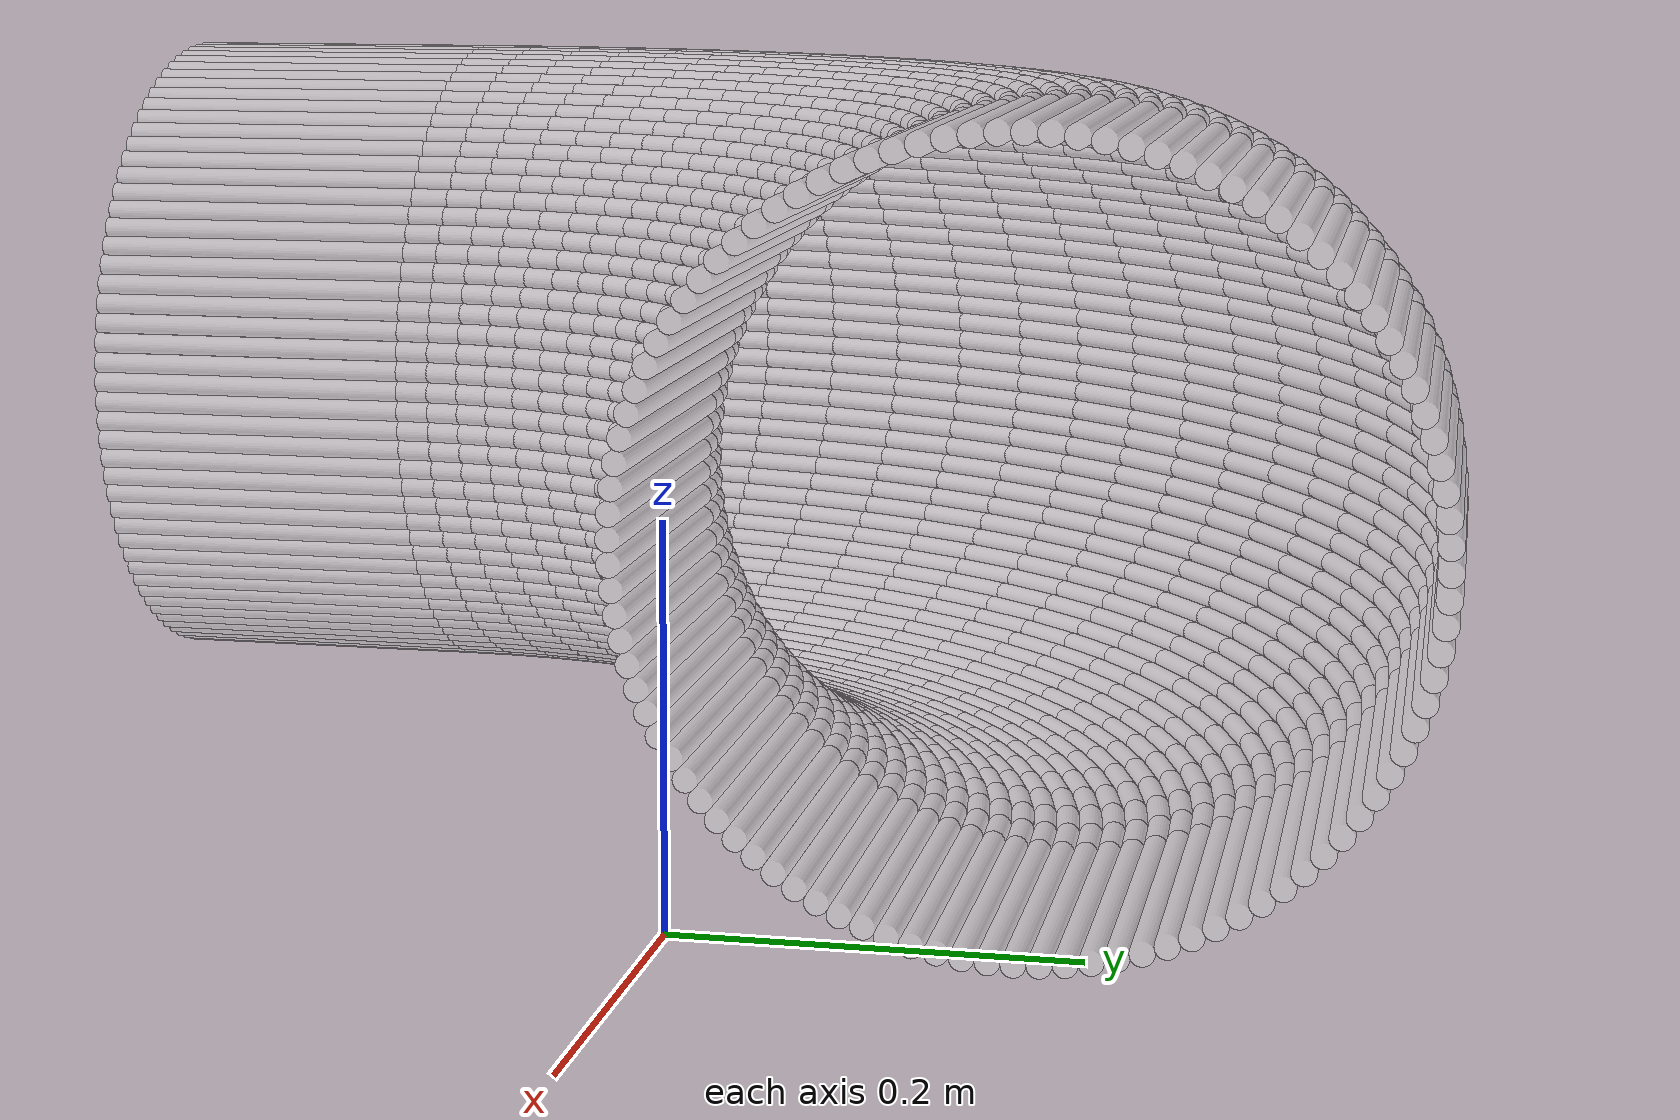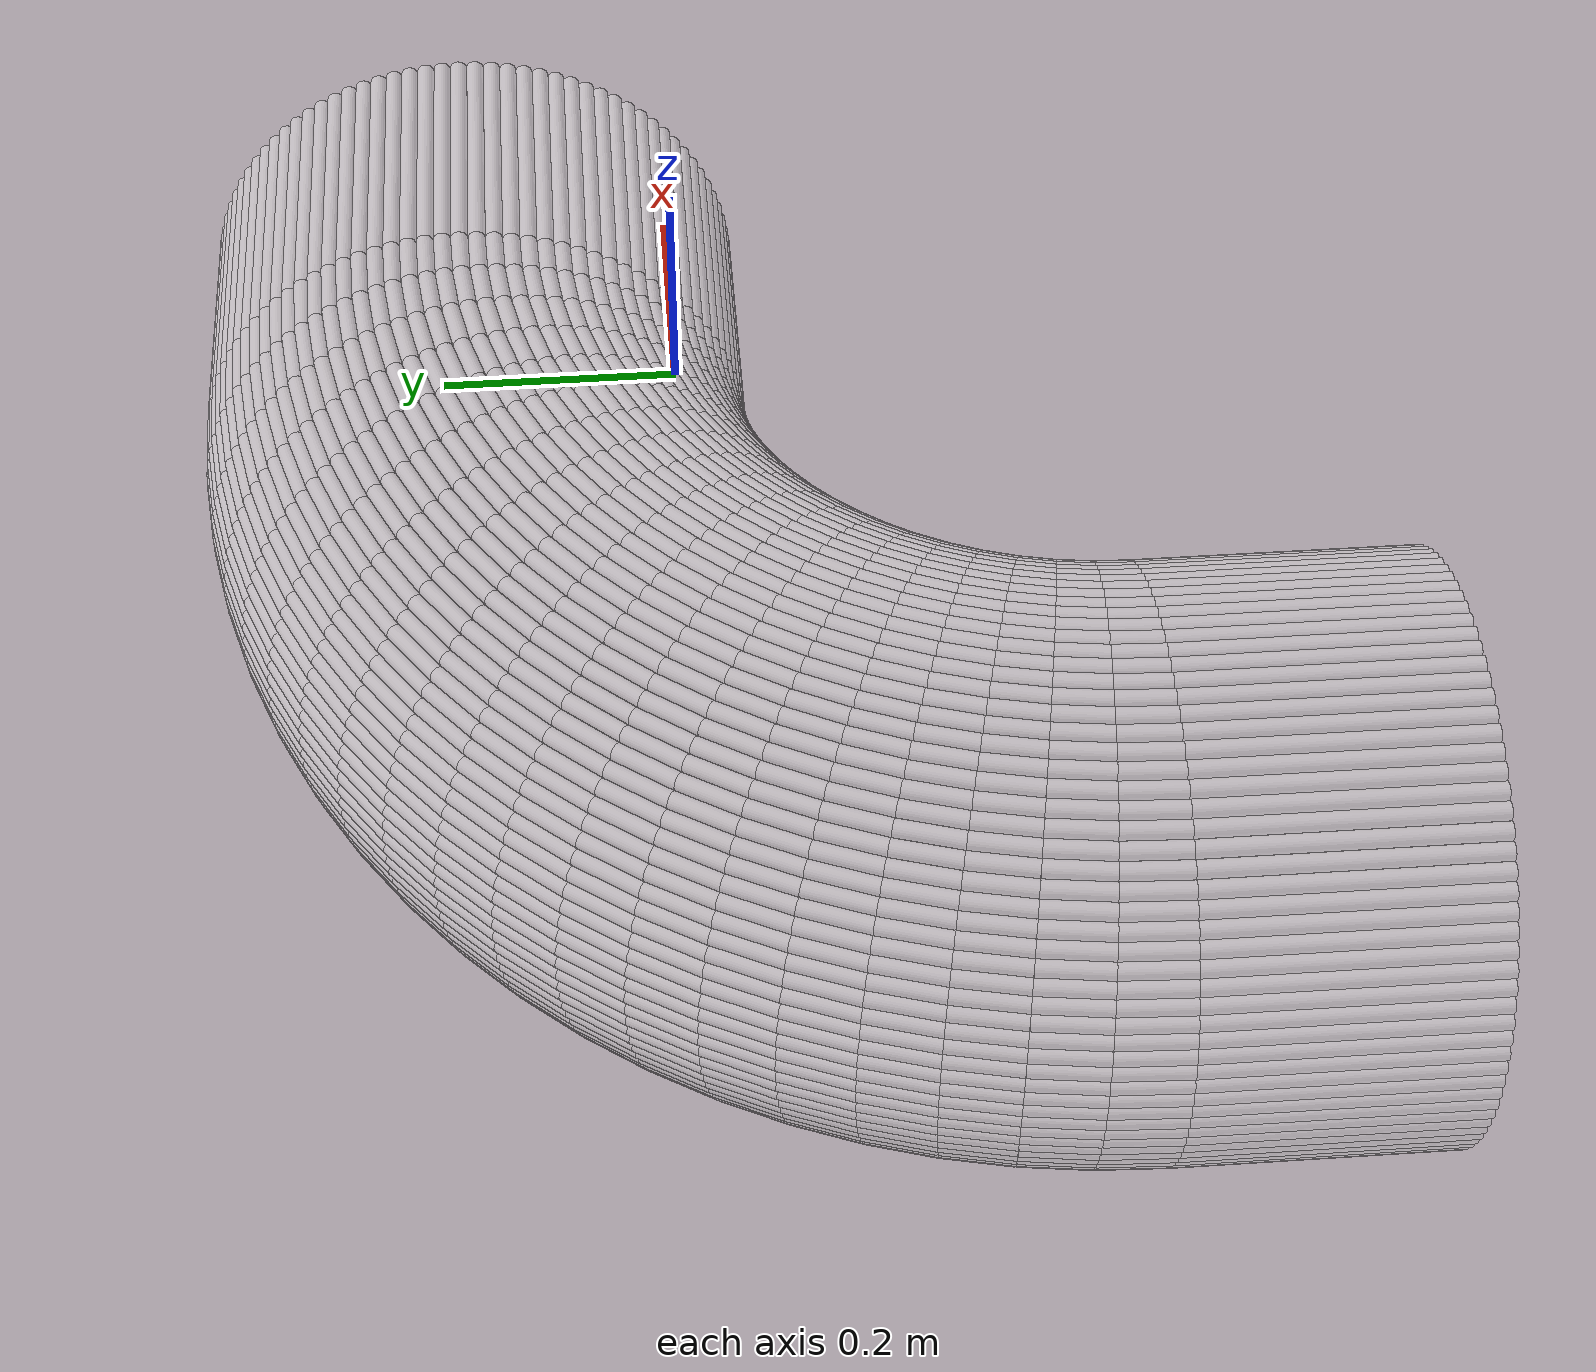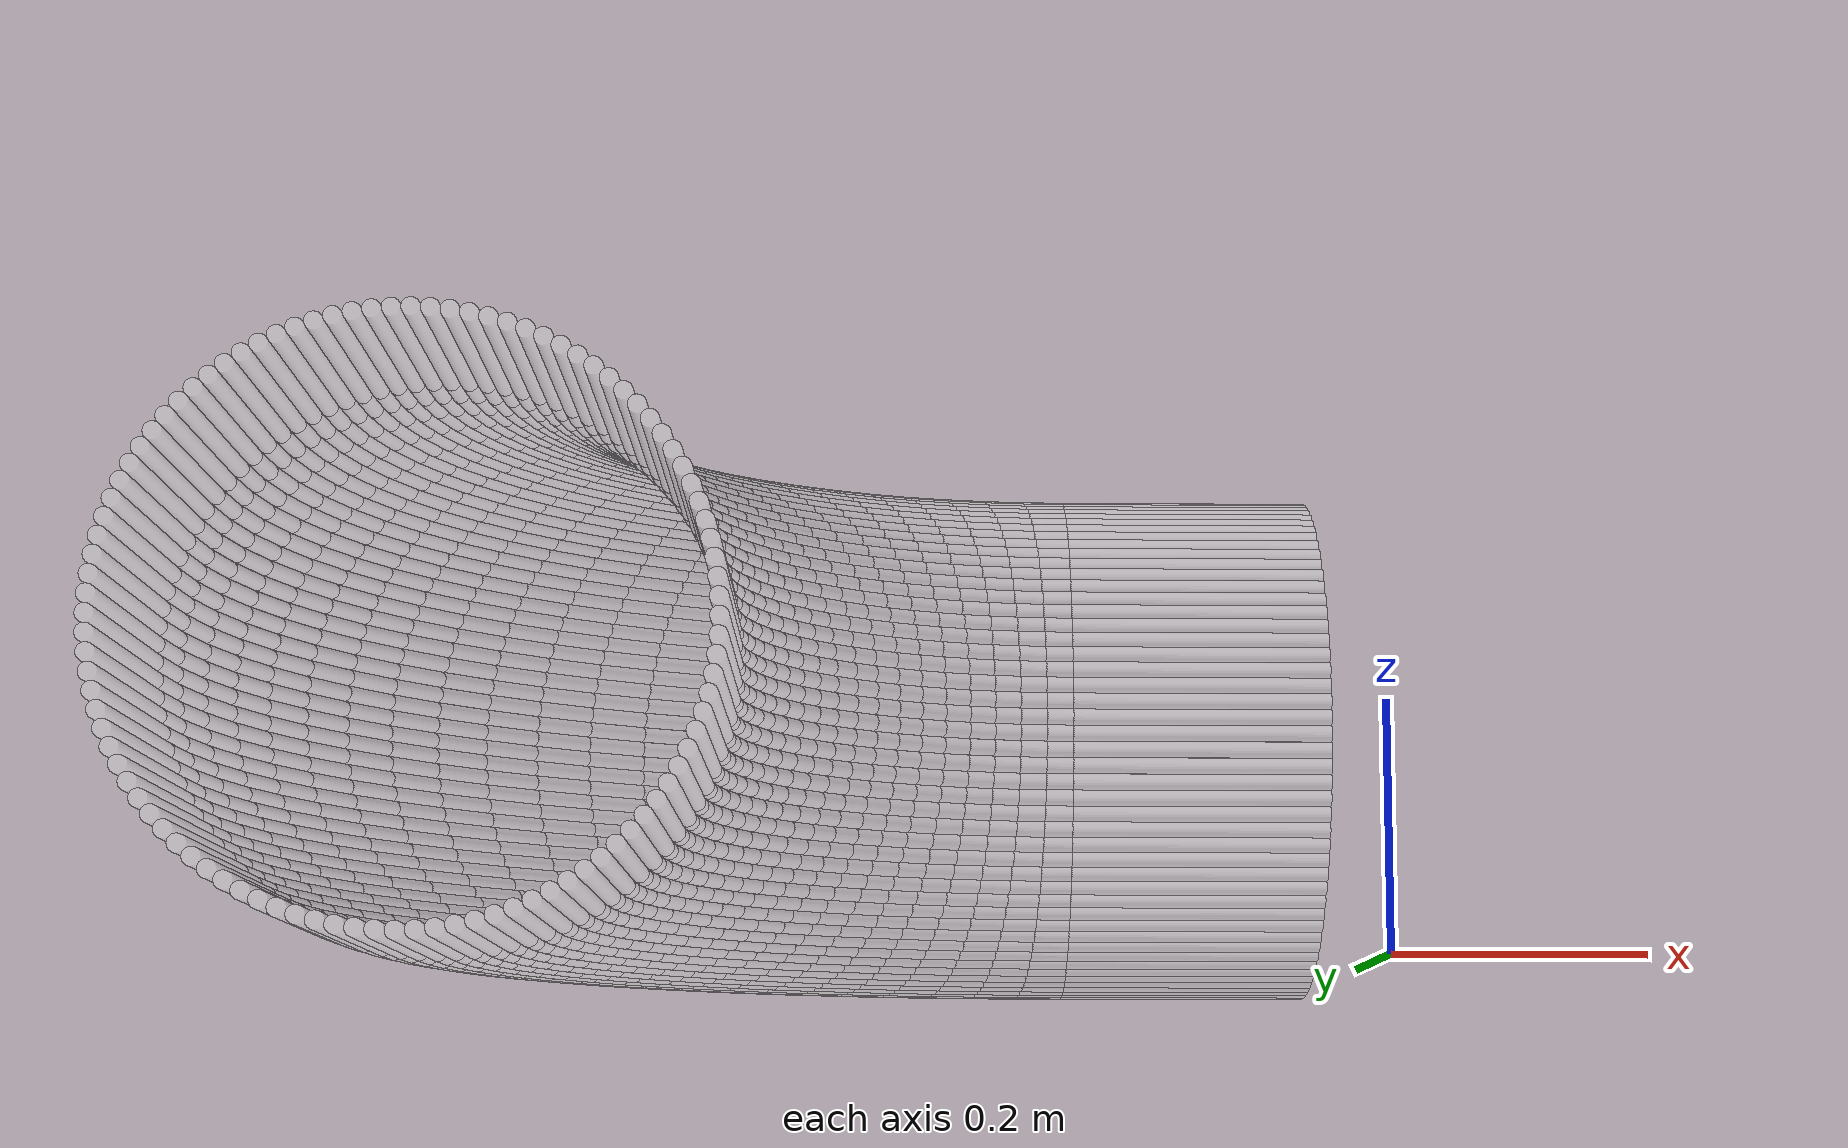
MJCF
<?xml version="1.0" encoding="utf-8"?>
<mujoco>
   <worldbody>
   <body pos="-0.25 -0.29 -0.02" euler="0 0 90">
      <geom euler=" 0 10 0 " fromto="0.65 -0.2 0.2 0.65 0 0.2" rgba="1 1 1 0.35"
            size="0.0062822"
            type="cylinder"/>
      <geom euler=" 0 20 0 " fromto="0.64961 -0.2 0.21256 0.64961 0 0.21256"
            rgba="1 1 1 0.35"
            size="0.0062822"
            type="cylinder"/>
      <geom euler=" 0 30 0 " fromto="0.64842 -0.2 0.22507 0.64842 0 0.22507"
            rgba="1 1 1 0.35"
            size="0.0062822"
            type="cylinder"/>
      <geom euler=" 0 40 0 " fromto="0.64646 -0.2 0.23748 0.64646 0 0.23748"
            rgba="1 1 1 0.35"
            size="0.0062822"
            type="cylinder"/>
      <geom euler=" 0 50 0 " fromto="0.64372 -0.2 0.24974 0.64372 0 0.24974"
            rgba="1 1 1 0.35"
            size="0.0062822"
            type="cylinder"/>
      <geom euler=" 0 60 0 " fromto="0.64021 -0.2 0.2618 0.64021 0 0.2618"
            rgba="1 1 1 0.35"
            size="0.0062822"
            type="cylinder"/>
      <geom euler=" 0 70 0 " fromto="0.63596 -0.2 0.27362 0.63596 0 0.27362"
            rgba="1 1 1 0.35"
            size="0.0062822"
            type="cylinder"/>
      <geom euler=" 0 80 0 " fromto="0.63097 -0.2 0.28516 0.63097 0 0.28516"
            rgba="1 1 1 0.35"
            size="0.0062822"
            type="cylinder"/>
      <geom euler=" 0 90 0 " fromto="0.62526 -0.2 0.29635 0.62526 0 0.29635"
            rgba="1 1 1 0.35"
            size="0.0062822"
            type="cylinder"/>
      <geom euler=" 0 100 0 " fromto="0.61887 -0.2 0.30717 0.61887 0 0.30717"
            rgba="1 1 1 0.35"
            size="0.0062822"
            type="cylinder"/>
      <geom euler=" 0 110 0 " fromto="0.6118 -0.2 0.31756 0.6118 0 0.31756"
            rgba="1 1 1 0.35"
            size="0.0062822"
            type="cylinder"/>
      <geom euler=" 0 120 0 " fromto="0.6041 -0.2 0.32748 0.6041 0 0.32748"
            rgba="1 1 1 0.35"
            size="0.0062822"
            type="cylinder"/>
      <geom euler=" 0 130 0 " fromto="0.59579 -0.2 0.33691 0.59579 0 0.33691"
            rgba="1 1 1 0.35"
            size="0.0062822"
            type="cylinder"/>
      <geom euler=" 0 140 0 " fromto="0.58691 -0.2 0.34579 0.58691 0 0.34579"
            rgba="1 1 1 0.35"
            size="0.0062822"
            type="cylinder"/>
      <geom euler=" 0 150 0 " fromto="0.57748 -0.2 0.3541 0.57748 0 0.3541"
            rgba="1 1 1 0.35"
            size="0.0062822"
            type="cylinder"/>
      <geom euler=" 0 160 0 " fromto="0.56756 -0.2 0.3618 0.56756 0 0.3618"
            rgba="1 1 1 0.35"
            size="0.0062822"
            type="cylinder"/>
      <geom euler=" 0 170 0 " fromto="0.55717 -0.2 0.36887 0.55717 0 0.36887"
            rgba="1 1 1 0.35"
            size="0.0062822"
            type="cylinder"/>
      <geom euler=" 0 180 0 " fromto="0.54635 -0.2 0.37526 0.54635 0 0.37526"
            rgba="1 1 1 0.35"
            size="0.0062822"
            type="cylinder"/>
      <geom euler=" 0 190 0 " fromto="0.53516 -0.2 0.38097 0.53516 0 0.38097"
            rgba="1 1 1 0.35"
            size="0.0062822"
            type="cylinder"/>
      <geom euler=" 0 200 0 " fromto="0.52362 -0.2 0.38596 0.52362 0 0.38596"
            rgba="1 1 1 0.35"
            size="0.0062822"
            type="cylinder"/>
      <geom euler=" 0 210 0 " fromto="0.5118 -0.2 0.39021 0.5118 0 0.39021"
            rgba="1 1 1 0.35"
            size="0.0062822"
            type="cylinder"/>
      <geom euler=" 0 220 0 " fromto="0.49974 -0.2 0.39372 0.49974 0 0.39372"
            rgba="1 1 1 0.35"
            size="0.0062822"
            type="cylinder"/>
      <geom euler=" 0 230 0 " fromto="0.48748 -0.2 0.39646 0.48748 0 0.39646"
            rgba="1 1 1 0.35"
            size="0.0062822"
            type="cylinder"/>
      <geom euler=" 0 240 0 " fromto="0.47507 -0.2 0.39842 0.47507 0 0.39842"
            rgba="1 1 1 0.35"
            size="0.0062822"
            type="cylinder"/>
      <geom euler=" 0 250 0 " fromto="0.46256 -0.2 0.39961 0.46256 0 0.39961"
            rgba="1 1 1 0.35"
            size="0.0062822"
            type="cylinder"/>
      <geom euler=" 0 260 0 " fromto="0.45 -0.2 0.4 0.45 0 0.4" rgba="1 1 1 0.35"
            size="0.0062822"
            type="cylinder"/>
      <geom euler=" 0 270 0 " fromto="0.43744 -0.2 0.39961 0.43744 0 0.39961"
            rgba="1 1 1 0.35"
            size="0.0062822"
            type="cylinder"/>
      <geom euler=" 0 280 0 " fromto="0.42493 -0.2 0.39842 0.42493 0 0.39842"
            rgba="1 1 1 0.35"
            size="0.0062822"
            type="cylinder"/>
      <geom euler=" 0 290 0 " fromto="0.41252 -0.2 0.39646 0.41252 0 0.39646"
            rgba="1 1 1 0.35"
            size="0.0062822"
            type="cylinder"/>
      <geom euler=" 0 300 0 " fromto="0.40026 -0.2 0.39372 0.40026 0 0.39372"
            rgba="1 1 1 0.35"
            size="0.0062822"
            type="cylinder"/>
      <geom euler=" 0 310 0 " fromto="0.3882 -0.2 0.39021 0.3882 0 0.39021"
            rgba="1 1 1 0.35"
            size="0.0062822"
            type="cylinder"/>
      <geom euler=" 0 320 0 " fromto="0.37638 -0.2 0.38596 0.37638 0 0.38596"
            rgba="1 1 1 0.35"
            size="0.0062822"
            type="cylinder"/>
      <geom euler=" 0 330 0 " fromto="0.36484 -0.2 0.38097 0.36484 0 0.38097"
            rgba="1 1 1 0.35"
            size="0.0062822"
            type="cylinder"/>
      <geom euler=" 0 340 0 " fromto="0.35365 -0.2 0.37526 0.35365 0 0.37526"
            rgba="1 1 1 0.35"
            size="0.0062822"
            type="cylinder"/>
      <geom euler=" 0 350 0 " fromto="0.34283 -0.2 0.36887 0.34283 0 0.36887"
            rgba="1 1 1 0.35"
            size="0.0062822"
            type="cylinder"/>
      <geom euler=" 0 360 0 " fromto="0.33244 -0.2 0.3618 0.33244 0 0.3618"
            rgba="1 1 1 0.35"
            size="0.0062822"
            type="cylinder"/>
      <geom euler=" 0 370 0 " fromto="0.32252 -0.2 0.3541 0.32252 0 0.3541"
            rgba="1 1 1 0.35"
            size="0.0062822"
            type="cylinder"/>
      <geom euler=" 0 380 0 " fromto="0.31309 -0.2 0.34579 0.31309 0 0.34579"
            rgba="1 1 1 0.35"
            size="0.0062822"
            type="cylinder"/>
      <geom euler=" 0 390 0 " fromto="0.30421 -0.2 0.33691 0.30421 0 0.33691"
            rgba="1 1 1 0.35"
            size="0.0062822"
            type="cylinder"/>
      <geom euler=" 0 400 0 " fromto="0.2959 -0.2 0.32748 0.2959 0 0.32748"
            rgba="1 1 1 0.35"
            size="0.0062822"
            type="cylinder"/>
      <geom euler=" 0 410 0 " fromto="0.2882 -0.2 0.31756 0.2882 0 0.31756"
            rgba="1 1 1 0.35"
            size="0.0062822"
            type="cylinder"/>
      <geom euler=" 0 420 0 " fromto="0.28113 -0.2 0.30717 0.28113 0 0.30717"
            rgba="1 1 1 0.35"
            size="0.0062822"
            type="cylinder"/>
      <geom euler=" 0 430 0 " fromto="0.27474 -0.2 0.29635 0.27474 0 0.29635"
            rgba="1 1 1 0.35"
            size="0.0062822"
            type="cylinder"/>
      <geom euler=" 0 440 0 " fromto="0.26903 -0.2 0.28516 0.26903 0 0.28516"
            rgba="1 1 1 0.35"
            size="0.0062822"
            type="cylinder"/>
      <geom euler=" 0 450 0 " fromto="0.26404 -0.2 0.27362 0.26404 0 0.27362"
            rgba="1 1 1 0.35"
            size="0.0062822"
            type="cylinder"/>
      <geom euler=" 0 460 0 " fromto="0.25979 -0.2 0.2618 0.25979 0 0.2618"
            rgba="1 1 1 0.35"
            size="0.0062822"
            type="cylinder"/>
      <geom euler=" 0 470 0 " fromto="0.25628 -0.2 0.24974 0.25628 0 0.24974"
            rgba="1 1 1 0.35"
            size="0.0062822"
            type="cylinder"/>
      <geom euler=" 0 480 0 " fromto="0.25354 -0.2 0.23748 0.25354 0 0.23748"
            rgba="1 1 1 0.35"
            size="0.0062822"
            type="cylinder"/>
      <geom euler=" 0 490 0 " fromto="0.25158 -0.2 0.22507 0.25158 0 0.22507"
            rgba="1 1 1 0.35"
            size="0.0062822"
            type="cylinder"/>
      <geom euler=" 0 500 0 " fromto="0.25039 -0.2 0.21256 0.25039 0 0.21256"
            rgba="1 1 1 0.35"
            size="0.0062822"
            type="cylinder"/>
      <geom euler=" 0 510 0 " fromto="0.25 -0.2 0.2 0.25 0 0.2" rgba="1 1 1 0.35"
            size="0.0062822"
            type="cylinder"/>
      <geom euler=" 0 520 0 " fromto="0.25039 -0.2 0.18744 0.25039 0 0.18744"
            rgba="1 1 1 0.35"
            size="0.0062822"
            type="cylinder"/>
      <geom euler=" 0 530 0 " fromto="0.25158 -0.2 0.17493 0.25158 0 0.17493"
            rgba="1 1 1 0.35"
            size="0.0062822"
            type="cylinder"/>
      <geom euler=" 0 540 0 " fromto="0.25354 -0.2 0.16252 0.25354 0 0.16252"
            rgba="1 1 1 0.35"
            size="0.0062822"
            type="cylinder"/>
      <geom euler=" 0 550 0 " fromto="0.25628 -0.2 0.15026 0.25628 0 0.15026"
            rgba="1 1 1 0.35"
            size="0.0062822"
            type="cylinder"/>
      <geom euler=" 0 560 0 " fromto="0.25979 -0.2 0.1382 0.25979 0 0.1382"
            rgba="1 1 1 0.35"
            size="0.0062822"
            type="cylinder"/>
      <geom euler=" 0 570 0 " fromto="0.26404 -0.2 0.12638 0.26404 0 0.12638"
            rgba="1 1 1 0.35"
            size="0.0062822"
            type="cylinder"/>
      <geom euler=" 0 580 0 " fromto="0.26903 -0.2 0.11484 0.26903 0 0.11484"
            rgba="1 1 1 0.35"
            size="0.0062822"
            type="cylinder"/>
      <geom euler=" 0 590 0 " fromto="0.27474 -0.2 0.10365 0.27474 0 0.10365"
            rgba="1 1 1 0.35"
            size="0.0062822"
            type="cylinder"/>
      <geom euler=" 0 600 0 " fromto="0.28113 -0.2 0.092835 0.28113 0 0.092835"
            rgba="1 1 1 0.35"
            size="0.0062822"
            type="cylinder"/>
      <geom euler=" 0 610 0 " fromto="0.2882 -0.2 0.082443 0.2882 0 0.082443"
            rgba="1 1 1 0.35"
            size="0.0062822"
            type="cylinder"/>
      <geom euler=" 0 620 0 " fromto="0.2959 -0.2 0.072515 0.2959 0 0.072515"
            rgba="1 1 1 0.35"
            size="0.0062822"
            type="cylinder"/>
      <geom euler=" 0 630 0 " fromto="0.30421 -0.2 0.063091 0.30421 0 0.063091"
            rgba="1 1 1 0.35"
            size="0.0062822"
            type="cylinder"/>
      <geom euler=" 0 640 0 " fromto="0.31309 -0.2 0.054206 0.31309 0 0.054206"
            rgba="1 1 1 0.35"
            size="0.0062822"
            type="cylinder"/>
      <geom euler=" 0 650 0 " fromto="0.32252 -0.2 0.045897 0.32252 0 0.045897"
            rgba="1 1 1 0.35"
            size="0.0062822"
            type="cylinder"/>
      <geom euler=" 0 660 0 " fromto="0.33244 -0.2 0.038197 0.33244 0 0.038197"
            rgba="1 1 1 0.35"
            size="0.0062822"
            type="cylinder"/>
      <geom euler=" 0 670 0 " fromto="0.34283 -0.2 0.031134 0.34283 0 0.031134"
            rgba="1 1 1 0.35"
            size="0.0062822"
            type="cylinder"/>
      <geom euler=" 0 680 0 " fromto="0.35365 -0.2 0.024739 0.35365 0 0.024739"
            rgba="1 1 1 0.35"
            size="0.0062822"
            type="cylinder"/>
      <geom euler=" 0 690 0 " fromto="0.36484 -0.2 0.019035 0.36484 0 0.019035"
            rgba="1 1 1 0.35"
            size="0.0062822"
            type="cylinder"/>
      <geom euler=" 0 700 0 " fromto="0.37638 -0.2 0.014045 0.37638 0 0.014045"
            rgba="1 1 1 0.35"
            size="0.0062822"
            type="cylinder"/>
      <geom euler=" 0 710 0 " fromto="0.3882 -0.2 0.0097887 0.3882 0 0.0097887"
            rgba="1 1 1 0.35"
            size="0.0062822"
            type="cylinder"/>
      <geom euler=" 0 720 0 " fromto="0.40026 -0.2 0.0062834 0.40026 0 0.0062834"
            rgba="1 1 1 0.35"
            size="0.0062822"
            type="cylinder"/>
      <geom euler=" 0 730 0 " fromto="0.41252 -0.2 0.0035425 0.41252 0 0.0035425"
            rgba="1 1 1 0.35"
            size="0.0062822"
            type="cylinder"/>
      <geom euler=" 0 740 0 " fromto="0.42493 -0.2 0.0015771 0.42493 0 0.0015771"
            rgba="1 1 1 0.35"
            size="0.0062822"
            type="cylinder"/>
      <geom euler=" 0 750 0 " fromto="0.43744 -0.2 0.00039465 0.43744 0 0.00039465"
            rgba="1 1 1 0.35"
            size="0.0062822"
            type="cylinder"/>
      <geom euler=" 0 760 0 " fromto="0.45 -0.2 0 0.45 0 0" rgba="1 1 1 0.35"
            size="0.0062822"
            type="cylinder"/>
      <geom euler=" 0 770 0 " fromto="0.46256 -0.2 0.00039465 0.46256 0 0.00039465"
            rgba="1 1 1 0.35"
            size="0.0062822"
            type="cylinder"/>
      <geom euler=" 0 780 0 " fromto="0.47507 -0.2 0.0015771 0.47507 0 0.0015771"
            rgba="1 1 1 0.35"
            size="0.0062822"
            type="cylinder"/>
      <geom euler=" 0 790 0 " fromto="0.48748 -0.2 0.0035425 0.48748 0 0.0035425"
            rgba="1 1 1 0.35"
            size="0.0062822"
            type="cylinder"/>
      <geom euler=" 0 800 0 " fromto="0.49974 -0.2 0.0062834 0.49974 0 0.0062834"
            rgba="1 1 1 0.35"
            size="0.0062822"
            type="cylinder"/>
      <geom euler=" 0 810 0 " fromto="0.5118 -0.2 0.0097887 0.5118 0 0.0097887"
            rgba="1 1 1 0.35"
            size="0.0062822"
            type="cylinder"/>
      <geom euler=" 0 820 0 " fromto="0.52362 -0.2 0.014045 0.52362 0 0.014045"
            rgba="1 1 1 0.35"
            size="0.0062822"
            type="cylinder"/>
      <geom euler=" 0 830 0 " fromto="0.53516 -0.2 0.019035 0.53516 0 0.019035"
            rgba="1 1 1 0.35"
            size="0.0062822"
            type="cylinder"/>
      <geom euler=" 0 840 0 " fromto="0.54635 -0.2 0.024739 0.54635 0 0.024739"
            rgba="1 1 1 0.35"
            size="0.0062822"
            type="cylinder"/>
      <geom euler=" 0 850 0 " fromto="0.55717 -0.2 0.031134 0.55717 0 0.031134"
            rgba="1 1 1 0.35"
            size="0.0062822"
            type="cylinder"/>
      <geom euler=" 0 860 0 " fromto="0.56756 -0.2 0.038197 0.56756 0 0.038197"
            rgba="1 1 1 0.35"
            size="0.0062822"
            type="cylinder"/>
      <geom euler=" 0 870 0 " fromto="0.57748 -0.2 0.045897 0.57748 0 0.045897"
            rgba="1 1 1 0.35"
            size="0.0062822"
            type="cylinder"/>
      <geom euler=" 0 880 0 " fromto="0.58691 -0.2 0.054206 0.58691 0 0.054206"
            rgba="1 1 1 0.35"
            size="0.0062822"
            type="cylinder"/>
      <geom euler=" 0 890 0 " fromto="0.59579 -0.2 0.063091 0.59579 0 0.063091"
            rgba="1 1 1 0.35"
            size="0.0062822"
            type="cylinder"/>
      <geom euler=" 0 900 0 " fromto="0.6041 -0.2 0.072515 0.6041 0 0.072515"
            rgba="1 1 1 0.35"
            size="0.0062822"
            type="cylinder"/>
      <geom euler=" 0 910 0 " fromto="0.6118 -0.2 0.082443 0.6118 0 0.082443"
            rgba="1 1 1 0.35"
            size="0.0062822"
            type="cylinder"/>
      <geom euler=" 0 920 0 " fromto="0.61887 -0.2 0.092835 0.61887 0 0.092835"
            rgba="1 1 1 0.35"
            size="0.0062822"
            type="cylinder"/>
      <geom euler=" 0 930 0 " fromto="0.62526 -0.2 0.10365 0.62526 0 0.10365"
            rgba="1 1 1 0.35"
            size="0.0062822"
            type="cylinder"/>
      <geom euler=" 0 940 0 " fromto="0.63097 -0.2 0.11484 0.63097 0 0.11484"
            rgba="1 1 1 0.35"
            size="0.0062822"
            type="cylinder"/>
      <geom euler=" 0 950 0 " fromto="0.63596 -0.2 0.12638 0.63596 0 0.12638"
            rgba="1 1 1 0.35"
            size="0.0062822"
            type="cylinder"/>
      <geom euler=" 0 960 0 " fromto="0.64021 -0.2 0.1382 0.64021 0 0.1382"
            rgba="1 1 1 0.35"
            size="0.0062822"
            type="cylinder"/>
      <geom euler=" 0 970 0 " fromto="0.64372 -0.2 0.15026 0.64372 0 0.15026"
            rgba="1 1 1 0.35"
            size="0.0062822"
            type="cylinder"/>
      <geom euler=" 0 980 0 " fromto="0.64646 -0.2 0.16252 0.64646 0 0.16252"
            rgba="1 1 1 0.35"
            size="0.0062822"
            type="cylinder"/>
      <geom euler=" 0 990 0 " fromto="0.64842 -0.2 0.17493 0.64842 0 0.17493"
            rgba="1 1 1 0.35"
            size="0.0062822"
            type="cylinder"/>
      <geom euler=" 0 1000 0 " fromto="0.64961 -0.2 0.18744 0.64961 0 0.18744"
            rgba="1 1 1 0.35"
            size="0.0062822"
            type="cylinder"/>
      <geom euler=" 0 10 0 " fromto="0.65 0 0.2 0.64778 0.053677 0.2" rgba="1 1 1 0.35"
            size="0.0062822"
            type="cylinder"/>
      <geom euler=" 0 20 0 " fromto="0.64961 0 0.21256 0.64739 0.053644 0.21256"
            rgba="1 1 1 0.35"
            size="0.0062822"
            type="cylinder"/>
      <geom euler=" 0 30 0 " fromto="0.64842 0 0.22507 0.64621 0.053546 0.22507"
            rgba="1 1 1 0.35"
            size="0.0062822"
            type="cylinder"/>
      <geom euler=" 0 40 0 " fromto="0.64646 0 0.23748 0.64425 0.053384 0.23748"
            rgba="1 1 1 0.35"
            size="0.0062822"
            type="cylinder"/>
      <geom euler=" 0 50 0 " fromto="0.64372 0 0.24974 0.64152 0.053158 0.24974"
            rgba="1 1 1 0.35"
            size="0.0062822"
            type="cylinder"/>
      <geom euler=" 0 60 0 " fromto="0.64021 0 0.2618 0.63802 0.052868 0.2618"
            rgba="1 1 1 0.35"
            size="0.0062822"
            type="cylinder"/>
      <geom euler=" 0 70 0 " fromto="0.63596 0 0.27362 0.63378 0.052517 0.27362"
            rgba="1 1 1 0.35"
            size="0.0062822"
            type="cylinder"/>
      <geom euler=" 0 80 0 " fromto="0.63097 0 0.28516 0.62881 0.052105 0.28516"
            rgba="1 1 1 0.35"
            size="0.0062822"
            type="cylinder"/>
      <geom euler=" 0 90 0 " fromto="0.62526 0 0.29635 0.62313 0.051634 0.29635"
            rgba="1 1 1 0.35"
            size="0.0062822"
            type="cylinder"/>
      <geom euler=" 0 100 0 " fromto="0.61887 0 0.30717 0.61675 0.051106 0.30717"
            rgba="1 1 1 0.35"
            size="0.0062822"
            type="cylinder"/>
      <geom euler=" 0 110 0 " fromto="0.6118 0 0.31756 0.60971 0.050522 0.31756"
            rgba="1 1 1 0.35"
            size="0.0062822"
            type="cylinder"/>
      <geom euler=" 0 120 0 " fromto="0.6041 0 0.32748 0.60204 0.049886 0.32748"
            rgba="1 1 1 0.35"
            size="0.0062822"
            type="cylinder"/>
      <geom euler=" 0 130 0 " fromto="0.59579 0 0.33691 0.59376 0.0492 0.33691"
            rgba="1 1 1 0.35"
            size="0.0062822"
            type="cylinder"/>
      <geom euler=" 0 140 0 " fromto="0.58691 0 0.34579 0.5849 0.048467 0.34579"
            rgba="1 1 1 0.35"
            size="0.0062822"
            type="cylinder"/>
      <geom euler=" 0 150 0 " fromto="0.57748 0 0.3541 0.57551 0.047688 0.3541"
            rgba="1 1 1 0.35"
            size="0.0062822"
            type="cylinder"/>
      <geom euler=" 0 160 0 " fromto="0.56756 0 0.3618 0.56562 0.046868 0.3618"
            rgba="1 1 1 0.35"
            size="0.0062822"
            type="cylinder"/>
      <geom euler=" 0 170 0 " fromto="0.55717 0 0.36887 0.55526 0.04601 0.36887"
            rgba="1 1 1 0.35"
            size="0.0062822"
            type="cylinder"/>
      <geom euler=" 0 180 0 " fromto="0.54635 0 0.37526 0.54448 0.045117 0.37526"
            rgba="1 1 1 0.35"
            size="0.0062822"
            type="cylinder"/>
      <geom euler=" 0 190 0 " fromto="0.53516 0 0.38097 0.53333 0.044193 0.38097"
            rgba="1 1 1 0.35"
            size="0.0062822"
            type="cylinder"/>
      <geom euler=" 0 200 0 " fromto="0.52362 0 0.38596 0.52184 0.043241 0.38596"
            rgba="1 1 1 0.35"
            size="0.0062822"
            type="cylinder"/>
      <geom euler=" 0 210 0 " fromto="0.5118 0 0.39021 0.51006 0.042264 0.39021"
            rgba="1 1 1 0.35"
            size="0.0062822"
            type="cylinder"/>
      <geom euler=" 0 220 0 " fromto="0.49974 0 0.39372 0.49803 0.041268 0.39372"
            rgba="1 1 1 0.35"
            size="0.0062822"
            type="cylinder"/>
      <geom euler=" 0 230 0 " fromto="0.48748 0 0.39646 0.48581 0.040255 0.39646"
            rgba="1 1 1 0.35"
            size="0.0062822"
            type="cylinder"/>
      <geom euler=" 0 240 0 " fromto="0.47507 0 0.39842 0.47344 0.039231 0.39842"
            rgba="1 1 1 0.35"
            size="0.0062822"
            type="cylinder"/>
      <geom euler=" 0 250 0 " fromto="0.46256 0 0.39961 0.46098 0.038198 0.39961"
            rgba="1 1 1 0.35"
            size="0.0062822"
            type="cylinder"/>
      <geom euler=" 0 260 0 " fromto="0.45 0 0.4 0.44846 0.037161 0.4" rgba="1 1 1 0.35"
            size="0.0062822"
            type="cylinder"/>
      <geom euler=" 0 270 0 " fromto="0.43744 0 0.39961 0.43595 0.036124 0.39961"
            rgba="1 1 1 0.35"
            size="0.0062822"
            type="cylinder"/>
      <geom euler=" 0 280 0 " fromto="0.42493 0 0.39842 0.42348 0.035091 0.39842"
            rgba="1 1 1 0.35"
            size="0.0062822"
            type="cylinder"/>
      <geom euler=" 0 290 0 " fromto="0.41252 0 0.39646 0.41111 0.034066 0.39646"
            rgba="1 1 1 0.35"
            size="0.0062822"
            type="cylinder"/>
      <geom euler=" 0 300 0 " fromto="0.40026 0 0.39372 0.39889 0.033053 0.39372"
            rgba="1 1 1 0.35"
            size="0.0062822"
            type="cylinder"/>
      <geom euler=" 0 310 0 " fromto="0.3882 0 0.39021 0.38687 0.032057 0.39021"
            rgba="1 1 1 0.35"
            size="0.0062822"
            type="cylinder"/>
      <geom euler=" 0 320 0 " fromto="0.37638 0 0.38596 0.37509 0.031081 0.38596"
            rgba="1 1 1 0.35"
            size="0.0062822"
            type="cylinder"/>
      <geom euler=" 0 330 0 " fromto="0.36484 0 0.38097 0.3636 0.030129 0.38097"
            rgba="1 1 1 0.35"
            size="0.0062822"
            type="cylinder"/>
      <geom euler=" 0 340 0 " fromto="0.35365 0 0.37526 0.35244 0.029204 0.37526"
            rgba="1 1 1 0.35"
            size="0.0062822"
            type="cylinder"/>
      <geom euler=" 0 350 0 " fromto="0.34283 0 0.36887 0.34166 0.028311 0.36887"
            rgba="1 1 1 0.35"
            size="0.0062822"
            type="cylinder"/>
      <geom euler=" 0 360 0 " fromto="0.33244 0 0.3618 0.33131 0.027453 0.3618"
            rgba="1 1 1 0.35"
            size="0.0062822"
            type="cylinder"/>
      <geom euler=" 0 370 0 " fromto="0.32252 0 0.3541 0.32141 0.026633 0.3541"
            rgba="1 1 1 0.35"
            size="0.0062822"
            type="cylinder"/>
      <geom euler=" 0 380 0 " fromto="0.31309 0 0.34579 0.31202 0.025855 0.34579"
            rgba="1 1 1 0.35"
            size="0.0062822"
            type="cylinder"/>
      <geom euler=" 0 390 0 " fromto="0.30421 0 0.33691 0.30317 0.025121 0.33691"
            rgba="1 1 1 0.35"
            size="0.0062822"
            type="cylinder"/>
      <geom euler=" 0 400 0 " fromto="0.2959 0 0.32748 0.29489 0.024435 0.32748"
            rgba="1 1 1 0.35"
            size="0.0062822"
            type="cylinder"/>
      <geom euler=" 0 410 0 " fromto="0.2882 0 0.31756 0.28721 0.023799 0.31756"
            rgba="1 1 1 0.35"
            size="0.0062822"
            type="cylinder"/>
      <geom euler=" 0 420 0 " fromto="0.28113 0 0.30717 0.28017 0.023216 0.30717"
            rgba="1 1 1 0.35"
            size="0.0062822"
            type="cylinder"/>
      <geom euler=" 0 430 0 " fromto="0.27474 0 0.29635 0.2738 0.022688 0.29635"
            rgba="1 1 1 0.35"
            size="0.0062822"
            type="cylinder"/>
      <geom euler=" 0 440 0 " fromto="0.26903 0 0.28516 0.26812 0.022217 0.28516"
            rgba="1 1 1 0.35"
            size="0.0062822"
            type="cylinder"/>
      <geom euler=" 0 450 0 " fromto="0.26404 0 0.27362 0.26314 0.021805 0.27362"
            rgba="1 1 1 0.35"
            size="0.0062822"
            type="cylinder"/>
      <geom euler=" 0 460 0 " fromto="0.25979 0 0.2618 0.2589 0.021453 0.2618"
            rgba="1 1 1 0.35"
            size="0.0062822"
            type="cylinder"/>
      <geom euler=" 0 470 0 " fromto="0.25628 0 0.24974 0.25541 0.021164 0.24974"
            rgba="1 1 1 0.35"
            size="0.0062822"
            type="cylinder"/>
      <geom euler=" 0 480 0 " fromto="0.25354 0 0.23748 0.25268 0.020937 0.23748"
            rgba="1 1 1 0.35"
            size="0.0062822"
            type="cylinder"/>
      <geom euler=" 0 490 0 " fromto="0.25158 0 0.22507 0.25072 0.020775 0.22507"
            rgba="1 1 1 0.35"
            size="0.0062822"
            type="cylinder"/>
      <geom euler=" 0 500 0 " fromto="0.25039 0 0.21256 0.24954 0.020677 0.21256"
            rgba="1 1 1 0.35"
            size="0.0062822"
            type="cylinder"/>
      <geom euler=" 0 510 0 " fromto="0.25 0 0.2 0.24915 0.020645 0.2" rgba="1 1 1 0.35"
            size="0.0062822"
            type="cylinder"/>
      <geom euler=" 0 520 0 " fromto="0.25039 0 0.18744 0.24954 0.020677 0.18744"
            rgba="1 1 1 0.35"
            size="0.0062822"
            type="cylinder"/>
      <geom euler=" 0 530 0 " fromto="0.25158 0 0.17493 0.25072 0.020775 0.17493"
            rgba="1 1 1 0.35"
            size="0.0062822"
            type="cylinder"/>
      <geom euler=" 0 540 0 " fromto="0.25354 0 0.16252 0.25268 0.020937 0.16252"
            rgba="1 1 1 0.35"
            size="0.0062822"
            type="cylinder"/>
      <geom euler=" 0 550 0 " fromto="0.25628 0 0.15026 0.25541 0.021164 0.15026"
            rgba="1 1 1 0.35"
            size="0.0062822"
            type="cylinder"/>
      <geom euler=" 0 560 0 " fromto="0.25979 0 0.1382 0.2589 0.021453 0.1382"
            rgba="1 1 1 0.35"
            size="0.0062822"
            type="cylinder"/>
      <geom euler=" 0 570 0 " fromto="0.26404 0 0.12638 0.26314 0.021805 0.12638"
            rgba="1 1 1 0.35"
            size="0.0062822"
            type="cylinder"/>
      <geom euler=" 0 580 0 " fromto="0.26903 0 0.11484 0.26812 0.022217 0.11484"
            rgba="1 1 1 0.35"
            size="0.0062822"
            type="cylinder"/>
      <geom euler=" 0 590 0 " fromto="0.27474 0 0.10365 0.2738 0.022688 0.10365"
            rgba="1 1 1 0.35"
            size="0.0062822"
            type="cylinder"/>
      <geom euler=" 0 600 0 " fromto="0.28113 0 0.092835 0.28017 0.023216 0.092835"
            rgba="1 1 1 0.35"
            size="0.0062822"
            type="cylinder"/>
      <geom euler=" 0 610 0 " fromto="0.2882 0 0.082443 0.28721 0.023799 0.082443"
            rgba="1 1 1 0.35"
            size="0.0062822"
            type="cylinder"/>
      <geom euler=" 0 620 0 " fromto="0.2959 0 0.072515 0.29489 0.024435 0.072515"
            rgba="1 1 1 0.35"
            size="0.0062822"
            type="cylinder"/>
      <geom euler=" 0 630 0 " fromto="0.30421 0 0.063091 0.30317 0.025121 0.063091"
            rgba="1 1 1 0.35"
            size="0.0062822"
            type="cylinder"/>
      <geom euler=" 0 640 0 " fromto="0.31309 0 0.054206 0.31202 0.025855 0.054206"
            rgba="1 1 1 0.35"
            size="0.0062822"
            type="cylinder"/>
      <geom euler=" 0 650 0 " fromto="0.32252 0 0.045897 0.32141 0.026633 0.045897"
            rgba="1 1 1 0.35"
            size="0.0062822"
            type="cylinder"/>
      <geom euler=" 0 660 0 " fromto="0.33244 0 0.038197 0.33131 0.027453 0.038197"
            rgba="1 1 1 0.35"
            size="0.0062822"
            type="cylinder"/>
      <geom euler=" 0 670 0 " fromto="0.34283 0 0.031134 0.34166 0.028311 0.031134"
            rgba="1 1 1 0.35"
            size="0.0062822"
            type="cylinder"/>
      <geom euler=" 0 680 0 " fromto="0.35365 0 0.024739 0.35244 0.029204 0.024739"
            rgba="1 1 1 0.35"
            size="0.0062822"
            type="cylinder"/>
      <geom euler=" 0 690 0 " fromto="0.36484 0 0.019035 0.3636 0.030129 0.019035"
            rgba="1 1 1 0.35"
            size="0.0062822"
            type="cylinder"/>
      <geom euler=" 0 700 0 " fromto="0.37638 0 0.014045 0.37509 0.031081 0.014045"
            rgba="1 1 1 0.35"
            size="0.0062822"
            type="cylinder"/>
      <geom euler=" 0 710 0 " fromto="0.3882 0 0.0097887 0.38687 0.032057 0.0097887"
            rgba="1 1 1 0.35"
            size="0.0062822"
            type="cylinder"/>
      <geom euler=" 0 720 0 " fromto="0.40026 0 0.0062834 0.39889 0.033053 0.0062834"
            rgba="1 1 1 0.35"
            size="0.0062822"
            type="cylinder"/>
      <geom euler=" 0 730 0 " fromto="0.41252 0 0.0035425 0.41111 0.034066 0.0035425"
            rgba="1 1 1 0.35"
            size="0.0062822"
            type="cylinder"/>
      <geom euler=" 0 740 0 " fromto="0.42493 0 0.0015771 0.42348 0.035091 0.0015771"
            rgba="1 1 1 0.35"
            size="0.0062822"
            type="cylinder"/>
      <geom euler=" 0 750 0 " fromto="0.43744 0 0.00039465 0.43595 0.036124 0.00039465"
            rgba="1 1 1 0.35"
            size="0.0062822"
            type="cylinder"/>
      <geom euler=" 0 760 0 " fromto="0.45 0 0 0.44846 0.037161 0" rgba="1 1 1 0.35"
            size="0.0062822"
            type="cylinder"/>
      <geom euler=" 0 770 0 " fromto="0.46256 0 0.00039465 0.46098 0.038198 0.00039465"
            rgba="1 1 1 0.35"
            size="0.0062822"
            type="cylinder"/>
      <geom euler=" 0 780 0 " fromto="0.47507 0 0.0015771 0.47344 0.039231 0.0015771"
            rgba="1 1 1 0.35"
            size="0.0062822"
            type="cylinder"/>
      <geom euler=" 0 790 0 " fromto="0.48748 0 0.0035425 0.48581 0.040255 0.0035425"
            rgba="1 1 1 0.35"
            size="0.0062822"
            type="cylinder"/>
      <geom euler=" 0 800 0 " fromto="0.49974 0 0.0062834 0.49803 0.041268 0.0062834"
            rgba="1 1 1 0.35"
            size="0.0062822"
            type="cylinder"/>
      <geom euler=" 0 810 0 " fromto="0.5118 0 0.0097887 0.51006 0.042264 0.0097887"
            rgba="1 1 1 0.35"
            size="0.0062822"
            type="cylinder"/>
      <geom euler=" 0 820 0 " fromto="0.52362 0 0.014045 0.52184 0.043241 0.014045"
            rgba="1 1 1 0.35"
            size="0.0062822"
            type="cylinder"/>
      <geom euler=" 0 830 0 " fromto="0.53516 0 0.019035 0.53333 0.044193 0.019035"
            rgba="1 1 1 0.35"
            size="0.0062822"
            type="cylinder"/>
      <geom euler=" 0 840 0 " fromto="0.54635 0 0.024739 0.54448 0.045117 0.024739"
            rgba="1 1 1 0.35"
            size="0.0062822"
            type="cylinder"/>
      <geom euler=" 0 850 0 " fromto="0.55717 0 0.031134 0.55526 0.04601 0.031134"
            rgba="1 1 1 0.35"
            size="0.0062822"
            type="cylinder"/>
      <geom euler=" 0 860 0 " fromto="0.56756 0 0.038197 0.56562 0.046868 0.038197"
            rgba="1 1 1 0.35"
            size="0.0062822"
            type="cylinder"/>
      <geom euler=" 0 870 0 " fromto="0.57748 0 0.045897 0.57551 0.047688 0.045897"
            rgba="1 1 1 0.35"
            size="0.0062822"
            type="cylinder"/>
      <geom euler=" 0 880 0 " fromto="0.58691 0 0.054206 0.5849 0.048467 0.054206"
            rgba="1 1 1 0.35"
            size="0.0062822"
            type="cylinder"/>
      <geom euler=" 0 890 0 " fromto="0.59579 0 0.063091 0.59376 0.0492 0.063091"
            rgba="1 1 1 0.35"
            size="0.0062822"
            type="cylinder"/>
      <geom euler=" 0 900 0 " fromto="0.6041 0 0.072515 0.60204 0.049886 0.072515"
            rgba="1 1 1 0.35"
            size="0.0062822"
            type="cylinder"/>
      <geom euler=" 0 910 0 " fromto="0.6118 0 0.082443 0.60971 0.050522 0.082443"
            rgba="1 1 1 0.35"
            size="0.0062822"
            type="cylinder"/>
      <geom euler=" 0 920 0 " fromto="0.61887 0 0.092835 0.61675 0.051106 0.092835"
            rgba="1 1 1 0.35"
            size="0.0062822"
            type="cylinder"/>
      <geom euler=" 0 930 0 " fromto="0.62526 0 0.10365 0.62313 0.051634 0.10365"
            rgba="1 1 1 0.35"
            size="0.0062822"
            type="cylinder"/>
      <geom euler=" 0 940 0 " fromto="0.63097 0 0.11484 0.62881 0.052105 0.11484"
            rgba="1 1 1 0.35"
            size="0.0062822"
            type="cylinder"/>
      <geom euler=" 0 950 0 " fromto="0.63596 0 0.12638 0.63378 0.052517 0.12638"
            rgba="1 1 1 0.35"
            size="0.0062822"
            type="cylinder"/>
      <geom euler=" 0 960 0 " fromto="0.64021 0 0.1382 0.63802 0.052868 0.1382"
            rgba="1 1 1 0.35"
            size="0.0062822"
            type="cylinder"/>
      <geom euler=" 0 970 0 " fromto="0.64372 0 0.15026 0.64152 0.053158 0.15026"
            rgba="1 1 1 0.35"
            size="0.0062822"
            type="cylinder"/>
      <geom euler=" 0 980 0 " fromto="0.64646 0 0.16252 0.64425 0.053384 0.16252"
            rgba="1 1 1 0.35"
            size="0.0062822"
            type="cylinder"/>
      <geom euler=" 0 990 0 " fromto="0.64842 0 0.17493 0.64621 0.053546 0.17493"
            rgba="1 1 1 0.35"
            size="0.0062822"
            type="cylinder"/>
      <geom euler=" 0 1000 0 " fromto="0.64961 0 0.18744 0.64739 0.053644 0.18744"
            rgba="1 1 1 0.35"
            size="0.0062822"
            type="cylinder"/>
      <geom euler=" 0 10 0 " fromto="0.64778 0.053677 0.2 0.64113 0.10699 0.2"
            rgba="1 1 1 0.35"
            size="0.0062822"
            type="cylinder"/>
      <geom euler=" 0 20 0 " fromto="0.64739 0.053644 0.21256 0.64075 0.10692 0.21256"
            rgba="1 1 1 0.35"
            size="0.0062822"
            type="cylinder"/>
      <geom euler=" 0 30 0 " fromto="0.64621 0.053546 0.22507 0.63958 0.10673 0.22507"
            rgba="1 1 1 0.35"
            size="0.0062822"
            type="cylinder"/>
      <geom euler=" 0 40 0 " fromto="0.64425 0.053384 0.23748 0.63764 0.1064 0.23748"
            rgba="1 1 1 0.35"
            size="0.0062822"
            type="cylinder"/>
      <geom euler=" 0 50 0 " fromto="0.64152 0.053158 0.24974 0.63494 0.10595 0.24974"
            rgba="1 1 1 0.35"
            size="0.0062822"
            type="cylinder"/>
      <geom euler=" 0 60 0 " fromto="0.63802 0.052868 0.2618 0.63148 0.10538 0.2618"
            rgba="1 1 1 0.35"
            size="0.0062822"
            type="cylinder"/>
      <geom euler=" 0 70 0 " fromto="0.63378 0.052517 0.27362 0.62728 0.10467 0.27362"
            rgba="1 1 1 0.35"
            size="0.0062822"
            type="cylinder"/>
      <geom euler=" 0 80 0 " fromto="0.62881 0.052105 0.28516 0.62236 0.10385 0.28516"
            rgba="1 1 1 0.35"
            size="0.0062822"
            type="cylinder"/>
      <geom euler=" 0 90 0 " fromto="0.62313 0.051634 0.29635 0.61673 0.10291 0.29635"
            rgba="1 1 1 0.35"
            size="0.0062822"
            type="cylinder"/>
      <geom euler=" 0 100 0 " fromto="0.61675 0.051106 0.30717 0.61043 0.10186 0.30717"
            rgba="1 1 1 0.35"
            size="0.0062822"
            type="cylinder"/>
      <geom euler=" 0 110 0 " fromto="0.60971 0.050522 0.31756 0.60346 0.1007 0.31756"
            rgba="1 1 1 0.35"
            size="0.0062822"
            type="cylinder"/>
      <geom euler=" 0 120 0 " fromto="0.60204 0.049886 0.32748 0.59586 0.099432 0.32748"
            rgba="1 1 1 0.35"
            size="0.0062822"
            type="cylinder"/>
      <geom euler=" 0 130 0 " fromto="0.59376 0.0492 0.33691 0.58767 0.098064 0.33691"
            rgba="1 1 1 0.35"
            size="0.0062822"
            type="cylinder"/>
      <geom euler=" 0 140 0 " fromto="0.5849 0.048467 0.34579 0.5789 0.096602 0.34579"
            rgba="1 1 1 0.35"
            size="0.0062822"
            type="cylinder"/>
      <geom euler=" 0 150 0 " fromto="0.57551 0.047688 0.3541 0.56961 0.095051 0.3541"
            rgba="1 1 1 0.35"
            size="0.0062822"
            type="cylinder"/>
      <geom euler=" 0 160 0 " fromto="0.56562 0.046868 0.3618 0.55982 0.093417 0.3618"
            rgba="1 1 1 0.35"
            size="0.0062822"
            type="cylinder"/>
      <geom euler=" 0 170 0 " fromto="0.55526 0.04601 0.36887 0.54957 0.091706 0.36887"
            rgba="1 1 1 0.35"
            size="0.0062822"
            type="cylinder"/>
      <geom euler=" 0 180 0 " fromto="0.54448 0.045117 0.37526 0.5389 0.089926 0.37526"
            rgba="1 1 1 0.35"
            size="0.0062822"
            type="cylinder"/>
      <geom euler=" 0 190 0 " fromto="0.53333 0.044193 0.38097 0.52786 0.088084 0.38097"
            rgba="1 1 1 0.35"
            size="0.0062822"
            type="cylinder"/>
      <geom euler=" 0 200 0 " fromto="0.52184 0.043241 0.38596 0.51648 0.086186 0.38596"
            rgba="1 1 1 0.35"
            size="0.0062822"
            type="cylinder"/>
      <geom euler=" 0 210 0 " fromto="0.51006 0.042264 0.39021 0.50482 0.08424 0.39021"
            rgba="1 1 1 0.35"
            size="0.0062822"
            type="cylinder"/>
      <geom euler=" 0 220 0 " fromto="0.49803 0.041268 0.39372 0.49292 0.082254 0.39372"
            rgba="1 1 1 0.35"
            size="0.0062822"
            type="cylinder"/>
      <geom euler=" 0 230 0 " fromto="0.48581 0.040255 0.39646 0.48083 0.080236 0.39646"
            rgba="1 1 1 0.35"
            size="0.0062822"
            type="cylinder"/>
      <geom euler=" 0 240 0 " fromto="0.47344 0.039231 0.39842 0.46859 0.078193 0.39842"
            rgba="1 1 1 0.35"
            size="0.0062822"
            type="cylinder"/>
      <geom euler=" 0 250 0 " fromto="0.46098 0.038198 0.39961 0.45625 0.076135 0.39961"
            rgba="1 1 1 0.35"
            size="0.0062822"
            type="cylinder"/>
      <geom euler=" 0 260 0 " fromto="0.44846 0.037161 0.4 0.44386 0.074068 0.4"
            rgba="1 1 1 0.35"
            size="0.0062822"
            type="cylinder"/>
      <geom euler=" 0 270 0 " fromto="0.43595 0.036124 0.39961 0.43148 0.072001 0.39961"
            rgba="1 1 1 0.35"
            size="0.0062822"
            type="cylinder"/>
      <geom euler=" 0 280 0 " fromto="0.42348 0.035091 0.39842 0.41914 0.069942 0.39842"
            rgba="1 1 1 0.35"
            size="0.0062822"
            type="cylinder"/>
      <geom euler=" 0 290 0 " fromto="0.41111 0.034066 0.39646 0.4069 0.067899 0.39646"
            rgba="1 1 1 0.35"
            size="0.0062822"
            type="cylinder"/>
      <geom euler=" 0 300 0 " fromto="0.39889 0.033053 0.39372 0.3948 0.065881 0.39372"
            rgba="1 1 1 0.35"
            size="0.0062822"
            type="cylinder"/>
      <geom euler=" 0 310 0 " fromto="0.38687 0.032057 0.39021 0.3829 0.063895 0.39021"
            rgba="1 1 1 0.35"
            size="0.0062822"
            type="cylinder"/>
      <geom euler=" 0 320 0 " fromto="0.37509 0.031081 0.38596 0.37124 0.061949 0.38596"
            rgba="1 1 1 0.35"
            size="0.0062822"
            type="cylinder"/>
      <geom euler=" 0 330 0 " fromto="0.3636 0.030129 0.38097 0.35987 0.060051 0.38097"
            rgba="1 1 1 0.35"
            size="0.0062822"
            type="cylinder"/>
      <geom euler=" 0 340 0 " fromto="0.35244 0.029204 0.37526 0.34883 0.058209 0.37526"
            rgba="1 1 1 0.35"
            size="0.0062822"
            type="cylinder"/>
      <geom euler=" 0 350 0 " fromto="0.34166 0.028311 0.36887 0.33816 0.056429 0.36887"
            rgba="1 1 1 0.35"
            size="0.0062822"
            type="cylinder"/>
      <geom euler=" 0 360 0 " fromto="0.33131 0.027453 0.3618 0.32791 0.054718 0.3618"
            rgba="1 1 1 0.35"
            size="0.0062822"
            type="cylinder"/>
      <geom euler=" 0 370 0 " fromto="0.32141 0.026633 0.3541 0.31812 0.053084 0.3541"
            rgba="1 1 1 0.35"
            size="0.0062822"
            type="cylinder"/>
      <geom euler=" 0 380 0 " fromto="0.31202 0.025855 0.34579 0.30882 0.051533 0.34579"
            rgba="1 1 1 0.35"
            size="0.0062822"
            type="cylinder"/>
      <geom euler=" 0 390 0 " fromto="0.30317 0.025121 0.33691 0.30006 0.050071 0.33691"
            rgba="1 1 1 0.35"
            size="0.0062822"
            type="cylinder"/>
      <geom euler=" 0 400 0 " fromto="0.29489 0.024435 0.32748 0.29186 0.048703 0.32748"
            rgba="1 1 1 0.35"
            size="0.0062822"
            type="cylinder"/>
      <geom euler=" 0 410 0 " fromto="0.28721 0.023799 0.31756 0.28427 0.047436 0.31756"
            rgba="1 1 1 0.35"
            size="0.0062822"
            type="cylinder"/>
      <geom euler=" 0 420 0 " fromto="0.28017 0.023216 0.30717 0.2773 0.046273 0.30717"
            rgba="1 1 1 0.35"
            size="0.0062822"
            type="cylinder"/>
      <geom euler=" 0 430 0 " fromto="0.2738 0.022688 0.29635 0.27099 0.04522 0.29635"
            rgba="1 1 1 0.35"
            size="0.0062822"
            type="cylinder"/>
      <geom euler=" 0 440 0 " fromto="0.26812 0.022217 0.28516 0.26537 0.044282 0.28516"
            rgba="1 1 1 0.35"
            size="0.0062822"
            type="cylinder"/>
      <geom euler=" 0 450 0 " fromto="0.26314 0.021805 0.27362 0.26044 0.04346 0.27362"
            rgba="1 1 1 0.35"
            size="0.0062822"
            type="cylinder"/>
      <geom euler=" 0 460 0 " fromto="0.2589 0.021453 0.2618 0.25625 0.04276 0.2618"
            rgba="1 1 1 0.35"
            size="0.0062822"
            type="cylinder"/>
      <geom euler=" 0 470 0 " fromto="0.25541 0.021164 0.24974 0.25279 0.042183 0.24974"
            rgba="1 1 1 0.35"
            size="0.0062822"
            type="cylinder"/>
      <geom euler=" 0 480 0 " fromto="0.25268 0.020937 0.23748 0.25008 0.041732 0.23748"
            rgba="1 1 1 0.35"
            size="0.0062822"
            type="cylinder"/>
      <geom euler=" 0 490 0 " fromto="0.25072 0.020775 0.22507 0.24815 0.041408 0.22507"
            rgba="1 1 1 0.35"
            size="0.0062822"
            type="cylinder"/>
      <geom euler=" 0 500 0 " fromto="0.24954 0.020677 0.21256 0.24698 0.041214 0.21256"
            rgba="1 1 1 0.35"
            size="0.0062822"
            type="cylinder"/>
      <geom euler=" 0 510 0 " fromto="0.24915 0.020645 0.2 0.24659 0.041149 0.2"
            rgba="1 1 1 0.35"
            size="0.0062822"
            type="cylinder"/>
      <geom euler=" 0 520 0 " fromto="0.24954 0.020677 0.18744 0.24698 0.041214 0.18744"
            rgba="1 1 1 0.35"
            size="0.0062822"
            type="cylinder"/>
      <geom euler=" 0 530 0 " fromto="0.25072 0.020775 0.17493 0.24815 0.041408 0.17493"
            rgba="1 1 1 0.35"
            size="0.0062822"
            type="cylinder"/>
      <geom euler=" 0 540 0 " fromto="0.25268 0.020937 0.16252 0.25008 0.041732 0.16252"
            rgba="1 1 1 0.35"
            size="0.0062822"
            type="cylinder"/>
      <geom euler=" 0 550 0 " fromto="0.25541 0.021164 0.15026 0.25279 0.042183 0.15026"
            rgba="1 1 1 0.35"
            size="0.0062822"
            type="cylinder"/>
      <geom euler=" 0 560 0 " fromto="0.2589 0.021453 0.1382 0.25625 0.04276 0.1382"
            rgba="1 1 1 0.35"
            size="0.0062822"
            type="cylinder"/>
      <geom euler=" 0 570 0 " fromto="0.26314 0.021805 0.12638 0.26044 0.04346 0.12638"
            rgba="1 1 1 0.35"
            size="0.0062822"
            type="cylinder"/>
      <geom euler=" 0 580 0 " fromto="0.26812 0.022217 0.11484 0.26537 0.044282 0.11484"
            rgba="1 1 1 0.35"
            size="0.0062822"
            type="cylinder"/>
      <geom euler=" 0 590 0 " fromto="0.2738 0.022688 0.10365 0.27099 0.04522 0.10365"
            rgba="1 1 1 0.35"
            size="0.0062822"
            type="cylinder"/>
      <geom euler=" 0 600 0 " fromto="0.28017 0.023216 0.092835 0.2773 0.046273 0.092835"
            rgba="1 1 1 0.35"
            size="0.0062822"
            type="cylinder"/>
      <geom euler=" 0 610 0 " fromto="0.28721 0.023799 0.082443 0.28427 0.047436 0.082443"
            rgba="1 1 1 0.35"
            size="0.0062822"
            type="cylinder"/>
      <geom euler=" 0 620 0 " fromto="0.29489 0.024435 0.072515 0.29186 0.048703 0.072515"
            rgba="1 1 1 0.35"
            size="0.0062822"
            type="cylinder"/>
      <geom euler=" 0 630 0 " fromto="0.30317 0.025121 0.063091 0.30006 0.050071 0.063091"
            rgba="1 1 1 0.35"
            size="0.0062822"
            type="cylinder"/>
      <geom euler=" 0 640 0 " fromto="0.31202 0.025855 0.054206 0.30882 0.051533 0.054206"
            rgba="1 1 1 0.35"
            size="0.0062822"
            type="cylinder"/>
      <geom euler=" 0 650 0 " fromto="0.32141 0.026633 0.045897 0.31812 0.053084 0.045897"
            rgba="1 1 1 0.35"
            size="0.0062822"
            type="cylinder"/>
      <geom euler=" 0 660 0 " fromto="0.33131 0.027453 0.038197 0.32791 0.054718 0.038197"
            rgba="1 1 1 0.35"
            size="0.0062822"
            type="cylinder"/>
      <geom euler=" 0 670 0 " fromto="0.34166 0.028311 0.031134 0.33816 0.056429 0.031134"
            rgba="1 1 1 0.35"
            size="0.0062822"
            type="cylinder"/>
      <geom euler=" 0 680 0 " fromto="0.35244 0.029204 0.024739 0.34883 0.058209 0.024739"
            rgba="1 1 1 0.35"
            size="0.0062822"
            type="cylinder"/>
      <geom euler=" 0 690 0 " fromto="0.3636 0.030129 0.019035 0.35987 0.060051 0.019035"
            rgba="1 1 1 0.35"
            size="0.0062822"
            type="cylinder"/>
      <geom euler=" 0 700 0 " fromto="0.37509 0.031081 0.014045 0.37124 0.061949 0.014045"
            rgba="1 1 1 0.35"
            size="0.0062822"
            type="cylinder"/>
      <geom euler=" 0 710 0 " fromto="0.38687 0.032057 0.0097887 0.3829 0.063895 0.0097887"
            rgba="1 1 1 0.35"
            size="0.0062822"
            type="cylinder"/>
      <geom euler=" 0 720 0 " fromto="0.39889 0.033053 0.0062834 0.3948 0.065881 0.0062834"
            rgba="1 1 1 0.35"
            size="0.0062822"
            type="cylinder"/>
      <geom euler=" 0 730 0 " fromto="0.41111 0.034066 0.0035425 0.4069 0.067899 0.0035425"
            rgba="1 1 1 0.35"
            size="0.0062822"
            type="cylinder"/>
      <geom euler=" 0 740 0 "
            fromto="0.42348 0.035091 0.0015771 0.41914 0.069942 0.0015771"
            rgba="1 1 1 0.35"
            size="0.0062822"
            type="cylinder"/>
      <geom euler=" 0 750 0 "
            fromto="0.43595 0.036124 0.00039465 0.43148 0.072001 0.00039465"
            rgba="1 1 1 0.35"
            size="0.0062822"
            type="cylinder"/>
      <geom euler=" 0 760 0 " fromto="0.44846 0.037161 0 0.44386 0.074068 0"
            rgba="1 1 1 0.35"
            size="0.0062822"
            type="cylinder"/>
      <geom euler=" 0 770 0 "
            fromto="0.46098 0.038198 0.00039465 0.45625 0.076135 0.00039465"
            rgba="1 1 1 0.35"
            size="0.0062822"
            type="cylinder"/>
      <geom euler=" 0 780 0 "
            fromto="0.47344 0.039231 0.0015771 0.46859 0.078193 0.0015771"
            rgba="1 1 1 0.35"
            size="0.0062822"
            type="cylinder"/>
      <geom euler=" 0 790 0 "
            fromto="0.48581 0.040255 0.0035425 0.48083 0.080236 0.0035425"
            rgba="1 1 1 0.35"
            size="0.0062822"
            type="cylinder"/>
      <geom euler=" 0 800 0 "
            fromto="0.49803 0.041268 0.0062834 0.49292 0.082254 0.0062834"
            rgba="1 1 1 0.35"
            size="0.0062822"
            type="cylinder"/>
      <geom euler=" 0 810 0 " fromto="0.51006 0.042264 0.0097887 0.50482 0.08424 0.0097887"
            rgba="1 1 1 0.35"
            size="0.0062822"
            type="cylinder"/>
      <geom euler=" 0 820 0 " fromto="0.52184 0.043241 0.014045 0.51648 0.086186 0.014045"
            rgba="1 1 1 0.35"
            size="0.0062822"
            type="cylinder"/>
      <geom euler=" 0 830 0 " fromto="0.53333 0.044193 0.019035 0.52786 0.088084 0.019035"
            rgba="1 1 1 0.35"
            size="0.0062822"
            type="cylinder"/>
      <geom euler=" 0 840 0 " fromto="0.54448 0.045117 0.024739 0.5389 0.089926 0.024739"
            rgba="1 1 1 0.35"
            size="0.0062822"
            type="cylinder"/>
      <geom euler=" 0 850 0 " fromto="0.55526 0.04601 0.031134 0.54957 0.091706 0.031134"
            rgba="1 1 1 0.35"
            size="0.0062822"
            type="cylinder"/>
      <geom euler=" 0 860 0 " fromto="0.56562 0.046868 0.038197 0.55982 0.093417 0.038197"
            rgba="1 1 1 0.35"
            size="0.0062822"
            type="cylinder"/>
      <geom euler=" 0 870 0 " fromto="0.57551 0.047688 0.045897 0.56961 0.095051 0.045897"
            rgba="1 1 1 0.35"
            size="0.0062822"
            type="cylinder"/>
      <geom euler=" 0 880 0 " fromto="0.5849 0.048467 0.054206 0.5789 0.096602 0.054206"
            rgba="1 1 1 0.35"
            size="0.0062822"
            type="cylinder"/>
      <geom euler=" 0 890 0 " fromto="0.59376 0.0492 0.063091 0.58767 0.098064 0.063091"
            rgba="1 1 1 0.35"
            size="0.0062822"
            type="cylinder"/>
      <geom euler=" 0 900 0 " fromto="0.60204 0.049886 0.072515 0.59586 0.099432 0.072515"
            rgba="1 1 1 0.35"
            size="0.0062822"
            type="cylinder"/>
      <geom euler=" 0 910 0 " fromto="0.60971 0.050522 0.082443 0.60346 0.1007 0.082443"
            rgba="1 1 1 0.35"
            size="0.0062822"
            type="cylinder"/>
      <geom euler=" 0 920 0 " fromto="0.61675 0.051106 0.092835 0.61043 0.10186 0.092835"
            rgba="1 1 1 0.35"
            size="0.0062822"
            type="cylinder"/>
      <geom euler=" 0 930 0 " fromto="0.62313 0.051634 0.10365 0.61673 0.10291 0.10365"
            rgba="1 1 1 0.35"
            size="0.0062822"
            type="cylinder"/>
      <geom euler=" 0 940 0 " fromto="0.62881 0.052105 0.11484 0.62236 0.10385 0.11484"
            rgba="1 1 1 0.35"
            size="0.0062822"
            type="cylinder"/>
      <geom euler=" 0 950 0 " fromto="0.63378 0.052517 0.12638 0.62728 0.10467 0.12638"
            rgba="1 1 1 0.35"
            size="0.0062822"
            type="cylinder"/>
      <geom euler=" 0 960 0 " fromto="0.63802 0.052868 0.1382 0.63148 0.10538 0.1382"
            rgba="1 1 1 0.35"
            size="0.0062822"
            type="cylinder"/>
      <geom euler=" 0 970 0 " fromto="0.64152 0.053158 0.15026 0.63494 0.10595 0.15026"
            rgba="1 1 1 0.35"
            size="0.0062822"
            type="cylinder"/>
      <geom euler=" 0 980 0 " fromto="0.64425 0.053384 0.16252 0.63764 0.1064 0.16252"
            rgba="1 1 1 0.35"
            size="0.0062822"
            type="cylinder"/>
      <geom euler=" 0 990 0 " fromto="0.64621 0.053546 0.17493 0.63958 0.10673 0.17493"
            rgba="1 1 1 0.35"
            size="0.0062822"
            type="cylinder"/>
      <geom euler=" 0 1000 0 " fromto="0.64739 0.053644 0.18744 0.64075 0.10692 0.18744"
            rgba="1 1 1 0.35"
            size="0.0062822"
            type="cylinder"/>
      <geom euler=" 0 10 0 " fromto="0.64113 0.10699 0.2 0.63011 0.15957 0.2"
            rgba="1 1 1 0.35"
            size="0.0062822"
            type="cylinder"/>
      <geom euler=" 0 20 0 " fromto="0.64075 0.10692 0.21256 0.62973 0.15947 0.21256"
            rgba="1 1 1 0.35"
            size="0.0062822"
            type="cylinder"/>
      <geom euler=" 0 30 0 " fromto="0.63958 0.10673 0.22507 0.62858 0.15918 0.22507"
            rgba="1 1 1 0.35"
            size="0.0062822"
            type="cylinder"/>
      <geom euler=" 0 40 0 " fromto="0.63764 0.1064 0.23748 0.62668 0.1587 0.23748"
            rgba="1 1 1 0.35"
            size="0.0062822"
            type="cylinder"/>
      <geom euler=" 0 50 0 " fromto="0.63494 0.10595 0.24974 0.62402 0.15802 0.24974"
            rgba="1 1 1 0.35"
            size="0.0062822"
            type="cylinder"/>
      <geom euler=" 0 60 0 " fromto="0.63148 0.10538 0.2618 0.62062 0.15716 0.2618"
            rgba="1 1 1 0.35"
            size="0.0062822"
            type="cylinder"/>
      <geom euler=" 0 70 0 " fromto="0.62728 0.10467 0.27362 0.6165 0.15612 0.27362"
            rgba="1 1 1 0.35"
            size="0.0062822"
            type="cylinder"/>
      <geom euler=" 0 80 0 " fromto="0.62236 0.10385 0.28516 0.61166 0.15489 0.28516"
            rgba="1 1 1 0.35"
            size="0.0062822"
            type="cylinder"/>
      <geom euler=" 0 90 0 " fromto="0.61673 0.10291 0.29635 0.60613 0.15349 0.29635"
            rgba="1 1 1 0.35"
            size="0.0062822"
            type="cylinder"/>
      <geom euler=" 0 100 0 " fromto="0.61043 0.10186 0.30717 0.59993 0.15192 0.30717"
            rgba="1 1 1 0.35"
            size="0.0062822"
            type="cylinder"/>
      <geom euler=" 0 110 0 " fromto="0.60346 0.1007 0.31756 0.59308 0.15019 0.31756"
            rgba="1 1 1 0.35"
            size="0.0062822"
            type="cylinder"/>
      <geom euler=" 0 120 0 " fromto="0.59586 0.099432 0.32748 0.58562 0.1483 0.32748"
            rgba="1 1 1 0.35"
            size="0.0062822"
            type="cylinder"/>
      <geom euler=" 0 130 0 " fromto="0.58767 0.098064 0.33691 0.57756 0.14626 0.33691"
            rgba="1 1 1 0.35"
            size="0.0062822"
            type="cylinder"/>
      <geom euler=" 0 140 0 " fromto="0.5789 0.096602 0.34579 0.56895 0.14408 0.34579"
            rgba="1 1 1 0.35"
            size="0.0062822"
            type="cylinder"/>
      <geom euler=" 0 150 0 " fromto="0.56961 0.095051 0.3541 0.55981 0.14176 0.3541"
            rgba="1 1 1 0.35"
            size="0.0062822"
            type="cylinder"/>
      <geom euler=" 0 160 0 " fromto="0.55982 0.093417 0.3618 0.55019 0.13933 0.3618"
            rgba="1 1 1 0.35"
            size="0.0062822"
            type="cylinder"/>
      <geom euler=" 0 170 0 " fromto="0.54957 0.091706 0.36887 0.54012 0.13678 0.36887"
            rgba="1 1 1 0.35"
            size="0.0062822"
            type="cylinder"/>
      <geom euler=" 0 180 0 " fromto="0.5389 0.089926 0.37526 0.52963 0.13412 0.37526"
            rgba="1 1 1 0.35"
            size="0.0062822"
            type="cylinder"/>
      <geom euler=" 0 190 0 " fromto="0.52786 0.088084 0.38097 0.51878 0.13137 0.38097"
            rgba="1 1 1 0.35"
            size="0.0062822"
            type="cylinder"/>
      <geom euler=" 0 200 0 " fromto="0.51648 0.086186 0.38596 0.5076 0.12854 0.38596"
            rgba="1 1 1 0.35"
            size="0.0062822"
            type="cylinder"/>
      <geom euler=" 0 210 0 " fromto="0.50482 0.08424 0.39021 0.49614 0.12564 0.39021"
            rgba="1 1 1 0.35"
            size="0.0062822"
            type="cylinder"/>
      <geom euler=" 0 220 0 " fromto="0.49292 0.082254 0.39372 0.48445 0.12268 0.39372"
            rgba="1 1 1 0.35"
            size="0.0062822"
            type="cylinder"/>
      <geom euler=" 0 230 0 " fromto="0.48083 0.080236 0.39646 0.47256 0.11967 0.39646"
            rgba="1 1 1 0.35"
            size="0.0062822"
            type="cylinder"/>
      <geom euler=" 0 240 0 " fromto="0.46859 0.078193 0.39842 0.46053 0.11662 0.39842"
            rgba="1 1 1 0.35"
            size="0.0062822"
            type="cylinder"/>
      <geom euler=" 0 250 0 " fromto="0.45625 0.076135 0.39961 0.4484 0.11355 0.39961"
            rgba="1 1 1 0.35"
            size="0.0062822"
            type="cylinder"/>
      <geom euler=" 0 260 0 " fromto="0.44386 0.074068 0.4 0.43623 0.11047 0.4"
            rgba="1 1 1 0.35"
            size="0.0062822"
            type="cylinder"/>
      <geom euler=" 0 270 0 " fromto="0.43148 0.072001 0.39961 0.42406 0.10739 0.39961"
            rgba="1 1 1 0.35"
            size="0.0062822"
            type="cylinder"/>
      <geom euler=" 0 280 0 " fromto="0.41914 0.069942 0.39842 0.41193 0.10431 0.39842"
            rgba="1 1 1 0.35"
            size="0.0062822"
            type="cylinder"/>
      <geom euler=" 0 290 0 " fromto="0.4069 0.067899 0.39646 0.3999 0.10127 0.39646"
            rgba="1 1 1 0.35"
            size="0.0062822"
            type="cylinder"/>
      <geom euler=" 0 300 0 " fromto="0.3948 0.065881 0.39372 0.38801 0.098259 0.39372"
            rgba="1 1 1 0.35"
            size="0.0062822"
            type="cylinder"/>
      <geom euler=" 0 310 0 " fromto="0.3829 0.063895 0.39021 0.37632 0.095297 0.39021"
            rgba="1 1 1 0.35"
            size="0.0062822"
            type="cylinder"/>
      <geom euler=" 0 320 0 " fromto="0.37124 0.061949 0.38596 0.36486 0.092395 0.38596"
            rgba="1 1 1 0.35"
            size="0.0062822"
            type="cylinder"/>
      <geom euler=" 0 330 0 " fromto="0.35987 0.060051 0.38097 0.35368 0.089564 0.38097"
            rgba="1 1 1 0.35"
            size="0.0062822"
            type="cylinder"/>
      <geom euler=" 0 340 0 " fromto="0.34883 0.058209 0.37526 0.34283 0.086816 0.37526"
            rgba="1 1 1 0.35"
            size="0.0062822"
            type="cylinder"/>
      <geom euler=" 0 350 0 " fromto="0.33816 0.056429 0.36887 0.33234 0.084161 0.36887"
            rgba="1 1 1 0.35"
            size="0.0062822"
            type="cylinder"/>
      <geom euler=" 0 360 0 " fromto="0.32791 0.054718 0.3618 0.32227 0.08161 0.3618"
            rgba="1 1 1 0.35"
            size="0.0062822"
            type="cylinder"/>
      <geom euler=" 0 370 0 " fromto="0.31812 0.053084 0.3541 0.31265 0.079173 0.3541"
            rgba="1 1 1 0.35"
            size="0.0062822"
            type="cylinder"/>
      <geom euler=" 0 380 0 " fromto="0.30882 0.051533 0.34579 0.30351 0.076859 0.34579"
            rgba="1 1 1 0.35"
            size="0.0062822"
            type="cylinder"/>
      <geom euler=" 0 390 0 " fromto="0.30006 0.050071 0.33691 0.2949 0.074678 0.33691"
            rgba="1 1 1 0.35"
            size="0.0062822"
            type="cylinder"/>
      <geom euler=" 0 400 0 " fromto="0.29186 0.048703 0.32748 0.28684 0.072639 0.32748"
            rgba="1 1 1 0.35"
            size="0.0062822"
            type="cylinder"/>
      <geom euler=" 0 410 0 " fromto="0.28427 0.047436 0.31756 0.27938 0.070748 0.31756"
            rgba="1 1 1 0.35"
            size="0.0062822"
            type="cylinder"/>
      <geom euler=" 0 420 0 " fromto="0.2773 0.046273 0.30717 0.27253 0.069014 0.30717"
            rgba="1 1 1 0.35"
            size="0.0062822"
            type="cylinder"/>
      <geom euler=" 0 430 0 " fromto="0.27099 0.04522 0.29635 0.26633 0.067444 0.29635"
            rgba="1 1 1 0.35"
            size="0.0062822"
            type="cylinder"/>
      <geom euler=" 0 440 0 " fromto="0.26537 0.044282 0.28516 0.2608 0.066044 0.28516"
            rgba="1 1 1 0.35"
            size="0.0062822"
            type="cylinder"/>
      <geom euler=" 0 450 0 " fromto="0.26044 0.04346 0.27362 0.25597 0.064819 0.27362"
            rgba="1 1 1 0.35"
            size="0.0062822"
            type="cylinder"/>
      <geom euler=" 0 460 0 " fromto="0.25625 0.04276 0.2618 0.25184 0.063774 0.2618"
            rgba="1 1 1 0.35"
            size="0.0062822"
            type="cylinder"/>
      <geom euler=" 0 470 0 " fromto="0.25279 0.042183 0.24974 0.24844 0.062914 0.24974"
            rgba="1 1 1 0.35"
            size="0.0062822"
            type="cylinder"/>
      <geom euler=" 0 480 0 " fromto="0.25008 0.041732 0.23748 0.24578 0.062241 0.23748"
            rgba="1 1 1 0.35"
            size="0.0062822"
            type="cylinder"/>
      <geom euler=" 0 490 0 " fromto="0.24815 0.041408 0.22507 0.24388 0.061759 0.22507"
            rgba="1 1 1 0.35"
            size="0.0062822"
            type="cylinder"/>
      <geom euler=" 0 500 0 " fromto="0.24698 0.041214 0.21256 0.24273 0.061468 0.21256"
            rgba="1 1 1 0.35"
            size="0.0062822"
            type="cylinder"/>
      <geom euler=" 0 510 0 " fromto="0.24659 0.041149 0.2 0.24235 0.061371 0.2"
            rgba="1 1 1 0.35"
            size="0.0062822"
            type="cylinder"/>
      <geom euler=" 0 520 0 " fromto="0.24698 0.041214 0.18744 0.24273 0.061468 0.18744"
            rgba="1 1 1 0.35"
            size="0.0062822"
            type="cylinder"/>
      <geom euler=" 0 530 0 " fromto="0.24815 0.041408 0.17493 0.24388 0.061759 0.17493"
            rgba="1 1 1 0.35"
            size="0.0062822"
            type="cylinder"/>
      <geom euler=" 0 540 0 " fromto="0.25008 0.041732 0.16252 0.24578 0.062241 0.16252"
            rgba="1 1 1 0.35"
            size="0.0062822"
            type="cylinder"/>
      <geom euler=" 0 550 0 " fromto="0.25279 0.042183 0.15026 0.24844 0.062914 0.15026"
            rgba="1 1 1 0.35"
            size="0.0062822"
            type="cylinder"/>
      <geom euler=" 0 560 0 " fromto="0.25625 0.04276 0.1382 0.25184 0.063774 0.1382"
            rgba="1 1 1 0.35"
            size="0.0062822"
            type="cylinder"/>
      <geom euler=" 0 570 0 " fromto="0.26044 0.04346 0.12638 0.25597 0.064819 0.12638"
            rgba="1 1 1 0.35"
            size="0.0062822"
            type="cylinder"/>
      <geom euler=" 0 580 0 " fromto="0.26537 0.044282 0.11484 0.2608 0.066044 0.11484"
            rgba="1 1 1 0.35"
            size="0.0062822"
            type="cylinder"/>
      <geom euler=" 0 590 0 " fromto="0.27099 0.04522 0.10365 0.26633 0.067444 0.10365"
            rgba="1 1 1 0.35"
            size="0.0062822"
            type="cylinder"/>
      <geom euler=" 0 600 0 " fromto="0.2773 0.046273 0.092835 0.27253 0.069014 0.092835"
            rgba="1 1 1 0.35"
            size="0.0062822"
            type="cylinder"/>
      <geom euler=" 0 610 0 " fromto="0.28427 0.047436 0.082443 0.27938 0.070748 0.082443"
            rgba="1 1 1 0.35"
            size="0.0062822"
            type="cylinder"/>
      <geom euler=" 0 620 0 " fromto="0.29186 0.048703 0.072515 0.28684 0.072639 0.072515"
            rgba="1 1 1 0.35"
            size="0.0062822"
            type="cylinder"/>
      <geom euler=" 0 630 0 " fromto="0.30006 0.050071 0.063091 0.2949 0.074678 0.063091"
            rgba="1 1 1 0.35"
            size="0.0062822"
            type="cylinder"/>
      <geom euler=" 0 640 0 " fromto="0.30882 0.051533 0.054206 0.30351 0.076859 0.054206"
            rgba="1 1 1 0.35"
            size="0.0062822"
            type="cylinder"/>
      <geom euler=" 0 650 0 " fromto="0.31812 0.053084 0.045897 0.31265 0.079173 0.045897"
            rgba="1 1 1 0.35"
            size="0.0062822"
            type="cylinder"/>
      <geom euler=" 0 660 0 " fromto="0.32791 0.054718 0.038197 0.32227 0.08161 0.038197"
            rgba="1 1 1 0.35"
            size="0.0062822"
            type="cylinder"/>
      <geom euler=" 0 670 0 " fromto="0.33816 0.056429 0.031134 0.33234 0.084161 0.031134"
            rgba="1 1 1 0.35"
            size="0.0062822"
            type="cylinder"/>
      <geom euler=" 0 680 0 " fromto="0.34883 0.058209 0.024739 0.34283 0.086816 0.024739"
            rgba="1 1 1 0.35"
            size="0.0062822"
            type="cylinder"/>
      <geom euler=" 0 690 0 " fromto="0.35987 0.060051 0.019035 0.35368 0.089564 0.019035"
            rgba="1 1 1 0.35"
            size="0.0062822"
            type="cylinder"/>
      <geom euler=" 0 700 0 " fromto="0.37124 0.061949 0.014045 0.36486 0.092395 0.014045"
            rgba="1 1 1 0.35"
            size="0.0062822"
            type="cylinder"/>
      <geom euler=" 0 710 0 " fromto="0.3829 0.063895 0.0097887 0.37632 0.095297 0.0097887"
            rgba="1 1 1 0.35"
            size="0.0062822"
            type="cylinder"/>
      <geom euler=" 0 720 0 " fromto="0.3948 0.065881 0.0062834 0.38801 0.098259 0.0062834"
            rgba="1 1 1 0.35"
            size="0.0062822"
            type="cylinder"/>
      <geom euler=" 0 730 0 " fromto="0.4069 0.067899 0.0035425 0.3999 0.10127 0.0035425"
            rgba="1 1 1 0.35"
            size="0.0062822"
            type="cylinder"/>
      <geom euler=" 0 740 0 " fromto="0.41914 0.069942 0.0015771 0.41193 0.10431 0.0015771"
            rgba="1 1 1 0.35"
            size="0.0062822"
            type="cylinder"/>
      <geom euler=" 0 750 0 "
            fromto="0.43148 0.072001 0.00039465 0.42406 0.10739 0.00039465"
            rgba="1 1 1 0.35"
            size="0.0062822"
            type="cylinder"/>
      <geom euler=" 0 760 0 " fromto="0.44386 0.074068 0 0.43623 0.11047 0"
            rgba="1 1 1 0.35"
            size="0.0062822"
            type="cylinder"/>
      <geom euler=" 0 770 0 "
            fromto="0.45625 0.076135 0.00039465 0.4484 0.11355 0.00039465"
            rgba="1 1 1 0.35"
            size="0.0062822"
            type="cylinder"/>
      <geom euler=" 0 780 0 " fromto="0.46859 0.078193 0.0015771 0.46053 0.11662 0.0015771"
            rgba="1 1 1 0.35"
            size="0.0062822"
            type="cylinder"/>
      <geom euler=" 0 790 0 " fromto="0.48083 0.080236 0.0035425 0.47256 0.11967 0.0035425"
            rgba="1 1 1 0.35"
            size="0.0062822"
            type="cylinder"/>
      <geom euler=" 0 800 0 " fromto="0.49292 0.082254 0.0062834 0.48445 0.12268 0.0062834"
            rgba="1 1 1 0.35"
            size="0.0062822"
            type="cylinder"/>
      <geom euler=" 0 810 0 " fromto="0.50482 0.08424 0.0097887 0.49614 0.12564 0.0097887"
            rgba="1 1 1 0.35"
            size="0.0062822"
            type="cylinder"/>
      <geom euler=" 0 820 0 " fromto="0.51648 0.086186 0.014045 0.5076 0.12854 0.014045"
            rgba="1 1 1 0.35"
            size="0.0062822"
            type="cylinder"/>
      <geom euler=" 0 830 0 " fromto="0.52786 0.088084 0.019035 0.51878 0.13137 0.019035"
            rgba="1 1 1 0.35"
            size="0.0062822"
            type="cylinder"/>
      <geom euler=" 0 840 0 " fromto="0.5389 0.089926 0.024739 0.52963 0.13412 0.024739"
            rgba="1 1 1 0.35"
            size="0.0062822"
            type="cylinder"/>
      <geom euler=" 0 850 0 " fromto="0.54957 0.091706 0.031134 0.54012 0.13678 0.031134"
            rgba="1 1 1 0.35"
            size="0.0062822"
            type="cylinder"/>
      <geom euler=" 0 860 0 " fromto="0.55982 0.093417 0.038197 0.55019 0.13933 0.038197"
            rgba="1 1 1 0.35"
            size="0.0062822"
            type="cylinder"/>
      <geom euler=" 0 870 0 " fromto="0.56961 0.095051 0.045897 0.55981 0.14176 0.045897"
            rgba="1 1 1 0.35"
            size="0.0062822"
            type="cylinder"/>
      <geom euler=" 0 880 0 " fromto="0.5789 0.096602 0.054206 0.56895 0.14408 0.054206"
            rgba="1 1 1 0.35"
            size="0.0062822"
            type="cylinder"/>
      <geom euler=" 0 890 0 " fromto="0.58767 0.098064 0.063091 0.57756 0.14626 0.063091"
            rgba="1 1 1 0.35"
            size="0.0062822"
            type="cylinder"/>
      <geom euler=" 0 900 0 " fromto="0.59586 0.099432 0.072515 0.58562 0.1483 0.072515"
            rgba="1 1 1 0.35"
            size="0.0062822"
            type="cylinder"/>
      <geom euler=" 0 910 0 " fromto="0.60346 0.1007 0.082443 0.59308 0.15019 0.082443"
            rgba="1 1 1 0.35"
            size="0.0062822"
            type="cylinder"/>
      <geom euler=" 0 920 0 " fromto="0.61043 0.10186 0.092835 0.59993 0.15192 0.092835"
            rgba="1 1 1 0.35"
            size="0.0062822"
            type="cylinder"/>
      <geom euler=" 0 930 0 " fromto="0.61673 0.10291 0.10365 0.60613 0.15349 0.10365"
            rgba="1 1 1 0.35"
            size="0.0062822"
            type="cylinder"/>
      <geom euler=" 0 940 0 " fromto="0.62236 0.10385 0.11484 0.61166 0.15489 0.11484"
            rgba="1 1 1 0.35"
            size="0.0062822"
            type="cylinder"/>
      <geom euler=" 0 950 0 " fromto="0.62728 0.10467 0.12638 0.6165 0.15612 0.12638"
            rgba="1 1 1 0.35"
            size="0.0062822"
            type="cylinder"/>
      <geom euler=" 0 960 0 " fromto="0.63148 0.10538 0.1382 0.62062 0.15716 0.1382"
            rgba="1 1 1 0.35"
            size="0.0062822"
            type="cylinder"/>
      <geom euler=" 0 970 0 " fromto="0.63494 0.10595 0.15026 0.62402 0.15802 0.15026"
            rgba="1 1 1 0.35"
            size="0.0062822"
            type="cylinder"/>
      <geom euler=" 0 980 0 " fromto="0.63764 0.1064 0.16252 0.62668 0.1587 0.16252"
            rgba="1 1 1 0.35"
            size="0.0062822"
            type="cylinder"/>
      <geom euler=" 0 990 0 " fromto="0.63958 0.10673 0.17493 0.62858 0.15918 0.17493"
            rgba="1 1 1 0.35"
            size="0.0062822"
            type="cylinder"/>
      <geom euler=" 0 1000 0 " fromto="0.64075 0.10692 0.18744 0.62973 0.15947 0.18744"
            rgba="1 1 1 0.35"
            size="0.0062822"
            type="cylinder"/>
      <geom euler=" 0 10 0 " fromto="0.63011 0.15957 0.2 0.61478 0.21105 0.2"
            rgba="1 1 1 0.35"
            size="0.0062822"
            type="cylinder"/>
      <geom euler=" 0 20 0 " fromto="0.62973 0.15947 0.21256 0.61441 0.21093 0.21256"
            rgba="1 1 1 0.35"
            size="0.0062822"
            type="cylinder"/>
      <geom euler=" 0 30 0 " fromto="0.62858 0.15918 0.22507 0.61329 0.21054 0.22507"
            rgba="1 1 1 0.35"
            size="0.0062822"
            type="cylinder"/>
      <geom euler=" 0 40 0 " fromto="0.62668 0.1587 0.23748 0.61143 0.2099 0.23748"
            rgba="1 1 1 0.35"
            size="0.0062822"
            type="cylinder"/>
      <geom euler=" 0 50 0 " fromto="0.62402 0.15802 0.24974 0.60884 0.20901 0.24974"
            rgba="1 1 1 0.35"
            size="0.0062822"
            type="cylinder"/>
      <geom euler=" 0 60 0 " fromto="0.62062 0.15716 0.2618 0.60552 0.20788 0.2618"
            rgba="1 1 1 0.35"
            size="0.0062822"
            type="cylinder"/>
      <geom euler=" 0 70 0 " fromto="0.6165 0.15612 0.27362 0.6015 0.20649 0.27362"
            rgba="1 1 1 0.35"
            size="0.0062822"
            type="cylinder"/>
      <geom euler=" 0 80 0 " fromto="0.61166 0.15489 0.28516 0.59678 0.20487 0.28516"
            rgba="1 1 1 0.35"
            size="0.0062822"
            type="cylinder"/>
      <geom euler=" 0 90 0 " fromto="0.60613 0.15349 0.29635 0.59138 0.20302 0.29635"
            rgba="1 1 1 0.35"
            size="0.0062822"
            type="cylinder"/>
      <geom euler=" 0 100 0 " fromto="0.59993 0.15192 0.30717 0.58533 0.20095 0.30717"
            rgba="1 1 1 0.35"
            size="0.0062822"
            type="cylinder"/>
      <geom euler=" 0 110 0 " fromto="0.59308 0.15019 0.31756 0.57865 0.19865 0.31756"
            rgba="1 1 1 0.35"
            size="0.0062822"
            type="cylinder"/>
      <geom euler=" 0 120 0 " fromto="0.58562 0.1483 0.32748 0.57137 0.19615 0.32748"
            rgba="1 1 1 0.35"
            size="0.0062822"
            type="cylinder"/>
      <geom euler=" 0 130 0 " fromto="0.57756 0.14626 0.33691 0.56351 0.19345 0.33691"
            rgba="1 1 1 0.35"
            size="0.0062822"
            type="cylinder"/>
      <geom euler=" 0 140 0 " fromto="0.56895 0.14408 0.34579 0.55511 0.19057 0.34579"
            rgba="1 1 1 0.35"
            size="0.0062822"
            type="cylinder"/>
      <geom euler=" 0 150 0 " fromto="0.55981 0.14176 0.3541 0.5462 0.18751 0.3541"
            rgba="1 1 1 0.35"
            size="0.0062822"
            type="cylinder"/>
      <geom euler=" 0 160 0 " fromto="0.55019 0.13933 0.3618 0.53681 0.18429 0.3618"
            rgba="1 1 1 0.35"
            size="0.0062822"
            type="cylinder"/>
      <geom euler=" 0 170 0 " fromto="0.54012 0.13678 0.36887 0.52698 0.18091 0.36887"
            rgba="1 1 1 0.35"
            size="0.0062822"
            type="cylinder"/>
      <geom euler=" 0 180 0 " fromto="0.52963 0.13412 0.37526 0.51675 0.1774 0.37526"
            rgba="1 1 1 0.35"
            size="0.0062822"
            type="cylinder"/>
      <geom euler=" 0 190 0 " fromto="0.51878 0.13137 0.38097 0.50616 0.17376 0.38097"
            rgba="1 1 1 0.35"
            size="0.0062822"
            type="cylinder"/>
      <geom euler=" 0 200 0 " fromto="0.5076 0.12854 0.38596 0.49525 0.17002 0.38596"
            rgba="1 1 1 0.35"
            size="0.0062822"
            type="cylinder"/>
      <geom euler=" 0 210 0 " fromto="0.49614 0.12564 0.39021 0.48407 0.16618 0.39021"
            rgba="1 1 1 0.35"
            size="0.0062822"
            type="cylinder"/>
      <geom euler=" 0 220 0 " fromto="0.48445 0.12268 0.39372 0.47266 0.16226 0.39372"
            rgba="1 1 1 0.35"
            size="0.0062822"
            type="cylinder"/>
      <geom euler=" 0 230 0 " fromto="0.47256 0.11967 0.39646 0.46106 0.15828 0.39646"
            rgba="1 1 1 0.35"
            size="0.0062822"
            type="cylinder"/>
      <geom euler=" 0 240 0 " fromto="0.46053 0.11662 0.39842 0.44933 0.15425 0.39842"
            rgba="1 1 1 0.35"
            size="0.0062822"
            type="cylinder"/>
      <geom euler=" 0 250 0 " fromto="0.4484 0.11355 0.39961 0.4375 0.15019 0.39961"
            rgba="1 1 1 0.35"
            size="0.0062822"
            type="cylinder"/>
      <geom euler=" 0 260 0 " fromto="0.43623 0.11047 0.4 0.42562 0.14611 0.4"
            rgba="1 1 1 0.35"
            size="0.0062822"
            type="cylinder"/>
      <geom euler=" 0 270 0 " fromto="0.42406 0.10739 0.39961 0.41374 0.14204 0.39961"
            rgba="1 1 1 0.35"
            size="0.0062822"
            type="cylinder"/>
      <geom euler=" 0 280 0 " fromto="0.41193 0.10431 0.39842 0.40191 0.13798 0.39842"
            rgba="1 1 1 0.35"
            size="0.0062822"
            type="cylinder"/>
      <geom euler=" 0 290 0 " fromto="0.3999 0.10127 0.39646 0.39017 0.13395 0.39646"
            rgba="1 1 1 0.35"
            size="0.0062822"
            type="cylinder"/>
      <geom euler=" 0 300 0 " fromto="0.38801 0.098259 0.39372 0.37857 0.12996 0.39372"
            rgba="1 1 1 0.35"
            size="0.0062822"
            type="cylinder"/>
      <geom euler=" 0 310 0 " fromto="0.37632 0.095297 0.39021 0.36716 0.12605 0.39021"
            rgba="1 1 1 0.35"
            size="0.0062822"
            type="cylinder"/>
      <geom euler=" 0 320 0 " fromto="0.36486 0.092395 0.38596 0.35598 0.12221 0.38596"
            rgba="1 1 1 0.35"
            size="0.0062822"
            type="cylinder"/>
      <geom euler=" 0 330 0 " fromto="0.35368 0.089564 0.38097 0.34508 0.11846 0.38097"
            rgba="1 1 1 0.35"
            size="0.0062822"
            type="cylinder"/>
      <geom euler=" 0 340 0 " fromto="0.34283 0.086816 0.37526 0.33449 0.11483 0.37526"
            rgba="1 1 1 0.35"
            size="0.0062822"
            type="cylinder"/>
      <geom euler=" 0 350 0 " fromto="0.33234 0.084161 0.36887 0.32426 0.11132 0.36887"
            rgba="1 1 1 0.35"
            size="0.0062822"
            type="cylinder"/>
      <geom euler=" 0 360 0 " fromto="0.32227 0.08161 0.3618 0.31443 0.10794 0.3618"
            rgba="1 1 1 0.35"
            size="0.0062822"
            type="cylinder"/>
      <geom euler=" 0 370 0 " fromto="0.31265 0.079173 0.3541 0.30504 0.10472 0.3541"
            rgba="1 1 1 0.35"
            size="0.0062822"
            type="cylinder"/>
      <geom euler=" 0 380 0 " fromto="0.30351 0.076859 0.34579 0.29613 0.10166 0.34579"
            rgba="1 1 1 0.35"
            size="0.0062822"
            type="cylinder"/>
      <geom euler=" 0 390 0 " fromto="0.2949 0.074678 0.33691 0.28772 0.098776 0.33691"
            rgba="1 1 1 0.35"
            size="0.0062822"
            type="cylinder"/>
      <geom euler=" 0 400 0 " fromto="0.28684 0.072639 0.32748 0.27986 0.096078 0.32748"
            rgba="1 1 1 0.35"
            size="0.0062822"
            type="cylinder"/>
      <geom euler=" 0 410 0 " fromto="0.27938 0.070748 0.31756 0.27258 0.093577 0.31756"
            rgba="1 1 1 0.35"
            size="0.0062822"
            type="cylinder"/>
      <geom euler=" 0 420 0 " fromto="0.27253 0.069014 0.30717 0.2659 0.091284 0.30717"
            rgba="1 1 1 0.35"
            size="0.0062822"
            type="cylinder"/>
      <geom euler=" 0 430 0 " fromto="0.26633 0.067444 0.29635 0.25985 0.089207 0.29635"
            rgba="1 1 1 0.35"
            size="0.0062822"
            type="cylinder"/>
      <geom euler=" 0 440 0 " fromto="0.2608 0.066044 0.28516 0.25446 0.087355 0.28516"
            rgba="1 1 1 0.35"
            size="0.0062822"
            type="cylinder"/>
      <geom euler=" 0 450 0 " fromto="0.25597 0.064819 0.27362 0.24974 0.085735 0.27362"
            rgba="1 1 1 0.35"
            size="0.0062822"
            type="cylinder"/>
      <geom euler=" 0 460 0 " fromto="0.25184 0.063774 0.2618 0.24571 0.084353 0.2618"
            rgba="1 1 1 0.35"
            size="0.0062822"
            type="cylinder"/>
      <geom euler=" 0 470 0 " fromto="0.24844 0.062914 0.24974 0.2424 0.083215 0.24974"
            rgba="1 1 1 0.35"
            size="0.0062822"
            type="cylinder"/>
      <geom euler=" 0 480 0 " fromto="0.24578 0.062241 0.23748 0.2398 0.082325 0.23748"
            rgba="1 1 1 0.35"
            size="0.0062822"
            type="cylinder"/>
      <geom euler=" 0 490 0 " fromto="0.24388 0.061759 0.22507 0.23795 0.081687 0.22507"
            rgba="1 1 1 0.35"
            size="0.0062822"
            type="cylinder"/>
      <geom euler=" 0 500 0 " fromto="0.24273 0.061468 0.21256 0.23683 0.081303 0.21256"
            rgba="1 1 1 0.35"
            size="0.0062822"
            type="cylinder"/>
      <geom euler=" 0 510 0 " fromto="0.24235 0.061371 0.2 0.23645 0.081175 0.2"
            rgba="1 1 1 0.35"
            size="0.0062822"
            type="cylinder"/>
      <geom euler=" 0 520 0 " fromto="0.24273 0.061468 0.18744 0.23683 0.081303 0.18744"
            rgba="1 1 1 0.35"
            size="0.0062822"
            type="cylinder"/>
      <geom euler=" 0 530 0 " fromto="0.24388 0.061759 0.17493 0.23795 0.081687 0.17493"
            rgba="1 1 1 0.35"
            size="0.0062822"
            type="cylinder"/>
      <geom euler=" 0 540 0 " fromto="0.24578 0.062241 0.16252 0.2398 0.082325 0.16252"
            rgba="1 1 1 0.35"
            size="0.0062822"
            type="cylinder"/>
      <geom euler=" 0 550 0 " fromto="0.24844 0.062914 0.15026 0.2424 0.083215 0.15026"
            rgba="1 1 1 0.35"
            size="0.0062822"
            type="cylinder"/>
      <geom euler=" 0 560 0 " fromto="0.25184 0.063774 0.1382 0.24571 0.084353 0.1382"
            rgba="1 1 1 0.35"
            size="0.0062822"
            type="cylinder"/>
      <geom euler=" 0 570 0 " fromto="0.25597 0.064819 0.12638 0.24974 0.085735 0.12638"
            rgba="1 1 1 0.35"
            size="0.0062822"
            type="cylinder"/>
      <geom euler=" 0 580 0 " fromto="0.2608 0.066044 0.11484 0.25446 0.087355 0.11484"
            rgba="1 1 1 0.35"
            size="0.0062822"
            type="cylinder"/>
      <geom euler=" 0 590 0 " fromto="0.26633 0.067444 0.10365 0.25985 0.089207 0.10365"
            rgba="1 1 1 0.35"
            size="0.0062822"
            type="cylinder"/>
      <geom euler=" 0 600 0 " fromto="0.27253 0.069014 0.092835 0.2659 0.091284 0.092835"
            rgba="1 1 1 0.35"
            size="0.0062822"
            type="cylinder"/>
      <geom euler=" 0 610 0 " fromto="0.27938 0.070748 0.082443 0.27258 0.093577 0.082443"
            rgba="1 1 1 0.35"
            size="0.0062822"
            type="cylinder"/>
      <geom euler=" 0 620 0 " fromto="0.28684 0.072639 0.072515 0.27986 0.096078 0.072515"
            rgba="1 1 1 0.35"
            size="0.0062822"
            type="cylinder"/>
      <geom euler=" 0 630 0 " fromto="0.2949 0.074678 0.063091 0.28772 0.098776 0.063091"
            rgba="1 1 1 0.35"
            size="0.0062822"
            type="cylinder"/>
      <geom euler=" 0 640 0 " fromto="0.30351 0.076859 0.054206 0.29613 0.10166 0.054206"
            rgba="1 1 1 0.35"
            size="0.0062822"
            type="cylinder"/>
      <geom euler=" 0 650 0 " fromto="0.31265 0.079173 0.045897 0.30504 0.10472 0.045897"
            rgba="1 1 1 0.35"
            size="0.0062822"
            type="cylinder"/>
      <geom euler=" 0 660 0 " fromto="0.32227 0.08161 0.038197 0.31443 0.10794 0.038197"
            rgba="1 1 1 0.35"
            size="0.0062822"
            type="cylinder"/>
      <geom euler=" 0 670 0 " fromto="0.33234 0.084161 0.031134 0.32426 0.11132 0.031134"
            rgba="1 1 1 0.35"
            size="0.0062822"
            type="cylinder"/>
      <geom euler=" 0 680 0 " fromto="0.34283 0.086816 0.024739 0.33449 0.11483 0.024739"
            rgba="1 1 1 0.35"
            size="0.0062822"
            type="cylinder"/>
      <geom euler=" 0 690 0 " fromto="0.35368 0.089564 0.019035 0.34508 0.11846 0.019035"
            rgba="1 1 1 0.35"
            size="0.0062822"
            type="cylinder"/>
      <geom euler=" 0 700 0 " fromto="0.36486 0.092395 0.014045 0.35598 0.12221 0.014045"
            rgba="1 1 1 0.35"
            size="0.0062822"
            type="cylinder"/>
      <geom euler=" 0 710 0 " fromto="0.37632 0.095297 0.0097887 0.36716 0.12605 0.0097887"
            rgba="1 1 1 0.35"
            size="0.0062822"
            type="cylinder"/>
      <geom euler=" 0 720 0 " fromto="0.38801 0.098259 0.0062834 0.37857 0.12996 0.0062834"
            rgba="1 1 1 0.35"
            size="0.0062822"
            type="cylinder"/>
      <geom euler=" 0 730 0 " fromto="0.3999 0.10127 0.0035425 0.39017 0.13395 0.0035425"
            rgba="1 1 1 0.35"
            size="0.0062822"
            type="cylinder"/>
      <geom euler=" 0 740 0 " fromto="0.41193 0.10431 0.0015771 0.40191 0.13798 0.0015771"
            rgba="1 1 1 0.35"
            size="0.0062822"
            type="cylinder"/>
      <geom euler=" 0 750 0 "
            fromto="0.42406 0.10739 0.00039465 0.41374 0.14204 0.00039465"
            rgba="1 1 1 0.35"
            size="0.0062822"
            type="cylinder"/>
      <geom euler=" 0 760 0 " fromto="0.43623 0.11047 0 0.42562 0.14611 0"
            rgba="1 1 1 0.35"
            size="0.0062822"
            type="cylinder"/>
      <geom euler=" 0 770 0 " fromto="0.4484 0.11355 0.00039465 0.4375 0.15019 0.00039465"
            rgba="1 1 1 0.35"
            size="0.0062822"
            type="cylinder"/>
      <geom euler=" 0 780 0 " fromto="0.46053 0.11662 0.0015771 0.44933 0.15425 0.0015771"
            rgba="1 1 1 0.35"
            size="0.0062822"
            type="cylinder"/>
      <geom euler=" 0 790 0 " fromto="0.47256 0.11967 0.0035425 0.46106 0.15828 0.0035425"
            rgba="1 1 1 0.35"
            size="0.0062822"
            type="cylinder"/>
      <geom euler=" 0 800 0 " fromto="0.48445 0.12268 0.0062834 0.47266 0.16226 0.0062834"
            rgba="1 1 1 0.35"
            size="0.0062822"
            type="cylinder"/>
      <geom euler=" 0 810 0 " fromto="0.49614 0.12564 0.0097887 0.48407 0.16618 0.0097887"
            rgba="1 1 1 0.35"
            size="0.0062822"
            type="cylinder"/>
      <geom euler=" 0 820 0 " fromto="0.5076 0.12854 0.014045 0.49525 0.17002 0.014045"
            rgba="1 1 1 0.35"
            size="0.0062822"
            type="cylinder"/>
      <geom euler=" 0 830 0 " fromto="0.51878 0.13137 0.019035 0.50616 0.17376 0.019035"
            rgba="1 1 1 0.35"
            size="0.0062822"
            type="cylinder"/>
      <geom euler=" 0 840 0 " fromto="0.52963 0.13412 0.024739 0.51675 0.1774 0.024739"
            rgba="1 1 1 0.35"
            size="0.0062822"
            type="cylinder"/>
      <geom euler=" 0 850 0 " fromto="0.54012 0.13678 0.031134 0.52698 0.18091 0.031134"
            rgba="1 1 1 0.35"
            size="0.0062822"
            type="cylinder"/>
      <geom euler=" 0 860 0 " fromto="0.55019 0.13933 0.038197 0.53681 0.18429 0.038197"
            rgba="1 1 1 0.35"
            size="0.0062822"
            type="cylinder"/>
      <geom euler=" 0 870 0 " fromto="0.55981 0.14176 0.045897 0.5462 0.18751 0.045897"
            rgba="1 1 1 0.35"
            size="0.0062822"
            type="cylinder"/>
      <geom euler=" 0 880 0 " fromto="0.56895 0.14408 0.054206 0.55511 0.19057 0.054206"
            rgba="1 1 1 0.35"
            size="0.0062822"
            type="cylinder"/>
      <geom euler=" 0 890 0 " fromto="0.57756 0.14626 0.063091 0.56351 0.19345 0.063091"
            rgba="1 1 1 0.35"
            size="0.0062822"
            type="cylinder"/>
      <geom euler=" 0 900 0 " fromto="0.58562 0.1483 0.072515 0.57137 0.19615 0.072515"
            rgba="1 1 1 0.35"
            size="0.0062822"
            type="cylinder"/>
      <geom euler=" 0 910 0 " fromto="0.59308 0.15019 0.082443 0.57865 0.19865 0.082443"
            rgba="1 1 1 0.35"
            size="0.0062822"
            type="cylinder"/>
      <geom euler=" 0 920 0 " fromto="0.59993 0.15192 0.092835 0.58533 0.20095 0.092835"
            rgba="1 1 1 0.35"
            size="0.0062822"
            type="cylinder"/>
      <geom euler=" 0 930 0 " fromto="0.60613 0.15349 0.10365 0.59138 0.20302 0.10365"
            rgba="1 1 1 0.35"
            size="0.0062822"
            type="cylinder"/>
      <geom euler=" 0 940 0 " fromto="0.61166 0.15489 0.11484 0.59678 0.20487 0.11484"
            rgba="1 1 1 0.35"
            size="0.0062822"
            type="cylinder"/>
      <geom euler=" 0 950 0 " fromto="0.6165 0.15612 0.12638 0.6015 0.20649 0.12638"
            rgba="1 1 1 0.35"
            size="0.0062822"
            type="cylinder"/>
      <geom euler=" 0 960 0 " fromto="0.62062 0.15716 0.1382 0.60552 0.20788 0.1382"
            rgba="1 1 1 0.35"
            size="0.0062822"
            type="cylinder"/>
      <geom euler=" 0 970 0 " fromto="0.62402 0.15802 0.15026 0.60884 0.20901 0.15026"
            rgba="1 1 1 0.35"
            size="0.0062822"
            type="cylinder"/>
      <geom euler=" 0 980 0 " fromto="0.62668 0.1587 0.16252 0.61143 0.2099 0.16252"
            rgba="1 1 1 0.35"
            size="0.0062822"
            type="cylinder"/>
      <geom euler=" 0 990 0 " fromto="0.62858 0.15918 0.17493 0.61329 0.21054 0.17493"
            rgba="1 1 1 0.35"
            size="0.0062822"
            type="cylinder"/>
      <geom euler=" 0 1000 0 " fromto="0.62973 0.15947 0.18744 0.61441 0.21093 0.18744"
            rgba="1 1 1 0.35"
            size="0.0062822"
            type="cylinder"/>
      <geom euler=" 0 10 0 " fromto="0.61478 0.21105 0.2 0.59525 0.2611 0.2"
            rgba="1 1 1 0.35"
            size="0.0062822"
            type="cylinder"/>
      <geom euler=" 0 20 0 " fromto="0.61441 0.21093 0.21256 0.59489 0.26094 0.21256"
            rgba="1 1 1 0.35"
            size="0.0062822"
            type="cylinder"/>
      <geom euler=" 0 30 0 " fromto="0.61329 0.21054 0.22507 0.59381 0.26047 0.22507"
            rgba="1 1 1 0.35"
            size="0.0062822"
            type="cylinder"/>
      <geom euler=" 0 40 0 " fromto="0.61143 0.2099 0.23748 0.59201 0.25968 0.23748"
            rgba="1 1 1 0.35"
            size="0.0062822"
            type="cylinder"/>
      <geom euler=" 0 50 0 " fromto="0.60884 0.20901 0.24974 0.5895 0.25858 0.24974"
            rgba="1 1 1 0.35"
            size="0.0062822"
            type="cylinder"/>
      <geom euler=" 0 60 0 " fromto="0.60552 0.20788 0.2618 0.58629 0.25717 0.2618"
            rgba="1 1 1 0.35"
            size="0.0062822"
            type="cylinder"/>
      <geom euler=" 0 70 0 " fromto="0.6015 0.20649 0.27362 0.58239 0.25546 0.27362"
            rgba="1 1 1 0.35"
            size="0.0062822"
            type="cylinder"/>
      <geom euler=" 0 80 0 " fromto="0.59678 0.20487 0.28516 0.57782 0.25346 0.28516"
            rgba="1 1 1 0.35"
            size="0.0062822"
            type="cylinder"/>
      <geom euler=" 0 90 0 " fromto="0.59138 0.20302 0.29635 0.5726 0.25116 0.29635"
            rgba="1 1 1 0.35"
            size="0.0062822"
            type="cylinder"/>
      <geom euler=" 0 100 0 " fromto="0.58533 0.20095 0.30717 0.56674 0.2486 0.30717"
            rgba="1 1 1 0.35"
            size="0.0062822"
            type="cylinder"/>
      <geom euler=" 0 110 0 " fromto="0.57865 0.19865 0.31756 0.56027 0.24576 0.31756"
            rgba="1 1 1 0.35"
            size="0.0062822"
            type="cylinder"/>
      <geom euler=" 0 120 0 " fromto="0.57137 0.19615 0.32748 0.55322 0.24267 0.32748"
            rgba="1 1 1 0.35"
            size="0.0062822"
            type="cylinder"/>
      <geom euler=" 0 130 0 " fromto="0.56351 0.19345 0.33691 0.54561 0.23933 0.33691"
            rgba="1 1 1 0.35"
            size="0.0062822"
            type="cylinder"/>
      <geom euler=" 0 140 0 " fromto="0.55511 0.19057 0.34579 0.53748 0.23576 0.34579"
            rgba="1 1 1 0.35"
            size="0.0062822"
            type="cylinder"/>
      <geom euler=" 0 150 0 " fromto="0.5462 0.18751 0.3541 0.52885 0.23197 0.3541"
            rgba="1 1 1 0.35"
            size="0.0062822"
            type="cylinder"/>
      <geom euler=" 0 160 0 " fromto="0.53681 0.18429 0.3618 0.51975 0.22799 0.3618"
            rgba="1 1 1 0.35"
            size="0.0062822"
            type="cylinder"/>
      <geom euler=" 0 170 0 " fromto="0.52698 0.18091 0.36887 0.51024 0.22381 0.36887"
            rgba="1 1 1 0.35"
            size="0.0062822"
            type="cylinder"/>
      <geom euler=" 0 180 0 " fromto="0.51675 0.1774 0.37526 0.50033 0.21947 0.37526"
            rgba="1 1 1 0.35"
            size="0.0062822"
            type="cylinder"/>
      <geom euler=" 0 190 0 " fromto="0.50616 0.17376 0.38097 0.49008 0.21497 0.38097"
            rgba="1 1 1 0.35"
            size="0.0062822"
            type="cylinder"/>
      <geom euler=" 0 200 0 " fromto="0.49525 0.17002 0.38596 0.47952 0.21034 0.38596"
            rgba="1 1 1 0.35"
            size="0.0062822"
            type="cylinder"/>
      <geom euler=" 0 210 0 " fromto="0.48407 0.16618 0.39021 0.4687 0.20559 0.39021"
            rgba="1 1 1 0.35"
            size="0.0062822"
            type="cylinder"/>
      <geom euler=" 0 220 0 " fromto="0.47266 0.16226 0.39372 0.45765 0.20074 0.39372"
            rgba="1 1 1 0.35"
            size="0.0062822"
            type="cylinder"/>
      <geom euler=" 0 230 0 " fromto="0.46106 0.15828 0.39646 0.44642 0.19582 0.39646"
            rgba="1 1 1 0.35"
            size="0.0062822"
            type="cylinder"/>
      <geom euler=" 0 240 0 " fromto="0.44933 0.15425 0.39842 0.43505 0.19083 0.39842"
            rgba="1 1 1 0.35"
            size="0.0062822"
            type="cylinder"/>
      <geom euler=" 0 250 0 " fromto="0.4375 0.15019 0.39961 0.4236 0.18581 0.39961"
            rgba="1 1 1 0.35"
            size="0.0062822"
            type="cylinder"/>
      <geom euler=" 0 260 0 " fromto="0.42562 0.14611 0.4 0.4121 0.18076 0.4"
            rgba="1 1 1 0.35"
            size="0.0062822"
            type="cylinder"/>
      <geom euler=" 0 270 0 " fromto="0.41374 0.14204 0.39961 0.4006 0.17572 0.39961"
            rgba="1 1 1 0.35"
            size="0.0062822"
            type="cylinder"/>
      <geom euler=" 0 280 0 " fromto="0.40191 0.13798 0.39842 0.38914 0.17069 0.39842"
            rgba="1 1 1 0.35"
            size="0.0062822"
            type="cylinder"/>
      <geom euler=" 0 290 0 " fromto="0.39017 0.13395 0.39646 0.37778 0.16571 0.39646"
            rgba="1 1 1 0.35"
            size="0.0062822"
            type="cylinder"/>
      <geom euler=" 0 300 0 " fromto="0.37857 0.12996 0.39372 0.36655 0.16078 0.39372"
            rgba="1 1 1 0.35"
            size="0.0062822"
            type="cylinder"/>
      <geom euler=" 0 310 0 " fromto="0.36716 0.12605 0.39021 0.3555 0.15594 0.39021"
            rgba="1 1 1 0.35"
            size="0.0062822"
            type="cylinder"/>
      <geom euler=" 0 320 0 " fromto="0.35598 0.12221 0.38596 0.34467 0.15119 0.38596"
            rgba="1 1 1 0.35"
            size="0.0062822"
            type="cylinder"/>
      <geom euler=" 0 330 0 " fromto="0.34508 0.11846 0.38097 0.33411 0.14656 0.38097"
            rgba="1 1 1 0.35"
            size="0.0062822"
            type="cylinder"/>
      <geom euler=" 0 340 0 " fromto="0.33449 0.11483 0.37526 0.32386 0.14206 0.37526"
            rgba="1 1 1 0.35"
            size="0.0062822"
            type="cylinder"/>
      <geom euler=" 0 350 0 " fromto="0.32426 0.11132 0.36887 0.31396 0.13772 0.36887"
            rgba="1 1 1 0.35"
            size="0.0062822"
            type="cylinder"/>
      <geom euler=" 0 360 0 " fromto="0.31443 0.10794 0.3618 0.30444 0.13354 0.3618"
            rgba="1 1 1 0.35"
            size="0.0062822"
            type="cylinder"/>
      <geom euler=" 0 370 0 " fromto="0.30504 0.10472 0.3541 0.29535 0.12955 0.3541"
            rgba="1 1 1 0.35"
            size="0.0062822"
            type="cylinder"/>
      <geom euler=" 0 380 0 " fromto="0.29613 0.10166 0.34579 0.28672 0.12577 0.34579"
            rgba="1 1 1 0.35"
            size="0.0062822"
            type="cylinder"/>
      <geom euler=" 0 390 0 " fromto="0.28772 0.098776 0.33691 0.27858 0.1222 0.33691"
            rgba="1 1 1 0.35"
            size="0.0062822"
            type="cylinder"/>
      <geom euler=" 0 400 0 " fromto="0.27986 0.096078 0.32748 0.27097 0.11886 0.32748"
            rgba="1 1 1 0.35"
            size="0.0062822"
            type="cylinder"/>
      <geom euler=" 0 410 0 " fromto="0.27258 0.093577 0.31756 0.26392 0.11577 0.31756"
            rgba="1 1 1 0.35"
            size="0.0062822"
            type="cylinder"/>
      <geom euler=" 0 420 0 " fromto="0.2659 0.091284 0.30717 0.25746 0.11293 0.30717"
            rgba="1 1 1 0.35"
            size="0.0062822"
            type="cylinder"/>
      <geom euler=" 0 430 0 " fromto="0.25985 0.089207 0.29635 0.2516 0.11036 0.29635"
            rgba="1 1 1 0.35"
            size="0.0062822"
            type="cylinder"/>
      <geom euler=" 0 440 0 " fromto="0.25446 0.087355 0.28516 0.24637 0.10807 0.28516"
            rgba="1 1 1 0.35"
            size="0.0062822"
            type="cylinder"/>
      <geom euler=" 0 450 0 " fromto="0.24974 0.085735 0.27362 0.24181 0.10607 0.27362"
            rgba="1 1 1 0.35"
            size="0.0062822"
            type="cylinder"/>
      <geom euler=" 0 460 0 " fromto="0.24571 0.084353 0.2618 0.23791 0.10436 0.2618"
            rgba="1 1 1 0.35"
            size="0.0062822"
            type="cylinder"/>
      <geom euler=" 0 470 0 " fromto="0.2424 0.083215 0.24974 0.2347 0.10295 0.24974"
            rgba="1 1 1 0.35"
            size="0.0062822"
            type="cylinder"/>
      <geom euler=" 0 480 0 " fromto="0.2398 0.082325 0.23748 0.23219 0.10185 0.23748"
            rgba="1 1 1 0.35"
            size="0.0062822"
            type="cylinder"/>
      <geom euler=" 0 490 0 " fromto="0.23795 0.081687 0.22507 0.23039 0.10106 0.22507"
            rgba="1 1 1 0.35"
            size="0.0062822"
            type="cylinder"/>
      <geom euler=" 0 500 0 " fromto="0.23683 0.081303 0.21256 0.2293 0.10058 0.21256"
            rgba="1 1 1 0.35"
            size="0.0062822"
            type="cylinder"/>
      <geom euler=" 0 510 0 " fromto="0.23645 0.081175 0.2 0.22894 0.10042 0.2"
            rgba="1 1 1 0.35"
            size="0.0062822"
            type="cylinder"/>
      <geom euler=" 0 520 0 " fromto="0.23683 0.081303 0.18744 0.2293 0.10058 0.18744"
            rgba="1 1 1 0.35"
            size="0.0062822"
            type="cylinder"/>
      <geom euler=" 0 530 0 " fromto="0.23795 0.081687 0.17493 0.23039 0.10106 0.17493"
            rgba="1 1 1 0.35"
            size="0.0062822"
            type="cylinder"/>
      <geom euler=" 0 540 0 " fromto="0.2398 0.082325 0.16252 0.23219 0.10185 0.16252"
            rgba="1 1 1 0.35"
            size="0.0062822"
            type="cylinder"/>
      <geom euler=" 0 550 0 " fromto="0.2424 0.083215 0.15026 0.2347 0.10295 0.15026"
            rgba="1 1 1 0.35"
            size="0.0062822"
            type="cylinder"/>
      <geom euler=" 0 560 0 " fromto="0.24571 0.084353 0.1382 0.23791 0.10436 0.1382"
            rgba="1 1 1 0.35"
            size="0.0062822"
            type="cylinder"/>
      <geom euler=" 0 570 0 " fromto="0.24974 0.085735 0.12638 0.24181 0.10607 0.12638"
            rgba="1 1 1 0.35"
            size="0.0062822"
            type="cylinder"/>
      <geom euler=" 0 580 0 " fromto="0.25446 0.087355 0.11484 0.24637 0.10807 0.11484"
            rgba="1 1 1 0.35"
            size="0.0062822"
            type="cylinder"/>
      <geom euler=" 0 590 0 " fromto="0.25985 0.089207 0.10365 0.2516 0.11036 0.10365"
            rgba="1 1 1 0.35"
            size="0.0062822"
            type="cylinder"/>
      <geom euler=" 0 600 0 " fromto="0.2659 0.091284 0.092835 0.25746 0.11293 0.092835"
            rgba="1 1 1 0.35"
            size="0.0062822"
            type="cylinder"/>
      <geom euler=" 0 610 0 " fromto="0.27258 0.093577 0.082443 0.26392 0.11577 0.082443"
            rgba="1 1 1 0.35"
            size="0.0062822"
            type="cylinder"/>
      <geom euler=" 0 620 0 " fromto="0.27986 0.096078 0.072515 0.27097 0.11886 0.072515"
            rgba="1 1 1 0.35"
            size="0.0062822"
            type="cylinder"/>
      <geom euler=" 0 630 0 " fromto="0.28772 0.098776 0.063091 0.27858 0.1222 0.063091"
            rgba="1 1 1 0.35"
            size="0.0062822"
            type="cylinder"/>
      <geom euler=" 0 640 0 " fromto="0.29613 0.10166 0.054206 0.28672 0.12577 0.054206"
            rgba="1 1 1 0.35"
            size="0.0062822"
            type="cylinder"/>
      <geom euler=" 0 650 0 " fromto="0.30504 0.10472 0.045897 0.29535 0.12955 0.045897"
            rgba="1 1 1 0.35"
            size="0.0062822"
            type="cylinder"/>
      <geom euler=" 0 660 0 " fromto="0.31443 0.10794 0.038197 0.30444 0.13354 0.038197"
            rgba="1 1 1 0.35"
            size="0.0062822"
            type="cylinder"/>
      <geom euler=" 0 670 0 " fromto="0.32426 0.11132 0.031134 0.31396 0.13772 0.031134"
            rgba="1 1 1 0.35"
            size="0.0062822"
            type="cylinder"/>
      <geom euler=" 0 680 0 " fromto="0.33449 0.11483 0.024739 0.32386 0.14206 0.024739"
            rgba="1 1 1 0.35"
            size="0.0062822"
            type="cylinder"/>
      <geom euler=" 0 690 0 " fromto="0.34508 0.11846 0.019035 0.33411 0.14656 0.019035"
            rgba="1 1 1 0.35"
            size="0.0062822"
            type="cylinder"/>
      <geom euler=" 0 700 0 " fromto="0.35598 0.12221 0.014045 0.34467 0.15119 0.014045"
            rgba="1 1 1 0.35"
            size="0.0062822"
            type="cylinder"/>
      <geom euler=" 0 710 0 " fromto="0.36716 0.12605 0.0097887 0.3555 0.15594 0.0097887"
            rgba="1 1 1 0.35"
            size="0.0062822"
            type="cylinder"/>
      <geom euler=" 0 720 0 " fromto="0.37857 0.12996 0.0062834 0.36655 0.16078 0.0062834"
            rgba="1 1 1 0.35"
            size="0.0062822"
            type="cylinder"/>
      <geom euler=" 0 730 0 " fromto="0.39017 0.13395 0.0035425 0.37778 0.16571 0.0035425"
            rgba="1 1 1 0.35"
            size="0.0062822"
            type="cylinder"/>
      <geom euler=" 0 740 0 " fromto="0.40191 0.13798 0.0015771 0.38914 0.17069 0.0015771"
            rgba="1 1 1 0.35"
            size="0.0062822"
            type="cylinder"/>
      <geom euler=" 0 750 0 " fromto="0.41374 0.14204 0.00039465 0.4006 0.17572 0.00039465"
            rgba="1 1 1 0.35"
            size="0.0062822"
            type="cylinder"/>
      <geom euler=" 0 760 0 " fromto="0.42562 0.14611 0 0.4121 0.18076 0" rgba="1 1 1 0.35"
            size="0.0062822"
            type="cylinder"/>
      <geom euler=" 0 770 0 " fromto="0.4375 0.15019 0.00039465 0.4236 0.18581 0.00039465"
            rgba="1 1 1 0.35"
            size="0.0062822"
            type="cylinder"/>
      <geom euler=" 0 780 0 " fromto="0.44933 0.15425 0.0015771 0.43505 0.19083 0.0015771"
            rgba="1 1 1 0.35"
            size="0.0062822"
            type="cylinder"/>
      <geom euler=" 0 790 0 " fromto="0.46106 0.15828 0.0035425 0.44642 0.19582 0.0035425"
            rgba="1 1 1 0.35"
            size="0.0062822"
            type="cylinder"/>
      <geom euler=" 0 800 0 " fromto="0.47266 0.16226 0.0062834 0.45765 0.20074 0.0062834"
            rgba="1 1 1 0.35"
            size="0.0062822"
            type="cylinder"/>
      <geom euler=" 0 810 0 " fromto="0.48407 0.16618 0.0097887 0.4687 0.20559 0.0097887"
            rgba="1 1 1 0.35"
            size="0.0062822"
            type="cylinder"/>
      <geom euler=" 0 820 0 " fromto="0.49525 0.17002 0.014045 0.47952 0.21034 0.014045"
            rgba="1 1 1 0.35"
            size="0.0062822"
            type="cylinder"/>
      <geom euler=" 0 830 0 " fromto="0.50616 0.17376 0.019035 0.49008 0.21497 0.019035"
            rgba="1 1 1 0.35"
            size="0.0062822"
            type="cylinder"/>
      <geom euler=" 0 840 0 " fromto="0.51675 0.1774 0.024739 0.50033 0.21947 0.024739"
            rgba="1 1 1 0.35"
            size="0.0062822"
            type="cylinder"/>
      <geom euler=" 0 850 0 " fromto="0.52698 0.18091 0.031134 0.51024 0.22381 0.031134"
            rgba="1 1 1 0.35"
            size="0.0062822"
            type="cylinder"/>
      <geom euler=" 0 860 0 " fromto="0.53681 0.18429 0.038197 0.51975 0.22799 0.038197"
            rgba="1 1 1 0.35"
            size="0.0062822"
            type="cylinder"/>
      <geom euler=" 0 870 0 " fromto="0.5462 0.18751 0.045897 0.52885 0.23197 0.045897"
            rgba="1 1 1 0.35"
            size="0.0062822"
            type="cylinder"/>
      <geom euler=" 0 880 0 " fromto="0.55511 0.19057 0.054206 0.53748 0.23576 0.054206"
            rgba="1 1 1 0.35"
            size="0.0062822"
            type="cylinder"/>
      <geom euler=" 0 890 0 " fromto="0.56351 0.19345 0.063091 0.54561 0.23933 0.063091"
            rgba="1 1 1 0.35"
            size="0.0062822"
            type="cylinder"/>
      <geom euler=" 0 900 0 " fromto="0.57137 0.19615 0.072515 0.55322 0.24267 0.072515"
            rgba="1 1 1 0.35"
            size="0.0062822"
            type="cylinder"/>
      <geom euler=" 0 910 0 " fromto="0.57865 0.19865 0.082443 0.56027 0.24576 0.082443"
            rgba="1 1 1 0.35"
            size="0.0062822"
            type="cylinder"/>
      <geom euler=" 0 920 0 " fromto="0.58533 0.20095 0.092835 0.56674 0.2486 0.092835"
            rgba="1 1 1 0.35"
            size="0.0062822"
            type="cylinder"/>
      <geom euler=" 0 930 0 " fromto="0.59138 0.20302 0.10365 0.5726 0.25116 0.10365"
            rgba="1 1 1 0.35"
            size="0.0062822"
            type="cylinder"/>
      <geom euler=" 0 940 0 " fromto="0.59678 0.20487 0.11484 0.57782 0.25346 0.11484"
            rgba="1 1 1 0.35"
            size="0.0062822"
            type="cylinder"/>
      <geom euler=" 0 950 0 " fromto="0.6015 0.20649 0.12638 0.58239 0.25546 0.12638"
            rgba="1 1 1 0.35"
            size="0.0062822"
            type="cylinder"/>
      <geom euler=" 0 960 0 " fromto="0.60552 0.20788 0.1382 0.58629 0.25717 0.1382"
            rgba="1 1 1 0.35"
            size="0.0062822"
            type="cylinder"/>
      <geom euler=" 0 970 0 " fromto="0.60884 0.20901 0.15026 0.5895 0.25858 0.15026"
            rgba="1 1 1 0.35"
            size="0.0062822"
            type="cylinder"/>
      <geom euler=" 0 980 0 " fromto="0.61143 0.2099 0.16252 0.59201 0.25968 0.16252"
            rgba="1 1 1 0.35"
            size="0.0062822"
            type="cylinder"/>
      <geom euler=" 0 990 0 " fromto="0.61329 0.21054 0.17493 0.59381 0.26047 0.17493"
            rgba="1 1 1 0.35"
            size="0.0062822"
            type="cylinder"/>
      <geom euler=" 0 1000 0 " fromto="0.61441 0.21093 0.18744 0.59489 0.26094 0.18744"
            rgba="1 1 1 0.35"
            size="0.0062822"
            type="cylinder"/>
      <geom euler=" 0 10 0 " fromto="0.59525 0.2611 0.2 0.57166 0.30937 0.2"
            rgba="1 1 1 0.35"
            size="0.0062822"
            type="cylinder"/>
      <geom euler=" 0 20 0 " fromto="0.59489 0.26094 0.21256 0.57131 0.30918 0.21256"
            rgba="1 1 1 0.35"
            size="0.0062822"
            type="cylinder"/>
      <geom euler=" 0 30 0 " fromto="0.59381 0.26047 0.22507 0.57027 0.30862 0.22507"
            rgba="1 1 1 0.35"
            size="0.0062822"
            type="cylinder"/>
      <geom euler=" 0 40 0 " fromto="0.59201 0.25968 0.23748 0.56854 0.30768 0.23748"
            rgba="1 1 1 0.35"
            size="0.0062822"
            type="cylinder"/>
      <geom euler=" 0 50 0 " fromto="0.5895 0.25858 0.24974 0.56613 0.30638 0.24974"
            rgba="1 1 1 0.35"
            size="0.0062822"
            type="cylinder"/>
      <geom euler=" 0 60 0 " fromto="0.58629 0.25717 0.2618 0.56305 0.30471 0.2618"
            rgba="1 1 1 0.35"
            size="0.0062822"
            type="cylinder"/>
      <geom euler=" 0 70 0 " fromto="0.58239 0.25546 0.27362 0.55931 0.30268 0.27362"
            rgba="1 1 1 0.35"
            size="0.0062822"
            type="cylinder"/>
      <geom euler=" 0 80 0 " fromto="0.57782 0.25346 0.28516 0.55492 0.30031 0.28516"
            rgba="1 1 1 0.35"
            size="0.0062822"
            type="cylinder"/>
      <geom euler=" 0 90 0 " fromto="0.5726 0.25116 0.29635 0.5499 0.29759 0.29635"
            rgba="1 1 1 0.35"
            size="0.0062822"
            type="cylinder"/>
      <geom euler=" 0 100 0 " fromto="0.56674 0.2486 0.30717 0.54428 0.29455 0.30717"
            rgba="1 1 1 0.35"
            size="0.0062822"
            type="cylinder"/>
      <geom euler=" 0 110 0 " fromto="0.56027 0.24576 0.31756 0.53807 0.29119 0.31756"
            rgba="1 1 1 0.35"
            size="0.0062822"
            type="cylinder"/>
      <geom euler=" 0 120 0 " fromto="0.55322 0.24267 0.32748 0.53129 0.28752 0.32748"
            rgba="1 1 1 0.35"
            size="0.0062822"
            type="cylinder"/>
      <geom euler=" 0 130 0 " fromto="0.54561 0.23933 0.33691 0.52398 0.28357 0.33691"
            rgba="1 1 1 0.35"
            size="0.0062822"
            type="cylinder"/>
      <geom euler=" 0 140 0 " fromto="0.53748 0.23576 0.34579 0.51617 0.27934 0.34579"
            rgba="1 1 1 0.35"
            size="0.0062822"
            type="cylinder"/>
      <geom euler=" 0 150 0 " fromto="0.52885 0.23197 0.3541 0.50788 0.27485 0.3541"
            rgba="1 1 1 0.35"
            size="0.0062822"
            type="cylinder"/>
      <geom euler=" 0 160 0 " fromto="0.51975 0.22799 0.3618 0.49915 0.27013 0.3618"
            rgba="1 1 1 0.35"
            size="0.0062822"
            type="cylinder"/>
      <geom euler=" 0 170 0 " fromto="0.51024 0.22381 0.36887 0.49001 0.26518 0.36887"
            rgba="1 1 1 0.35"
            size="0.0062822"
            type="cylinder"/>
      <geom euler=" 0 180 0 " fromto="0.50033 0.21947 0.37526 0.4805 0.26003 0.37526"
            rgba="1 1 1 0.35"
            size="0.0062822"
            type="cylinder"/>
      <geom euler=" 0 190 0 " fromto="0.49008 0.21497 0.38097 0.47066 0.25471 0.38097"
            rgba="1 1 1 0.35"
            size="0.0062822"
            type="cylinder"/>
      <geom euler=" 0 200 0 " fromto="0.47952 0.21034 0.38596 0.46051 0.24922 0.38596"
            rgba="1 1 1 0.35"
            size="0.0062822"
            type="cylinder"/>
      <geom euler=" 0 210 0 " fromto="0.4687 0.20559 0.39021 0.45012 0.24359 0.39021"
            rgba="1 1 1 0.35"
            size="0.0062822"
            type="cylinder"/>
      <geom euler=" 0 220 0 " fromto="0.45765 0.20074 0.39372 0.43951 0.23785 0.39372"
            rgba="1 1 1 0.35"
            size="0.0062822"
            type="cylinder"/>
      <geom euler=" 0 230 0 " fromto="0.44642 0.19582 0.39646 0.42872 0.23201 0.39646"
            rgba="1 1 1 0.35"
            size="0.0062822"
            type="cylinder"/>
      <geom euler=" 0 240 0 " fromto="0.43505 0.19083 0.39842 0.41781 0.22611 0.39842"
            rgba="1 1 1 0.35"
            size="0.0062822"
            type="cylinder"/>
      <geom euler=" 0 250 0 " fromto="0.4236 0.18581 0.39961 0.40681 0.22015 0.39961"
            rgba="1 1 1 0.35"
            size="0.0062822"
            type="cylinder"/>
      <geom euler=" 0 260 0 " fromto="0.4121 0.18076 0.4 0.39576 0.21418 0.4"
            rgba="1 1 1 0.35"
            size="0.0062822"
            type="cylinder"/>
      <geom euler=" 0 270 0 " fromto="0.4006 0.17572 0.39961 0.38472 0.2082 0.39961"
            rgba="1 1 1 0.35"
            size="0.0062822"
            type="cylinder"/>
      <geom euler=" 0 280 0 " fromto="0.38914 0.17069 0.39842 0.37372 0.20225 0.39842"
            rgba="1 1 1 0.35"
            size="0.0062822"
            type="cylinder"/>
      <geom euler=" 0 290 0 " fromto="0.37778 0.16571 0.39646 0.3628 0.19634 0.39646"
            rgba="1 1 1 0.35"
            size="0.0062822"
            type="cylinder"/>
      <geom euler=" 0 300 0 " fromto="0.36655 0.16078 0.39372 0.35202 0.1905 0.39372"
            rgba="1 1 1 0.35"
            size="0.0062822"
            type="cylinder"/>
      <geom euler=" 0 310 0 " fromto="0.3555 0.15594 0.39021 0.34141 0.18476 0.39021"
            rgba="1 1 1 0.35"
            size="0.0062822"
            type="cylinder"/>
      <geom euler=" 0 320 0 " fromto="0.34467 0.15119 0.38596 0.33101 0.17913 0.38596"
            rgba="1 1 1 0.35"
            size="0.0062822"
            type="cylinder"/>
      <geom euler=" 0 330 0 " fromto="0.33411 0.14656 0.38097 0.32087 0.17365 0.38097"
            rgba="1 1 1 0.35"
            size="0.0062822"
            type="cylinder"/>
      <geom euler=" 0 340 0 " fromto="0.32386 0.14206 0.37526 0.31103 0.16832 0.37526"
            rgba="1 1 1 0.35"
            size="0.0062822"
            type="cylinder"/>
      <geom euler=" 0 350 0 " fromto="0.31396 0.13772 0.36887 0.30151 0.16317 0.36887"
            rgba="1 1 1 0.35"
            size="0.0062822"
            type="cylinder"/>
      <geom euler=" 0 360 0 " fromto="0.30444 0.13354 0.3618 0.29237 0.15823 0.3618"
            rgba="1 1 1 0.35"
            size="0.0062822"
            type="cylinder"/>
      <geom euler=" 0 370 0 " fromto="0.29535 0.12955 0.3541 0.28364 0.1535 0.3541"
            rgba="1 1 1 0.35"
            size="0.0062822"
            type="cylinder"/>
      <geom euler=" 0 380 0 " fromto="0.28672 0.12577 0.34579 0.27535 0.14901 0.34579"
            rgba="1 1 1 0.35"
            size="0.0062822"
            type="cylinder"/>
      <geom euler=" 0 390 0 " fromto="0.27858 0.1222 0.33691 0.26754 0.14479 0.33691"
            rgba="1 1 1 0.35"
            size="0.0062822"
            type="cylinder"/>
      <geom euler=" 0 400 0 " fromto="0.27097 0.11886 0.32748 0.26023 0.14083 0.32748"
            rgba="1 1 1 0.35"
            size="0.0062822"
            type="cylinder"/>
      <geom euler=" 0 410 0 " fromto="0.26392 0.11577 0.31756 0.25346 0.13717 0.31756"
            rgba="1 1 1 0.35"
            size="0.0062822"
            type="cylinder"/>
      <geom euler=" 0 420 0 " fromto="0.25746 0.11293 0.30717 0.24725 0.13381 0.30717"
            rgba="1 1 1 0.35"
            size="0.0062822"
            type="cylinder"/>
      <geom euler=" 0 430 0 " fromto="0.2516 0.11036 0.29635 0.24163 0.13076 0.29635"
            rgba="1 1 1 0.35"
            size="0.0062822"
            type="cylinder"/>
      <geom euler=" 0 440 0 " fromto="0.24637 0.10807 0.28516 0.23661 0.12805 0.28516"
            rgba="1 1 1 0.35"
            size="0.0062822"
            type="cylinder"/>
      <geom euler=" 0 450 0 " fromto="0.24181 0.10607 0.27362 0.23222 0.12567 0.27362"
            rgba="1 1 1 0.35"
            size="0.0062822"
            type="cylinder"/>
      <geom euler=" 0 460 0 " fromto="0.23791 0.10436 0.2618 0.22848 0.12365 0.2618"
            rgba="1 1 1 0.35"
            size="0.0062822"
            type="cylinder"/>
      <geom euler=" 0 470 0 " fromto="0.2347 0.10295 0.24974 0.22539 0.12198 0.24974"
            rgba="1 1 1 0.35"
            size="0.0062822"
            type="cylinder"/>
      <geom euler=" 0 480 0 " fromto="0.23219 0.10185 0.23748 0.22298 0.12067 0.23748"
            rgba="1 1 1 0.35"
            size="0.0062822"
            type="cylinder"/>
      <geom euler=" 0 490 0 " fromto="0.23039 0.10106 0.22507 0.22126 0.11974 0.22507"
            rgba="1 1 1 0.35"
            size="0.0062822"
            type="cylinder"/>
      <geom euler=" 0 500 0 " fromto="0.2293 0.10058 0.21256 0.22022 0.11917 0.21256"
            rgba="1 1 1 0.35"
            size="0.0062822"
            type="cylinder"/>
      <geom euler=" 0 510 0 " fromto="0.22894 0.10042 0.2 0.21987 0.11899 0.2"
            rgba="1 1 1 0.35"
            size="0.0062822"
            type="cylinder"/>
      <geom euler=" 0 520 0 " fromto="0.2293 0.10058 0.18744 0.22022 0.11917 0.18744"
            rgba="1 1 1 0.35"
            size="0.0062822"
            type="cylinder"/>
      <geom euler=" 0 530 0 " fromto="0.23039 0.10106 0.17493 0.22126 0.11974 0.17493"
            rgba="1 1 1 0.35"
            size="0.0062822"
            type="cylinder"/>
      <geom euler=" 0 540 0 " fromto="0.23219 0.10185 0.16252 0.22298 0.12067 0.16252"
            rgba="1 1 1 0.35"
            size="0.0062822"
            type="cylinder"/>
      <geom euler=" 0 550 0 " fromto="0.2347 0.10295 0.15026 0.22539 0.12198 0.15026"
            rgba="1 1 1 0.35"
            size="0.0062822"
            type="cylinder"/>
      <geom euler=" 0 560 0 " fromto="0.23791 0.10436 0.1382 0.22848 0.12365 0.1382"
            rgba="1 1 1 0.35"
            size="0.0062822"
            type="cylinder"/>
      <geom euler=" 0 570 0 " fromto="0.24181 0.10607 0.12638 0.23222 0.12567 0.12638"
            rgba="1 1 1 0.35"
            size="0.0062822"
            type="cylinder"/>
      <geom euler=" 0 580 0 " fromto="0.24637 0.10807 0.11484 0.23661 0.12805 0.11484"
            rgba="1 1 1 0.35"
            size="0.0062822"
            type="cylinder"/>
      <geom euler=" 0 590 0 " fromto="0.2516 0.11036 0.10365 0.24163 0.13076 0.10365"
            rgba="1 1 1 0.35"
            size="0.0062822"
            type="cylinder"/>
      <geom euler=" 0 600 0 " fromto="0.25746 0.11293 0.092835 0.24725 0.13381 0.092835"
            rgba="1 1 1 0.35"
            size="0.0062822"
            type="cylinder"/>
      <geom euler=" 0 610 0 " fromto="0.26392 0.11577 0.082443 0.25346 0.13717 0.082443"
            rgba="1 1 1 0.35"
            size="0.0062822"
            type="cylinder"/>
      <geom euler=" 0 620 0 " fromto="0.27097 0.11886 0.072515 0.26023 0.14083 0.072515"
            rgba="1 1 1 0.35"
            size="0.0062822"
            type="cylinder"/>
      <geom euler=" 0 630 0 " fromto="0.27858 0.1222 0.063091 0.26754 0.14479 0.063091"
            rgba="1 1 1 0.35"
            size="0.0062822"
            type="cylinder"/>
      <geom euler=" 0 640 0 " fromto="0.28672 0.12577 0.054206 0.27535 0.14901 0.054206"
            rgba="1 1 1 0.35"
            size="0.0062822"
            type="cylinder"/>
      <geom euler=" 0 650 0 " fromto="0.29535 0.12955 0.045897 0.28364 0.1535 0.045897"
            rgba="1 1 1 0.35"
            size="0.0062822"
            type="cylinder"/>
      <geom euler=" 0 660 0 " fromto="0.30444 0.13354 0.038197 0.29237 0.15823 0.038197"
            rgba="1 1 1 0.35"
            size="0.0062822"
            type="cylinder"/>
      <geom euler=" 0 670 0 " fromto="0.31396 0.13772 0.031134 0.30151 0.16317 0.031134"
            rgba="1 1 1 0.35"
            size="0.0062822"
            type="cylinder"/>
      <geom euler=" 0 680 0 " fromto="0.32386 0.14206 0.024739 0.31103 0.16832 0.024739"
            rgba="1 1 1 0.35"
            size="0.0062822"
            type="cylinder"/>
      <geom euler=" 0 690 0 " fromto="0.33411 0.14656 0.019035 0.32087 0.17365 0.019035"
            rgba="1 1 1 0.35"
            size="0.0062822"
            type="cylinder"/>
      <geom euler=" 0 700 0 " fromto="0.34467 0.15119 0.014045 0.33101 0.17913 0.014045"
            rgba="1 1 1 0.35"
            size="0.0062822"
            type="cylinder"/>
      <geom euler=" 0 710 0 " fromto="0.3555 0.15594 0.0097887 0.34141 0.18476 0.0097887"
            rgba="1 1 1 0.35"
            size="0.0062822"
            type="cylinder"/>
      <geom euler=" 0 720 0 " fromto="0.36655 0.16078 0.0062834 0.35202 0.1905 0.0062834"
            rgba="1 1 1 0.35"
            size="0.0062822"
            type="cylinder"/>
      <geom euler=" 0 730 0 " fromto="0.37778 0.16571 0.0035425 0.3628 0.19634 0.0035425"
            rgba="1 1 1 0.35"
            size="0.0062822"
            type="cylinder"/>
      <geom euler=" 0 740 0 " fromto="0.38914 0.17069 0.0015771 0.37372 0.20225 0.0015771"
            rgba="1 1 1 0.35"
            size="0.0062822"
            type="cylinder"/>
      <geom euler=" 0 750 0 " fromto="0.4006 0.17572 0.00039465 0.38472 0.2082 0.00039465"
            rgba="1 1 1 0.35"
            size="0.0062822"
            type="cylinder"/>
      <geom euler=" 0 760 0 " fromto="0.4121 0.18076 0 0.39576 0.21418 0" rgba="1 1 1 0.35"
            size="0.0062822"
            type="cylinder"/>
      <geom euler=" 0 770 0 " fromto="0.4236 0.18581 0.00039465 0.40681 0.22015 0.00039465"
            rgba="1 1 1 0.35"
            size="0.0062822"
            type="cylinder"/>
      <geom euler=" 0 780 0 " fromto="0.43505 0.19083 0.0015771 0.41781 0.22611 0.0015771"
            rgba="1 1 1 0.35"
            size="0.0062822"
            type="cylinder"/>
      <geom euler=" 0 790 0 " fromto="0.44642 0.19582 0.0035425 0.42872 0.23201 0.0035425"
            rgba="1 1 1 0.35"
            size="0.0062822"
            type="cylinder"/>
      <geom euler=" 0 800 0 " fromto="0.45765 0.20074 0.0062834 0.43951 0.23785 0.0062834"
            rgba="1 1 1 0.35"
            size="0.0062822"
            type="cylinder"/>
      <geom euler=" 0 810 0 " fromto="0.4687 0.20559 0.0097887 0.45012 0.24359 0.0097887"
            rgba="1 1 1 0.35"
            size="0.0062822"
            type="cylinder"/>
      <geom euler=" 0 820 0 " fromto="0.47952 0.21034 0.014045 0.46051 0.24922 0.014045"
            rgba="1 1 1 0.35"
            size="0.0062822"
            type="cylinder"/>
      <geom euler=" 0 830 0 " fromto="0.49008 0.21497 0.019035 0.47066 0.25471 0.019035"
            rgba="1 1 1 0.35"
            size="0.0062822"
            type="cylinder"/>
      <geom euler=" 0 840 0 " fromto="0.50033 0.21947 0.024739 0.4805 0.26003 0.024739"
            rgba="1 1 1 0.35"
            size="0.0062822"
            type="cylinder"/>
      <geom euler=" 0 850 0 " fromto="0.51024 0.22381 0.031134 0.49001 0.26518 0.031134"
            rgba="1 1 1 0.35"
            size="0.0062822"
            type="cylinder"/>
      <geom euler=" 0 860 0 " fromto="0.51975 0.22799 0.038197 0.49915 0.27013 0.038197"
            rgba="1 1 1 0.35"
            size="0.0062822"
            type="cylinder"/>
      <geom euler=" 0 870 0 " fromto="0.52885 0.23197 0.045897 0.50788 0.27485 0.045897"
            rgba="1 1 1 0.35"
            size="0.0062822"
            type="cylinder"/>
      <geom euler=" 0 880 0 " fromto="0.53748 0.23576 0.054206 0.51617 0.27934 0.054206"
            rgba="1 1 1 0.35"
            size="0.0062822"
            type="cylinder"/>
      <geom euler=" 0 890 0 " fromto="0.54561 0.23933 0.063091 0.52398 0.28357 0.063091"
            rgba="1 1 1 0.35"
            size="0.0062822"
            type="cylinder"/>
      <geom euler=" 0 900 0 " fromto="0.55322 0.24267 0.072515 0.53129 0.28752 0.072515"
            rgba="1 1 1 0.35"
            size="0.0062822"
            type="cylinder"/>
      <geom euler=" 0 910 0 " fromto="0.56027 0.24576 0.082443 0.53807 0.29119 0.082443"
            rgba="1 1 1 0.35"
            size="0.0062822"
            type="cylinder"/>
      <geom euler=" 0 920 0 " fromto="0.56674 0.2486 0.092835 0.54428 0.29455 0.092835"
            rgba="1 1 1 0.35"
            size="0.0062822"
            type="cylinder"/>
      <geom euler=" 0 930 0 " fromto="0.5726 0.25116 0.10365 0.5499 0.29759 0.10365"
            rgba="1 1 1 0.35"
            size="0.0062822"
            type="cylinder"/>
      <geom euler=" 0 940 0 " fromto="0.57782 0.25346 0.11484 0.55492 0.30031 0.11484"
            rgba="1 1 1 0.35"
            size="0.0062822"
            type="cylinder"/>
      <geom euler=" 0 950 0 " fromto="0.58239 0.25546 0.12638 0.55931 0.30268 0.12638"
            rgba="1 1 1 0.35"
            size="0.0062822"
            type="cylinder"/>
      <geom euler=" 0 960 0 " fromto="0.58629 0.25717 0.1382 0.56305 0.30471 0.1382"
            rgba="1 1 1 0.35"
            size="0.0062822"
            type="cylinder"/>
      <geom euler=" 0 970 0 " fromto="0.5895 0.25858 0.15026 0.56613 0.30638 0.15026"
            rgba="1 1 1 0.35"
            size="0.0062822"
            type="cylinder"/>
      <geom euler=" 0 980 0 " fromto="0.59201 0.25968 0.16252 0.56854 0.30768 0.16252"
            rgba="1 1 1 0.35"
            size="0.0062822"
            type="cylinder"/>
      <geom euler=" 0 990 0 " fromto="0.59381 0.26047 0.17493 0.57027 0.30862 0.17493"
            rgba="1 1 1 0.35"
            size="0.0062822"
            type="cylinder"/>
      <geom euler=" 0 1000 0 " fromto="0.59489 0.26094 0.18744 0.57131 0.30918 0.18744"
            rgba="1 1 1 0.35"
            size="0.0062822"
            type="cylinder"/>
      <geom euler=" 0 10 0 " fromto="0.57166 0.30937 0.2 0.54416 0.35552 0.2"
            rgba="1 1 1 0.35"
            size="0.0062822"
            type="cylinder"/>
      <geom euler=" 0 20 0 " fromto="0.57131 0.30918 0.21256 0.54383 0.3553 0.21256"
            rgba="1 1 1 0.35"
            size="0.0062822"
            type="cylinder"/>
      <geom euler=" 0 30 0 " fromto="0.57027 0.30862 0.22507 0.54284 0.35465 0.22507"
            rgba="1 1 1 0.35"
            size="0.0062822"
            type="cylinder"/>
      <geom euler=" 0 40 0 " fromto="0.56854 0.30768 0.23748 0.54119 0.35358 0.23748"
            rgba="1 1 1 0.35"
            size="0.0062822"
            type="cylinder"/>
      <geom euler=" 0 50 0 " fromto="0.56613 0.30638 0.24974 0.5389 0.35208 0.24974"
            rgba="1 1 1 0.35"
            size="0.0062822"
            type="cylinder"/>
      <geom euler=" 0 60 0 " fromto="0.56305 0.30471 0.2618 0.53596 0.35016 0.2618"
            rgba="1 1 1 0.35"
            size="0.0062822"
            type="cylinder"/>
      <geom euler=" 0 70 0 " fromto="0.55931 0.30268 0.27362 0.5324 0.34783 0.27362"
            rgba="1 1 1 0.35"
            size="0.0062822"
            type="cylinder"/>
      <geom euler=" 0 80 0 " fromto="0.55492 0.30031 0.28516 0.52822 0.34511 0.28516"
            rgba="1 1 1 0.35"
            size="0.0062822"
            type="cylinder"/>
      <geom euler=" 0 90 0 " fromto="0.5499 0.29759 0.29635 0.52345 0.34199 0.29635"
            rgba="1 1 1 0.35"
            size="0.0062822"
            type="cylinder"/>
      <geom euler=" 0 100 0 " fromto="0.54428 0.29455 0.30717 0.51809 0.33849 0.30717"
            rgba="1 1 1 0.35"
            size="0.0062822"
            type="cylinder"/>
      <geom euler=" 0 110 0 " fromto="0.53807 0.29119 0.31756 0.51218 0.33462 0.31756"
            rgba="1 1 1 0.35"
            size="0.0062822"
            type="cylinder"/>
      <geom euler=" 0 120 0 " fromto="0.53129 0.28752 0.32748 0.50573 0.33041 0.32748"
            rgba="1 1 1 0.35"
            size="0.0062822"
            type="cylinder"/>
      <geom euler=" 0 130 0 " fromto="0.52398 0.28357 0.33691 0.49878 0.32587 0.33691"
            rgba="1 1 1 0.35"
            size="0.0062822"
            type="cylinder"/>
      <geom euler=" 0 140 0 " fromto="0.51617 0.27934 0.34579 0.49134 0.32101 0.34579"
            rgba="1 1 1 0.35"
            size="0.0062822"
            type="cylinder"/>
      <geom euler=" 0 150 0 " fromto="0.50788 0.27485 0.3541 0.48345 0.31585 0.3541"
            rgba="1 1 1 0.35"
            size="0.0062822"
            type="cylinder"/>
      <geom euler=" 0 160 0 " fromto="0.49915 0.27013 0.3618 0.47514 0.31042 0.3618"
            rgba="1 1 1 0.35"
            size="0.0062822"
            type="cylinder"/>
      <geom euler=" 0 170 0 " fromto="0.49001 0.26518 0.36887 0.46644 0.30474 0.36887"
            rgba="1 1 1 0.35"
            size="0.0062822"
            type="cylinder"/>
      <geom euler=" 0 180 0 " fromto="0.4805 0.26003 0.37526 0.45739 0.29883 0.37526"
            rgba="1 1 1 0.35"
            size="0.0062822"
            type="cylinder"/>
      <geom euler=" 0 190 0 " fromto="0.47066 0.25471 0.38097 0.44801 0.2927 0.38097"
            rgba="1 1 1 0.35"
            size="0.0062822"
            type="cylinder"/>
      <geom euler=" 0 200 0 " fromto="0.46051 0.24922 0.38596 0.43836 0.2864 0.38596"
            rgba="1 1 1 0.35"
            size="0.0062822"
            type="cylinder"/>
      <geom euler=" 0 210 0 " fromto="0.45012 0.24359 0.39021 0.42846 0.27993 0.39021"
            rgba="1 1 1 0.35"
            size="0.0062822"
            type="cylinder"/>
      <geom euler=" 0 220 0 " fromto="0.43951 0.23785 0.39372 0.41836 0.27333 0.39372"
            rgba="1 1 1 0.35"
            size="0.0062822"
            type="cylinder"/>
      <geom euler=" 0 230 0 " fromto="0.42872 0.23201 0.39646 0.4081 0.26662 0.39646"
            rgba="1 1 1 0.35"
            size="0.0062822"
            type="cylinder"/>
      <geom euler=" 0 240 0 " fromto="0.41781 0.22611 0.39842 0.39771 0.25984 0.39842"
            rgba="1 1 1 0.35"
            size="0.0062822"
            type="cylinder"/>
      <geom euler=" 0 250 0 " fromto="0.40681 0.22015 0.39961 0.38724 0.253 0.39961"
            rgba="1 1 1 0.35"
            size="0.0062822"
            type="cylinder"/>
      <geom euler=" 0 260 0 " fromto="0.39576 0.21418 0.4 0.37672 0.24613 0.4"
            rgba="1 1 1 0.35"
            size="0.0062822"
            type="cylinder"/>
      <geom euler=" 0 270 0 " fromto="0.38472 0.2082 0.39961 0.36621 0.23926 0.39961"
            rgba="1 1 1 0.35"
            size="0.0062822"
            type="cylinder"/>
      <geom euler=" 0 280 0 " fromto="0.37372 0.20225 0.39842 0.35574 0.23242 0.39842"
            rgba="1 1 1 0.35"
            size="0.0062822"
            type="cylinder"/>
      <geom euler=" 0 290 0 " fromto="0.3628 0.19634 0.39646 0.34535 0.22563 0.39646"
            rgba="1 1 1 0.35"
            size="0.0062822"
            type="cylinder"/>
      <geom euler=" 0 300 0 " fromto="0.35202 0.1905 0.39372 0.33509 0.21892 0.39372"
            rgba="1 1 1 0.35"
            size="0.0062822"
            type="cylinder"/>
      <geom euler=" 0 310 0 " fromto="0.34141 0.18476 0.39021 0.32499 0.21232 0.39021"
            rgba="1 1 1 0.35"
            size="0.0062822"
            type="cylinder"/>
      <geom euler=" 0 320 0 " fromto="0.33101 0.17913 0.38596 0.31509 0.20586 0.38596"
            rgba="1 1 1 0.35"
            size="0.0062822"
            type="cylinder"/>
      <geom euler=" 0 330 0 " fromto="0.32087 0.17365 0.38097 0.30544 0.19955 0.38097"
            rgba="1 1 1 0.35"
            size="0.0062822"
            type="cylinder"/>
      <geom euler=" 0 340 0 " fromto="0.31103 0.16832 0.37526 0.29606 0.19343 0.37526"
            rgba="1 1 1 0.35"
            size="0.0062822"
            type="cylinder"/>
      <geom euler=" 0 350 0 " fromto="0.30151 0.16317 0.36887 0.28701 0.18751 0.36887"
            rgba="1 1 1 0.35"
            size="0.0062822"
            type="cylinder"/>
      <geom euler=" 0 360 0 " fromto="0.29237 0.15823 0.3618 0.27831 0.18183 0.3618"
            rgba="1 1 1 0.35"
            size="0.0062822"
            type="cylinder"/>
      <geom euler=" 0 370 0 " fromto="0.28364 0.1535 0.3541 0.27 0.1764 0.3541"
            rgba="1 1 1 0.35"
            size="0.0062822"
            type="cylinder"/>
      <geom euler=" 0 380 0 " fromto="0.27535 0.14901 0.34579 0.26211 0.17124 0.34579"
            rgba="1 1 1 0.35"
            size="0.0062822"
            type="cylinder"/>
      <geom euler=" 0 390 0 " fromto="0.26754 0.14479 0.33691 0.25467 0.16639 0.33691"
            rgba="1 1 1 0.35"
            size="0.0062822"
            type="cylinder"/>
      <geom euler=" 0 400 0 " fromto="0.26023 0.14083 0.32748 0.24772 0.16184 0.32748"
            rgba="1 1 1 0.35"
            size="0.0062822"
            type="cylinder"/>
      <geom euler=" 0 410 0 " fromto="0.25346 0.13717 0.31756 0.24127 0.15763 0.31756"
            rgba="1 1 1 0.35"
            size="0.0062822"
            type="cylinder"/>
      <geom euler=" 0 420 0 " fromto="0.24725 0.13381 0.30717 0.23536 0.15377 0.30717"
            rgba="1 1 1 0.35"
            size="0.0062822"
            type="cylinder"/>
      <geom euler=" 0 430 0 " fromto="0.24163 0.13076 0.29635 0.23 0.15027 0.29635"
            rgba="1 1 1 0.35"
            size="0.0062822"
            type="cylinder"/>
      <geom euler=" 0 440 0 " fromto="0.23661 0.12805 0.28516 0.22523 0.14715 0.28516"
            rgba="1 1 1 0.35"
            size="0.0062822"
            type="cylinder"/>
      <geom euler=" 0 450 0 " fromto="0.23222 0.12567 0.27362 0.22105 0.14442 0.27362"
            rgba="1 1 1 0.35"
            size="0.0062822"
            type="cylinder"/>
      <geom euler=" 0 460 0 " fromto="0.22848 0.12365 0.2618 0.21749 0.14209 0.2618"
            rgba="1 1 1 0.35"
            size="0.0062822"
            type="cylinder"/>
      <geom euler=" 0 470 0 " fromto="0.22539 0.12198 0.24974 0.21455 0.14017 0.24974"
            rgba="1 1 1 0.35"
            size="0.0062822"
            type="cylinder"/>
      <geom euler=" 0 480 0 " fromto="0.22298 0.12067 0.23748 0.21226 0.13867 0.23748"
            rgba="1 1 1 0.35"
            size="0.0062822"
            type="cylinder"/>
      <geom euler=" 0 490 0 " fromto="0.22126 0.11974 0.22507 0.21061 0.1376 0.22507"
            rgba="1 1 1 0.35"
            size="0.0062822"
            type="cylinder"/>
      <geom euler=" 0 500 0 " fromto="0.22022 0.11917 0.21256 0.20962 0.13695 0.21256"
            rgba="1 1 1 0.35"
            size="0.0062822"
            type="cylinder"/>
      <geom euler=" 0 510 0 " fromto="0.21987 0.11899 0.2 0.20929 0.13674 0.2"
            rgba="1 1 1 0.35"
            size="0.0062822"
            type="cylinder"/>
      <geom euler=" 0 520 0 " fromto="0.22022 0.11917 0.18744 0.20962 0.13695 0.18744"
            rgba="1 1 1 0.35"
            size="0.0062822"
            type="cylinder"/>
      <geom euler=" 0 530 0 " fromto="0.22126 0.11974 0.17493 0.21061 0.1376 0.17493"
            rgba="1 1 1 0.35"
            size="0.0062822"
            type="cylinder"/>
      <geom euler=" 0 540 0 " fromto="0.22298 0.12067 0.16252 0.21226 0.13867 0.16252"
            rgba="1 1 1 0.35"
            size="0.0062822"
            type="cylinder"/>
      <geom euler=" 0 550 0 " fromto="0.22539 0.12198 0.15026 0.21455 0.14017 0.15026"
            rgba="1 1 1 0.35"
            size="0.0062822"
            type="cylinder"/>
      <geom euler=" 0 560 0 " fromto="0.22848 0.12365 0.1382 0.21749 0.14209 0.1382"
            rgba="1 1 1 0.35"
            size="0.0062822"
            type="cylinder"/>
      <geom euler=" 0 570 0 " fromto="0.23222 0.12567 0.12638 0.22105 0.14442 0.12638"
            rgba="1 1 1 0.35"
            size="0.0062822"
            type="cylinder"/>
      <geom euler=" 0 580 0 " fromto="0.23661 0.12805 0.11484 0.22523 0.14715 0.11484"
            rgba="1 1 1 0.35"
            size="0.0062822"
            type="cylinder"/>
      <geom euler=" 0 590 0 " fromto="0.24163 0.13076 0.10365 0.23 0.15027 0.10365"
            rgba="1 1 1 0.35"
            size="0.0062822"
            type="cylinder"/>
      <geom euler=" 0 600 0 " fromto="0.24725 0.13381 0.092835 0.23536 0.15377 0.092835"
            rgba="1 1 1 0.35"
            size="0.0062822"
            type="cylinder"/>
      <geom euler=" 0 610 0 " fromto="0.25346 0.13717 0.082443 0.24127 0.15763 0.082443"
            rgba="1 1 1 0.35"
            size="0.0062822"
            type="cylinder"/>
      <geom euler=" 0 620 0 " fromto="0.26023 0.14083 0.072515 0.24772 0.16184 0.072515"
            rgba="1 1 1 0.35"
            size="0.0062822"
            type="cylinder"/>
      <geom euler=" 0 630 0 " fromto="0.26754 0.14479 0.063091 0.25467 0.16639 0.063091"
            rgba="1 1 1 0.35"
            size="0.0062822"
            type="cylinder"/>
      <geom euler=" 0 640 0 " fromto="0.27535 0.14901 0.054206 0.26211 0.17124 0.054206"
            rgba="1 1 1 0.35"
            size="0.0062822"
            type="cylinder"/>
      <geom euler=" 0 650 0 " fromto="0.28364 0.1535 0.045897 0.27 0.1764 0.045897"
            rgba="1 1 1 0.35"
            size="0.0062822"
            type="cylinder"/>
      <geom euler=" 0 660 0 " fromto="0.29237 0.15823 0.038197 0.27831 0.18183 0.038197"
            rgba="1 1 1 0.35"
            size="0.0062822"
            type="cylinder"/>
      <geom euler=" 0 670 0 " fromto="0.30151 0.16317 0.031134 0.28701 0.18751 0.031134"
            rgba="1 1 1 0.35"
            size="0.0062822"
            type="cylinder"/>
      <geom euler=" 0 680 0 " fromto="0.31103 0.16832 0.024739 0.29606 0.19343 0.024739"
            rgba="1 1 1 0.35"
            size="0.0062822"
            type="cylinder"/>
      <geom euler=" 0 690 0 " fromto="0.32087 0.17365 0.019035 0.30544 0.19955 0.019035"
            rgba="1 1 1 0.35"
            size="0.0062822"
            type="cylinder"/>
      <geom euler=" 0 700 0 " fromto="0.33101 0.17913 0.014045 0.31509 0.20586 0.014045"
            rgba="1 1 1 0.35"
            size="0.0062822"
            type="cylinder"/>
      <geom euler=" 0 710 0 " fromto="0.34141 0.18476 0.0097887 0.32499 0.21232 0.0097887"
            rgba="1 1 1 0.35"
            size="0.0062822"
            type="cylinder"/>
      <geom euler=" 0 720 0 " fromto="0.35202 0.1905 0.0062834 0.33509 0.21892 0.0062834"
            rgba="1 1 1 0.35"
            size="0.0062822"
            type="cylinder"/>
      <geom euler=" 0 730 0 " fromto="0.3628 0.19634 0.0035425 0.34535 0.22563 0.0035425"
            rgba="1 1 1 0.35"
            size="0.0062822"
            type="cylinder"/>
      <geom euler=" 0 740 0 " fromto="0.37372 0.20225 0.0015771 0.35574 0.23242 0.0015771"
            rgba="1 1 1 0.35"
            size="0.0062822"
            type="cylinder"/>
      <geom euler=" 0 750 0 " fromto="0.38472 0.2082 0.00039465 0.36621 0.23926 0.00039465"
            rgba="1 1 1 0.35"
            size="0.0062822"
            type="cylinder"/>
      <geom euler=" 0 760 0 " fromto="0.39576 0.21418 0 0.37672 0.24613 0"
            rgba="1 1 1 0.35"
            size="0.0062822"
            type="cylinder"/>
      <geom euler=" 0 770 0 " fromto="0.40681 0.22015 0.00039465 0.38724 0.253 0.00039465"
            rgba="1 1 1 0.35"
            size="0.0062822"
            type="cylinder"/>
      <geom euler=" 0 780 0 " fromto="0.41781 0.22611 0.0015771 0.39771 0.25984 0.0015771"
            rgba="1 1 1 0.35"
            size="0.0062822"
            type="cylinder"/>
      <geom euler=" 0 790 0 " fromto="0.42872 0.23201 0.0035425 0.4081 0.26662 0.0035425"
            rgba="1 1 1 0.35"
            size="0.0062822"
            type="cylinder"/>
      <geom euler=" 0 800 0 " fromto="0.43951 0.23785 0.0062834 0.41836 0.27333 0.0062834"
            rgba="1 1 1 0.35"
            size="0.0062822"
            type="cylinder"/>
      <geom euler=" 0 810 0 " fromto="0.45012 0.24359 0.0097887 0.42846 0.27993 0.0097887"
            rgba="1 1 1 0.35"
            size="0.0062822"
            type="cylinder"/>
      <geom euler=" 0 820 0 " fromto="0.46051 0.24922 0.014045 0.43836 0.2864 0.014045"
            rgba="1 1 1 0.35"
            size="0.0062822"
            type="cylinder"/>
      <geom euler=" 0 830 0 " fromto="0.47066 0.25471 0.019035 0.44801 0.2927 0.019035"
            rgba="1 1 1 0.35"
            size="0.0062822"
            type="cylinder"/>
      <geom euler=" 0 840 0 " fromto="0.4805 0.26003 0.024739 0.45739 0.29883 0.024739"
            rgba="1 1 1 0.35"
            size="0.0062822"
            type="cylinder"/>
      <geom euler=" 0 850 0 " fromto="0.49001 0.26518 0.031134 0.46644 0.30474 0.031134"
            rgba="1 1 1 0.35"
            size="0.0062822"
            type="cylinder"/>
      <geom euler=" 0 860 0 " fromto="0.49915 0.27013 0.038197 0.47514 0.31042 0.038197"
            rgba="1 1 1 0.35"
            size="0.0062822"
            type="cylinder"/>
      <geom euler=" 0 870 0 " fromto="0.50788 0.27485 0.045897 0.48345 0.31585 0.045897"
            rgba="1 1 1 0.35"
            size="0.0062822"
            type="cylinder"/>
      <geom euler=" 0 880 0 " fromto="0.51617 0.27934 0.054206 0.49134 0.32101 0.054206"
            rgba="1 1 1 0.35"
            size="0.0062822"
            type="cylinder"/>
      <geom euler=" 0 890 0 " fromto="0.52398 0.28357 0.063091 0.49878 0.32587 0.063091"
            rgba="1 1 1 0.35"
            size="0.0062822"
            type="cylinder"/>
      <geom euler=" 0 900 0 " fromto="0.53129 0.28752 0.072515 0.50573 0.33041 0.072515"
            rgba="1 1 1 0.35"
            size="0.0062822"
            type="cylinder"/>
      <geom euler=" 0 910 0 " fromto="0.53807 0.29119 0.082443 0.51218 0.33462 0.082443"
            rgba="1 1 1 0.35"
            size="0.0062822"
            type="cylinder"/>
      <geom euler=" 0 920 0 " fromto="0.54428 0.29455 0.092835 0.51809 0.33849 0.092835"
            rgba="1 1 1 0.35"
            size="0.0062822"
            type="cylinder"/>
      <geom euler=" 0 930 0 " fromto="0.5499 0.29759 0.10365 0.52345 0.34199 0.10365"
            rgba="1 1 1 0.35"
            size="0.0062822"
            type="cylinder"/>
      <geom euler=" 0 940 0 " fromto="0.55492 0.30031 0.11484 0.52822 0.34511 0.11484"
            rgba="1 1 1 0.35"
            size="0.0062822"
            type="cylinder"/>
      <geom euler=" 0 950 0 " fromto="0.55931 0.30268 0.12638 0.5324 0.34783 0.12638"
            rgba="1 1 1 0.35"
            size="0.0062822"
            type="cylinder"/>
      <geom euler=" 0 960 0 " fromto="0.56305 0.30471 0.1382 0.53596 0.35016 0.1382"
            rgba="1 1 1 0.35"
            size="0.0062822"
            type="cylinder"/>
      <geom euler=" 0 970 0 " fromto="0.56613 0.30638 0.15026 0.5389 0.35208 0.15026"
            rgba="1 1 1 0.35"
            size="0.0062822"
            type="cylinder"/>
      <geom euler=" 0 980 0 " fromto="0.56854 0.30768 0.16252 0.54119 0.35358 0.16252"
            rgba="1 1 1 0.35"
            size="0.0062822"
            type="cylinder"/>
      <geom euler=" 0 990 0 " fromto="0.57027 0.30862 0.17493 0.54284 0.35465 0.17493"
            rgba="1 1 1 0.35"
            size="0.0062822"
            type="cylinder"/>
      <geom euler=" 0 1000 0 " fromto="0.57131 0.30918 0.18744 0.54383 0.3553 0.18744"
            rgba="1 1 1 0.35"
            size="0.0062822"
            type="cylinder"/>
      <geom euler=" 0 10 0 " fromto="0.54416 0.35552 0.2 0.51294 0.39924 0.2"
            rgba="1 1 1 0.35"
            size="0.0062822"
            type="cylinder"/>
      <geom euler=" 0 20 0 " fromto="0.54383 0.3553 0.21256 0.51263 0.399 0.21256"
            rgba="1 1 1 0.35"
            size="0.0062822"
            type="cylinder"/>
      <geom euler=" 0 30 0 " fromto="0.54284 0.35465 0.22507 0.5117 0.39827 0.22507"
            rgba="1 1 1 0.35"
            size="0.0062822"
            type="cylinder"/>
      <geom euler=" 0 40 0 " fromto="0.54119 0.35358 0.23748 0.51015 0.39706 0.23748"
            rgba="1 1 1 0.35"
            size="0.0062822"
            type="cylinder"/>
      <geom euler=" 0 50 0 " fromto="0.5389 0.35208 0.24974 0.50798 0.39538 0.24974"
            rgba="1 1 1 0.35"
            size="0.0062822"
            type="cylinder"/>
      <geom euler=" 0 60 0 " fromto="0.53596 0.35016 0.2618 0.50522 0.39323 0.2618"
            rgba="1 1 1 0.35"
            size="0.0062822"
            type="cylinder"/>
      <geom euler=" 0 70 0 " fromto="0.5324 0.34783 0.27362 0.50186 0.39061 0.27362"
            rgba="1 1 1 0.35"
            size="0.0062822"
            type="cylinder"/>
      <geom euler=" 0 80 0 " fromto="0.52822 0.34511 0.28516 0.49792 0.38755 0.28516"
            rgba="1 1 1 0.35"
            size="0.0062822"
            type="cylinder"/>
      <geom euler=" 0 90 0 " fromto="0.52345 0.34199 0.29635 0.49342 0.38404 0.29635"
            rgba="1 1 1 0.35"
            size="0.0062822"
            type="cylinder"/>
      <geom euler=" 0 100 0 " fromto="0.51809 0.33849 0.30717 0.48837 0.38012 0.30717"
            rgba="1 1 1 0.35"
            size="0.0062822"
            type="cylinder"/>
      <geom euler=" 0 110 0 " fromto="0.51218 0.33462 0.31756 0.4828 0.37578 0.31756"
            rgba="1 1 1 0.35"
            size="0.0062822"
            type="cylinder"/>
      <geom euler=" 0 120 0 " fromto="0.50573 0.33041 0.32748 0.47672 0.37105 0.32748"
            rgba="1 1 1 0.35"
            size="0.0062822"
            type="cylinder"/>
      <geom euler=" 0 130 0 " fromto="0.49878 0.32587 0.33691 0.47016 0.36594 0.33691"
            rgba="1 1 1 0.35"
            size="0.0062822"
            type="cylinder"/>
      <geom euler=" 0 140 0 " fromto="0.49134 0.32101 0.34579 0.46315 0.36049 0.34579"
            rgba="1 1 1 0.35"
            size="0.0062822"
            type="cylinder"/>
      <geom euler=" 0 150 0 " fromto="0.48345 0.31585 0.3541 0.45572 0.3547 0.3541"
            rgba="1 1 1 0.35"
            size="0.0062822"
            type="cylinder"/>
      <geom euler=" 0 160 0 " fromto="0.47514 0.31042 0.3618 0.44788 0.3486 0.3618"
            rgba="1 1 1 0.35"
            size="0.0062822"
            type="cylinder"/>
      <geom euler=" 0 170 0 " fromto="0.46644 0.30474 0.36887 0.43968 0.34222 0.36887"
            rgba="1 1 1 0.35"
            size="0.0062822"
            type="cylinder"/>
      <geom euler=" 0 180 0 " fromto="0.45739 0.29883 0.37526 0.43115 0.33558 0.37526"
            rgba="1 1 1 0.35"
            size="0.0062822"
            type="cylinder"/>
      <geom euler=" 0 190 0 " fromto="0.44801 0.2927 0.38097 0.42231 0.3287 0.38097"
            rgba="1 1 1 0.35"
            size="0.0062822"
            type="cylinder"/>
      <geom euler=" 0 200 0 " fromto="0.43836 0.2864 0.38596 0.41321 0.32162 0.38596"
            rgba="1 1 1 0.35"
            size="0.0062822"
            type="cylinder"/>
      <geom euler=" 0 210 0 " fromto="0.42846 0.27993 0.39021 0.40388 0.31436 0.39021"
            rgba="1 1 1 0.35"
            size="0.0062822"
            type="cylinder"/>
      <geom euler=" 0 220 0 " fromto="0.41836 0.27333 0.39372 0.39436 0.30695 0.39372"
            rgba="1 1 1 0.35"
            size="0.0062822"
            type="cylinder"/>
      <geom euler=" 0 230 0 " fromto="0.4081 0.26662 0.39646 0.38469 0.29941 0.39646"
            rgba="1 1 1 0.35"
            size="0.0062822"
            type="cylinder"/>
      <geom euler=" 0 240 0 " fromto="0.39771 0.25984 0.39842 0.37489 0.29179 0.39842"
            rgba="1 1 1 0.35"
            size="0.0062822"
            type="cylinder"/>
      <geom euler=" 0 250 0 " fromto="0.38724 0.253 0.39961 0.36502 0.28411 0.39961"
            rgba="1 1 1 0.35"
            size="0.0062822"
            type="cylinder"/>
      <geom euler=" 0 260 0 " fromto="0.37672 0.24613 0.4 0.35511 0.2764 0.4"
            rgba="1 1 1 0.35"
            size="0.0062822"
            type="cylinder"/>
      <geom euler=" 0 270 0 " fromto="0.36621 0.23926 0.39961 0.3452 0.26868 0.39961"
            rgba="1 1 1 0.35"
            size="0.0062822"
            type="cylinder"/>
      <geom euler=" 0 280 0 " fromto="0.35574 0.23242 0.39842 0.33533 0.261 0.39842"
            rgba="1 1 1 0.35"
            size="0.0062822"
            type="cylinder"/>
      <geom euler=" 0 290 0 " fromto="0.34535 0.22563 0.39646 0.32554 0.25338 0.39646"
            rgba="1 1 1 0.35"
            size="0.0062822"
            type="cylinder"/>
      <geom euler=" 0 300 0 " fromto="0.33509 0.21892 0.39372 0.31586 0.24585 0.39372"
            rgba="1 1 1 0.35"
            size="0.0062822"
            type="cylinder"/>
      <geom euler=" 0 310 0 " fromto="0.32499 0.21232 0.39021 0.30634 0.23844 0.39021"
            rgba="1 1 1 0.35"
            size="0.0062822"
            type="cylinder"/>
      <geom euler=" 0 320 0 " fromto="0.31509 0.20586 0.38596 0.29701 0.23117 0.38596"
            rgba="1 1 1 0.35"
            size="0.0062822"
            type="cylinder"/>
      <geom euler=" 0 330 0 " fromto="0.30544 0.19955 0.38097 0.28791 0.22409 0.38097"
            rgba="1 1 1 0.35"
            size="0.0062822"
            type="cylinder"/>
      <geom euler=" 0 340 0 " fromto="0.29606 0.19343 0.37526 0.27908 0.21722 0.37526"
            rgba="1 1 1 0.35"
            size="0.0062822"
            type="cylinder"/>
      <geom euler=" 0 350 0 " fromto="0.28701 0.18751 0.36887 0.27054 0.21057 0.36887"
            rgba="1 1 1 0.35"
            size="0.0062822"
            type="cylinder"/>
      <geom euler=" 0 360 0 " fromto="0.27831 0.18183 0.3618 0.26234 0.20419 0.3618"
            rgba="1 1 1 0.35"
            size="0.0062822"
            type="cylinder"/>
      <geom euler=" 0 370 0 " fromto="0.27 0.1764 0.3541 0.25451 0.19809 0.3541"
            rgba="1 1 1 0.35"
            size="0.0062822"
            type="cylinder"/>
      <geom euler=" 0 380 0 " fromto="0.26211 0.17124 0.34579 0.24707 0.1923 0.34579"
            rgba="1 1 1 0.35"
            size="0.0062822"
            type="cylinder"/>
      <geom euler=" 0 390 0 " fromto="0.25467 0.16639 0.33691 0.24006 0.18685 0.33691"
            rgba="1 1 1 0.35"
            size="0.0062822"
            type="cylinder"/>
      <geom euler=" 0 400 0 " fromto="0.24772 0.16184 0.32748 0.2335 0.18174 0.32748"
            rgba="1 1 1 0.35"
            size="0.0062822"
            type="cylinder"/>
      <geom euler=" 0 410 0 " fromto="0.24127 0.15763 0.31756 0.22743 0.17701 0.31756"
            rgba="1 1 1 0.35"
            size="0.0062822"
            type="cylinder"/>
      <geom euler=" 0 420 0 " fromto="0.23536 0.15377 0.30717 0.22185 0.17268 0.30717"
            rgba="1 1 1 0.35"
            size="0.0062822"
            type="cylinder"/>
      <geom euler=" 0 430 0 " fromto="0.23 0.15027 0.29635 0.21681 0.16875 0.29635"
            rgba="1 1 1 0.35"
            size="0.0062822"
            type="cylinder"/>
      <geom euler=" 0 440 0 " fromto="0.22523 0.14715 0.28516 0.21231 0.16524 0.28516"
            rgba="1 1 1 0.35"
            size="0.0062822"
            type="cylinder"/>
      <geom euler=" 0 450 0 " fromto="0.22105 0.14442 0.27362 0.20837 0.16218 0.27362"
            rgba="1 1 1 0.35"
            size="0.0062822"
            type="cylinder"/>
      <geom euler=" 0 460 0 " fromto="0.21749 0.14209 0.2618 0.20501 0.15957 0.2618"
            rgba="1 1 1 0.35"
            size="0.0062822"
            type="cylinder"/>
      <geom euler=" 0 470 0 " fromto="0.21455 0.14017 0.24974 0.20224 0.15741 0.24974"
            rgba="1 1 1 0.35"
            size="0.0062822"
            type="cylinder"/>
      <geom euler=" 0 480 0 " fromto="0.21226 0.13867 0.23748 0.20008 0.15573 0.23748"
            rgba="1 1 1 0.35"
            size="0.0062822"
            type="cylinder"/>
      <geom euler=" 0 490 0 " fromto="0.21061 0.1376 0.22507 0.19853 0.15452 0.22507"
            rgba="1 1 1 0.35"
            size="0.0062822"
            type="cylinder"/>
      <geom euler=" 0 500 0 " fromto="0.20962 0.13695 0.21256 0.1976 0.1538 0.21256"
            rgba="1 1 1 0.35"
            size="0.0062822"
            type="cylinder"/>
      <geom euler=" 0 510 0 " fromto="0.20929 0.13674 0.2 0.19729 0.15355 0.2"
            rgba="1 1 1 0.35"
            size="0.0062822"
            type="cylinder"/>
      <geom euler=" 0 520 0 " fromto="0.20962 0.13695 0.18744 0.1976 0.1538 0.18744"
            rgba="1 1 1 0.35"
            size="0.0062822"
            type="cylinder"/>
      <geom euler=" 0 530 0 " fromto="0.21061 0.1376 0.17493 0.19853 0.15452 0.17493"
            rgba="1 1 1 0.35"
            size="0.0062822"
            type="cylinder"/>
      <geom euler=" 0 540 0 " fromto="0.21226 0.13867 0.16252 0.20008 0.15573 0.16252"
            rgba="1 1 1 0.35"
            size="0.0062822"
            type="cylinder"/>
      <geom euler=" 0 550 0 " fromto="0.21455 0.14017 0.15026 0.20224 0.15741 0.15026"
            rgba="1 1 1 0.35"
            size="0.0062822"
            type="cylinder"/>
      <geom euler=" 0 560 0 " fromto="0.21749 0.14209 0.1382 0.20501 0.15957 0.1382"
            rgba="1 1 1 0.35"
            size="0.0062822"
            type="cylinder"/>
      <geom euler=" 0 570 0 " fromto="0.22105 0.14442 0.12638 0.20837 0.16218 0.12638"
            rgba="1 1 1 0.35"
            size="0.0062822"
            type="cylinder"/>
      <geom euler=" 0 580 0 " fromto="0.22523 0.14715 0.11484 0.21231 0.16524 0.11484"
            rgba="1 1 1 0.35"
            size="0.0062822"
            type="cylinder"/>
      <geom euler=" 0 590 0 " fromto="0.23 0.15027 0.10365 0.21681 0.16875 0.10365"
            rgba="1 1 1 0.35"
            size="0.0062822"
            type="cylinder"/>
      <geom euler=" 0 600 0 " fromto="0.23536 0.15377 0.092835 0.22185 0.17268 0.092835"
            rgba="1 1 1 0.35"
            size="0.0062822"
            type="cylinder"/>
      <geom euler=" 0 610 0 " fromto="0.24127 0.15763 0.082443 0.22743 0.17701 0.082443"
            rgba="1 1 1 0.35"
            size="0.0062822"
            type="cylinder"/>
      <geom euler=" 0 620 0 " fromto="0.24772 0.16184 0.072515 0.2335 0.18174 0.072515"
            rgba="1 1 1 0.35"
            size="0.0062822"
            type="cylinder"/>
      <geom euler=" 0 630 0 " fromto="0.25467 0.16639 0.063091 0.24006 0.18685 0.063091"
            rgba="1 1 1 0.35"
            size="0.0062822"
            type="cylinder"/>
      <geom euler=" 0 640 0 " fromto="0.26211 0.17124 0.054206 0.24707 0.1923 0.054206"
            rgba="1 1 1 0.35"
            size="0.0062822"
            type="cylinder"/>
      <geom euler=" 0 650 0 " fromto="0.27 0.1764 0.045897 0.25451 0.19809 0.045897"
            rgba="1 1 1 0.35"
            size="0.0062822"
            type="cylinder"/>
      <geom euler=" 0 660 0 " fromto="0.27831 0.18183 0.038197 0.26234 0.20419 0.038197"
            rgba="1 1 1 0.35"
            size="0.0062822"
            type="cylinder"/>
      <geom euler=" 0 670 0 " fromto="0.28701 0.18751 0.031134 0.27054 0.21057 0.031134"
            rgba="1 1 1 0.35"
            size="0.0062822"
            type="cylinder"/>
      <geom euler=" 0 680 0 " fromto="0.29606 0.19343 0.024739 0.27908 0.21722 0.024739"
            rgba="1 1 1 0.35"
            size="0.0062822"
            type="cylinder"/>
      <geom euler=" 0 690 0 " fromto="0.30544 0.19955 0.019035 0.28791 0.22409 0.019035"
            rgba="1 1 1 0.35"
            size="0.0062822"
            type="cylinder"/>
      <geom euler=" 0 700 0 " fromto="0.31509 0.20586 0.014045 0.29701 0.23117 0.014045"
            rgba="1 1 1 0.35"
            size="0.0062822"
            type="cylinder"/>
      <geom euler=" 0 710 0 " fromto="0.32499 0.21232 0.0097887 0.30634 0.23844 0.0097887"
            rgba="1 1 1 0.35"
            size="0.0062822"
            type="cylinder"/>
      <geom euler=" 0 720 0 " fromto="0.33509 0.21892 0.0062834 0.31586 0.24585 0.0062834"
            rgba="1 1 1 0.35"
            size="0.0062822"
            type="cylinder"/>
      <geom euler=" 0 730 0 " fromto="0.34535 0.22563 0.0035425 0.32554 0.25338 0.0035425"
            rgba="1 1 1 0.35"
            size="0.0062822"
            type="cylinder"/>
      <geom euler=" 0 740 0 " fromto="0.35574 0.23242 0.0015771 0.33533 0.261 0.0015771"
            rgba="1 1 1 0.35"
            size="0.0062822"
            type="cylinder"/>
      <geom euler=" 0 750 0 " fromto="0.36621 0.23926 0.00039465 0.3452 0.26868 0.00039465"
            rgba="1 1 1 0.35"
            size="0.0062822"
            type="cylinder"/>
      <geom euler=" 0 760 0 " fromto="0.37672 0.24613 0 0.35511 0.2764 0" rgba="1 1 1 0.35"
            size="0.0062822"
            type="cylinder"/>
      <geom euler=" 0 770 0 " fromto="0.38724 0.253 0.00039465 0.36502 0.28411 0.00039465"
            rgba="1 1 1 0.35"
            size="0.0062822"
            type="cylinder"/>
      <geom euler=" 0 780 0 " fromto="0.39771 0.25984 0.0015771 0.37489 0.29179 0.0015771"
            rgba="1 1 1 0.35"
            size="0.0062822"
            type="cylinder"/>
      <geom euler=" 0 790 0 " fromto="0.4081 0.26662 0.0035425 0.38469 0.29941 0.0035425"
            rgba="1 1 1 0.35"
            size="0.0062822"
            type="cylinder"/>
      <geom euler=" 0 800 0 " fromto="0.41836 0.27333 0.0062834 0.39436 0.30695 0.0062834"
            rgba="1 1 1 0.35"
            size="0.0062822"
            type="cylinder"/>
      <geom euler=" 0 810 0 " fromto="0.42846 0.27993 0.0097887 0.40388 0.31436 0.0097887"
            rgba="1 1 1 0.35"
            size="0.0062822"
            type="cylinder"/>
      <geom euler=" 0 820 0 " fromto="0.43836 0.2864 0.014045 0.41321 0.32162 0.014045"
            rgba="1 1 1 0.35"
            size="0.0062822"
            type="cylinder"/>
      <geom euler=" 0 830 0 " fromto="0.44801 0.2927 0.019035 0.42231 0.3287 0.019035"
            rgba="1 1 1 0.35"
            size="0.0062822"
            type="cylinder"/>
      <geom euler=" 0 840 0 " fromto="0.45739 0.29883 0.024739 0.43115 0.33558 0.024739"
            rgba="1 1 1 0.35"
            size="0.0062822"
            type="cylinder"/>
      <geom euler=" 0 850 0 " fromto="0.46644 0.30474 0.031134 0.43968 0.34222 0.031134"
            rgba="1 1 1 0.35"
            size="0.0062822"
            type="cylinder"/>
      <geom euler=" 0 860 0 " fromto="0.47514 0.31042 0.038197 0.44788 0.3486 0.038197"
            rgba="1 1 1 0.35"
            size="0.0062822"
            type="cylinder"/>
      <geom euler=" 0 870 0 " fromto="0.48345 0.31585 0.045897 0.45572 0.3547 0.045897"
            rgba="1 1 1 0.35"
            size="0.0062822"
            type="cylinder"/>
      <geom euler=" 0 880 0 " fromto="0.49134 0.32101 0.054206 0.46315 0.36049 0.054206"
            rgba="1 1 1 0.35"
            size="0.0062822"
            type="cylinder"/>
      <geom euler=" 0 890 0 " fromto="0.49878 0.32587 0.063091 0.47016 0.36594 0.063091"
            rgba="1 1 1 0.35"
            size="0.0062822"
            type="cylinder"/>
      <geom euler=" 0 900 0 " fromto="0.50573 0.33041 0.072515 0.47672 0.37105 0.072515"
            rgba="1 1 1 0.35"
            size="0.0062822"
            type="cylinder"/>
      <geom euler=" 0 910 0 " fromto="0.51218 0.33462 0.082443 0.4828 0.37578 0.082443"
            rgba="1 1 1 0.35"
            size="0.0062822"
            type="cylinder"/>
      <geom euler=" 0 920 0 " fromto="0.51809 0.33849 0.092835 0.48837 0.38012 0.092835"
            rgba="1 1 1 0.35"
            size="0.0062822"
            type="cylinder"/>
      <geom euler=" 0 930 0 " fromto="0.52345 0.34199 0.10365 0.49342 0.38404 0.10365"
            rgba="1 1 1 0.35"
            size="0.0062822"
            type="cylinder"/>
      <geom euler=" 0 940 0 " fromto="0.52822 0.34511 0.11484 0.49792 0.38755 0.11484"
            rgba="1 1 1 0.35"
            size="0.0062822"
            type="cylinder"/>
      <geom euler=" 0 950 0 " fromto="0.5324 0.34783 0.12638 0.50186 0.39061 0.12638"
            rgba="1 1 1 0.35"
            size="0.0062822"
            type="cylinder"/>
      <geom euler=" 0 960 0 " fromto="0.53596 0.35016 0.1382 0.50522 0.39323 0.1382"
            rgba="1 1 1 0.35"
            size="0.0062822"
            type="cylinder"/>
      <geom euler=" 0 970 0 " fromto="0.5389 0.35208 0.15026 0.50798 0.39538 0.15026"
            rgba="1 1 1 0.35"
            size="0.0062822"
            type="cylinder"/>
      <geom euler=" 0 980 0 " fromto="0.54119 0.35358 0.16252 0.51015 0.39706 0.16252"
            rgba="1 1 1 0.35"
            size="0.0062822"
            type="cylinder"/>
      <geom euler=" 0 990 0 " fromto="0.54284 0.35465 0.17493 0.5117 0.39827 0.17493"
            rgba="1 1 1 0.35"
            size="0.0062822"
            type="cylinder"/>
      <geom euler=" 0 1000 0 " fromto="0.54383 0.3553 0.18744 0.51263 0.399 0.18744"
            rgba="1 1 1 0.35"
            size="0.0062822"
            type="cylinder"/>
      <geom euler=" 0 10 0 " fromto="0.51294 0.39924 0.2 0.47822 0.44023 0.2"
            rgba="1 1 1 0.35"
            size="0.0062822"
            type="cylinder"/>
      <geom euler=" 0 20 0 " fromto="0.51263 0.399 0.21256 0.47793 0.43997 0.21256"
            rgba="1 1 1 0.35"
            size="0.0062822"
            type="cylinder"/>
      <geom euler=" 0 30 0 " fromto="0.5117 0.39827 0.22507 0.47706 0.43916 0.22507"
            rgba="1 1 1 0.35"
            size="0.0062822"
            type="cylinder"/>
      <geom euler=" 0 40 0 " fromto="0.51015 0.39706 0.23748 0.47561 0.43783 0.23748"
            rgba="1 1 1 0.35"
            size="0.0062822"
            type="cylinder"/>
      <geom euler=" 0 50 0 " fromto="0.50798 0.39538 0.24974 0.4736 0.43598 0.24974"
            rgba="1 1 1 0.35"
            size="0.0062822"
            type="cylinder"/>
      <geom euler=" 0 60 0 " fromto="0.50522 0.39323 0.2618 0.47102 0.4336 0.2618"
            rgba="1 1 1 0.35"
            size="0.0062822"
            type="cylinder"/>
      <geom euler=" 0 70 0 " fromto="0.50186 0.39061 0.27362 0.46789 0.43072 0.27362"
            rgba="1 1 1 0.35"
            size="0.0062822"
            type="cylinder"/>
      <geom euler=" 0 80 0 " fromto="0.49792 0.38755 0.28516 0.46422 0.42734 0.28516"
            rgba="1 1 1 0.35"
            size="0.0062822"
            type="cylinder"/>
      <geom euler=" 0 90 0 " fromto="0.49342 0.38404 0.29635 0.46002 0.42348 0.29635"
            rgba="1 1 1 0.35"
            size="0.0062822"
            type="cylinder"/>
      <geom euler=" 0 100 0 " fromto="0.48837 0.38012 0.30717 0.45531 0.41915 0.30717"
            rgba="1 1 1 0.35"
            size="0.0062822"
            type="cylinder"/>
      <geom euler=" 0 110 0 " fromto="0.4828 0.37578 0.31756 0.45012 0.41436 0.31756"
            rgba="1 1 1 0.35"
            size="0.0062822"
            type="cylinder"/>
      <geom euler=" 0 120 0 " fromto="0.47672 0.37105 0.32748 0.44445 0.40915 0.32748"
            rgba="1 1 1 0.35"
            size="0.0062822"
            type="cylinder"/>
      <geom euler=" 0 130 0 " fromto="0.47016 0.36594 0.33691 0.43834 0.40352 0.33691"
            rgba="1 1 1 0.35"
            size="0.0062822"
            type="cylinder"/>
      <geom euler=" 0 140 0 " fromto="0.46315 0.36049 0.34579 0.4318 0.3975 0.34579"
            rgba="1 1 1 0.35"
            size="0.0062822"
            type="cylinder"/>
      <geom euler=" 0 150 0 " fromto="0.45572 0.3547 0.3541 0.42487 0.39112 0.3541"
            rgba="1 1 1 0.35"
            size="0.0062822"
            type="cylinder"/>
      <geom euler=" 0 160 0 " fromto="0.44788 0.3486 0.3618 0.41757 0.3844 0.3618"
            rgba="1 1 1 0.35"
            size="0.0062822"
            type="cylinder"/>
      <geom euler=" 0 170 0 " fromto="0.43968 0.34222 0.36887 0.40992 0.37736 0.36887"
            rgba="1 1 1 0.35"
            size="0.0062822"
            type="cylinder"/>
      <geom euler=" 0 180 0 " fromto="0.43115 0.33558 0.37526 0.40196 0.37003 0.37526"
            rgba="1 1 1 0.35"
            size="0.0062822"
            type="cylinder"/>
      <geom euler=" 0 190 0 " fromto="0.42231 0.3287 0.38097 0.39373 0.36245 0.38097"
            rgba="1 1 1 0.35"
            size="0.0062822"
            type="cylinder"/>
      <geom euler=" 0 200 0 " fromto="0.41321 0.32162 0.38596 0.38524 0.35464 0.38596"
            rgba="1 1 1 0.35"
            size="0.0062822"
            type="cylinder"/>
      <geom euler=" 0 210 0 " fromto="0.40388 0.31436 0.39021 0.37655 0.34664 0.39021"
            rgba="1 1 1 0.35"
            size="0.0062822"
            type="cylinder"/>
      <geom euler=" 0 220 0 " fromto="0.39436 0.30695 0.39372 0.36767 0.33846 0.39372"
            rgba="1 1 1 0.35"
            size="0.0062822"
            type="cylinder"/>
      <geom euler=" 0 230 0 " fromto="0.38469 0.29941 0.39646 0.35865 0.33016 0.39646"
            rgba="1 1 1 0.35"
            size="0.0062822"
            type="cylinder"/>
      <geom euler=" 0 240 0 " fromto="0.37489 0.29179 0.39842 0.34952 0.32175 0.39842"
            rgba="1 1 1 0.35"
            size="0.0062822"
            type="cylinder"/>
      <geom euler=" 0 250 0 " fromto="0.36502 0.28411 0.39961 0.34032 0.31328 0.39961"
            rgba="1 1 1 0.35"
            size="0.0062822"
            type="cylinder"/>
      <geom euler=" 0 260 0 " fromto="0.35511 0.2764 0.4 0.33108 0.30478 0.4"
            rgba="1 1 1 0.35"
            size="0.0062822"
            type="cylinder"/>
      <geom euler=" 0 270 0 " fromto="0.3452 0.26868 0.39961 0.32184 0.29627 0.39961"
            rgba="1 1 1 0.35"
            size="0.0062822"
            type="cylinder"/>
      <geom euler=" 0 280 0 " fromto="0.33533 0.261 0.39842 0.31263 0.2878 0.39842"
            rgba="1 1 1 0.35"
            size="0.0062822"
            type="cylinder"/>
      <geom euler=" 0 290 0 " fromto="0.32554 0.25338 0.39646 0.3035 0.27939 0.39646"
            rgba="1 1 1 0.35"
            size="0.0062822"
            type="cylinder"/>
      <geom euler=" 0 300 0 " fromto="0.31586 0.24585 0.39372 0.29448 0.27109 0.39372"
            rgba="1 1 1 0.35"
            size="0.0062822"
            type="cylinder"/>
      <geom euler=" 0 310 0 " fromto="0.30634 0.23844 0.39021 0.28561 0.26292 0.39021"
            rgba="1 1 1 0.35"
            size="0.0062822"
            type="cylinder"/>
      <geom euler=" 0 320 0 " fromto="0.29701 0.23117 0.38596 0.27691 0.25491 0.38596"
            rgba="1 1 1 0.35"
            size="0.0062822"
            type="cylinder"/>
      <geom euler=" 0 330 0 " fromto="0.28791 0.22409 0.38097 0.26842 0.2471 0.38097"
            rgba="1 1 1 0.35"
            size="0.0062822"
            type="cylinder"/>
      <geom euler=" 0 340 0 " fromto="0.27908 0.21722 0.37526 0.26019 0.23952 0.37526"
            rgba="1 1 1 0.35"
            size="0.0062822"
            type="cylinder"/>
      <geom euler=" 0 350 0 " fromto="0.27054 0.21057 0.36887 0.25223 0.2322 0.36887"
            rgba="1 1 1 0.35"
            size="0.0062822"
            type="cylinder"/>
      <geom euler=" 0 360 0 " fromto="0.26234 0.20419 0.3618 0.24459 0.22516 0.3618"
            rgba="1 1 1 0.35"
            size="0.0062822"
            type="cylinder"/>
      <geom euler=" 0 370 0 " fromto="0.25451 0.19809 0.3541 0.23728 0.21843 0.3541"
            rgba="1 1 1 0.35"
            size="0.0062822"
            type="cylinder"/>
      <geom euler=" 0 380 0 " fromto="0.24707 0.1923 0.34579 0.23035 0.21205 0.34579"
            rgba="1 1 1 0.35"
            size="0.0062822"
            type="cylinder"/>
      <geom euler=" 0 390 0 " fromto="0.24006 0.18685 0.33691 0.22381 0.20603 0.33691"
            rgba="1 1 1 0.35"
            size="0.0062822"
            type="cylinder"/>
      <geom euler=" 0 400 0 " fromto="0.2335 0.18174 0.32748 0.2177 0.20041 0.32748"
            rgba="1 1 1 0.35"
            size="0.0062822"
            type="cylinder"/>
      <geom euler=" 0 410 0 " fromto="0.22743 0.17701 0.31756 0.21203 0.19519 0.31756"
            rgba="1 1 1 0.35"
            size="0.0062822"
            type="cylinder"/>
      <geom euler=" 0 420 0 " fromto="0.22185 0.17268 0.30717 0.20684 0.19041 0.30717"
            rgba="1 1 1 0.35"
            size="0.0062822"
            type="cylinder"/>
      <geom euler=" 0 430 0 " fromto="0.21681 0.16875 0.29635 0.20213 0.18608 0.29635"
            rgba="1 1 1 0.35"
            size="0.0062822"
            type="cylinder"/>
      <geom euler=" 0 440 0 " fromto="0.21231 0.16524 0.28516 0.19794 0.18221 0.28516"
            rgba="1 1 1 0.35"
            size="0.0062822"
            type="cylinder"/>
      <geom euler=" 0 450 0 " fromto="0.20837 0.16218 0.27362 0.19426 0.17883 0.27362"
            rgba="1 1 1 0.35"
            size="0.0062822"
            type="cylinder"/>
      <geom euler=" 0 460 0 " fromto="0.20501 0.15957 0.2618 0.19113 0.17595 0.2618"
            rgba="1 1 1 0.35"
            size="0.0062822"
            type="cylinder"/>
      <geom euler=" 0 470 0 " fromto="0.20224 0.15741 0.24974 0.18855 0.17358 0.24974"
            rgba="1 1 1 0.35"
            size="0.0062822"
            type="cylinder"/>
      <geom euler=" 0 480 0 " fromto="0.20008 0.15573 0.23748 0.18654 0.17172 0.23748"
            rgba="1 1 1 0.35"
            size="0.0062822"
            type="cylinder"/>
      <geom euler=" 0 490 0 " fromto="0.19853 0.15452 0.22507 0.18509 0.17039 0.22507"
            rgba="1 1 1 0.35"
            size="0.0062822"
            type="cylinder"/>
      <geom euler=" 0 500 0 " fromto="0.1976 0.1538 0.21256 0.18422 0.16959 0.21256"
            rgba="1 1 1 0.35"
            size="0.0062822"
            type="cylinder"/>
      <geom euler=" 0 510 0 " fromto="0.19729 0.15355 0.2 0.18393 0.16932 0.2"
            rgba="1 1 1 0.35"
            size="0.0062822"
            type="cylinder"/>
      <geom euler=" 0 520 0 " fromto="0.1976 0.1538 0.18744 0.18422 0.16959 0.18744"
            rgba="1 1 1 0.35"
            size="0.0062822"
            type="cylinder"/>
      <geom euler=" 0 530 0 " fromto="0.19853 0.15452 0.17493 0.18509 0.17039 0.17493"
            rgba="1 1 1 0.35"
            size="0.0062822"
            type="cylinder"/>
      <geom euler=" 0 540 0 " fromto="0.20008 0.15573 0.16252 0.18654 0.17172 0.16252"
            rgba="1 1 1 0.35"
            size="0.0062822"
            type="cylinder"/>
      <geom euler=" 0 550 0 " fromto="0.20224 0.15741 0.15026 0.18855 0.17358 0.15026"
            rgba="1 1 1 0.35"
            size="0.0062822"
            type="cylinder"/>
      <geom euler=" 0 560 0 " fromto="0.20501 0.15957 0.1382 0.19113 0.17595 0.1382"
            rgba="1 1 1 0.35"
            size="0.0062822"
            type="cylinder"/>
      <geom euler=" 0 570 0 " fromto="0.20837 0.16218 0.12638 0.19426 0.17883 0.12638"
            rgba="1 1 1 0.35"
            size="0.0062822"
            type="cylinder"/>
      <geom euler=" 0 580 0 " fromto="0.21231 0.16524 0.11484 0.19794 0.18221 0.11484"
            rgba="1 1 1 0.35"
            size="0.0062822"
            type="cylinder"/>
      <geom euler=" 0 590 0 " fromto="0.21681 0.16875 0.10365 0.20213 0.18608 0.10365"
            rgba="1 1 1 0.35"
            size="0.0062822"
            type="cylinder"/>
      <geom euler=" 0 600 0 " fromto="0.22185 0.17268 0.092835 0.20684 0.19041 0.092835"
            rgba="1 1 1 0.35"
            size="0.0062822"
            type="cylinder"/>
      <geom euler=" 0 610 0 " fromto="0.22743 0.17701 0.082443 0.21203 0.19519 0.082443"
            rgba="1 1 1 0.35"
            size="0.0062822"
            type="cylinder"/>
      <geom euler=" 0 620 0 " fromto="0.2335 0.18174 0.072515 0.2177 0.20041 0.072515"
            rgba="1 1 1 0.35"
            size="0.0062822"
            type="cylinder"/>
      <geom euler=" 0 630 0 " fromto="0.24006 0.18685 0.063091 0.22381 0.20603 0.063091"
            rgba="1 1 1 0.35"
            size="0.0062822"
            type="cylinder"/>
      <geom euler=" 0 640 0 " fromto="0.24707 0.1923 0.054206 0.23035 0.21205 0.054206"
            rgba="1 1 1 0.35"
            size="0.0062822"
            type="cylinder"/>
      <geom euler=" 0 650 0 " fromto="0.25451 0.19809 0.045897 0.23728 0.21843 0.045897"
            rgba="1 1 1 0.35"
            size="0.0062822"
            type="cylinder"/>
      <geom euler=" 0 660 0 " fromto="0.26234 0.20419 0.038197 0.24459 0.22516 0.038197"
            rgba="1 1 1 0.35"
            size="0.0062822"
            type="cylinder"/>
      <geom euler=" 0 670 0 " fromto="0.27054 0.21057 0.031134 0.25223 0.2322 0.031134"
            rgba="1 1 1 0.35"
            size="0.0062822"
            type="cylinder"/>
      <geom euler=" 0 680 0 " fromto="0.27908 0.21722 0.024739 0.26019 0.23952 0.024739"
            rgba="1 1 1 0.35"
            size="0.0062822"
            type="cylinder"/>
      <geom euler=" 0 690 0 " fromto="0.28791 0.22409 0.019035 0.26842 0.2471 0.019035"
            rgba="1 1 1 0.35"
            size="0.0062822"
            type="cylinder"/>
      <geom euler=" 0 700 0 " fromto="0.29701 0.23117 0.014045 0.27691 0.25491 0.014045"
            rgba="1 1 1 0.35"
            size="0.0062822"
            type="cylinder"/>
      <geom euler=" 0 710 0 " fromto="0.30634 0.23844 0.0097887 0.28561 0.26292 0.0097887"
            rgba="1 1 1 0.35"
            size="0.0062822"
            type="cylinder"/>
      <geom euler=" 0 720 0 " fromto="0.31586 0.24585 0.0062834 0.29448 0.27109 0.0062834"
            rgba="1 1 1 0.35"
            size="0.0062822"
            type="cylinder"/>
      <geom euler=" 0 730 0 " fromto="0.32554 0.25338 0.0035425 0.3035 0.27939 0.0035425"
            rgba="1 1 1 0.35"
            size="0.0062822"
            type="cylinder"/>
      <geom euler=" 0 740 0 " fromto="0.33533 0.261 0.0015771 0.31263 0.2878 0.0015771"
            rgba="1 1 1 0.35"
            size="0.0062822"
            type="cylinder"/>
      <geom euler=" 0 750 0 " fromto="0.3452 0.26868 0.00039465 0.32184 0.29627 0.00039465"
            rgba="1 1 1 0.35"
            size="0.0062822"
            type="cylinder"/>
      <geom euler=" 0 760 0 " fromto="0.35511 0.2764 0 0.33108 0.30478 0" rgba="1 1 1 0.35"
            size="0.0062822"
            type="cylinder"/>
      <geom euler=" 0 770 0 "
            fromto="0.36502 0.28411 0.00039465 0.34032 0.31328 0.00039465"
            rgba="1 1 1 0.35"
            size="0.0062822"
            type="cylinder"/>
      <geom euler=" 0 780 0 " fromto="0.37489 0.29179 0.0015771 0.34952 0.32175 0.0015771"
            rgba="1 1 1 0.35"
            size="0.0062822"
            type="cylinder"/>
      <geom euler=" 0 790 0 " fromto="0.38469 0.29941 0.0035425 0.35865 0.33016 0.0035425"
            rgba="1 1 1 0.35"
            size="0.0062822"
            type="cylinder"/>
      <geom euler=" 0 800 0 " fromto="0.39436 0.30695 0.0062834 0.36767 0.33846 0.0062834"
            rgba="1 1 1 0.35"
            size="0.0062822"
            type="cylinder"/>
      <geom euler=" 0 810 0 " fromto="0.40388 0.31436 0.0097887 0.37655 0.34664 0.0097887"
            rgba="1 1 1 0.35"
            size="0.0062822"
            type="cylinder"/>
      <geom euler=" 0 820 0 " fromto="0.41321 0.32162 0.014045 0.38524 0.35464 0.014045"
            rgba="1 1 1 0.35"
            size="0.0062822"
            type="cylinder"/>
      <geom euler=" 0 830 0 " fromto="0.42231 0.3287 0.019035 0.39373 0.36245 0.019035"
            rgba="1 1 1 0.35"
            size="0.0062822"
            type="cylinder"/>
      <geom euler=" 0 840 0 " fromto="0.43115 0.33558 0.024739 0.40196 0.37003 0.024739"
            rgba="1 1 1 0.35"
            size="0.0062822"
            type="cylinder"/>
      <geom euler=" 0 850 0 " fromto="0.43968 0.34222 0.031134 0.40992 0.37736 0.031134"
            rgba="1 1 1 0.35"
            size="0.0062822"
            type="cylinder"/>
      <geom euler=" 0 860 0 " fromto="0.44788 0.3486 0.038197 0.41757 0.3844 0.038197"
            rgba="1 1 1 0.35"
            size="0.0062822"
            type="cylinder"/>
      <geom euler=" 0 870 0 " fromto="0.45572 0.3547 0.045897 0.42487 0.39112 0.045897"
            rgba="1 1 1 0.35"
            size="0.0062822"
            type="cylinder"/>
      <geom euler=" 0 880 0 " fromto="0.46315 0.36049 0.054206 0.4318 0.3975 0.054206"
            rgba="1 1 1 0.35"
            size="0.0062822"
            type="cylinder"/>
      <geom euler=" 0 890 0 " fromto="0.47016 0.36594 0.063091 0.43834 0.40352 0.063091"
            rgba="1 1 1 0.35"
            size="0.0062822"
            type="cylinder"/>
      <geom euler=" 0 900 0 " fromto="0.47672 0.37105 0.072515 0.44445 0.40915 0.072515"
            rgba="1 1 1 0.35"
            size="0.0062822"
            type="cylinder"/>
      <geom euler=" 0 910 0 " fromto="0.4828 0.37578 0.082443 0.45012 0.41436 0.082443"
            rgba="1 1 1 0.35"
            size="0.0062822"
            type="cylinder"/>
      <geom euler=" 0 920 0 " fromto="0.48837 0.38012 0.092835 0.45531 0.41915 0.092835"
            rgba="1 1 1 0.35"
            size="0.0062822"
            type="cylinder"/>
      <geom euler=" 0 930 0 " fromto="0.49342 0.38404 0.10365 0.46002 0.42348 0.10365"
            rgba="1 1 1 0.35"
            size="0.0062822"
            type="cylinder"/>
      <geom euler=" 0 940 0 " fromto="0.49792 0.38755 0.11484 0.46422 0.42734 0.11484"
            rgba="1 1 1 0.35"
            size="0.0062822"
            type="cylinder"/>
      <geom euler=" 0 950 0 " fromto="0.50186 0.39061 0.12638 0.46789 0.43072 0.12638"
            rgba="1 1 1 0.35"
            size="0.0062822"
            type="cylinder"/>
      <geom euler=" 0 960 0 " fromto="0.50522 0.39323 0.1382 0.47102 0.4336 0.1382"
            rgba="1 1 1 0.35"
            size="0.0062822"
            type="cylinder"/>
      <geom euler=" 0 970 0 " fromto="0.50798 0.39538 0.15026 0.4736 0.43598 0.15026"
            rgba="1 1 1 0.35"
            size="0.0062822"
            type="cylinder"/>
      <geom euler=" 0 980 0 " fromto="0.51015 0.39706 0.16252 0.47561 0.43783 0.16252"
            rgba="1 1 1 0.35"
            size="0.0062822"
            type="cylinder"/>
      <geom euler=" 0 990 0 " fromto="0.5117 0.39827 0.17493 0.47706 0.43916 0.17493"
            rgba="1 1 1 0.35"
            size="0.0062822"
            type="cylinder"/>
      <geom euler=" 0 1000 0 " fromto="0.51263 0.399 0.18744 0.47793 0.43997 0.18744"
            rgba="1 1 1 0.35"
            size="0.0062822"
            type="cylinder"/>
      <geom euler=" 0 10 0 " fromto="0.47822 0.44023 0.2 0.44023 0.47822 0.2"
            rgba="1 1 1 0.35"
            size="0.0062822"
            type="cylinder"/>
      <geom euler=" 0 20 0 " fromto="0.47793 0.43997 0.21256 0.43997 0.47793 0.21256"
            rgba="1 1 1 0.35"
            size="0.0062822"
            type="cylinder"/>
      <geom euler=" 0 30 0 " fromto="0.47706 0.43916 0.22507 0.43916 0.47706 0.22507"
            rgba="1 1 1 0.35"
            size="0.0062822"
            type="cylinder"/>
      <geom euler=" 0 40 0 " fromto="0.47561 0.43783 0.23748 0.43783 0.47561 0.23748"
            rgba="1 1 1 0.35"
            size="0.0062822"
            type="cylinder"/>
      <geom euler=" 0 50 0 " fromto="0.4736 0.43598 0.24974 0.43598 0.4736 0.24974"
            rgba="1 1 1 0.35"
            size="0.0062822"
            type="cylinder"/>
      <geom euler=" 0 60 0 " fromto="0.47102 0.4336 0.2618 0.4336 0.47102 0.2618"
            rgba="1 1 1 0.35"
            size="0.0062822"
            type="cylinder"/>
      <geom euler=" 0 70 0 " fromto="0.46789 0.43072 0.27362 0.43072 0.46789 0.27362"
            rgba="1 1 1 0.35"
            size="0.0062822"
            type="cylinder"/>
      <geom euler=" 0 80 0 " fromto="0.46422 0.42734 0.28516 0.42734 0.46422 0.28516"
            rgba="1 1 1 0.35"
            size="0.0062822"
            type="cylinder"/>
      <geom euler=" 0 90 0 " fromto="0.46002 0.42348 0.29635 0.42348 0.46002 0.29635"
            rgba="1 1 1 0.35"
            size="0.0062822"
            type="cylinder"/>
      <geom euler=" 0 100 0 " fromto="0.45531 0.41915 0.30717 0.41915 0.45531 0.30717"
            rgba="1 1 1 0.35"
            size="0.0062822"
            type="cylinder"/>
      <geom euler=" 0 110 0 " fromto="0.45012 0.41436 0.31756 0.41436 0.45012 0.31756"
            rgba="1 1 1 0.35"
            size="0.0062822"
            type="cylinder"/>
      <geom euler=" 0 120 0 " fromto="0.44445 0.40915 0.32748 0.40915 0.44445 0.32748"
            rgba="1 1 1 0.35"
            size="0.0062822"
            type="cylinder"/>
      <geom euler=" 0 130 0 " fromto="0.43834 0.40352 0.33691 0.40352 0.43834 0.33691"
            rgba="1 1 1 0.35"
            size="0.0062822"
            type="cylinder"/>
      <geom euler=" 0 140 0 " fromto="0.4318 0.3975 0.34579 0.3975 0.4318 0.34579"
            rgba="1 1 1 0.35"
            size="0.0062822"
            type="cylinder"/>
      <geom euler=" 0 150 0 " fromto="0.42487 0.39112 0.3541 0.39112 0.42487 0.3541"
            rgba="1 1 1 0.35"
            size="0.0062822"
            type="cylinder"/>
      <geom euler=" 0 160 0 " fromto="0.41757 0.3844 0.3618 0.3844 0.41757 0.3618"
            rgba="1 1 1 0.35"
            size="0.0062822"
            type="cylinder"/>
      <geom euler=" 0 170 0 " fromto="0.40992 0.37736 0.36887 0.37736 0.40992 0.36887"
            rgba="1 1 1 0.35"
            size="0.0062822"
            type="cylinder"/>
      <geom euler=" 0 180 0 " fromto="0.40196 0.37003 0.37526 0.37003 0.40196 0.37526"
            rgba="1 1 1 0.35"
            size="0.0062822"
            type="cylinder"/>
      <geom euler=" 0 190 0 " fromto="0.39373 0.36245 0.38097 0.36245 0.39373 0.38097"
            rgba="1 1 1 0.35"
            size="0.0062822"
            type="cylinder"/>
      <geom euler=" 0 200 0 " fromto="0.38524 0.35464 0.38596 0.35464 0.38524 0.38596"
            rgba="1 1 1 0.35"
            size="0.0062822"
            type="cylinder"/>
      <geom euler=" 0 210 0 " fromto="0.37655 0.34664 0.39021 0.34664 0.37655 0.39021"
            rgba="1 1 1 0.35"
            size="0.0062822"
            type="cylinder"/>
      <geom euler=" 0 220 0 " fromto="0.36767 0.33846 0.39372 0.33846 0.36767 0.39372"
            rgba="1 1 1 0.35"
            size="0.0062822"
            type="cylinder"/>
      <geom euler=" 0 230 0 " fromto="0.35865 0.33016 0.39646 0.33016 0.35865 0.39646"
            rgba="1 1 1 0.35"
            size="0.0062822"
            type="cylinder"/>
      <geom euler=" 0 240 0 " fromto="0.34952 0.32175 0.39842 0.32175 0.34952 0.39842"
            rgba="1 1 1 0.35"
            size="0.0062822"
            type="cylinder"/>
      <geom euler=" 0 250 0 " fromto="0.34032 0.31328 0.39961 0.31328 0.34032 0.39961"
            rgba="1 1 1 0.35"
            size="0.0062822"
            type="cylinder"/>
      <geom euler=" 0 260 0 " fromto="0.33108 0.30478 0.4 0.30478 0.33108 0.4"
            rgba="1 1 1 0.35"
            size="0.0062822"
            type="cylinder"/>
      <geom euler=" 0 270 0 " fromto="0.32184 0.29627 0.39961 0.29627 0.32184 0.39961"
            rgba="1 1 1 0.35"
            size="0.0062822"
            type="cylinder"/>
      <geom euler=" 0 280 0 " fromto="0.31263 0.2878 0.39842 0.2878 0.31263 0.39842"
            rgba="1 1 1 0.35"
            size="0.0062822"
            type="cylinder"/>
      <geom euler=" 0 290 0 " fromto="0.3035 0.27939 0.39646 0.27939 0.3035 0.39646"
            rgba="1 1 1 0.35"
            size="0.0062822"
            type="cylinder"/>
      <geom euler=" 0 300 0 " fromto="0.29448 0.27109 0.39372 0.27109 0.29448 0.39372"
            rgba="1 1 1 0.35"
            size="0.0062822"
            type="cylinder"/>
      <geom euler=" 0 310 0 " fromto="0.28561 0.26292 0.39021 0.26292 0.28561 0.39021"
            rgba="1 1 1 0.35"
            size="0.0062822"
            type="cylinder"/>
      <geom euler=" 0 320 0 " fromto="0.27691 0.25491 0.38596 0.25491 0.27691 0.38596"
            rgba="1 1 1 0.35"
            size="0.0062822"
            type="cylinder"/>
      <geom euler=" 0 330 0 " fromto="0.26842 0.2471 0.38097 0.2471 0.26842 0.38097"
            rgba="1 1 1 0.35"
            size="0.0062822"
            type="cylinder"/>
      <geom euler=" 0 340 0 " fromto="0.26019 0.23952 0.37526 0.23952 0.26019 0.37526"
            rgba="1 1 1 0.35"
            size="0.0062822"
            type="cylinder"/>
      <geom euler=" 0 350 0 " fromto="0.25223 0.2322 0.36887 0.2322 0.25223 0.36887"
            rgba="1 1 1 0.35"
            size="0.0062822"
            type="cylinder"/>
      <geom euler=" 0 360 0 " fromto="0.24459 0.22516 0.3618 0.22516 0.24459 0.3618"
            rgba="1 1 1 0.35"
            size="0.0062822"
            type="cylinder"/>
      <geom euler=" 0 370 0 " fromto="0.23728 0.21843 0.3541 0.21843 0.23728 0.3541"
            rgba="1 1 1 0.35"
            size="0.0062822"
            type="cylinder"/>
      <geom euler=" 0 380 0 " fromto="0.23035 0.21205 0.34579 0.21205 0.23035 0.34579"
            rgba="1 1 1 0.35"
            size="0.0062822"
            type="cylinder"/>
      <geom euler=" 0 390 0 " fromto="0.22381 0.20603 0.33691 0.20603 0.22381 0.33691"
            rgba="1 1 1 0.35"
            size="0.0062822"
            type="cylinder"/>
      <geom euler=" 0 400 0 " fromto="0.2177 0.20041 0.32748 0.20041 0.2177 0.32748"
            rgba="1 1 1 0.35"
            size="0.0062822"
            type="cylinder"/>
      <geom euler=" 0 410 0 " fromto="0.21203 0.19519 0.31756 0.19519 0.21203 0.31756"
            rgba="1 1 1 0.35"
            size="0.0062822"
            type="cylinder"/>
      <geom euler=" 0 420 0 " fromto="0.20684 0.19041 0.30717 0.19041 0.20684 0.30717"
            rgba="1 1 1 0.35"
            size="0.0062822"
            type="cylinder"/>
      <geom euler=" 0 430 0 " fromto="0.20213 0.18608 0.29635 0.18608 0.20213 0.29635"
            rgba="1 1 1 0.35"
            size="0.0062822"
            type="cylinder"/>
      <geom euler=" 0 440 0 " fromto="0.19794 0.18221 0.28516 0.18221 0.19794 0.28516"
            rgba="1 1 1 0.35"
            size="0.0062822"
            type="cylinder"/>
      <geom euler=" 0 450 0 " fromto="0.19426 0.17883 0.27362 0.17883 0.19426 0.27362"
            rgba="1 1 1 0.35"
            size="0.0062822"
            type="cylinder"/>
      <geom euler=" 0 460 0 " fromto="0.19113 0.17595 0.2618 0.17595 0.19113 0.2618"
            rgba="1 1 1 0.35"
            size="0.0062822"
            type="cylinder"/>
      <geom euler=" 0 470 0 " fromto="0.18855 0.17358 0.24974 0.17358 0.18855 0.24974"
            rgba="1 1 1 0.35"
            size="0.0062822"
            type="cylinder"/>
      <geom euler=" 0 480 0 " fromto="0.18654 0.17172 0.23748 0.17172 0.18654 0.23748"
            rgba="1 1 1 0.35"
            size="0.0062822"
            type="cylinder"/>
      <geom euler=" 0 490 0 " fromto="0.18509 0.17039 0.22507 0.17039 0.18509 0.22507"
            rgba="1 1 1 0.35"
            size="0.0062822"
            type="cylinder"/>
      <geom euler=" 0 500 0 " fromto="0.18422 0.16959 0.21256 0.16959 0.18422 0.21256"
            rgba="1 1 1 0.35"
            size="0.0062822"
            type="cylinder"/>
      <geom euler=" 0 510 0 " fromto="0.18393 0.16932 0.2 0.16932 0.18393 0.2"
            rgba="1 1 1 0.35"
            size="0.0062822"
            type="cylinder"/>
      <geom euler=" 0 520 0 " fromto="0.18422 0.16959 0.18744 0.16959 0.18422 0.18744"
            rgba="1 1 1 0.35"
            size="0.0062822"
            type="cylinder"/>
      <geom euler=" 0 530 0 " fromto="0.18509 0.17039 0.17493 0.17039 0.18509 0.17493"
            rgba="1 1 1 0.35"
            size="0.0062822"
            type="cylinder"/>
      <geom euler=" 0 540 0 " fromto="0.18654 0.17172 0.16252 0.17172 0.18654 0.16252"
            rgba="1 1 1 0.35"
            size="0.0062822"
            type="cylinder"/>
      <geom euler=" 0 550 0 " fromto="0.18855 0.17358 0.15026 0.17358 0.18855 0.15026"
            rgba="1 1 1 0.35"
            size="0.0062822"
            type="cylinder"/>
      <geom euler=" 0 560 0 " fromto="0.19113 0.17595 0.1382 0.17595 0.19113 0.1382"
            rgba="1 1 1 0.35"
            size="0.0062822"
            type="cylinder"/>
      <geom euler=" 0 570 0 " fromto="0.19426 0.17883 0.12638 0.17883 0.19426 0.12638"
            rgba="1 1 1 0.35"
            size="0.0062822"
            type="cylinder"/>
      <geom euler=" 0 580 0 " fromto="0.19794 0.18221 0.11484 0.18221 0.19794 0.11484"
            rgba="1 1 1 0.35"
            size="0.0062822"
            type="cylinder"/>
      <geom euler=" 0 590 0 " fromto="0.20213 0.18608 0.10365 0.18608 0.20213 0.10365"
            rgba="1 1 1 0.35"
            size="0.0062822"
            type="cylinder"/>
      <geom euler=" 0 600 0 " fromto="0.20684 0.19041 0.092835 0.19041 0.20684 0.092835"
            rgba="1 1 1 0.35"
            size="0.0062822"
            type="cylinder"/>
      <geom euler=" 0 610 0 " fromto="0.21203 0.19519 0.082443 0.19519 0.21203 0.082443"
            rgba="1 1 1 0.35"
            size="0.0062822"
            type="cylinder"/>
      <geom euler=" 0 620 0 " fromto="0.2177 0.20041 0.072515 0.20041 0.2177 0.072515"
            rgba="1 1 1 0.35"
            size="0.0062822"
            type="cylinder"/>
      <geom euler=" 0 630 0 " fromto="0.22381 0.20603 0.063091 0.20603 0.22381 0.063091"
            rgba="1 1 1 0.35"
            size="0.0062822"
            type="cylinder"/>
      <geom euler=" 0 640 0 " fromto="0.23035 0.21205 0.054206 0.21205 0.23035 0.054206"
            rgba="1 1 1 0.35"
            size="0.0062822"
            type="cylinder"/>
      <geom euler=" 0 650 0 " fromto="0.23728 0.21843 0.045897 0.21843 0.23728 0.045897"
            rgba="1 1 1 0.35"
            size="0.0062822"
            type="cylinder"/>
      <geom euler=" 0 660 0 " fromto="0.24459 0.22516 0.038197 0.22516 0.24459 0.038197"
            rgba="1 1 1 0.35"
            size="0.0062822"
            type="cylinder"/>
      <geom euler=" 0 670 0 " fromto="0.25223 0.2322 0.031134 0.2322 0.25223 0.031134"
            rgba="1 1 1 0.35"
            size="0.0062822"
            type="cylinder"/>
      <geom euler=" 0 680 0 " fromto="0.26019 0.23952 0.024739 0.23952 0.26019 0.024739"
            rgba="1 1 1 0.35"
            size="0.0062822"
            type="cylinder"/>
      <geom euler=" 0 690 0 " fromto="0.26842 0.2471 0.019035 0.2471 0.26842 0.019035"
            rgba="1 1 1 0.35"
            size="0.0062822"
            type="cylinder"/>
      <geom euler=" 0 700 0 " fromto="0.27691 0.25491 0.014045 0.25491 0.27691 0.014045"
            rgba="1 1 1 0.35"
            size="0.0062822"
            type="cylinder"/>
      <geom euler=" 0 710 0 " fromto="0.28561 0.26292 0.0097887 0.26292 0.28561 0.0097887"
            rgba="1 1 1 0.35"
            size="0.0062822"
            type="cylinder"/>
      <geom euler=" 0 720 0 " fromto="0.29448 0.27109 0.0062834 0.27109 0.29448 0.0062834"
            rgba="1 1 1 0.35"
            size="0.0062822"
            type="cylinder"/>
      <geom euler=" 0 730 0 " fromto="0.3035 0.27939 0.0035425 0.27939 0.3035 0.0035425"
            rgba="1 1 1 0.35"
            size="0.0062822"
            type="cylinder"/>
      <geom euler=" 0 740 0 " fromto="0.31263 0.2878 0.0015771 0.2878 0.31263 0.0015771"
            rgba="1 1 1 0.35"
            size="0.0062822"
            type="cylinder"/>
      <geom euler=" 0 750 0 "
            fromto="0.32184 0.29627 0.00039465 0.29627 0.32184 0.00039465"
            rgba="1 1 1 0.35"
            size="0.0062822"
            type="cylinder"/>
      <geom euler=" 0 760 0 " fromto="0.33108 0.30478 0 0.30478 0.33108 0"
            rgba="1 1 1 0.35"
            size="0.0062822"
            type="cylinder"/>
      <geom euler=" 0 770 0 "
            fromto="0.34032 0.31328 0.00039465 0.31328 0.34032 0.00039465"
            rgba="1 1 1 0.35"
            size="0.0062822"
            type="cylinder"/>
      <geom euler=" 0 780 0 " fromto="0.34952 0.32175 0.0015771 0.32175 0.34952 0.0015771"
            rgba="1 1 1 0.35"
            size="0.0062822"
            type="cylinder"/>
      <geom euler=" 0 790 0 " fromto="0.35865 0.33016 0.0035425 0.33016 0.35865 0.0035425"
            rgba="1 1 1 0.35"
            size="0.0062822"
            type="cylinder"/>
      <geom euler=" 0 800 0 " fromto="0.36767 0.33846 0.0062834 0.33846 0.36767 0.0062834"
            rgba="1 1 1 0.35"
            size="0.0062822"
            type="cylinder"/>
      <geom euler=" 0 810 0 " fromto="0.37655 0.34664 0.0097887 0.34664 0.37655 0.0097887"
            rgba="1 1 1 0.35"
            size="0.0062822"
            type="cylinder"/>
      <geom euler=" 0 820 0 " fromto="0.38524 0.35464 0.014045 0.35464 0.38524 0.014045"
            rgba="1 1 1 0.35"
            size="0.0062822"
            type="cylinder"/>
      <geom euler=" 0 830 0 " fromto="0.39373 0.36245 0.019035 0.36245 0.39373 0.019035"
            rgba="1 1 1 0.35"
            size="0.0062822"
            type="cylinder"/>
      <geom euler=" 0 840 0 " fromto="0.40196 0.37003 0.024739 0.37003 0.40196 0.024739"
            rgba="1 1 1 0.35"
            size="0.0062822"
            type="cylinder"/>
      <geom euler=" 0 850 0 " fromto="0.40992 0.37736 0.031134 0.37736 0.40992 0.031134"
            rgba="1 1 1 0.35"
            size="0.0062822"
            type="cylinder"/>
      <geom euler=" 0 860 0 " fromto="0.41757 0.3844 0.038197 0.3844 0.41757 0.038197"
            rgba="1 1 1 0.35"
            size="0.0062822"
            type="cylinder"/>
      <geom euler=" 0 870 0 " fromto="0.42487 0.39112 0.045897 0.39112 0.42487 0.045897"
            rgba="1 1 1 0.35"
            size="0.0062822"
            type="cylinder"/>
      <geom euler=" 0 880 0 " fromto="0.4318 0.3975 0.054206 0.3975 0.4318 0.054206"
            rgba="1 1 1 0.35"
            size="0.0062822"
            type="cylinder"/>
      <geom euler=" 0 890 0 " fromto="0.43834 0.40352 0.063091 0.40352 0.43834 0.063091"
            rgba="1 1 1 0.35"
            size="0.0062822"
            type="cylinder"/>
      <geom euler=" 0 900 0 " fromto="0.44445 0.40915 0.072515 0.40915 0.44445 0.072515"
            rgba="1 1 1 0.35"
            size="0.0062822"
            type="cylinder"/>
      <geom euler=" 0 910 0 " fromto="0.45012 0.41436 0.082443 0.41436 0.45012 0.082443"
            rgba="1 1 1 0.35"
            size="0.0062822"
            type="cylinder"/>
      <geom euler=" 0 920 0 " fromto="0.45531 0.41915 0.092835 0.41915 0.45531 0.092835"
            rgba="1 1 1 0.35"
            size="0.0062822"
            type="cylinder"/>
      <geom euler=" 0 930 0 " fromto="0.46002 0.42348 0.10365 0.42348 0.46002 0.10365"
            rgba="1 1 1 0.35"
            size="0.0062822"
            type="cylinder"/>
      <geom euler=" 0 940 0 " fromto="0.46422 0.42734 0.11484 0.42734 0.46422 0.11484"
            rgba="1 1 1 0.35"
            size="0.0062822"
            type="cylinder"/>
      <geom euler=" 0 950 0 " fromto="0.46789 0.43072 0.12638 0.43072 0.46789 0.12638"
            rgba="1 1 1 0.35"
            size="0.0062822"
            type="cylinder"/>
      <geom euler=" 0 960 0 " fromto="0.47102 0.4336 0.1382 0.4336 0.47102 0.1382"
            rgba="1 1 1 0.35"
            size="0.0062822"
            type="cylinder"/>
      <geom euler=" 0 970 0 " fromto="0.4736 0.43598 0.15026 0.43598 0.4736 0.15026"
            rgba="1 1 1 0.35"
            size="0.0062822"
            type="cylinder"/>
      <geom euler=" 0 980 0 " fromto="0.47561 0.43783 0.16252 0.43783 0.47561 0.16252"
            rgba="1 1 1 0.35"
            size="0.0062822"
            type="cylinder"/>
      <geom euler=" 0 990 0 " fromto="0.47706 0.43916 0.17493 0.43916 0.47706 0.17493"
            rgba="1 1 1 0.35"
            size="0.0062822"
            type="cylinder"/>
      <geom euler=" 0 1000 0 " fromto="0.47793 0.43997 0.18744 0.43997 0.47793 0.18744"
            rgba="1 1 1 0.35"
            size="0.0062822"
            type="cylinder"/>
      <geom euler=" 0 10 0 " fromto="0.44023 0.47822 0.2 0.39924 0.51294 0.2"
            rgba="1 1 1 0.35"
            size="0.0062822"
            type="cylinder"/>
      <geom euler=" 0 20 0 " fromto="0.43997 0.47793 0.21256 0.399 0.51263 0.21256"
            rgba="1 1 1 0.35"
            size="0.0062822"
            type="cylinder"/>
      <geom euler=" 0 30 0 " fromto="0.43916 0.47706 0.22507 0.39827 0.5117 0.22507"
            rgba="1 1 1 0.35"
            size="0.0062822"
            type="cylinder"/>
      <geom euler=" 0 40 0 " fromto="0.43783 0.47561 0.23748 0.39706 0.51015 0.23748"
            rgba="1 1 1 0.35"
            size="0.0062822"
            type="cylinder"/>
      <geom euler=" 0 50 0 " fromto="0.43598 0.4736 0.24974 0.39538 0.50798 0.24974"
            rgba="1 1 1 0.35"
            size="0.0062822"
            type="cylinder"/>
      <geom euler=" 0 60 0 " fromto="0.4336 0.47102 0.2618 0.39323 0.50522 0.2618"
            rgba="1 1 1 0.35"
            size="0.0062822"
            type="cylinder"/>
      <geom euler=" 0 70 0 " fromto="0.43072 0.46789 0.27362 0.39061 0.50186 0.27362"
            rgba="1 1 1 0.35"
            size="0.0062822"
            type="cylinder"/>
      <geom euler=" 0 80 0 " fromto="0.42734 0.46422 0.28516 0.38755 0.49792 0.28516"
            rgba="1 1 1 0.35"
            size="0.0062822"
            type="cylinder"/>
      <geom euler=" 0 90 0 " fromto="0.42348 0.46002 0.29635 0.38404 0.49342 0.29635"
            rgba="1 1 1 0.35"
            size="0.0062822"
            type="cylinder"/>
      <geom euler=" 0 100 0 " fromto="0.41915 0.45531 0.30717 0.38012 0.48837 0.30717"
            rgba="1 1 1 0.35"
            size="0.0062822"
            type="cylinder"/>
      <geom euler=" 0 110 0 " fromto="0.41436 0.45012 0.31756 0.37578 0.4828 0.31756"
            rgba="1 1 1 0.35"
            size="0.0062822"
            type="cylinder"/>
      <geom euler=" 0 120 0 " fromto="0.40915 0.44445 0.32748 0.37105 0.47672 0.32748"
            rgba="1 1 1 0.35"
            size="0.0062822"
            type="cylinder"/>
      <geom euler=" 0 130 0 " fromto="0.40352 0.43834 0.33691 0.36594 0.47016 0.33691"
            rgba="1 1 1 0.35"
            size="0.0062822"
            type="cylinder"/>
      <geom euler=" 0 140 0 " fromto="0.3975 0.4318 0.34579 0.36049 0.46315 0.34579"
            rgba="1 1 1 0.35"
            size="0.0062822"
            type="cylinder"/>
      <geom euler=" 0 150 0 " fromto="0.39112 0.42487 0.3541 0.3547 0.45572 0.3541"
            rgba="1 1 1 0.35"
            size="0.0062822"
            type="cylinder"/>
      <geom euler=" 0 160 0 " fromto="0.3844 0.41757 0.3618 0.3486 0.44788 0.3618"
            rgba="1 1 1 0.35"
            size="0.0062822"
            type="cylinder"/>
      <geom euler=" 0 170 0 " fromto="0.37736 0.40992 0.36887 0.34222 0.43968 0.36887"
            rgba="1 1 1 0.35"
            size="0.0062822"
            type="cylinder"/>
      <geom euler=" 0 180 0 " fromto="0.37003 0.40196 0.37526 0.33558 0.43115 0.37526"
            rgba="1 1 1 0.35"
            size="0.0062822"
            type="cylinder"/>
      <geom euler=" 0 190 0 " fromto="0.36245 0.39373 0.38097 0.3287 0.42231 0.38097"
            rgba="1 1 1 0.35"
            size="0.0062822"
            type="cylinder"/>
      <geom euler=" 0 200 0 " fromto="0.35464 0.38524 0.38596 0.32162 0.41321 0.38596"
            rgba="1 1 1 0.35"
            size="0.0062822"
            type="cylinder"/>
      <geom euler=" 0 210 0 " fromto="0.34664 0.37655 0.39021 0.31436 0.40388 0.39021"
            rgba="1 1 1 0.35"
            size="0.0062822"
            type="cylinder"/>
      <geom euler=" 0 220 0 " fromto="0.33846 0.36767 0.39372 0.30695 0.39436 0.39372"
            rgba="1 1 1 0.35"
            size="0.0062822"
            type="cylinder"/>
      <geom euler=" 0 230 0 " fromto="0.33016 0.35865 0.39646 0.29941 0.38469 0.39646"
            rgba="1 1 1 0.35"
            size="0.0062822"
            type="cylinder"/>
      <geom euler=" 0 240 0 " fromto="0.32175 0.34952 0.39842 0.29179 0.37489 0.39842"
            rgba="1 1 1 0.35"
            size="0.0062822"
            type="cylinder"/>
      <geom euler=" 0 250 0 " fromto="0.31328 0.34032 0.39961 0.28411 0.36502 0.39961"
            rgba="1 1 1 0.35"
            size="0.0062822"
            type="cylinder"/>
      <geom euler=" 0 260 0 " fromto="0.30478 0.33108 0.4 0.2764 0.35511 0.4"
            rgba="1 1 1 0.35"
            size="0.0062822"
            type="cylinder"/>
      <geom euler=" 0 270 0 " fromto="0.29627 0.32184 0.39961 0.26868 0.3452 0.39961"
            rgba="1 1 1 0.35"
            size="0.0062822"
            type="cylinder"/>
      <geom euler=" 0 280 0 " fromto="0.2878 0.31263 0.39842 0.261 0.33533 0.39842"
            rgba="1 1 1 0.35"
            size="0.0062822"
            type="cylinder"/>
      <geom euler=" 0 290 0 " fromto="0.27939 0.3035 0.39646 0.25338 0.32554 0.39646"
            rgba="1 1 1 0.35"
            size="0.0062822"
            type="cylinder"/>
      <geom euler=" 0 300 0 " fromto="0.27109 0.29448 0.39372 0.24585 0.31586 0.39372"
            rgba="1 1 1 0.35"
            size="0.0062822"
            type="cylinder"/>
      <geom euler=" 0 310 0 " fromto="0.26292 0.28561 0.39021 0.23844 0.30634 0.39021"
            rgba="1 1 1 0.35"
            size="0.0062822"
            type="cylinder"/>
      <geom euler=" 0 320 0 " fromto="0.25491 0.27691 0.38596 0.23117 0.29701 0.38596"
            rgba="1 1 1 0.35"
            size="0.0062822"
            type="cylinder"/>
      <geom euler=" 0 330 0 " fromto="0.2471 0.26842 0.38097 0.22409 0.28791 0.38097"
            rgba="1 1 1 0.35"
            size="0.0062822"
            type="cylinder"/>
      <geom euler=" 0 340 0 " fromto="0.23952 0.26019 0.37526 0.21722 0.27908 0.37526"
            rgba="1 1 1 0.35"
            size="0.0062822"
            type="cylinder"/>
      <geom euler=" 0 350 0 " fromto="0.2322 0.25223 0.36887 0.21057 0.27054 0.36887"
            rgba="1 1 1 0.35"
            size="0.0062822"
            type="cylinder"/>
      <geom euler=" 0 360 0 " fromto="0.22516 0.24459 0.3618 0.20419 0.26234 0.3618"
            rgba="1 1 1 0.35"
            size="0.0062822"
            type="cylinder"/>
      <geom euler=" 0 370 0 " fromto="0.21843 0.23728 0.3541 0.19809 0.25451 0.3541"
            rgba="1 1 1 0.35"
            size="0.0062822"
            type="cylinder"/>
      <geom euler=" 0 380 0 " fromto="0.21205 0.23035 0.34579 0.1923 0.24707 0.34579"
            rgba="1 1 1 0.35"
            size="0.0062822"
            type="cylinder"/>
      <geom euler=" 0 390 0 " fromto="0.20603 0.22381 0.33691 0.18685 0.24006 0.33691"
            rgba="1 1 1 0.35"
            size="0.0062822"
            type="cylinder"/>
      <geom euler=" 0 400 0 " fromto="0.20041 0.2177 0.32748 0.18174 0.2335 0.32748"
            rgba="1 1 1 0.35"
            size="0.0062822"
            type="cylinder"/>
      <geom euler=" 0 410 0 " fromto="0.19519 0.21203 0.31756 0.17701 0.22743 0.31756"
            rgba="1 1 1 0.35"
            size="0.0062822"
            type="cylinder"/>
      <geom euler=" 0 420 0 " fromto="0.19041 0.20684 0.30717 0.17268 0.22185 0.30717"
            rgba="1 1 1 0.35"
            size="0.0062822"
            type="cylinder"/>
      <geom euler=" 0 430 0 " fromto="0.18608 0.20213 0.29635 0.16875 0.21681 0.29635"
            rgba="1 1 1 0.35"
            size="0.0062822"
            type="cylinder"/>
      <geom euler=" 0 440 0 " fromto="0.18221 0.19794 0.28516 0.16524 0.21231 0.28516"
            rgba="1 1 1 0.35"
            size="0.0062822"
            type="cylinder"/>
      <geom euler=" 0 450 0 " fromto="0.17883 0.19426 0.27362 0.16218 0.20837 0.27362"
            rgba="1 1 1 0.35"
            size="0.0062822"
            type="cylinder"/>
      <geom euler=" 0 460 0 " fromto="0.17595 0.19113 0.2618 0.15957 0.20501 0.2618"
            rgba="1 1 1 0.35"
            size="0.0062822"
            type="cylinder"/>
      <geom euler=" 0 470 0 " fromto="0.17358 0.18855 0.24974 0.15741 0.20224 0.24974"
            rgba="1 1 1 0.35"
            size="0.0062822"
            type="cylinder"/>
      <geom euler=" 0 480 0 " fromto="0.17172 0.18654 0.23748 0.15573 0.20008 0.23748"
            rgba="1 1 1 0.35"
            size="0.0062822"
            type="cylinder"/>
      <geom euler=" 0 490 0 " fromto="0.17039 0.18509 0.22507 0.15452 0.19853 0.22507"
            rgba="1 1 1 0.35"
            size="0.0062822"
            type="cylinder"/>
      <geom euler=" 0 500 0 " fromto="0.16959 0.18422 0.21256 0.1538 0.1976 0.21256"
            rgba="1 1 1 0.35"
            size="0.0062822"
            type="cylinder"/>
      <geom euler=" 0 510 0 " fromto="0.16932 0.18393 0.2 0.15355 0.19729 0.2"
            rgba="1 1 1 0.35"
            size="0.0062822"
            type="cylinder"/>
      <geom euler=" 0 520 0 " fromto="0.16959 0.18422 0.18744 0.1538 0.1976 0.18744"
            rgba="1 1 1 0.35"
            size="0.0062822"
            type="cylinder"/>
      <geom euler=" 0 530 0 " fromto="0.17039 0.18509 0.17493 0.15452 0.19853 0.17493"
            rgba="1 1 1 0.35"
            size="0.0062822"
            type="cylinder"/>
      <geom euler=" 0 540 0 " fromto="0.17172 0.18654 0.16252 0.15573 0.20008 0.16252"
            rgba="1 1 1 0.35"
            size="0.0062822"
            type="cylinder"/>
      <geom euler=" 0 550 0 " fromto="0.17358 0.18855 0.15026 0.15741 0.20224 0.15026"
            rgba="1 1 1 0.35"
            size="0.0062822"
            type="cylinder"/>
      <geom euler=" 0 560 0 " fromto="0.17595 0.19113 0.1382 0.15957 0.20501 0.1382"
            rgba="1 1 1 0.35"
            size="0.0062822"
            type="cylinder"/>
      <geom euler=" 0 570 0 " fromto="0.17883 0.19426 0.12638 0.16218 0.20837 0.12638"
            rgba="1 1 1 0.35"
            size="0.0062822"
            type="cylinder"/>
      <geom euler=" 0 580 0 " fromto="0.18221 0.19794 0.11484 0.16524 0.21231 0.11484"
            rgba="1 1 1 0.35"
            size="0.0062822"
            type="cylinder"/>
      <geom euler=" 0 590 0 " fromto="0.18608 0.20213 0.10365 0.16875 0.21681 0.10365"
            rgba="1 1 1 0.35"
            size="0.0062822"
            type="cylinder"/>
      <geom euler=" 0 600 0 " fromto="0.19041 0.20684 0.092835 0.17268 0.22185 0.092835"
            rgba="1 1 1 0.35"
            size="0.0062822"
            type="cylinder"/>
      <geom euler=" 0 610 0 " fromto="0.19519 0.21203 0.082443 0.17701 0.22743 0.082443"
            rgba="1 1 1 0.35"
            size="0.0062822"
            type="cylinder"/>
      <geom euler=" 0 620 0 " fromto="0.20041 0.2177 0.072515 0.18174 0.2335 0.072515"
            rgba="1 1 1 0.35"
            size="0.0062822"
            type="cylinder"/>
      <geom euler=" 0 630 0 " fromto="0.20603 0.22381 0.063091 0.18685 0.24006 0.063091"
            rgba="1 1 1 0.35"
            size="0.0062822"
            type="cylinder"/>
      <geom euler=" 0 640 0 " fromto="0.21205 0.23035 0.054206 0.1923 0.24707 0.054206"
            rgba="1 1 1 0.35"
            size="0.0062822"
            type="cylinder"/>
      <geom euler=" 0 650 0 " fromto="0.21843 0.23728 0.045897 0.19809 0.25451 0.045897"
            rgba="1 1 1 0.35"
            size="0.0062822"
            type="cylinder"/>
      <geom euler=" 0 660 0 " fromto="0.22516 0.24459 0.038197 0.20419 0.26234 0.038197"
            rgba="1 1 1 0.35"
            size="0.0062822"
            type="cylinder"/>
      <geom euler=" 0 670 0 " fromto="0.2322 0.25223 0.031134 0.21057 0.27054 0.031134"
            rgba="1 1 1 0.35"
            size="0.0062822"
            type="cylinder"/>
      <geom euler=" 0 680 0 " fromto="0.23952 0.26019 0.024739 0.21722 0.27908 0.024739"
            rgba="1 1 1 0.35"
            size="0.0062822"
            type="cylinder"/>
      <geom euler=" 0 690 0 " fromto="0.2471 0.26842 0.019035 0.22409 0.28791 0.019035"
            rgba="1 1 1 0.35"
            size="0.0062822"
            type="cylinder"/>
      <geom euler=" 0 700 0 " fromto="0.25491 0.27691 0.014045 0.23117 0.29701 0.014045"
            rgba="1 1 1 0.35"
            size="0.0062822"
            type="cylinder"/>
      <geom euler=" 0 710 0 " fromto="0.26292 0.28561 0.0097887 0.23844 0.30634 0.0097887"
            rgba="1 1 1 0.35"
            size="0.0062822"
            type="cylinder"/>
      <geom euler=" 0 720 0 " fromto="0.27109 0.29448 0.0062834 0.24585 0.31586 0.0062834"
            rgba="1 1 1 0.35"
            size="0.0062822"
            type="cylinder"/>
      <geom euler=" 0 730 0 " fromto="0.27939 0.3035 0.0035425 0.25338 0.32554 0.0035425"
            rgba="1 1 1 0.35"
            size="0.0062822"
            type="cylinder"/>
      <geom euler=" 0 740 0 " fromto="0.2878 0.31263 0.0015771 0.261 0.33533 0.0015771"
            rgba="1 1 1 0.35"
            size="0.0062822"
            type="cylinder"/>
      <geom euler=" 0 750 0 " fromto="0.29627 0.32184 0.00039465 0.26868 0.3452 0.00039465"
            rgba="1 1 1 0.35"
            size="0.0062822"
            type="cylinder"/>
      <geom euler=" 0 760 0 " fromto="0.30478 0.33108 0 0.2764 0.35511 0" rgba="1 1 1 0.35"
            size="0.0062822"
            type="cylinder"/>
      <geom euler=" 0 770 0 "
            fromto="0.31328 0.34032 0.00039465 0.28411 0.36502 0.00039465"
            rgba="1 1 1 0.35"
            size="0.0062822"
            type="cylinder"/>
      <geom euler=" 0 780 0 " fromto="0.32175 0.34952 0.0015771 0.29179 0.37489 0.0015771"
            rgba="1 1 1 0.35"
            size="0.0062822"
            type="cylinder"/>
      <geom euler=" 0 790 0 " fromto="0.33016 0.35865 0.0035425 0.29941 0.38469 0.0035425"
            rgba="1 1 1 0.35"
            size="0.0062822"
            type="cylinder"/>
      <geom euler=" 0 800 0 " fromto="0.33846 0.36767 0.0062834 0.30695 0.39436 0.0062834"
            rgba="1 1 1 0.35"
            size="0.0062822"
            type="cylinder"/>
      <geom euler=" 0 810 0 " fromto="0.34664 0.37655 0.0097887 0.31436 0.40388 0.0097887"
            rgba="1 1 1 0.35"
            size="0.0062822"
            type="cylinder"/>
      <geom euler=" 0 820 0 " fromto="0.35464 0.38524 0.014045 0.32162 0.41321 0.014045"
            rgba="1 1 1 0.35"
            size="0.0062822"
            type="cylinder"/>
      <geom euler=" 0 830 0 " fromto="0.36245 0.39373 0.019035 0.3287 0.42231 0.019035"
            rgba="1 1 1 0.35"
            size="0.0062822"
            type="cylinder"/>
      <geom euler=" 0 840 0 " fromto="0.37003 0.40196 0.024739 0.33558 0.43115 0.024739"
            rgba="1 1 1 0.35"
            size="0.0062822"
            type="cylinder"/>
      <geom euler=" 0 850 0 " fromto="0.37736 0.40992 0.031134 0.34222 0.43968 0.031134"
            rgba="1 1 1 0.35"
            size="0.0062822"
            type="cylinder"/>
      <geom euler=" 0 860 0 " fromto="0.3844 0.41757 0.038197 0.3486 0.44788 0.038197"
            rgba="1 1 1 0.35"
            size="0.0062822"
            type="cylinder"/>
      <geom euler=" 0 870 0 " fromto="0.39112 0.42487 0.045897 0.3547 0.45572 0.045897"
            rgba="1 1 1 0.35"
            size="0.0062822"
            type="cylinder"/>
      <geom euler=" 0 880 0 " fromto="0.3975 0.4318 0.054206 0.36049 0.46315 0.054206"
            rgba="1 1 1 0.35"
            size="0.0062822"
            type="cylinder"/>
      <geom euler=" 0 890 0 " fromto="0.40352 0.43834 0.063091 0.36594 0.47016 0.063091"
            rgba="1 1 1 0.35"
            size="0.0062822"
            type="cylinder"/>
      <geom euler=" 0 900 0 " fromto="0.40915 0.44445 0.072515 0.37105 0.47672 0.072515"
            rgba="1 1 1 0.35"
            size="0.0062822"
            type="cylinder"/>
      <geom euler=" 0 910 0 " fromto="0.41436 0.45012 0.082443 0.37578 0.4828 0.082443"
            rgba="1 1 1 0.35"
            size="0.0062822"
            type="cylinder"/>
      <geom euler=" 0 920 0 " fromto="0.41915 0.45531 0.092835 0.38012 0.48837 0.092835"
            rgba="1 1 1 0.35"
            size="0.0062822"
            type="cylinder"/>
      <geom euler=" 0 930 0 " fromto="0.42348 0.46002 0.10365 0.38404 0.49342 0.10365"
            rgba="1 1 1 0.35"
            size="0.0062822"
            type="cylinder"/>
      <geom euler=" 0 940 0 " fromto="0.42734 0.46422 0.11484 0.38755 0.49792 0.11484"
            rgba="1 1 1 0.35"
            size="0.0062822"
            type="cylinder"/>
      <geom euler=" 0 950 0 " fromto="0.43072 0.46789 0.12638 0.39061 0.50186 0.12638"
            rgba="1 1 1 0.35"
            size="0.0062822"
            type="cylinder"/>
      <geom euler=" 0 960 0 " fromto="0.4336 0.47102 0.1382 0.39323 0.50522 0.1382"
            rgba="1 1 1 0.35"
            size="0.0062822"
            type="cylinder"/>
      <geom euler=" 0 970 0 " fromto="0.43598 0.4736 0.15026 0.39538 0.50798 0.15026"
            rgba="1 1 1 0.35"
            size="0.0062822"
            type="cylinder"/>
      <geom euler=" 0 980 0 " fromto="0.43783 0.47561 0.16252 0.39706 0.51015 0.16252"
            rgba="1 1 1 0.35"
            size="0.0062822"
            type="cylinder"/>
      <geom euler=" 0 990 0 " fromto="0.43916 0.47706 0.17493 0.39827 0.5117 0.17493"
            rgba="1 1 1 0.35"
            size="0.0062822"
            type="cylinder"/>
      <geom euler=" 0 1000 0 " fromto="0.43997 0.47793 0.18744 0.399 0.51263 0.18744"
            rgba="1 1 1 0.35"
            size="0.0062822"
            type="cylinder"/>
      <geom euler=" 0 10 0 " fromto="0.39924 0.51294 0.2 0.35552 0.54416 0.2"
            rgba="1 1 1 0.35"
            size="0.0062822"
            type="cylinder"/>
      <geom euler=" 0 20 0 " fromto="0.399 0.51263 0.21256 0.3553 0.54383 0.21256"
            rgba="1 1 1 0.35"
            size="0.0062822"
            type="cylinder"/>
      <geom euler=" 0 30 0 " fromto="0.39827 0.5117 0.22507 0.35465 0.54284 0.22507"
            rgba="1 1 1 0.35"
            size="0.0062822"
            type="cylinder"/>
      <geom euler=" 0 40 0 " fromto="0.39706 0.51015 0.23748 0.35358 0.54119 0.23748"
            rgba="1 1 1 0.35"
            size="0.0062822"
            type="cylinder"/>
      <geom euler=" 0 50 0 " fromto="0.39538 0.50798 0.24974 0.35208 0.5389 0.24974"
            rgba="1 1 1 0.35"
            size="0.0062822"
            type="cylinder"/>
      <geom euler=" 0 60 0 " fromto="0.39323 0.50522 0.2618 0.35016 0.53596 0.2618"
            rgba="1 1 1 0.35"
            size="0.0062822"
            type="cylinder"/>
      <geom euler=" 0 70 0 " fromto="0.39061 0.50186 0.27362 0.34783 0.5324 0.27362"
            rgba="1 1 1 0.35"
            size="0.0062822"
            type="cylinder"/>
      <geom euler=" 0 80 0 " fromto="0.38755 0.49792 0.28516 0.34511 0.52822 0.28516"
            rgba="1 1 1 0.35"
            size="0.0062822"
            type="cylinder"/>
      <geom euler=" 0 90 0 " fromto="0.38404 0.49342 0.29635 0.34199 0.52345 0.29635"
            rgba="1 1 1 0.35"
            size="0.0062822"
            type="cylinder"/>
      <geom euler=" 0 100 0 " fromto="0.38012 0.48837 0.30717 0.33849 0.51809 0.30717"
            rgba="1 1 1 0.35"
            size="0.0062822"
            type="cylinder"/>
      <geom euler=" 0 110 0 " fromto="0.37578 0.4828 0.31756 0.33462 0.51218 0.31756"
            rgba="1 1 1 0.35"
            size="0.0062822"
            type="cylinder"/>
      <geom euler=" 0 120 0 " fromto="0.37105 0.47672 0.32748 0.33041 0.50573 0.32748"
            rgba="1 1 1 0.35"
            size="0.0062822"
            type="cylinder"/>
      <geom euler=" 0 130 0 " fromto="0.36594 0.47016 0.33691 0.32587 0.49878 0.33691"
            rgba="1 1 1 0.35"
            size="0.0062822"
            type="cylinder"/>
      <geom euler=" 0 140 0 " fromto="0.36049 0.46315 0.34579 0.32101 0.49134 0.34579"
            rgba="1 1 1 0.35"
            size="0.0062822"
            type="cylinder"/>
      <geom euler=" 0 150 0 " fromto="0.3547 0.45572 0.3541 0.31585 0.48345 0.3541"
            rgba="1 1 1 0.35"
            size="0.0062822"
            type="cylinder"/>
      <geom euler=" 0 160 0 " fromto="0.3486 0.44788 0.3618 0.31042 0.47514 0.3618"
            rgba="1 1 1 0.35"
            size="0.0062822"
            type="cylinder"/>
      <geom euler=" 0 170 0 " fromto="0.34222 0.43968 0.36887 0.30474 0.46644 0.36887"
            rgba="1 1 1 0.35"
            size="0.0062822"
            type="cylinder"/>
      <geom euler=" 0 180 0 " fromto="0.33558 0.43115 0.37526 0.29883 0.45739 0.37526"
            rgba="1 1 1 0.35"
            size="0.0062822"
            type="cylinder"/>
      <geom euler=" 0 190 0 " fromto="0.3287 0.42231 0.38097 0.2927 0.44801 0.38097"
            rgba="1 1 1 0.35"
            size="0.0062822"
            type="cylinder"/>
      <geom euler=" 0 200 0 " fromto="0.32162 0.41321 0.38596 0.2864 0.43836 0.38596"
            rgba="1 1 1 0.35"
            size="0.0062822"
            type="cylinder"/>
      <geom euler=" 0 210 0 " fromto="0.31436 0.40388 0.39021 0.27993 0.42846 0.39021"
            rgba="1 1 1 0.35"
            size="0.0062822"
            type="cylinder"/>
      <geom euler=" 0 220 0 " fromto="0.30695 0.39436 0.39372 0.27333 0.41836 0.39372"
            rgba="1 1 1 0.35"
            size="0.0062822"
            type="cylinder"/>
      <geom euler=" 0 230 0 " fromto="0.29941 0.38469 0.39646 0.26662 0.4081 0.39646"
            rgba="1 1 1 0.35"
            size="0.0062822"
            type="cylinder"/>
      <geom euler=" 0 240 0 " fromto="0.29179 0.37489 0.39842 0.25984 0.39771 0.39842"
            rgba="1 1 1 0.35"
            size="0.0062822"
            type="cylinder"/>
      <geom euler=" 0 250 0 " fromto="0.28411 0.36502 0.39961 0.253 0.38724 0.39961"
            rgba="1 1 1 0.35"
            size="0.0062822"
            type="cylinder"/>
      <geom euler=" 0 260 0 " fromto="0.2764 0.35511 0.4 0.24613 0.37672 0.4"
            rgba="1 1 1 0.35"
            size="0.0062822"
            type="cylinder"/>
      <geom euler=" 0 270 0 " fromto="0.26868 0.3452 0.39961 0.23926 0.36621 0.39961"
            rgba="1 1 1 0.35"
            size="0.0062822"
            type="cylinder"/>
      <geom euler=" 0 280 0 " fromto="0.261 0.33533 0.39842 0.23242 0.35574 0.39842"
            rgba="1 1 1 0.35"
            size="0.0062822"
            type="cylinder"/>
      <geom euler=" 0 290 0 " fromto="0.25338 0.32554 0.39646 0.22563 0.34535 0.39646"
            rgba="1 1 1 0.35"
            size="0.0062822"
            type="cylinder"/>
      <geom euler=" 0 300 0 " fromto="0.24585 0.31586 0.39372 0.21892 0.33509 0.39372"
            rgba="1 1 1 0.35"
            size="0.0062822"
            type="cylinder"/>
      <geom euler=" 0 310 0 " fromto="0.23844 0.30634 0.39021 0.21232 0.32499 0.39021"
            rgba="1 1 1 0.35"
            size="0.0062822"
            type="cylinder"/>
      <geom euler=" 0 320 0 " fromto="0.23117 0.29701 0.38596 0.20586 0.31509 0.38596"
            rgba="1 1 1 0.35"
            size="0.0062822"
            type="cylinder"/>
      <geom euler=" 0 330 0 " fromto="0.22409 0.28791 0.38097 0.19955 0.30544 0.38097"
            rgba="1 1 1 0.35"
            size="0.0062822"
            type="cylinder"/>
      <geom euler=" 0 340 0 " fromto="0.21722 0.27908 0.37526 0.19343 0.29606 0.37526"
            rgba="1 1 1 0.35"
            size="0.0062822"
            type="cylinder"/>
      <geom euler=" 0 350 0 " fromto="0.21057 0.27054 0.36887 0.18751 0.28701 0.36887"
            rgba="1 1 1 0.35"
            size="0.0062822"
            type="cylinder"/>
      <geom euler=" 0 360 0 " fromto="0.20419 0.26234 0.3618 0.18183 0.27831 0.3618"
            rgba="1 1 1 0.35"
            size="0.0062822"
            type="cylinder"/>
      <geom euler=" 0 370 0 " fromto="0.19809 0.25451 0.3541 0.1764 0.27 0.3541"
            rgba="1 1 1 0.35"
            size="0.0062822"
            type="cylinder"/>
      <geom euler=" 0 380 0 " fromto="0.1923 0.24707 0.34579 0.17124 0.26211 0.34579"
            rgba="1 1 1 0.35"
            size="0.0062822"
            type="cylinder"/>
      <geom euler=" 0 390 0 " fromto="0.18685 0.24006 0.33691 0.16639 0.25467 0.33691"
            rgba="1 1 1 0.35"
            size="0.0062822"
            type="cylinder"/>
      <geom euler=" 0 400 0 " fromto="0.18174 0.2335 0.32748 0.16184 0.24772 0.32748"
            rgba="1 1 1 0.35"
            size="0.0062822"
            type="cylinder"/>
      <geom euler=" 0 410 0 " fromto="0.17701 0.22743 0.31756 0.15763 0.24127 0.31756"
            rgba="1 1 1 0.35"
            size="0.0062822"
            type="cylinder"/>
      <geom euler=" 0 420 0 " fromto="0.17268 0.22185 0.30717 0.15377 0.23536 0.30717"
            rgba="1 1 1 0.35"
            size="0.0062822"
            type="cylinder"/>
      <geom euler=" 0 430 0 " fromto="0.16875 0.21681 0.29635 0.15027 0.23 0.29635"
            rgba="1 1 1 0.35"
            size="0.0062822"
            type="cylinder"/>
      <geom euler=" 0 440 0 " fromto="0.16524 0.21231 0.28516 0.14715 0.22523 0.28516"
            rgba="1 1 1 0.35"
            size="0.0062822"
            type="cylinder"/>
      <geom euler=" 0 450 0 " fromto="0.16218 0.20837 0.27362 0.14442 0.22105 0.27362"
            rgba="1 1 1 0.35"
            size="0.0062822"
            type="cylinder"/>
      <geom euler=" 0 460 0 " fromto="0.15957 0.20501 0.2618 0.14209 0.21749 0.2618"
            rgba="1 1 1 0.35"
            size="0.0062822"
            type="cylinder"/>
      <geom euler=" 0 470 0 " fromto="0.15741 0.20224 0.24974 0.14017 0.21455 0.24974"
            rgba="1 1 1 0.35"
            size="0.0062822"
            type="cylinder"/>
      <geom euler=" 0 480 0 " fromto="0.15573 0.20008 0.23748 0.13867 0.21226 0.23748"
            rgba="1 1 1 0.35"
            size="0.0062822"
            type="cylinder"/>
      <geom euler=" 0 490 0 " fromto="0.15452 0.19853 0.22507 0.1376 0.21061 0.22507"
            rgba="1 1 1 0.35"
            size="0.0062822"
            type="cylinder"/>
      <geom euler=" 0 500 0 " fromto="0.1538 0.1976 0.21256 0.13695 0.20962 0.21256"
            rgba="1 1 1 0.35"
            size="0.0062822"
            type="cylinder"/>
      <geom euler=" 0 510 0 " fromto="0.15355 0.19729 0.2 0.13674 0.20929 0.2"
            rgba="1 1 1 0.35"
            size="0.0062822"
            type="cylinder"/>
      <geom euler=" 0 520 0 " fromto="0.1538 0.1976 0.18744 0.13695 0.20962 0.18744"
            rgba="1 1 1 0.35"
            size="0.0062822"
            type="cylinder"/>
      <geom euler=" 0 530 0 " fromto="0.15452 0.19853 0.17493 0.1376 0.21061 0.17493"
            rgba="1 1 1 0.35"
            size="0.0062822"
            type="cylinder"/>
      <geom euler=" 0 540 0 " fromto="0.15573 0.20008 0.16252 0.13867 0.21226 0.16252"
            rgba="1 1 1 0.35"
            size="0.0062822"
            type="cylinder"/>
      <geom euler=" 0 550 0 " fromto="0.15741 0.20224 0.15026 0.14017 0.21455 0.15026"
            rgba="1 1 1 0.35"
            size="0.0062822"
            type="cylinder"/>
      <geom euler=" 0 560 0 " fromto="0.15957 0.20501 0.1382 0.14209 0.21749 0.1382"
            rgba="1 1 1 0.35"
            size="0.0062822"
            type="cylinder"/>
      <geom euler=" 0 570 0 " fromto="0.16218 0.20837 0.12638 0.14442 0.22105 0.12638"
            rgba="1 1 1 0.35"
            size="0.0062822"
            type="cylinder"/>
      <geom euler=" 0 580 0 " fromto="0.16524 0.21231 0.11484 0.14715 0.22523 0.11484"
            rgba="1 1 1 0.35"
            size="0.0062822"
            type="cylinder"/>
      <geom euler=" 0 590 0 " fromto="0.16875 0.21681 0.10365 0.15027 0.23 0.10365"
            rgba="1 1 1 0.35"
            size="0.0062822"
            type="cylinder"/>
      <geom euler=" 0 600 0 " fromto="0.17268 0.22185 0.092835 0.15377 0.23536 0.092835"
            rgba="1 1 1 0.35"
            size="0.0062822"
            type="cylinder"/>
      <geom euler=" 0 610 0 " fromto="0.17701 0.22743 0.082443 0.15763 0.24127 0.082443"
            rgba="1 1 1 0.35"
            size="0.0062822"
            type="cylinder"/>
      <geom euler=" 0 620 0 " fromto="0.18174 0.2335 0.072515 0.16184 0.24772 0.072515"
            rgba="1 1 1 0.35"
            size="0.0062822"
            type="cylinder"/>
      <geom euler=" 0 630 0 " fromto="0.18685 0.24006 0.063091 0.16639 0.25467 0.063091"
            rgba="1 1 1 0.35"
            size="0.0062822"
            type="cylinder"/>
      <geom euler=" 0 640 0 " fromto="0.1923 0.24707 0.054206 0.17124 0.26211 0.054206"
            rgba="1 1 1 0.35"
            size="0.0062822"
            type="cylinder"/>
      <geom euler=" 0 650 0 " fromto="0.19809 0.25451 0.045897 0.1764 0.27 0.045897"
            rgba="1 1 1 0.35"
            size="0.0062822"
            type="cylinder"/>
      <geom euler=" 0 660 0 " fromto="0.20419 0.26234 0.038197 0.18183 0.27831 0.038197"
            rgba="1 1 1 0.35"
            size="0.0062822"
            type="cylinder"/>
      <geom euler=" 0 670 0 " fromto="0.21057 0.27054 0.031134 0.18751 0.28701 0.031134"
            rgba="1 1 1 0.35"
            size="0.0062822"
            type="cylinder"/>
      <geom euler=" 0 680 0 " fromto="0.21722 0.27908 0.024739 0.19343 0.29606 0.024739"
            rgba="1 1 1 0.35"
            size="0.0062822"
            type="cylinder"/>
      <geom euler=" 0 690 0 " fromto="0.22409 0.28791 0.019035 0.19955 0.30544 0.019035"
            rgba="1 1 1 0.35"
            size="0.0062822"
            type="cylinder"/>
      <geom euler=" 0 700 0 " fromto="0.23117 0.29701 0.014045 0.20586 0.31509 0.014045"
            rgba="1 1 1 0.35"
            size="0.0062822"
            type="cylinder"/>
      <geom euler=" 0 710 0 " fromto="0.23844 0.30634 0.0097887 0.21232 0.32499 0.0097887"
            rgba="1 1 1 0.35"
            size="0.0062822"
            type="cylinder"/>
      <geom euler=" 0 720 0 " fromto="0.24585 0.31586 0.0062834 0.21892 0.33509 0.0062834"
            rgba="1 1 1 0.35"
            size="0.0062822"
            type="cylinder"/>
      <geom euler=" 0 730 0 " fromto="0.25338 0.32554 0.0035425 0.22563 0.34535 0.0035425"
            rgba="1 1 1 0.35"
            size="0.0062822"
            type="cylinder"/>
      <geom euler=" 0 740 0 " fromto="0.261 0.33533 0.0015771 0.23242 0.35574 0.0015771"
            rgba="1 1 1 0.35"
            size="0.0062822"
            type="cylinder"/>
      <geom euler=" 0 750 0 " fromto="0.26868 0.3452 0.00039465 0.23926 0.36621 0.00039465"
            rgba="1 1 1 0.35"
            size="0.0062822"
            type="cylinder"/>
      <geom euler=" 0 760 0 " fromto="0.2764 0.35511 0 0.24613 0.37672 0" rgba="1 1 1 0.35"
            size="0.0062822"
            type="cylinder"/>
      <geom euler=" 0 770 0 " fromto="0.28411 0.36502 0.00039465 0.253 0.38724 0.00039465"
            rgba="1 1 1 0.35"
            size="0.0062822"
            type="cylinder"/>
      <geom euler=" 0 780 0 " fromto="0.29179 0.37489 0.0015771 0.25984 0.39771 0.0015771"
            rgba="1 1 1 0.35"
            size="0.0062822"
            type="cylinder"/>
      <geom euler=" 0 790 0 " fromto="0.29941 0.38469 0.0035425 0.26662 0.4081 0.0035425"
            rgba="1 1 1 0.35"
            size="0.0062822"
            type="cylinder"/>
      <geom euler=" 0 800 0 " fromto="0.30695 0.39436 0.0062834 0.27333 0.41836 0.0062834"
            rgba="1 1 1 0.35"
            size="0.0062822"
            type="cylinder"/>
      <geom euler=" 0 810 0 " fromto="0.31436 0.40388 0.0097887 0.27993 0.42846 0.0097887"
            rgba="1 1 1 0.35"
            size="0.0062822"
            type="cylinder"/>
      <geom euler=" 0 820 0 " fromto="0.32162 0.41321 0.014045 0.2864 0.43836 0.014045"
            rgba="1 1 1 0.35"
            size="0.0062822"
            type="cylinder"/>
      <geom euler=" 0 830 0 " fromto="0.3287 0.42231 0.019035 0.2927 0.44801 0.019035"
            rgba="1 1 1 0.35"
            size="0.0062822"
            type="cylinder"/>
      <geom euler=" 0 840 0 " fromto="0.33558 0.43115 0.024739 0.29883 0.45739 0.024739"
            rgba="1 1 1 0.35"
            size="0.0062822"
            type="cylinder"/>
      <geom euler=" 0 850 0 " fromto="0.34222 0.43968 0.031134 0.30474 0.46644 0.031134"
            rgba="1 1 1 0.35"
            size="0.0062822"
            type="cylinder"/>
      <geom euler=" 0 860 0 " fromto="0.3486 0.44788 0.038197 0.31042 0.47514 0.038197"
            rgba="1 1 1 0.35"
            size="0.0062822"
            type="cylinder"/>
      <geom euler=" 0 870 0 " fromto="0.3547 0.45572 0.045897 0.31585 0.48345 0.045897"
            rgba="1 1 1 0.35"
            size="0.0062822"
            type="cylinder"/>
      <geom euler=" 0 880 0 " fromto="0.36049 0.46315 0.054206 0.32101 0.49134 0.054206"
            rgba="1 1 1 0.35"
            size="0.0062822"
            type="cylinder"/>
      <geom euler=" 0 890 0 " fromto="0.36594 0.47016 0.063091 0.32587 0.49878 0.063091"
            rgba="1 1 1 0.35"
            size="0.0062822"
            type="cylinder"/>
      <geom euler=" 0 900 0 " fromto="0.37105 0.47672 0.072515 0.33041 0.50573 0.072515"
            rgba="1 1 1 0.35"
            size="0.0062822"
            type="cylinder"/>
      <geom euler=" 0 910 0 " fromto="0.37578 0.4828 0.082443 0.33462 0.51218 0.082443"
            rgba="1 1 1 0.35"
            size="0.0062822"
            type="cylinder"/>
      <geom euler=" 0 920 0 " fromto="0.38012 0.48837 0.092835 0.33849 0.51809 0.092835"
            rgba="1 1 1 0.35"
            size="0.0062822"
            type="cylinder"/>
      <geom euler=" 0 930 0 " fromto="0.38404 0.49342 0.10365 0.34199 0.52345 0.10365"
            rgba="1 1 1 0.35"
            size="0.0062822"
            type="cylinder"/>
      <geom euler=" 0 940 0 " fromto="0.38755 0.49792 0.11484 0.34511 0.52822 0.11484"
            rgba="1 1 1 0.35"
            size="0.0062822"
            type="cylinder"/>
      <geom euler=" 0 950 0 " fromto="0.39061 0.50186 0.12638 0.34783 0.5324 0.12638"
            rgba="1 1 1 0.35"
            size="0.0062822"
            type="cylinder"/>
      <geom euler=" 0 960 0 " fromto="0.39323 0.50522 0.1382 0.35016 0.53596 0.1382"
            rgba="1 1 1 0.35"
            size="0.0062822"
            type="cylinder"/>
      <geom euler=" 0 970 0 " fromto="0.39538 0.50798 0.15026 0.35208 0.5389 0.15026"
            rgba="1 1 1 0.35"
            size="0.0062822"
            type="cylinder"/>
      <geom euler=" 0 980 0 " fromto="0.39706 0.51015 0.16252 0.35358 0.54119 0.16252"
            rgba="1 1 1 0.35"
            size="0.0062822"
            type="cylinder"/>
      <geom euler=" 0 990 0 " fromto="0.39827 0.5117 0.17493 0.35465 0.54284 0.17493"
            rgba="1 1 1 0.35"
            size="0.0062822"
            type="cylinder"/>
      <geom euler=" 0 1000 0 " fromto="0.399 0.51263 0.18744 0.3553 0.54383 0.18744"
            rgba="1 1 1 0.35"
            size="0.0062822"
            type="cylinder"/>
      <geom euler=" 0 10 0 " fromto="0.35552 0.54416 0.2 0.30937 0.57166 0.2"
            rgba="1 1 1 0.35"
            size="0.0062822"
            type="cylinder"/>
      <geom euler=" 0 20 0 " fromto="0.3553 0.54383 0.21256 0.30918 0.57131 0.21256"
            rgba="1 1 1 0.35"
            size="0.0062822"
            type="cylinder"/>
      <geom euler=" 0 30 0 " fromto="0.35465 0.54284 0.22507 0.30862 0.57027 0.22507"
            rgba="1 1 1 0.35"
            size="0.0062822"
            type="cylinder"/>
      <geom euler=" 0 40 0 " fromto="0.35358 0.54119 0.23748 0.30768 0.56854 0.23748"
            rgba="1 1 1 0.35"
            size="0.0062822"
            type="cylinder"/>
      <geom euler=" 0 50 0 " fromto="0.35208 0.5389 0.24974 0.30638 0.56613 0.24974"
            rgba="1 1 1 0.35"
            size="0.0062822"
            type="cylinder"/>
      <geom euler=" 0 60 0 " fromto="0.35016 0.53596 0.2618 0.30471 0.56305 0.2618"
            rgba="1 1 1 0.35"
            size="0.0062822"
            type="cylinder"/>
      <geom euler=" 0 70 0 " fromto="0.34783 0.5324 0.27362 0.30268 0.55931 0.27362"
            rgba="1 1 1 0.35"
            size="0.0062822"
            type="cylinder"/>
      <geom euler=" 0 80 0 " fromto="0.34511 0.52822 0.28516 0.30031 0.55492 0.28516"
            rgba="1 1 1 0.35"
            size="0.0062822"
            type="cylinder"/>
      <geom euler=" 0 90 0 " fromto="0.34199 0.52345 0.29635 0.29759 0.5499 0.29635"
            rgba="1 1 1 0.35"
            size="0.0062822"
            type="cylinder"/>
      <geom euler=" 0 100 0 " fromto="0.33849 0.51809 0.30717 0.29455 0.54428 0.30717"
            rgba="1 1 1 0.35"
            size="0.0062822"
            type="cylinder"/>
      <geom euler=" 0 110 0 " fromto="0.33462 0.51218 0.31756 0.29119 0.53807 0.31756"
            rgba="1 1 1 0.35"
            size="0.0062822"
            type="cylinder"/>
      <geom euler=" 0 120 0 " fromto="0.33041 0.50573 0.32748 0.28752 0.53129 0.32748"
            rgba="1 1 1 0.35"
            size="0.0062822"
            type="cylinder"/>
      <geom euler=" 0 130 0 " fromto="0.32587 0.49878 0.33691 0.28357 0.52398 0.33691"
            rgba="1 1 1 0.35"
            size="0.0062822"
            type="cylinder"/>
      <geom euler=" 0 140 0 " fromto="0.32101 0.49134 0.34579 0.27934 0.51617 0.34579"
            rgba="1 1 1 0.35"
            size="0.0062822"
            type="cylinder"/>
      <geom euler=" 0 150 0 " fromto="0.31585 0.48345 0.3541 0.27485 0.50788 0.3541"
            rgba="1 1 1 0.35"
            size="0.0062822"
            type="cylinder"/>
      <geom euler=" 0 160 0 " fromto="0.31042 0.47514 0.3618 0.27013 0.49915 0.3618"
            rgba="1 1 1 0.35"
            size="0.0062822"
            type="cylinder"/>
      <geom euler=" 0 170 0 " fromto="0.30474 0.46644 0.36887 0.26518 0.49001 0.36887"
            rgba="1 1 1 0.35"
            size="0.0062822"
            type="cylinder"/>
      <geom euler=" 0 180 0 " fromto="0.29883 0.45739 0.37526 0.26003 0.4805 0.37526"
            rgba="1 1 1 0.35"
            size="0.0062822"
            type="cylinder"/>
      <geom euler=" 0 190 0 " fromto="0.2927 0.44801 0.38097 0.25471 0.47066 0.38097"
            rgba="1 1 1 0.35"
            size="0.0062822"
            type="cylinder"/>
      <geom euler=" 0 200 0 " fromto="0.2864 0.43836 0.38596 0.24922 0.46051 0.38596"
            rgba="1 1 1 0.35"
            size="0.0062822"
            type="cylinder"/>
      <geom euler=" 0 210 0 " fromto="0.27993 0.42846 0.39021 0.24359 0.45012 0.39021"
            rgba="1 1 1 0.35"
            size="0.0062822"
            type="cylinder"/>
      <geom euler=" 0 220 0 " fromto="0.27333 0.41836 0.39372 0.23785 0.43951 0.39372"
            rgba="1 1 1 0.35"
            size="0.0062822"
            type="cylinder"/>
      <geom euler=" 0 230 0 " fromto="0.26662 0.4081 0.39646 0.23201 0.42872 0.39646"
            rgba="1 1 1 0.35"
            size="0.0062822"
            type="cylinder"/>
      <geom euler=" 0 240 0 " fromto="0.25984 0.39771 0.39842 0.22611 0.41781 0.39842"
            rgba="1 1 1 0.35"
            size="0.0062822"
            type="cylinder"/>
      <geom euler=" 0 250 0 " fromto="0.253 0.38724 0.39961 0.22015 0.40681 0.39961"
            rgba="1 1 1 0.35"
            size="0.0062822"
            type="cylinder"/>
      <geom euler=" 0 260 0 " fromto="0.24613 0.37672 0.4 0.21418 0.39576 0.4"
            rgba="1 1 1 0.35"
            size="0.0062822"
            type="cylinder"/>
      <geom euler=" 0 270 0 " fromto="0.23926 0.36621 0.39961 0.2082 0.38472 0.39961"
            rgba="1 1 1 0.35"
            size="0.0062822"
            type="cylinder"/>
      <geom euler=" 0 280 0 " fromto="0.23242 0.35574 0.39842 0.20225 0.37372 0.39842"
            rgba="1 1 1 0.35"
            size="0.0062822"
            type="cylinder"/>
      <geom euler=" 0 290 0 " fromto="0.22563 0.34535 0.39646 0.19634 0.3628 0.39646"
            rgba="1 1 1 0.35"
            size="0.0062822"
            type="cylinder"/>
      <geom euler=" 0 300 0 " fromto="0.21892 0.33509 0.39372 0.1905 0.35202 0.39372"
            rgba="1 1 1 0.35"
            size="0.0062822"
            type="cylinder"/>
      <geom euler=" 0 310 0 " fromto="0.21232 0.32499 0.39021 0.18476 0.34141 0.39021"
            rgba="1 1 1 0.35"
            size="0.0062822"
            type="cylinder"/>
      <geom euler=" 0 320 0 " fromto="0.20586 0.31509 0.38596 0.17913 0.33101 0.38596"
            rgba="1 1 1 0.35"
            size="0.0062822"
            type="cylinder"/>
      <geom euler=" 0 330 0 " fromto="0.19955 0.30544 0.38097 0.17365 0.32087 0.38097"
            rgba="1 1 1 0.35"
            size="0.0062822"
            type="cylinder"/>
      <geom euler=" 0 340 0 " fromto="0.19343 0.29606 0.37526 0.16832 0.31103 0.37526"
            rgba="1 1 1 0.35"
            size="0.0062822"
            type="cylinder"/>
      <geom euler=" 0 350 0 " fromto="0.18751 0.28701 0.36887 0.16317 0.30151 0.36887"
            rgba="1 1 1 0.35"
            size="0.0062822"
            type="cylinder"/>
      <geom euler=" 0 360 0 " fromto="0.18183 0.27831 0.3618 0.15823 0.29237 0.3618"
            rgba="1 1 1 0.35"
            size="0.0062822"
            type="cylinder"/>
      <geom euler=" 0 370 0 " fromto="0.1764 0.27 0.3541 0.1535 0.28364 0.3541"
            rgba="1 1 1 0.35"
            size="0.0062822"
            type="cylinder"/>
      <geom euler=" 0 380 0 " fromto="0.17124 0.26211 0.34579 0.14901 0.27535 0.34579"
            rgba="1 1 1 0.35"
            size="0.0062822"
            type="cylinder"/>
      <geom euler=" 0 390 0 " fromto="0.16639 0.25467 0.33691 0.14479 0.26754 0.33691"
            rgba="1 1 1 0.35"
            size="0.0062822"
            type="cylinder"/>
      <geom euler=" 0 400 0 " fromto="0.16184 0.24772 0.32748 0.14083 0.26023 0.32748"
            rgba="1 1 1 0.35"
            size="0.0062822"
            type="cylinder"/>
      <geom euler=" 0 410 0 " fromto="0.15763 0.24127 0.31756 0.13717 0.25346 0.31756"
            rgba="1 1 1 0.35"
            size="0.0062822"
            type="cylinder"/>
      <geom euler=" 0 420 0 " fromto="0.15377 0.23536 0.30717 0.13381 0.24725 0.30717"
            rgba="1 1 1 0.35"
            size="0.0062822"
            type="cylinder"/>
      <geom euler=" 0 430 0 " fromto="0.15027 0.23 0.29635 0.13076 0.24163 0.29635"
            rgba="1 1 1 0.35"
            size="0.0062822"
            type="cylinder"/>
      <geom euler=" 0 440 0 " fromto="0.14715 0.22523 0.28516 0.12805 0.23661 0.28516"
            rgba="1 1 1 0.35"
            size="0.0062822"
            type="cylinder"/>
      <geom euler=" 0 450 0 " fromto="0.14442 0.22105 0.27362 0.12567 0.23222 0.27362"
            rgba="1 1 1 0.35"
            size="0.0062822"
            type="cylinder"/>
      <geom euler=" 0 460 0 " fromto="0.14209 0.21749 0.2618 0.12365 0.22848 0.2618"
            rgba="1 1 1 0.35"
            size="0.0062822"
            type="cylinder"/>
      <geom euler=" 0 470 0 " fromto="0.14017 0.21455 0.24974 0.12198 0.22539 0.24974"
            rgba="1 1 1 0.35"
            size="0.0062822"
            type="cylinder"/>
      <geom euler=" 0 480 0 " fromto="0.13867 0.21226 0.23748 0.12067 0.22298 0.23748"
            rgba="1 1 1 0.35"
            size="0.0062822"
            type="cylinder"/>
      <geom euler=" 0 490 0 " fromto="0.1376 0.21061 0.22507 0.11974 0.22126 0.22507"
            rgba="1 1 1 0.35"
            size="0.0062822"
            type="cylinder"/>
      <geom euler=" 0 500 0 " fromto="0.13695 0.20962 0.21256 0.11917 0.22022 0.21256"
            rgba="1 1 1 0.35"
            size="0.0062822"
            type="cylinder"/>
      <geom euler=" 0 510 0 " fromto="0.13674 0.20929 0.2 0.11899 0.21987 0.2"
            rgba="1 1 1 0.35"
            size="0.0062822"
            type="cylinder"/>
      <geom euler=" 0 520 0 " fromto="0.13695 0.20962 0.18744 0.11917 0.22022 0.18744"
            rgba="1 1 1 0.35"
            size="0.0062822"
            type="cylinder"/>
      <geom euler=" 0 530 0 " fromto="0.1376 0.21061 0.17493 0.11974 0.22126 0.17493"
            rgba="1 1 1 0.35"
            size="0.0062822"
            type="cylinder"/>
      <geom euler=" 0 540 0 " fromto="0.13867 0.21226 0.16252 0.12067 0.22298 0.16252"
            rgba="1 1 1 0.35"
            size="0.0062822"
            type="cylinder"/>
      <geom euler=" 0 550 0 " fromto="0.14017 0.21455 0.15026 0.12198 0.22539 0.15026"
            rgba="1 1 1 0.35"
            size="0.0062822"
            type="cylinder"/>
      <geom euler=" 0 560 0 " fromto="0.14209 0.21749 0.1382 0.12365 0.22848 0.1382"
            rgba="1 1 1 0.35"
            size="0.0062822"
            type="cylinder"/>
      <geom euler=" 0 570 0 " fromto="0.14442 0.22105 0.12638 0.12567 0.23222 0.12638"
            rgba="1 1 1 0.35"
            size="0.0062822"
            type="cylinder"/>
      <geom euler=" 0 580 0 " fromto="0.14715 0.22523 0.11484 0.12805 0.23661 0.11484"
            rgba="1 1 1 0.35"
            size="0.0062822"
            type="cylinder"/>
      <geom euler=" 0 590 0 " fromto="0.15027 0.23 0.10365 0.13076 0.24163 0.10365"
            rgba="1 1 1 0.35"
            size="0.0062822"
            type="cylinder"/>
      <geom euler=" 0 600 0 " fromto="0.15377 0.23536 0.092835 0.13381 0.24725 0.092835"
            rgba="1 1 1 0.35"
            size="0.0062822"
            type="cylinder"/>
      <geom euler=" 0 610 0 " fromto="0.15763 0.24127 0.082443 0.13717 0.25346 0.082443"
            rgba="1 1 1 0.35"
            size="0.0062822"
            type="cylinder"/>
      <geom euler=" 0 620 0 " fromto="0.16184 0.24772 0.072515 0.14083 0.26023 0.072515"
            rgba="1 1 1 0.35"
            size="0.0062822"
            type="cylinder"/>
      <geom euler=" 0 630 0 " fromto="0.16639 0.25467 0.063091 0.14479 0.26754 0.063091"
            rgba="1 1 1 0.35"
            size="0.0062822"
            type="cylinder"/>
      <geom euler=" 0 640 0 " fromto="0.17124 0.26211 0.054206 0.14901 0.27535 0.054206"
            rgba="1 1 1 0.35"
            size="0.0062822"
            type="cylinder"/>
      <geom euler=" 0 650 0 " fromto="0.1764 0.27 0.045897 0.1535 0.28364 0.045897"
            rgba="1 1 1 0.35"
            size="0.0062822"
            type="cylinder"/>
      <geom euler=" 0 660 0 " fromto="0.18183 0.27831 0.038197 0.15823 0.29237 0.038197"
            rgba="1 1 1 0.35"
            size="0.0062822"
            type="cylinder"/>
      <geom euler=" 0 670 0 " fromto="0.18751 0.28701 0.031134 0.16317 0.30151 0.031134"
            rgba="1 1 1 0.35"
            size="0.0062822"
            type="cylinder"/>
      <geom euler=" 0 680 0 " fromto="0.19343 0.29606 0.024739 0.16832 0.31103 0.024739"
            rgba="1 1 1 0.35"
            size="0.0062822"
            type="cylinder"/>
      <geom euler=" 0 690 0 " fromto="0.19955 0.30544 0.019035 0.17365 0.32087 0.019035"
            rgba="1 1 1 0.35"
            size="0.0062822"
            type="cylinder"/>
      <geom euler=" 0 700 0 " fromto="0.20586 0.31509 0.014045 0.17913 0.33101 0.014045"
            rgba="1 1 1 0.35"
            size="0.0062822"
            type="cylinder"/>
      <geom euler=" 0 710 0 " fromto="0.21232 0.32499 0.0097887 0.18476 0.34141 0.0097887"
            rgba="1 1 1 0.35"
            size="0.0062822"
            type="cylinder"/>
      <geom euler=" 0 720 0 " fromto="0.21892 0.33509 0.0062834 0.1905 0.35202 0.0062834"
            rgba="1 1 1 0.35"
            size="0.0062822"
            type="cylinder"/>
      <geom euler=" 0 730 0 " fromto="0.22563 0.34535 0.0035425 0.19634 0.3628 0.0035425"
            rgba="1 1 1 0.35"
            size="0.0062822"
            type="cylinder"/>
      <geom euler=" 0 740 0 " fromto="0.23242 0.35574 0.0015771 0.20225 0.37372 0.0015771"
            rgba="1 1 1 0.35"
            size="0.0062822"
            type="cylinder"/>
      <geom euler=" 0 750 0 " fromto="0.23926 0.36621 0.00039465 0.2082 0.38472 0.00039465"
            rgba="1 1 1 0.35"
            size="0.0062822"
            type="cylinder"/>
      <geom euler=" 0 760 0 " fromto="0.24613 0.37672 0 0.21418 0.39576 0"
            rgba="1 1 1 0.35"
            size="0.0062822"
            type="cylinder"/>
      <geom euler=" 0 770 0 " fromto="0.253 0.38724 0.00039465 0.22015 0.40681 0.00039465"
            rgba="1 1 1 0.35"
            size="0.0062822"
            type="cylinder"/>
      <geom euler=" 0 780 0 " fromto="0.25984 0.39771 0.0015771 0.22611 0.41781 0.0015771"
            rgba="1 1 1 0.35"
            size="0.0062822"
            type="cylinder"/>
      <geom euler=" 0 790 0 " fromto="0.26662 0.4081 0.0035425 0.23201 0.42872 0.0035425"
            rgba="1 1 1 0.35"
            size="0.0062822"
            type="cylinder"/>
      <geom euler=" 0 800 0 " fromto="0.27333 0.41836 0.0062834 0.23785 0.43951 0.0062834"
            rgba="1 1 1 0.35"
            size="0.0062822"
            type="cylinder"/>
      <geom euler=" 0 810 0 " fromto="0.27993 0.42846 0.0097887 0.24359 0.45012 0.0097887"
            rgba="1 1 1 0.35"
            size="0.0062822"
            type="cylinder"/>
      <geom euler=" 0 820 0 " fromto="0.2864 0.43836 0.014045 0.24922 0.46051 0.014045"
            rgba="1 1 1 0.35"
            size="0.0062822"
            type="cylinder"/>
      <geom euler=" 0 830 0 " fromto="0.2927 0.44801 0.019035 0.25471 0.47066 0.019035"
            rgba="1 1 1 0.35"
            size="0.0062822"
            type="cylinder"/>
      <geom euler=" 0 840 0 " fromto="0.29883 0.45739 0.024739 0.26003 0.4805 0.024739"
            rgba="1 1 1 0.35"
            size="0.0062822"
            type="cylinder"/>
      <geom euler=" 0 850 0 " fromto="0.30474 0.46644 0.031134 0.26518 0.49001 0.031134"
            rgba="1 1 1 0.35"
            size="0.0062822"
            type="cylinder"/>
      <geom euler=" 0 860 0 " fromto="0.31042 0.47514 0.038197 0.27013 0.49915 0.038197"
            rgba="1 1 1 0.35"
            size="0.0062822"
            type="cylinder"/>
      <geom euler=" 0 870 0 " fromto="0.31585 0.48345 0.045897 0.27485 0.50788 0.045897"
            rgba="1 1 1 0.35"
            size="0.0062822"
            type="cylinder"/>
      <geom euler=" 0 880 0 " fromto="0.32101 0.49134 0.054206 0.27934 0.51617 0.054206"
            rgba="1 1 1 0.35"
            size="0.0062822"
            type="cylinder"/>
      <geom euler=" 0 890 0 " fromto="0.32587 0.49878 0.063091 0.28357 0.52398 0.063091"
            rgba="1 1 1 0.35"
            size="0.0062822"
            type="cylinder"/>
      <geom euler=" 0 900 0 " fromto="0.33041 0.50573 0.072515 0.28752 0.53129 0.072515"
            rgba="1 1 1 0.35"
            size="0.0062822"
            type="cylinder"/>
      <geom euler=" 0 910 0 " fromto="0.33462 0.51218 0.082443 0.29119 0.53807 0.082443"
            rgba="1 1 1 0.35"
            size="0.0062822"
            type="cylinder"/>
      <geom euler=" 0 920 0 " fromto="0.33849 0.51809 0.092835 0.29455 0.54428 0.092835"
            rgba="1 1 1 0.35"
            size="0.0062822"
            type="cylinder"/>
      <geom euler=" 0 930 0 " fromto="0.34199 0.52345 0.10365 0.29759 0.5499 0.10365"
            rgba="1 1 1 0.35"
            size="0.0062822"
            type="cylinder"/>
      <geom euler=" 0 940 0 " fromto="0.34511 0.52822 0.11484 0.30031 0.55492 0.11484"
            rgba="1 1 1 0.35"
            size="0.0062822"
            type="cylinder"/>
      <geom euler=" 0 950 0 " fromto="0.34783 0.5324 0.12638 0.30268 0.55931 0.12638"
            rgba="1 1 1 0.35"
            size="0.0062822"
            type="cylinder"/>
      <geom euler=" 0 960 0 " fromto="0.35016 0.53596 0.1382 0.30471 0.56305 0.1382"
            rgba="1 1 1 0.35"
            size="0.0062822"
            type="cylinder"/>
      <geom euler=" 0 970 0 " fromto="0.35208 0.5389 0.15026 0.30638 0.56613 0.15026"
            rgba="1 1 1 0.35"
            size="0.0062822"
            type="cylinder"/>
      <geom euler=" 0 980 0 " fromto="0.35358 0.54119 0.16252 0.30768 0.56854 0.16252"
            rgba="1 1 1 0.35"
            size="0.0062822"
            type="cylinder"/>
      <geom euler=" 0 990 0 " fromto="0.35465 0.54284 0.17493 0.30862 0.57027 0.17493"
            rgba="1 1 1 0.35"
            size="0.0062822"
            type="cylinder"/>
      <geom euler=" 0 1000 0 " fromto="0.3553 0.54383 0.18744 0.30918 0.57131 0.18744"
            rgba="1 1 1 0.35"
            size="0.0062822"
            type="cylinder"/>
      <geom euler=" 0 10 0 " fromto="0.30937 0.57166 0.2 0.2611 0.59525 0.2"
            rgba="1 1 1 0.35"
            size="0.0062822"
            type="cylinder"/>
      <geom euler=" 0 20 0 " fromto="0.30918 0.57131 0.21256 0.26094 0.59489 0.21256"
            rgba="1 1 1 0.35"
            size="0.0062822"
            type="cylinder"/>
      <geom euler=" 0 30 0 " fromto="0.30862 0.57027 0.22507 0.26047 0.59381 0.22507"
            rgba="1 1 1 0.35"
            size="0.0062822"
            type="cylinder"/>
      <geom euler=" 0 40 0 " fromto="0.30768 0.56854 0.23748 0.25968 0.59201 0.23748"
            rgba="1 1 1 0.35"
            size="0.0062822"
            type="cylinder"/>
      <geom euler=" 0 50 0 " fromto="0.30638 0.56613 0.24974 0.25858 0.5895 0.24974"
            rgba="1 1 1 0.35"
            size="0.0062822"
            type="cylinder"/>
      <geom euler=" 0 60 0 " fromto="0.30471 0.56305 0.2618 0.25717 0.58629 0.2618"
            rgba="1 1 1 0.35"
            size="0.0062822"
            type="cylinder"/>
      <geom euler=" 0 70 0 " fromto="0.30268 0.55931 0.27362 0.25546 0.58239 0.27362"
            rgba="1 1 1 0.35"
            size="0.0062822"
            type="cylinder"/>
      <geom euler=" 0 80 0 " fromto="0.30031 0.55492 0.28516 0.25346 0.57782 0.28516"
            rgba="1 1 1 0.35"
            size="0.0062822"
            type="cylinder"/>
      <geom euler=" 0 90 0 " fromto="0.29759 0.5499 0.29635 0.25116 0.5726 0.29635"
            rgba="1 1 1 0.35"
            size="0.0062822"
            type="cylinder"/>
      <geom euler=" 0 100 0 " fromto="0.29455 0.54428 0.30717 0.2486 0.56674 0.30717"
            rgba="1 1 1 0.35"
            size="0.0062822"
            type="cylinder"/>
      <geom euler=" 0 110 0 " fromto="0.29119 0.53807 0.31756 0.24576 0.56027 0.31756"
            rgba="1 1 1 0.35"
            size="0.0062822"
            type="cylinder"/>
      <geom euler=" 0 120 0 " fromto="0.28752 0.53129 0.32748 0.24267 0.55322 0.32748"
            rgba="1 1 1 0.35"
            size="0.0062822"
            type="cylinder"/>
      <geom euler=" 0 130 0 " fromto="0.28357 0.52398 0.33691 0.23933 0.54561 0.33691"
            rgba="1 1 1 0.35"
            size="0.0062822"
            type="cylinder"/>
      <geom euler=" 0 140 0 " fromto="0.27934 0.51617 0.34579 0.23576 0.53748 0.34579"
            rgba="1 1 1 0.35"
            size="0.0062822"
            type="cylinder"/>
      <geom euler=" 0 150 0 " fromto="0.27485 0.50788 0.3541 0.23197 0.52885 0.3541"
            rgba="1 1 1 0.35"
            size="0.0062822"
            type="cylinder"/>
      <geom euler=" 0 160 0 " fromto="0.27013 0.49915 0.3618 0.22799 0.51975 0.3618"
            rgba="1 1 1 0.35"
            size="0.0062822"
            type="cylinder"/>
      <geom euler=" 0 170 0 " fromto="0.26518 0.49001 0.36887 0.22381 0.51024 0.36887"
            rgba="1 1 1 0.35"
            size="0.0062822"
            type="cylinder"/>
      <geom euler=" 0 180 0 " fromto="0.26003 0.4805 0.37526 0.21947 0.50033 0.37526"
            rgba="1 1 1 0.35"
            size="0.0062822"
            type="cylinder"/>
      <geom euler=" 0 190 0 " fromto="0.25471 0.47066 0.38097 0.21497 0.49008 0.38097"
            rgba="1 1 1 0.35"
            size="0.0062822"
            type="cylinder"/>
      <geom euler=" 0 200 0 " fromto="0.24922 0.46051 0.38596 0.21034 0.47952 0.38596"
            rgba="1 1 1 0.35"
            size="0.0062822"
            type="cylinder"/>
      <geom euler=" 0 210 0 " fromto="0.24359 0.45012 0.39021 0.20559 0.4687 0.39021"
            rgba="1 1 1 0.35"
            size="0.0062822"
            type="cylinder"/>
      <geom euler=" 0 220 0 " fromto="0.23785 0.43951 0.39372 0.20074 0.45765 0.39372"
            rgba="1 1 1 0.35"
            size="0.0062822"
            type="cylinder"/>
      <geom euler=" 0 230 0 " fromto="0.23201 0.42872 0.39646 0.19582 0.44642 0.39646"
            rgba="1 1 1 0.35"
            size="0.0062822"
            type="cylinder"/>
      <geom euler=" 0 240 0 " fromto="0.22611 0.41781 0.39842 0.19083 0.43505 0.39842"
            rgba="1 1 1 0.35"
            size="0.0062822"
            type="cylinder"/>
      <geom euler=" 0 250 0 " fromto="0.22015 0.40681 0.39961 0.18581 0.4236 0.39961"
            rgba="1 1 1 0.35"
            size="0.0062822"
            type="cylinder"/>
      <geom euler=" 0 260 0 " fromto="0.21418 0.39576 0.4 0.18076 0.4121 0.4"
            rgba="1 1 1 0.35"
            size="0.0062822"
            type="cylinder"/>
      <geom euler=" 0 270 0 " fromto="0.2082 0.38472 0.39961 0.17572 0.4006 0.39961"
            rgba="1 1 1 0.35"
            size="0.0062822"
            type="cylinder"/>
      <geom euler=" 0 280 0 " fromto="0.20225 0.37372 0.39842 0.17069 0.38914 0.39842"
            rgba="1 1 1 0.35"
            size="0.0062822"
            type="cylinder"/>
      <geom euler=" 0 290 0 " fromto="0.19634 0.3628 0.39646 0.16571 0.37778 0.39646"
            rgba="1 1 1 0.35"
            size="0.0062822"
            type="cylinder"/>
      <geom euler=" 0 300 0 " fromto="0.1905 0.35202 0.39372 0.16078 0.36655 0.39372"
            rgba="1 1 1 0.35"
            size="0.0062822"
            type="cylinder"/>
      <geom euler=" 0 310 0 " fromto="0.18476 0.34141 0.39021 0.15594 0.3555 0.39021"
            rgba="1 1 1 0.35"
            size="0.0062822"
            type="cylinder"/>
      <geom euler=" 0 320 0 " fromto="0.17913 0.33101 0.38596 0.15119 0.34467 0.38596"
            rgba="1 1 1 0.35"
            size="0.0062822"
            type="cylinder"/>
      <geom euler=" 0 330 0 " fromto="0.17365 0.32087 0.38097 0.14656 0.33411 0.38097"
            rgba="1 1 1 0.35"
            size="0.0062822"
            type="cylinder"/>
      <geom euler=" 0 340 0 " fromto="0.16832 0.31103 0.37526 0.14206 0.32386 0.37526"
            rgba="1 1 1 0.35"
            size="0.0062822"
            type="cylinder"/>
      <geom euler=" 0 350 0 " fromto="0.16317 0.30151 0.36887 0.13772 0.31396 0.36887"
            rgba="1 1 1 0.35"
            size="0.0062822"
            type="cylinder"/>
      <geom euler=" 0 360 0 " fromto="0.15823 0.29237 0.3618 0.13354 0.30444 0.3618"
            rgba="1 1 1 0.35"
            size="0.0062822"
            type="cylinder"/>
      <geom euler=" 0 370 0 " fromto="0.1535 0.28364 0.3541 0.12955 0.29535 0.3541"
            rgba="1 1 1 0.35"
            size="0.0062822"
            type="cylinder"/>
      <geom euler=" 0 380 0 " fromto="0.14901 0.27535 0.34579 0.12577 0.28672 0.34579"
            rgba="1 1 1 0.35"
            size="0.0062822"
            type="cylinder"/>
      <geom euler=" 0 390 0 " fromto="0.14479 0.26754 0.33691 0.1222 0.27858 0.33691"
            rgba="1 1 1 0.35"
            size="0.0062822"
            type="cylinder"/>
      <geom euler=" 0 400 0 " fromto="0.14083 0.26023 0.32748 0.11886 0.27097 0.32748"
            rgba="1 1 1 0.35"
            size="0.0062822"
            type="cylinder"/>
      <geom euler=" 0 410 0 " fromto="0.13717 0.25346 0.31756 0.11577 0.26392 0.31756"
            rgba="1 1 1 0.35"
            size="0.0062822"
            type="cylinder"/>
      <geom euler=" 0 420 0 " fromto="0.13381 0.24725 0.30717 0.11293 0.25746 0.30717"
            rgba="1 1 1 0.35"
            size="0.0062822"
            type="cylinder"/>
      <geom euler=" 0 430 0 " fromto="0.13076 0.24163 0.29635 0.11036 0.2516 0.29635"
            rgba="1 1 1 0.35"
            size="0.0062822"
            type="cylinder"/>
      <geom euler=" 0 440 0 " fromto="0.12805 0.23661 0.28516 0.10807 0.24637 0.28516"
            rgba="1 1 1 0.35"
            size="0.0062822"
            type="cylinder"/>
      <geom euler=" 0 450 0 " fromto="0.12567 0.23222 0.27362 0.10607 0.24181 0.27362"
            rgba="1 1 1 0.35"
            size="0.0062822"
            type="cylinder"/>
      <geom euler=" 0 460 0 " fromto="0.12365 0.22848 0.2618 0.10436 0.23791 0.2618"
            rgba="1 1 1 0.35"
            size="0.0062822"
            type="cylinder"/>
      <geom euler=" 0 470 0 " fromto="0.12198 0.22539 0.24974 0.10295 0.2347 0.24974"
            rgba="1 1 1 0.35"
            size="0.0062822"
            type="cylinder"/>
      <geom euler=" 0 480 0 " fromto="0.12067 0.22298 0.23748 0.10185 0.23219 0.23748"
            rgba="1 1 1 0.35"
            size="0.0062822"
            type="cylinder"/>
      <geom euler=" 0 490 0 " fromto="0.11974 0.22126 0.22507 0.10106 0.23039 0.22507"
            rgba="1 1 1 0.35"
            size="0.0062822"
            type="cylinder"/>
      <geom euler=" 0 500 0 " fromto="0.11917 0.22022 0.21256 0.10058 0.2293 0.21256"
            rgba="1 1 1 0.35"
            size="0.0062822"
            type="cylinder"/>
      <geom euler=" 0 510 0 " fromto="0.11899 0.21987 0.2 0.10042 0.22894 0.2"
            rgba="1 1 1 0.35"
            size="0.0062822"
            type="cylinder"/>
      <geom euler=" 0 520 0 " fromto="0.11917 0.22022 0.18744 0.10058 0.2293 0.18744"
            rgba="1 1 1 0.35"
            size="0.0062822"
            type="cylinder"/>
      <geom euler=" 0 530 0 " fromto="0.11974 0.22126 0.17493 0.10106 0.23039 0.17493"
            rgba="1 1 1 0.35"
            size="0.0062822"
            type="cylinder"/>
      <geom euler=" 0 540 0 " fromto="0.12067 0.22298 0.16252 0.10185 0.23219 0.16252"
            rgba="1 1 1 0.35"
            size="0.0062822"
            type="cylinder"/>
      <geom euler=" 0 550 0 " fromto="0.12198 0.22539 0.15026 0.10295 0.2347 0.15026"
            rgba="1 1 1 0.35"
            size="0.0062822"
            type="cylinder"/>
      <geom euler=" 0 560 0 " fromto="0.12365 0.22848 0.1382 0.10436 0.23791 0.1382"
            rgba="1 1 1 0.35"
            size="0.0062822"
            type="cylinder"/>
      <geom euler=" 0 570 0 " fromto="0.12567 0.23222 0.12638 0.10607 0.24181 0.12638"
            rgba="1 1 1 0.35"
            size="0.0062822"
            type="cylinder"/>
      <geom euler=" 0 580 0 " fromto="0.12805 0.23661 0.11484 0.10807 0.24637 0.11484"
            rgba="1 1 1 0.35"
            size="0.0062822"
            type="cylinder"/>
      <geom euler=" 0 590 0 " fromto="0.13076 0.24163 0.10365 0.11036 0.2516 0.10365"
            rgba="1 1 1 0.35"
            size="0.0062822"
            type="cylinder"/>
      <geom euler=" 0 600 0 " fromto="0.13381 0.24725 0.092835 0.11293 0.25746 0.092835"
            rgba="1 1 1 0.35"
            size="0.0062822"
            type="cylinder"/>
      <geom euler=" 0 610 0 " fromto="0.13717 0.25346 0.082443 0.11577 0.26392 0.082443"
            rgba="1 1 1 0.35"
            size="0.0062822"
            type="cylinder"/>
      <geom euler=" 0 620 0 " fromto="0.14083 0.26023 0.072515 0.11886 0.27097 0.072515"
            rgba="1 1 1 0.35"
            size="0.0062822"
            type="cylinder"/>
      <geom euler=" 0 630 0 " fromto="0.14479 0.26754 0.063091 0.1222 0.27858 0.063091"
            rgba="1 1 1 0.35"
            size="0.0062822"
            type="cylinder"/>
      <geom euler=" 0 640 0 " fromto="0.14901 0.27535 0.054206 0.12577 0.28672 0.054206"
            rgba="1 1 1 0.35"
            size="0.0062822"
            type="cylinder"/>
      <geom euler=" 0 650 0 " fromto="0.1535 0.28364 0.045897 0.12955 0.29535 0.045897"
            rgba="1 1 1 0.35"
            size="0.0062822"
            type="cylinder"/>
      <geom euler=" 0 660 0 " fromto="0.15823 0.29237 0.038197 0.13354 0.30444 0.038197"
            rgba="1 1 1 0.35"
            size="0.0062822"
            type="cylinder"/>
      <geom euler=" 0 670 0 " fromto="0.16317 0.30151 0.031134 0.13772 0.31396 0.031134"
            rgba="1 1 1 0.35"
            size="0.0062822"
            type="cylinder"/>
      <geom euler=" 0 680 0 " fromto="0.16832 0.31103 0.024739 0.14206 0.32386 0.024739"
            rgba="1 1 1 0.35"
            size="0.0062822"
            type="cylinder"/>
      <geom euler=" 0 690 0 " fromto="0.17365 0.32087 0.019035 0.14656 0.33411 0.019035"
            rgba="1 1 1 0.35"
            size="0.0062822"
            type="cylinder"/>
      <geom euler=" 0 700 0 " fromto="0.17913 0.33101 0.014045 0.15119 0.34467 0.014045"
            rgba="1 1 1 0.35"
            size="0.0062822"
            type="cylinder"/>
      <geom euler=" 0 710 0 " fromto="0.18476 0.34141 0.0097887 0.15594 0.3555 0.0097887"
            rgba="1 1 1 0.35"
            size="0.0062822"
            type="cylinder"/>
      <geom euler=" 0 720 0 " fromto="0.1905 0.35202 0.0062834 0.16078 0.36655 0.0062834"
            rgba="1 1 1 0.35"
            size="0.0062822"
            type="cylinder"/>
      <geom euler=" 0 730 0 " fromto="0.19634 0.3628 0.0035425 0.16571 0.37778 0.0035425"
            rgba="1 1 1 0.35"
            size="0.0062822"
            type="cylinder"/>
      <geom euler=" 0 740 0 " fromto="0.20225 0.37372 0.0015771 0.17069 0.38914 0.0015771"
            rgba="1 1 1 0.35"
            size="0.0062822"
            type="cylinder"/>
      <geom euler=" 0 750 0 " fromto="0.2082 0.38472 0.00039465 0.17572 0.4006 0.00039465"
            rgba="1 1 1 0.35"
            size="0.0062822"
            type="cylinder"/>
      <geom euler=" 0 760 0 " fromto="0.21418 0.39576 0 0.18076 0.4121 0" rgba="1 1 1 0.35"
            size="0.0062822"
            type="cylinder"/>
      <geom euler=" 0 770 0 " fromto="0.22015 0.40681 0.00039465 0.18581 0.4236 0.00039465"
            rgba="1 1 1 0.35"
            size="0.0062822"
            type="cylinder"/>
      <geom euler=" 0 780 0 " fromto="0.22611 0.41781 0.0015771 0.19083 0.43505 0.0015771"
            rgba="1 1 1 0.35"
            size="0.0062822"
            type="cylinder"/>
      <geom euler=" 0 790 0 " fromto="0.23201 0.42872 0.0035425 0.19582 0.44642 0.0035425"
            rgba="1 1 1 0.35"
            size="0.0062822"
            type="cylinder"/>
      <geom euler=" 0 800 0 " fromto="0.23785 0.43951 0.0062834 0.20074 0.45765 0.0062834"
            rgba="1 1 1 0.35"
            size="0.0062822"
            type="cylinder"/>
      <geom euler=" 0 810 0 " fromto="0.24359 0.45012 0.0097887 0.20559 0.4687 0.0097887"
            rgba="1 1 1 0.35"
            size="0.0062822"
            type="cylinder"/>
      <geom euler=" 0 820 0 " fromto="0.24922 0.46051 0.014045 0.21034 0.47952 0.014045"
            rgba="1 1 1 0.35"
            size="0.0062822"
            type="cylinder"/>
      <geom euler=" 0 830 0 " fromto="0.25471 0.47066 0.019035 0.21497 0.49008 0.019035"
            rgba="1 1 1 0.35"
            size="0.0062822"
            type="cylinder"/>
      <geom euler=" 0 840 0 " fromto="0.26003 0.4805 0.024739 0.21947 0.50033 0.024739"
            rgba="1 1 1 0.35"
            size="0.0062822"
            type="cylinder"/>
      <geom euler=" 0 850 0 " fromto="0.26518 0.49001 0.031134 0.22381 0.51024 0.031134"
            rgba="1 1 1 0.35"
            size="0.0062822"
            type="cylinder"/>
      <geom euler=" 0 860 0 " fromto="0.27013 0.49915 0.038197 0.22799 0.51975 0.038197"
            rgba="1 1 1 0.35"
            size="0.0062822"
            type="cylinder"/>
      <geom euler=" 0 870 0 " fromto="0.27485 0.50788 0.045897 0.23197 0.52885 0.045897"
            rgba="1 1 1 0.35"
            size="0.0062822"
            type="cylinder"/>
      <geom euler=" 0 880 0 " fromto="0.27934 0.51617 0.054206 0.23576 0.53748 0.054206"
            rgba="1 1 1 0.35"
            size="0.0062822"
            type="cylinder"/>
      <geom euler=" 0 890 0 " fromto="0.28357 0.52398 0.063091 0.23933 0.54561 0.063091"
            rgba="1 1 1 0.35"
            size="0.0062822"
            type="cylinder"/>
      <geom euler=" 0 900 0 " fromto="0.28752 0.53129 0.072515 0.24267 0.55322 0.072515"
            rgba="1 1 1 0.35"
            size="0.0062822"
            type="cylinder"/>
      <geom euler=" 0 910 0 " fromto="0.29119 0.53807 0.082443 0.24576 0.56027 0.082443"
            rgba="1 1 1 0.35"
            size="0.0062822"
            type="cylinder"/>
      <geom euler=" 0 920 0 " fromto="0.29455 0.54428 0.092835 0.2486 0.56674 0.092835"
            rgba="1 1 1 0.35"
            size="0.0062822"
            type="cylinder"/>
      <geom euler=" 0 930 0 " fromto="0.29759 0.5499 0.10365 0.25116 0.5726 0.10365"
            rgba="1 1 1 0.35"
            size="0.0062822"
            type="cylinder"/>
      <geom euler=" 0 940 0 " fromto="0.30031 0.55492 0.11484 0.25346 0.57782 0.11484"
            rgba="1 1 1 0.35"
            size="0.0062822"
            type="cylinder"/>
      <geom euler=" 0 950 0 " fromto="0.30268 0.55931 0.12638 0.25546 0.58239 0.12638"
            rgba="1 1 1 0.35"
            size="0.0062822"
            type="cylinder"/>
      <geom euler=" 0 960 0 " fromto="0.30471 0.56305 0.1382 0.25717 0.58629 0.1382"
            rgba="1 1 1 0.35"
            size="0.0062822"
            type="cylinder"/>
      <geom euler=" 0 970 0 " fromto="0.30638 0.56613 0.15026 0.25858 0.5895 0.15026"
            rgba="1 1 1 0.35"
            size="0.0062822"
            type="cylinder"/>
      <geom euler=" 0 980 0 " fromto="0.30768 0.56854 0.16252 0.25968 0.59201 0.16252"
            rgba="1 1 1 0.35"
            size="0.0062822"
            type="cylinder"/>
      <geom euler=" 0 990 0 " fromto="0.30862 0.57027 0.17493 0.26047 0.59381 0.17493"
            rgba="1 1 1 0.35"
            size="0.0062822"
            type="cylinder"/>
      <geom euler=" 0 1000 0 " fromto="0.30918 0.57131 0.18744 0.26094 0.59489 0.18744"
            rgba="1 1 1 0.35"
            size="0.0062822"
            type="cylinder"/>
      <geom euler=" 0 10 0 " fromto="0.2611 0.59525 0.2 0.21105 0.61478 0.2"
            rgba="1 1 1 0.35"
            size="0.0062822"
            type="cylinder"/>
      <geom euler=" 0 20 0 " fromto="0.26094 0.59489 0.21256 0.21093 0.61441 0.21256"
            rgba="1 1 1 0.35"
            size="0.0062822"
            type="cylinder"/>
      <geom euler=" 0 30 0 " fromto="0.26047 0.59381 0.22507 0.21054 0.61329 0.22507"
            rgba="1 1 1 0.35"
            size="0.0062822"
            type="cylinder"/>
      <geom euler=" 0 40 0 " fromto="0.25968 0.59201 0.23748 0.2099 0.61143 0.23748"
            rgba="1 1 1 0.35"
            size="0.0062822"
            type="cylinder"/>
      <geom euler=" 0 50 0 " fromto="0.25858 0.5895 0.24974 0.20901 0.60884 0.24974"
            rgba="1 1 1 0.35"
            size="0.0062822"
            type="cylinder"/>
      <geom euler=" 0 60 0 " fromto="0.25717 0.58629 0.2618 0.20788 0.60552 0.2618"
            rgba="1 1 1 0.35"
            size="0.0062822"
            type="cylinder"/>
      <geom euler=" 0 70 0 " fromto="0.25546 0.58239 0.27362 0.20649 0.6015 0.27362"
            rgba="1 1 1 0.35"
            size="0.0062822"
            type="cylinder"/>
      <geom euler=" 0 80 0 " fromto="0.25346 0.57782 0.28516 0.20487 0.59678 0.28516"
            rgba="1 1 1 0.35"
            size="0.0062822"
            type="cylinder"/>
      <geom euler=" 0 90 0 " fromto="0.25116 0.5726 0.29635 0.20302 0.59138 0.29635"
            rgba="1 1 1 0.35"
            size="0.0062822"
            type="cylinder"/>
      <geom euler=" 0 100 0 " fromto="0.2486 0.56674 0.30717 0.20095 0.58533 0.30717"
            rgba="1 1 1 0.35"
            size="0.0062822"
            type="cylinder"/>
      <geom euler=" 0 110 0 " fromto="0.24576 0.56027 0.31756 0.19865 0.57865 0.31756"
            rgba="1 1 1 0.35"
            size="0.0062822"
            type="cylinder"/>
      <geom euler=" 0 120 0 " fromto="0.24267 0.55322 0.32748 0.19615 0.57137 0.32748"
            rgba="1 1 1 0.35"
            size="0.0062822"
            type="cylinder"/>
      <geom euler=" 0 130 0 " fromto="0.23933 0.54561 0.33691 0.19345 0.56351 0.33691"
            rgba="1 1 1 0.35"
            size="0.0062822"
            type="cylinder"/>
      <geom euler=" 0 140 0 " fromto="0.23576 0.53748 0.34579 0.19057 0.55511 0.34579"
            rgba="1 1 1 0.35"
            size="0.0062822"
            type="cylinder"/>
      <geom euler=" 0 150 0 " fromto="0.23197 0.52885 0.3541 0.18751 0.5462 0.3541"
            rgba="1 1 1 0.35"
            size="0.0062822"
            type="cylinder"/>
      <geom euler=" 0 160 0 " fromto="0.22799 0.51975 0.3618 0.18429 0.53681 0.3618"
            rgba="1 1 1 0.35"
            size="0.0062822"
            type="cylinder"/>
      <geom euler=" 0 170 0 " fromto="0.22381 0.51024 0.36887 0.18091 0.52698 0.36887"
            rgba="1 1 1 0.35"
            size="0.0062822"
            type="cylinder"/>
      <geom euler=" 0 180 0 " fromto="0.21947 0.50033 0.37526 0.1774 0.51675 0.37526"
            rgba="1 1 1 0.35"
            size="0.0062822"
            type="cylinder"/>
      <geom euler=" 0 190 0 " fromto="0.21497 0.49008 0.38097 0.17376 0.50616 0.38097"
            rgba="1 1 1 0.35"
            size="0.0062822"
            type="cylinder"/>
      <geom euler=" 0 200 0 " fromto="0.21034 0.47952 0.38596 0.17002 0.49525 0.38596"
            rgba="1 1 1 0.35"
            size="0.0062822"
            type="cylinder"/>
      <geom euler=" 0 210 0 " fromto="0.20559 0.4687 0.39021 0.16618 0.48407 0.39021"
            rgba="1 1 1 0.35"
            size="0.0062822"
            type="cylinder"/>
      <geom euler=" 0 220 0 " fromto="0.20074 0.45765 0.39372 0.16226 0.47266 0.39372"
            rgba="1 1 1 0.35"
            size="0.0062822"
            type="cylinder"/>
      <geom euler=" 0 230 0 " fromto="0.19582 0.44642 0.39646 0.15828 0.46106 0.39646"
            rgba="1 1 1 0.35"
            size="0.0062822"
            type="cylinder"/>
      <geom euler=" 0 240 0 " fromto="0.19083 0.43505 0.39842 0.15425 0.44933 0.39842"
            rgba="1 1 1 0.35"
            size="0.0062822"
            type="cylinder"/>
      <geom euler=" 0 250 0 " fromto="0.18581 0.4236 0.39961 0.15019 0.4375 0.39961"
            rgba="1 1 1 0.35"
            size="0.0062822"
            type="cylinder"/>
      <geom euler=" 0 260 0 " fromto="0.18076 0.4121 0.4 0.14611 0.42562 0.4"
            rgba="1 1 1 0.35"
            size="0.0062822"
            type="cylinder"/>
      <geom euler=" 0 270 0 " fromto="0.17572 0.4006 0.39961 0.14204 0.41374 0.39961"
            rgba="1 1 1 0.35"
            size="0.0062822"
            type="cylinder"/>
      <geom euler=" 0 280 0 " fromto="0.17069 0.38914 0.39842 0.13798 0.40191 0.39842"
            rgba="1 1 1 0.35"
            size="0.0062822"
            type="cylinder"/>
      <geom euler=" 0 290 0 " fromto="0.16571 0.37778 0.39646 0.13395 0.39017 0.39646"
            rgba="1 1 1 0.35"
            size="0.0062822"
            type="cylinder"/>
      <geom euler=" 0 300 0 " fromto="0.16078 0.36655 0.39372 0.12996 0.37857 0.39372"
            rgba="1 1 1 0.35"
            size="0.0062822"
            type="cylinder"/>
      <geom euler=" 0 310 0 " fromto="0.15594 0.3555 0.39021 0.12605 0.36716 0.39021"
            rgba="1 1 1 0.35"
            size="0.0062822"
            type="cylinder"/>
      <geom euler=" 0 320 0 " fromto="0.15119 0.34467 0.38596 0.12221 0.35598 0.38596"
            rgba="1 1 1 0.35"
            size="0.0062822"
            type="cylinder"/>
      <geom euler=" 0 330 0 " fromto="0.14656 0.33411 0.38097 0.11846 0.34508 0.38097"
            rgba="1 1 1 0.35"
            size="0.0062822"
            type="cylinder"/>
      <geom euler=" 0 340 0 " fromto="0.14206 0.32386 0.37526 0.11483 0.33449 0.37526"
            rgba="1 1 1 0.35"
            size="0.0062822"
            type="cylinder"/>
      <geom euler=" 0 350 0 " fromto="0.13772 0.31396 0.36887 0.11132 0.32426 0.36887"
            rgba="1 1 1 0.35"
            size="0.0062822"
            type="cylinder"/>
      <geom euler=" 0 360 0 " fromto="0.13354 0.30444 0.3618 0.10794 0.31443 0.3618"
            rgba="1 1 1 0.35"
            size="0.0062822"
            type="cylinder"/>
      <geom euler=" 0 370 0 " fromto="0.12955 0.29535 0.3541 0.10472 0.30504 0.3541"
            rgba="1 1 1 0.35"
            size="0.0062822"
            type="cylinder"/>
      <geom euler=" 0 380 0 " fromto="0.12577 0.28672 0.34579 0.10166 0.29613 0.34579"
            rgba="1 1 1 0.35"
            size="0.0062822"
            type="cylinder"/>
      <geom euler=" 0 390 0 " fromto="0.1222 0.27858 0.33691 0.098776 0.28772 0.33691"
            rgba="1 1 1 0.35"
            size="0.0062822"
            type="cylinder"/>
      <geom euler=" 0 400 0 " fromto="0.11886 0.27097 0.32748 0.096078 0.27986 0.32748"
            rgba="1 1 1 0.35"
            size="0.0062822"
            type="cylinder"/>
      <geom euler=" 0 410 0 " fromto="0.11577 0.26392 0.31756 0.093577 0.27258 0.31756"
            rgba="1 1 1 0.35"
            size="0.0062822"
            type="cylinder"/>
      <geom euler=" 0 420 0 " fromto="0.11293 0.25746 0.30717 0.091284 0.2659 0.30717"
            rgba="1 1 1 0.35"
            size="0.0062822"
            type="cylinder"/>
      <geom euler=" 0 430 0 " fromto="0.11036 0.2516 0.29635 0.089207 0.25985 0.29635"
            rgba="1 1 1 0.35"
            size="0.0062822"
            type="cylinder"/>
      <geom euler=" 0 440 0 " fromto="0.10807 0.24637 0.28516 0.087355 0.25446 0.28516"
            rgba="1 1 1 0.35"
            size="0.0062822"
            type="cylinder"/>
      <geom euler=" 0 450 0 " fromto="0.10607 0.24181 0.27362 0.085735 0.24974 0.27362"
            rgba="1 1 1 0.35"
            size="0.0062822"
            type="cylinder"/>
      <geom euler=" 0 460 0 " fromto="0.10436 0.23791 0.2618 0.084353 0.24571 0.2618"
            rgba="1 1 1 0.35"
            size="0.0062822"
            type="cylinder"/>
      <geom euler=" 0 470 0 " fromto="0.10295 0.2347 0.24974 0.083215 0.2424 0.24974"
            rgba="1 1 1 0.35"
            size="0.0062822"
            type="cylinder"/>
      <geom euler=" 0 480 0 " fromto="0.10185 0.23219 0.23748 0.082325 0.2398 0.23748"
            rgba="1 1 1 0.35"
            size="0.0062822"
            type="cylinder"/>
      <geom euler=" 0 490 0 " fromto="0.10106 0.23039 0.22507 0.081687 0.23795 0.22507"
            rgba="1 1 1 0.35"
            size="0.0062822"
            type="cylinder"/>
      <geom euler=" 0 500 0 " fromto="0.10058 0.2293 0.21256 0.081303 0.23683 0.21256"
            rgba="1 1 1 0.35"
            size="0.0062822"
            type="cylinder"/>
      <geom euler=" 0 510 0 " fromto="0.10042 0.22894 0.2 0.081175 0.23645 0.2"
            rgba="1 1 1 0.35"
            size="0.0062822"
            type="cylinder"/>
      <geom euler=" 0 520 0 " fromto="0.10058 0.2293 0.18744 0.081303 0.23683 0.18744"
            rgba="1 1 1 0.35"
            size="0.0062822"
            type="cylinder"/>
      <geom euler=" 0 530 0 " fromto="0.10106 0.23039 0.17493 0.081687 0.23795 0.17493"
            rgba="1 1 1 0.35"
            size="0.0062822"
            type="cylinder"/>
      <geom euler=" 0 540 0 " fromto="0.10185 0.23219 0.16252 0.082325 0.2398 0.16252"
            rgba="1 1 1 0.35"
            size="0.0062822"
            type="cylinder"/>
      <geom euler=" 0 550 0 " fromto="0.10295 0.2347 0.15026 0.083215 0.2424 0.15026"
            rgba="1 1 1 0.35"
            size="0.0062822"
            type="cylinder"/>
      <geom euler=" 0 560 0 " fromto="0.10436 0.23791 0.1382 0.084353 0.24571 0.1382"
            rgba="1 1 1 0.35"
            size="0.0062822"
            type="cylinder"/>
      <geom euler=" 0 570 0 " fromto="0.10607 0.24181 0.12638 0.085735 0.24974 0.12638"
            rgba="1 1 1 0.35"
            size="0.0062822"
            type="cylinder"/>
      <geom euler=" 0 580 0 " fromto="0.10807 0.24637 0.11484 0.087355 0.25446 0.11484"
            rgba="1 1 1 0.35"
            size="0.0062822"
            type="cylinder"/>
      <geom euler=" 0 590 0 " fromto="0.11036 0.2516 0.10365 0.089207 0.25985 0.10365"
            rgba="1 1 1 0.35"
            size="0.0062822"
            type="cylinder"/>
      <geom euler=" 0 600 0 " fromto="0.11293 0.25746 0.092835 0.091284 0.2659 0.092835"
            rgba="1 1 1 0.35"
            size="0.0062822"
            type="cylinder"/>
      <geom euler=" 0 610 0 " fromto="0.11577 0.26392 0.082443 0.093577 0.27258 0.082443"
            rgba="1 1 1 0.35"
            size="0.0062822"
            type="cylinder"/>
      <geom euler=" 0 620 0 " fromto="0.11886 0.27097 0.072515 0.096078 0.27986 0.072515"
            rgba="1 1 1 0.35"
            size="0.0062822"
            type="cylinder"/>
      <geom euler=" 0 630 0 " fromto="0.1222 0.27858 0.063091 0.098776 0.28772 0.063091"
            rgba="1 1 1 0.35"
            size="0.0062822"
            type="cylinder"/>
      <geom euler=" 0 640 0 " fromto="0.12577 0.28672 0.054206 0.10166 0.29613 0.054206"
            rgba="1 1 1 0.35"
            size="0.0062822"
            type="cylinder"/>
      <geom euler=" 0 650 0 " fromto="0.12955 0.29535 0.045897 0.10472 0.30504 0.045897"
            rgba="1 1 1 0.35"
            size="0.0062822"
            type="cylinder"/>
      <geom euler=" 0 660 0 " fromto="0.13354 0.30444 0.038197 0.10794 0.31443 0.038197"
            rgba="1 1 1 0.35"
            size="0.0062822"
            type="cylinder"/>
      <geom euler=" 0 670 0 " fromto="0.13772 0.31396 0.031134 0.11132 0.32426 0.031134"
            rgba="1 1 1 0.35"
            size="0.0062822"
            type="cylinder"/>
      <geom euler=" 0 680 0 " fromto="0.14206 0.32386 0.024739 0.11483 0.33449 0.024739"
            rgba="1 1 1 0.35"
            size="0.0062822"
            type="cylinder"/>
      <geom euler=" 0 690 0 " fromto="0.14656 0.33411 0.019035 0.11846 0.34508 0.019035"
            rgba="1 1 1 0.35"
            size="0.0062822"
            type="cylinder"/>
      <geom euler=" 0 700 0 " fromto="0.15119 0.34467 0.014045 0.12221 0.35598 0.014045"
            rgba="1 1 1 0.35"
            size="0.0062822"
            type="cylinder"/>
      <geom euler=" 0 710 0 " fromto="0.15594 0.3555 0.0097887 0.12605 0.36716 0.0097887"
            rgba="1 1 1 0.35"
            size="0.0062822"
            type="cylinder"/>
      <geom euler=" 0 720 0 " fromto="0.16078 0.36655 0.0062834 0.12996 0.37857 0.0062834"
            rgba="1 1 1 0.35"
            size="0.0062822"
            type="cylinder"/>
      <geom euler=" 0 730 0 " fromto="0.16571 0.37778 0.0035425 0.13395 0.39017 0.0035425"
            rgba="1 1 1 0.35"
            size="0.0062822"
            type="cylinder"/>
      <geom euler=" 0 740 0 " fromto="0.17069 0.38914 0.0015771 0.13798 0.40191 0.0015771"
            rgba="1 1 1 0.35"
            size="0.0062822"
            type="cylinder"/>
      <geom euler=" 0 750 0 " fromto="0.17572 0.4006 0.00039465 0.14204 0.41374 0.00039465"
            rgba="1 1 1 0.35"
            size="0.0062822"
            type="cylinder"/>
      <geom euler=" 0 760 0 " fromto="0.18076 0.4121 0 0.14611 0.42562 0" rgba="1 1 1 0.35"
            size="0.0062822"
            type="cylinder"/>
      <geom euler=" 0 770 0 " fromto="0.18581 0.4236 0.00039465 0.15019 0.4375 0.00039465"
            rgba="1 1 1 0.35"
            size="0.0062822"
            type="cylinder"/>
      <geom euler=" 0 780 0 " fromto="0.19083 0.43505 0.0015771 0.15425 0.44933 0.0015771"
            rgba="1 1 1 0.35"
            size="0.0062822"
            type="cylinder"/>
      <geom euler=" 0 790 0 " fromto="0.19582 0.44642 0.0035425 0.15828 0.46106 0.0035425"
            rgba="1 1 1 0.35"
            size="0.0062822"
            type="cylinder"/>
      <geom euler=" 0 800 0 " fromto="0.20074 0.45765 0.0062834 0.16226 0.47266 0.0062834"
            rgba="1 1 1 0.35"
            size="0.0062822"
            type="cylinder"/>
      <geom euler=" 0 810 0 " fromto="0.20559 0.4687 0.0097887 0.16618 0.48407 0.0097887"
            rgba="1 1 1 0.35"
            size="0.0062822"
            type="cylinder"/>
      <geom euler=" 0 820 0 " fromto="0.21034 0.47952 0.014045 0.17002 0.49525 0.014045"
            rgba="1 1 1 0.35"
            size="0.0062822"
            type="cylinder"/>
      <geom euler=" 0 830 0 " fromto="0.21497 0.49008 0.019035 0.17376 0.50616 0.019035"
            rgba="1 1 1 0.35"
            size="0.0062822"
            type="cylinder"/>
      <geom euler=" 0 840 0 " fromto="0.21947 0.50033 0.024739 0.1774 0.51675 0.024739"
            rgba="1 1 1 0.35"
            size="0.0062822"
            type="cylinder"/>
      <geom euler=" 0 850 0 " fromto="0.22381 0.51024 0.031134 0.18091 0.52698 0.031134"
            rgba="1 1 1 0.35"
            size="0.0062822"
            type="cylinder"/>
      <geom euler=" 0 860 0 " fromto="0.22799 0.51975 0.038197 0.18429 0.53681 0.038197"
            rgba="1 1 1 0.35"
            size="0.0062822"
            type="cylinder"/>
      <geom euler=" 0 870 0 " fromto="0.23197 0.52885 0.045897 0.18751 0.5462 0.045897"
            rgba="1 1 1 0.35"
            size="0.0062822"
            type="cylinder"/>
      <geom euler=" 0 880 0 " fromto="0.23576 0.53748 0.054206 0.19057 0.55511 0.054206"
            rgba="1 1 1 0.35"
            size="0.0062822"
            type="cylinder"/>
      <geom euler=" 0 890 0 " fromto="0.23933 0.54561 0.063091 0.19345 0.56351 0.063091"
            rgba="1 1 1 0.35"
            size="0.0062822"
            type="cylinder"/>
      <geom euler=" 0 900 0 " fromto="0.24267 0.55322 0.072515 0.19615 0.57137 0.072515"
            rgba="1 1 1 0.35"
            size="0.0062822"
            type="cylinder"/>
      <geom euler=" 0 910 0 " fromto="0.24576 0.56027 0.082443 0.19865 0.57865 0.082443"
            rgba="1 1 1 0.35"
            size="0.0062822"
            type="cylinder"/>
      <geom euler=" 0 920 0 " fromto="0.2486 0.56674 0.092835 0.20095 0.58533 0.092835"
            rgba="1 1 1 0.35"
            size="0.0062822"
            type="cylinder"/>
      <geom euler=" 0 930 0 " fromto="0.25116 0.5726 0.10365 0.20302 0.59138 0.10365"
            rgba="1 1 1 0.35"
            size="0.0062822"
            type="cylinder"/>
      <geom euler=" 0 940 0 " fromto="0.25346 0.57782 0.11484 0.20487 0.59678 0.11484"
            rgba="1 1 1 0.35"
            size="0.0062822"
            type="cylinder"/>
      <geom euler=" 0 950 0 " fromto="0.25546 0.58239 0.12638 0.20649 0.6015 0.12638"
            rgba="1 1 1 0.35"
            size="0.0062822"
            type="cylinder"/>
      <geom euler=" 0 960 0 " fromto="0.25717 0.58629 0.1382 0.20788 0.60552 0.1382"
            rgba="1 1 1 0.35"
            size="0.0062822"
            type="cylinder"/>
      <geom euler=" 0 970 0 " fromto="0.25858 0.5895 0.15026 0.20901 0.60884 0.15026"
            rgba="1 1 1 0.35"
            size="0.0062822"
            type="cylinder"/>
      <geom euler=" 0 980 0 " fromto="0.25968 0.59201 0.16252 0.2099 0.61143 0.16252"
            rgba="1 1 1 0.35"
            size="0.0062822"
            type="cylinder"/>
      <geom euler=" 0 990 0 " fromto="0.26047 0.59381 0.17493 0.21054 0.61329 0.17493"
            rgba="1 1 1 0.35"
            size="0.0062822"
            type="cylinder"/>
      <geom euler=" 0 1000 0 " fromto="0.26094 0.59489 0.18744 0.21093 0.61441 0.18744"
            rgba="1 1 1 0.35"
            size="0.0062822"
            type="cylinder"/>
      <geom euler=" 0 10 0 " fromto="0.21105 0.61478 0.2 0.15957 0.63011 0.2"
            rgba="1 1 1 0.35"
            size="0.0062822"
            type="cylinder"/>
      <geom euler=" 0 20 0 " fromto="0.21093 0.61441 0.21256 0.15947 0.62973 0.21256"
            rgba="1 1 1 0.35"
            size="0.0062822"
            type="cylinder"/>
      <geom euler=" 0 30 0 " fromto="0.21054 0.61329 0.22507 0.15918 0.62858 0.22507"
            rgba="1 1 1 0.35"
            size="0.0062822"
            type="cylinder"/>
      <geom euler=" 0 40 0 " fromto="0.2099 0.61143 0.23748 0.1587 0.62668 0.23748"
            rgba="1 1 1 0.35"
            size="0.0062822"
            type="cylinder"/>
      <geom euler=" 0 50 0 " fromto="0.20901 0.60884 0.24974 0.15802 0.62402 0.24974"
            rgba="1 1 1 0.35"
            size="0.0062822"
            type="cylinder"/>
      <geom euler=" 0 60 0 " fromto="0.20788 0.60552 0.2618 0.15716 0.62062 0.2618"
            rgba="1 1 1 0.35"
            size="0.0062822"
            type="cylinder"/>
      <geom euler=" 0 70 0 " fromto="0.20649 0.6015 0.27362 0.15612 0.6165 0.27362"
            rgba="1 1 1 0.35"
            size="0.0062822"
            type="cylinder"/>
      <geom euler=" 0 80 0 " fromto="0.20487 0.59678 0.28516 0.15489 0.61166 0.28516"
            rgba="1 1 1 0.35"
            size="0.0062822"
            type="cylinder"/>
      <geom euler=" 0 90 0 " fromto="0.20302 0.59138 0.29635 0.15349 0.60613 0.29635"
            rgba="1 1 1 0.35"
            size="0.0062822"
            type="cylinder"/>
      <geom euler=" 0 100 0 " fromto="0.20095 0.58533 0.30717 0.15192 0.59993 0.30717"
            rgba="1 1 1 0.35"
            size="0.0062822"
            type="cylinder"/>
      <geom euler=" 0 110 0 " fromto="0.19865 0.57865 0.31756 0.15019 0.59308 0.31756"
            rgba="1 1 1 0.35"
            size="0.0062822"
            type="cylinder"/>
      <geom euler=" 0 120 0 " fromto="0.19615 0.57137 0.32748 0.1483 0.58562 0.32748"
            rgba="1 1 1 0.35"
            size="0.0062822"
            type="cylinder"/>
      <geom euler=" 0 130 0 " fromto="0.19345 0.56351 0.33691 0.14626 0.57756 0.33691"
            rgba="1 1 1 0.35"
            size="0.0062822"
            type="cylinder"/>
      <geom euler=" 0 140 0 " fromto="0.19057 0.55511 0.34579 0.14408 0.56895 0.34579"
            rgba="1 1 1 0.35"
            size="0.0062822"
            type="cylinder"/>
      <geom euler=" 0 150 0 " fromto="0.18751 0.5462 0.3541 0.14176 0.55981 0.3541"
            rgba="1 1 1 0.35"
            size="0.0062822"
            type="cylinder"/>
      <geom euler=" 0 160 0 " fromto="0.18429 0.53681 0.3618 0.13933 0.55019 0.3618"
            rgba="1 1 1 0.35"
            size="0.0062822"
            type="cylinder"/>
      <geom euler=" 0 170 0 " fromto="0.18091 0.52698 0.36887 0.13678 0.54012 0.36887"
            rgba="1 1 1 0.35"
            size="0.0062822"
            type="cylinder"/>
      <geom euler=" 0 180 0 " fromto="0.1774 0.51675 0.37526 0.13412 0.52963 0.37526"
            rgba="1 1 1 0.35"
            size="0.0062822"
            type="cylinder"/>
      <geom euler=" 0 190 0 " fromto="0.17376 0.50616 0.38097 0.13137 0.51878 0.38097"
            rgba="1 1 1 0.35"
            size="0.0062822"
            type="cylinder"/>
      <geom euler=" 0 200 0 " fromto="0.17002 0.49525 0.38596 0.12854 0.5076 0.38596"
            rgba="1 1 1 0.35"
            size="0.0062822"
            type="cylinder"/>
      <geom euler=" 0 210 0 " fromto="0.16618 0.48407 0.39021 0.12564 0.49614 0.39021"
            rgba="1 1 1 0.35"
            size="0.0062822"
            type="cylinder"/>
      <geom euler=" 0 220 0 " fromto="0.16226 0.47266 0.39372 0.12268 0.48445 0.39372"
            rgba="1 1 1 0.35"
            size="0.0062822"
            type="cylinder"/>
      <geom euler=" 0 230 0 " fromto="0.15828 0.46106 0.39646 0.11967 0.47256 0.39646"
            rgba="1 1 1 0.35"
            size="0.0062822"
            type="cylinder"/>
      <geom euler=" 0 240 0 " fromto="0.15425 0.44933 0.39842 0.11662 0.46053 0.39842"
            rgba="1 1 1 0.35"
            size="0.0062822"
            type="cylinder"/>
      <geom euler=" 0 250 0 " fromto="0.15019 0.4375 0.39961 0.11355 0.4484 0.39961"
            rgba="1 1 1 0.35"
            size="0.0062822"
            type="cylinder"/>
      <geom euler=" 0 260 0 " fromto="0.14611 0.42562 0.4 0.11047 0.43623 0.4"
            rgba="1 1 1 0.35"
            size="0.0062822"
            type="cylinder"/>
      <geom euler=" 0 270 0 " fromto="0.14204 0.41374 0.39961 0.10739 0.42406 0.39961"
            rgba="1 1 1 0.35"
            size="0.0062822"
            type="cylinder"/>
      <geom euler=" 0 280 0 " fromto="0.13798 0.40191 0.39842 0.10431 0.41193 0.39842"
            rgba="1 1 1 0.35"
            size="0.0062822"
            type="cylinder"/>
      <geom euler=" 0 290 0 " fromto="0.13395 0.39017 0.39646 0.10127 0.3999 0.39646"
            rgba="1 1 1 0.35"
            size="0.0062822"
            type="cylinder"/>
      <geom euler=" 0 300 0 " fromto="0.12996 0.37857 0.39372 0.098259 0.38801 0.39372"
            rgba="1 1 1 0.35"
            size="0.0062822"
            type="cylinder"/>
      <geom euler=" 0 310 0 " fromto="0.12605 0.36716 0.39021 0.095297 0.37632 0.39021"
            rgba="1 1 1 0.35"
            size="0.0062822"
            type="cylinder"/>
      <geom euler=" 0 320 0 " fromto="0.12221 0.35598 0.38596 0.092395 0.36486 0.38596"
            rgba="1 1 1 0.35"
            size="0.0062822"
            type="cylinder"/>
      <geom euler=" 0 330 0 " fromto="0.11846 0.34508 0.38097 0.089564 0.35368 0.38097"
            rgba="1 1 1 0.35"
            size="0.0062822"
            type="cylinder"/>
      <geom euler=" 0 340 0 " fromto="0.11483 0.33449 0.37526 0.086816 0.34283 0.37526"
            rgba="1 1 1 0.35"
            size="0.0062822"
            type="cylinder"/>
      <geom euler=" 0 350 0 " fromto="0.11132 0.32426 0.36887 0.084161 0.33234 0.36887"
            rgba="1 1 1 0.35"
            size="0.0062822"
            type="cylinder"/>
      <geom euler=" 0 360 0 " fromto="0.10794 0.31443 0.3618 0.08161 0.32227 0.3618"
            rgba="1 1 1 0.35"
            size="0.0062822"
            type="cylinder"/>
      <geom euler=" 0 370 0 " fromto="0.10472 0.30504 0.3541 0.079173 0.31265 0.3541"
            rgba="1 1 1 0.35"
            size="0.0062822"
            type="cylinder"/>
      <geom euler=" 0 380 0 " fromto="0.10166 0.29613 0.34579 0.076859 0.30351 0.34579"
            rgba="1 1 1 0.35"
            size="0.0062822"
            type="cylinder"/>
      <geom euler=" 0 390 0 " fromto="0.098776 0.28772 0.33691 0.074678 0.2949 0.33691"
            rgba="1 1 1 0.35"
            size="0.0062822"
            type="cylinder"/>
      <geom euler=" 0 400 0 " fromto="0.096078 0.27986 0.32748 0.072639 0.28684 0.32748"
            rgba="1 1 1 0.35"
            size="0.0062822"
            type="cylinder"/>
      <geom euler=" 0 410 0 " fromto="0.093577 0.27258 0.31756 0.070748 0.27938 0.31756"
            rgba="1 1 1 0.35"
            size="0.0062822"
            type="cylinder"/>
      <geom euler=" 0 420 0 " fromto="0.091284 0.2659 0.30717 0.069014 0.27253 0.30717"
            rgba="1 1 1 0.35"
            size="0.0062822"
            type="cylinder"/>
      <geom euler=" 0 430 0 " fromto="0.089207 0.25985 0.29635 0.067444 0.26633 0.29635"
            rgba="1 1 1 0.35"
            size="0.0062822"
            type="cylinder"/>
      <geom euler=" 0 440 0 " fromto="0.087355 0.25446 0.28516 0.066044 0.2608 0.28516"
            rgba="1 1 1 0.35"
            size="0.0062822"
            type="cylinder"/>
      <geom euler=" 0 450 0 " fromto="0.085735 0.24974 0.27362 0.064819 0.25597 0.27362"
            rgba="1 1 1 0.35"
            size="0.0062822"
            type="cylinder"/>
      <geom euler=" 0 460 0 " fromto="0.084353 0.24571 0.2618 0.063774 0.25184 0.2618"
            rgba="1 1 1 0.35"
            size="0.0062822"
            type="cylinder"/>
      <geom euler=" 0 470 0 " fromto="0.083215 0.2424 0.24974 0.062914 0.24844 0.24974"
            rgba="1 1 1 0.35"
            size="0.0062822"
            type="cylinder"/>
      <geom euler=" 0 480 0 " fromto="0.082325 0.2398 0.23748 0.062241 0.24578 0.23748"
            rgba="1 1 1 0.35"
            size="0.0062822"
            type="cylinder"/>
      <geom euler=" 0 490 0 " fromto="0.081687 0.23795 0.22507 0.061759 0.24388 0.22507"
            rgba="1 1 1 0.35"
            size="0.0062822"
            type="cylinder"/>
      <geom euler=" 0 500 0 " fromto="0.081303 0.23683 0.21256 0.061468 0.24273 0.21256"
            rgba="1 1 1 0.35"
            size="0.0062822"
            type="cylinder"/>
      <geom euler=" 0 510 0 " fromto="0.081175 0.23645 0.2 0.061371 0.24235 0.2"
            rgba="1 1 1 0.35"
            size="0.0062822"
            type="cylinder"/>
      <geom euler=" 0 520 0 " fromto="0.081303 0.23683 0.18744 0.061468 0.24273 0.18744"
            rgba="1 1 1 0.35"
            size="0.0062822"
            type="cylinder"/>
      <geom euler=" 0 530 0 " fromto="0.081687 0.23795 0.17493 0.061759 0.24388 0.17493"
            rgba="1 1 1 0.35"
            size="0.0062822"
            type="cylinder"/>
      <geom euler=" 0 540 0 " fromto="0.082325 0.2398 0.16252 0.062241 0.24578 0.16252"
            rgba="1 1 1 0.35"
            size="0.0062822"
            type="cylinder"/>
      <geom euler=" 0 550 0 " fromto="0.083215 0.2424 0.15026 0.062914 0.24844 0.15026"
            rgba="1 1 1 0.35"
            size="0.0062822"
            type="cylinder"/>
      <geom euler=" 0 560 0 " fromto="0.084353 0.24571 0.1382 0.063774 0.25184 0.1382"
            rgba="1 1 1 0.35"
            size="0.0062822"
            type="cylinder"/>
      <geom euler=" 0 570 0 " fromto="0.085735 0.24974 0.12638 0.064819 0.25597 0.12638"
            rgba="1 1 1 0.35"
            size="0.0062822"
            type="cylinder"/>
      <geom euler=" 0 580 0 " fromto="0.087355 0.25446 0.11484 0.066044 0.2608 0.11484"
            rgba="1 1 1 0.35"
            size="0.0062822"
            type="cylinder"/>
      <geom euler=" 0 590 0 " fromto="0.089207 0.25985 0.10365 0.067444 0.26633 0.10365"
            rgba="1 1 1 0.35"
            size="0.0062822"
            type="cylinder"/>
      <geom euler=" 0 600 0 " fromto="0.091284 0.2659 0.092835 0.069014 0.27253 0.092835"
            rgba="1 1 1 0.35"
            size="0.0062822"
            type="cylinder"/>
      <geom euler=" 0 610 0 " fromto="0.093577 0.27258 0.082443 0.070748 0.27938 0.082443"
            rgba="1 1 1 0.35"
            size="0.0062822"
            type="cylinder"/>
      <geom euler=" 0 620 0 " fromto="0.096078 0.27986 0.072515 0.072639 0.28684 0.072515"
            rgba="1 1 1 0.35"
            size="0.0062822"
            type="cylinder"/>
      <geom euler=" 0 630 0 " fromto="0.098776 0.28772 0.063091 0.074678 0.2949 0.063091"
            rgba="1 1 1 0.35"
            size="0.0062822"
            type="cylinder"/>
      <geom euler=" 0 640 0 " fromto="0.10166 0.29613 0.054206 0.076859 0.30351 0.054206"
            rgba="1 1 1 0.35"
            size="0.0062822"
            type="cylinder"/>
      <geom euler=" 0 650 0 " fromto="0.10472 0.30504 0.045897 0.079173 0.31265 0.045897"
            rgba="1 1 1 0.35"
            size="0.0062822"
            type="cylinder"/>
      <geom euler=" 0 660 0 " fromto="0.10794 0.31443 0.038197 0.08161 0.32227 0.038197"
            rgba="1 1 1 0.35"
            size="0.0062822"
            type="cylinder"/>
      <geom euler=" 0 670 0 " fromto="0.11132 0.32426 0.031134 0.084161 0.33234 0.031134"
            rgba="1 1 1 0.35"
            size="0.0062822"
            type="cylinder"/>
      <geom euler=" 0 680 0 " fromto="0.11483 0.33449 0.024739 0.086816 0.34283 0.024739"
            rgba="1 1 1 0.35"
            size="0.0062822"
            type="cylinder"/>
      <geom euler=" 0 690 0 " fromto="0.11846 0.34508 0.019035 0.089564 0.35368 0.019035"
            rgba="1 1 1 0.35"
            size="0.0062822"
            type="cylinder"/>
      <geom euler=" 0 700 0 " fromto="0.12221 0.35598 0.014045 0.092395 0.36486 0.014045"
            rgba="1 1 1 0.35"
            size="0.0062822"
            type="cylinder"/>
      <geom euler=" 0 710 0 " fromto="0.12605 0.36716 0.0097887 0.095297 0.37632 0.0097887"
            rgba="1 1 1 0.35"
            size="0.0062822"
            type="cylinder"/>
      <geom euler=" 0 720 0 " fromto="0.12996 0.37857 0.0062834 0.098259 0.38801 0.0062834"
            rgba="1 1 1 0.35"
            size="0.0062822"
            type="cylinder"/>
      <geom euler=" 0 730 0 " fromto="0.13395 0.39017 0.0035425 0.10127 0.3999 0.0035425"
            rgba="1 1 1 0.35"
            size="0.0062822"
            type="cylinder"/>
      <geom euler=" 0 740 0 " fromto="0.13798 0.40191 0.0015771 0.10431 0.41193 0.0015771"
            rgba="1 1 1 0.35"
            size="0.0062822"
            type="cylinder"/>
      <geom euler=" 0 750 0 "
            fromto="0.14204 0.41374 0.00039465 0.10739 0.42406 0.00039465"
            rgba="1 1 1 0.35"
            size="0.0062822"
            type="cylinder"/>
      <geom euler=" 0 760 0 " fromto="0.14611 0.42562 0 0.11047 0.43623 0"
            rgba="1 1 1 0.35"
            size="0.0062822"
            type="cylinder"/>
      <geom euler=" 0 770 0 " fromto="0.15019 0.4375 0.00039465 0.11355 0.4484 0.00039465"
            rgba="1 1 1 0.35"
            size="0.0062822"
            type="cylinder"/>
      <geom euler=" 0 780 0 " fromto="0.15425 0.44933 0.0015771 0.11662 0.46053 0.0015771"
            rgba="1 1 1 0.35"
            size="0.0062822"
            type="cylinder"/>
      <geom euler=" 0 790 0 " fromto="0.15828 0.46106 0.0035425 0.11967 0.47256 0.0035425"
            rgba="1 1 1 0.35"
            size="0.0062822"
            type="cylinder"/>
      <geom euler=" 0 800 0 " fromto="0.16226 0.47266 0.0062834 0.12268 0.48445 0.0062834"
            rgba="1 1 1 0.35"
            size="0.0062822"
            type="cylinder"/>
      <geom euler=" 0 810 0 " fromto="0.16618 0.48407 0.0097887 0.12564 0.49614 0.0097887"
            rgba="1 1 1 0.35"
            size="0.0062822"
            type="cylinder"/>
      <geom euler=" 0 820 0 " fromto="0.17002 0.49525 0.014045 0.12854 0.5076 0.014045"
            rgba="1 1 1 0.35"
            size="0.0062822"
            type="cylinder"/>
      <geom euler=" 0 830 0 " fromto="0.17376 0.50616 0.019035 0.13137 0.51878 0.019035"
            rgba="1 1 1 0.35"
            size="0.0062822"
            type="cylinder"/>
      <geom euler=" 0 840 0 " fromto="0.1774 0.51675 0.024739 0.13412 0.52963 0.024739"
            rgba="1 1 1 0.35"
            size="0.0062822"
            type="cylinder"/>
      <geom euler=" 0 850 0 " fromto="0.18091 0.52698 0.031134 0.13678 0.54012 0.031134"
            rgba="1 1 1 0.35"
            size="0.0062822"
            type="cylinder"/>
      <geom euler=" 0 860 0 " fromto="0.18429 0.53681 0.038197 0.13933 0.55019 0.038197"
            rgba="1 1 1 0.35"
            size="0.0062822"
            type="cylinder"/>
      <geom euler=" 0 870 0 " fromto="0.18751 0.5462 0.045897 0.14176 0.55981 0.045897"
            rgba="1 1 1 0.35"
            size="0.0062822"
            type="cylinder"/>
      <geom euler=" 0 880 0 " fromto="0.19057 0.55511 0.054206 0.14408 0.56895 0.054206"
            rgba="1 1 1 0.35"
            size="0.0062822"
            type="cylinder"/>
      <geom euler=" 0 890 0 " fromto="0.19345 0.56351 0.063091 0.14626 0.57756 0.063091"
            rgba="1 1 1 0.35"
            size="0.0062822"
            type="cylinder"/>
      <geom euler=" 0 900 0 " fromto="0.19615 0.57137 0.072515 0.1483 0.58562 0.072515"
            rgba="1 1 1 0.35"
            size="0.0062822"
            type="cylinder"/>
      <geom euler=" 0 910 0 " fromto="0.19865 0.57865 0.082443 0.15019 0.59308 0.082443"
            rgba="1 1 1 0.35"
            size="0.0062822"
            type="cylinder"/>
      <geom euler=" 0 920 0 " fromto="0.20095 0.58533 0.092835 0.15192 0.59993 0.092835"
            rgba="1 1 1 0.35"
            size="0.0062822"
            type="cylinder"/>
      <geom euler=" 0 930 0 " fromto="0.20302 0.59138 0.10365 0.15349 0.60613 0.10365"
            rgba="1 1 1 0.35"
            size="0.0062822"
            type="cylinder"/>
      <geom euler=" 0 940 0 " fromto="0.20487 0.59678 0.11484 0.15489 0.61166 0.11484"
            rgba="1 1 1 0.35"
            size="0.0062822"
            type="cylinder"/>
      <geom euler=" 0 950 0 " fromto="0.20649 0.6015 0.12638 0.15612 0.6165 0.12638"
            rgba="1 1 1 0.35"
            size="0.0062822"
            type="cylinder"/>
      <geom euler=" 0 960 0 " fromto="0.20788 0.60552 0.1382 0.15716 0.62062 0.1382"
            rgba="1 1 1 0.35"
            size="0.0062822"
            type="cylinder"/>
      <geom euler=" 0 970 0 " fromto="0.20901 0.60884 0.15026 0.15802 0.62402 0.15026"
            rgba="1 1 1 0.35"
            size="0.0062822"
            type="cylinder"/>
      <geom euler=" 0 980 0 " fromto="0.2099 0.61143 0.16252 0.1587 0.62668 0.16252"
            rgba="1 1 1 0.35"
            size="0.0062822"
            type="cylinder"/>
      <geom euler=" 0 990 0 " fromto="0.21054 0.61329 0.17493 0.15918 0.62858 0.17493"
            rgba="1 1 1 0.35"
            size="0.0062822"
            type="cylinder"/>
      <geom euler=" 0 1000 0 " fromto="0.21093 0.61441 0.18744 0.15947 0.62973 0.18744"
            rgba="1 1 1 0.35"
            size="0.0062822"
            type="cylinder"/>
      <geom euler=" 0 10 0 " fromto="0.15957 0.63011 0.2 0.10699 0.64113 0.2"
            rgba="1 1 1 0.35"
            size="0.0062822"
            type="cylinder"/>
      <geom euler=" 0 20 0 " fromto="0.15947 0.62973 0.21256 0.10692 0.64075 0.21256"
            rgba="1 1 1 0.35"
            size="0.0062822"
            type="cylinder"/>
      <geom euler=" 0 30 0 " fromto="0.15918 0.62858 0.22507 0.10673 0.63958 0.22507"
            rgba="1 1 1 0.35"
            size="0.0062822"
            type="cylinder"/>
      <geom euler=" 0 40 0 " fromto="0.1587 0.62668 0.23748 0.1064 0.63764 0.23748"
            rgba="1 1 1 0.35"
            size="0.0062822"
            type="cylinder"/>
      <geom euler=" 0 50 0 " fromto="0.15802 0.62402 0.24974 0.10595 0.63494 0.24974"
            rgba="1 1 1 0.35"
            size="0.0062822"
            type="cylinder"/>
      <geom euler=" 0 60 0 " fromto="0.15716 0.62062 0.2618 0.10538 0.63148 0.2618"
            rgba="1 1 1 0.35"
            size="0.0062822"
            type="cylinder"/>
      <geom euler=" 0 70 0 " fromto="0.15612 0.6165 0.27362 0.10467 0.62728 0.27362"
            rgba="1 1 1 0.35"
            size="0.0062822"
            type="cylinder"/>
      <geom euler=" 0 80 0 " fromto="0.15489 0.61166 0.28516 0.10385 0.62236 0.28516"
            rgba="1 1 1 0.35"
            size="0.0062822"
            type="cylinder"/>
      <geom euler=" 0 90 0 " fromto="0.15349 0.60613 0.29635 0.10291 0.61673 0.29635"
            rgba="1 1 1 0.35"
            size="0.0062822"
            type="cylinder"/>
      <geom euler=" 0 100 0 " fromto="0.15192 0.59993 0.30717 0.10186 0.61043 0.30717"
            rgba="1 1 1 0.35"
            size="0.0062822"
            type="cylinder"/>
      <geom euler=" 0 110 0 " fromto="0.15019 0.59308 0.31756 0.1007 0.60346 0.31756"
            rgba="1 1 1 0.35"
            size="0.0062822"
            type="cylinder"/>
      <geom euler=" 0 120 0 " fromto="0.1483 0.58562 0.32748 0.099432 0.59586 0.32748"
            rgba="1 1 1 0.35"
            size="0.0062822"
            type="cylinder"/>
      <geom euler=" 0 130 0 " fromto="0.14626 0.57756 0.33691 0.098064 0.58767 0.33691"
            rgba="1 1 1 0.35"
            size="0.0062822"
            type="cylinder"/>
      <geom euler=" 0 140 0 " fromto="0.14408 0.56895 0.34579 0.096602 0.5789 0.34579"
            rgba="1 1 1 0.35"
            size="0.0062822"
            type="cylinder"/>
      <geom euler=" 0 150 0 " fromto="0.14176 0.55981 0.3541 0.095051 0.56961 0.3541"
            rgba="1 1 1 0.35"
            size="0.0062822"
            type="cylinder"/>
      <geom euler=" 0 160 0 " fromto="0.13933 0.55019 0.3618 0.093417 0.55982 0.3618"
            rgba="1 1 1 0.35"
            size="0.0062822"
            type="cylinder"/>
      <geom euler=" 0 170 0 " fromto="0.13678 0.54012 0.36887 0.091706 0.54957 0.36887"
            rgba="1 1 1 0.35"
            size="0.0062822"
            type="cylinder"/>
      <geom euler=" 0 180 0 " fromto="0.13412 0.52963 0.37526 0.089926 0.5389 0.37526"
            rgba="1 1 1 0.35"
            size="0.0062822"
            type="cylinder"/>
      <geom euler=" 0 190 0 " fromto="0.13137 0.51878 0.38097 0.088084 0.52786 0.38097"
            rgba="1 1 1 0.35"
            size="0.0062822"
            type="cylinder"/>
      <geom euler=" 0 200 0 " fromto="0.12854 0.5076 0.38596 0.086186 0.51648 0.38596"
            rgba="1 1 1 0.35"
            size="0.0062822"
            type="cylinder"/>
      <geom euler=" 0 210 0 " fromto="0.12564 0.49614 0.39021 0.08424 0.50482 0.39021"
            rgba="1 1 1 0.35"
            size="0.0062822"
            type="cylinder"/>
      <geom euler=" 0 220 0 " fromto="0.12268 0.48445 0.39372 0.082254 0.49292 0.39372"
            rgba="1 1 1 0.35"
            size="0.0062822"
            type="cylinder"/>
      <geom euler=" 0 230 0 " fromto="0.11967 0.47256 0.39646 0.080236 0.48083 0.39646"
            rgba="1 1 1 0.35"
            size="0.0062822"
            type="cylinder"/>
      <geom euler=" 0 240 0 " fromto="0.11662 0.46053 0.39842 0.078193 0.46859 0.39842"
            rgba="1 1 1 0.35"
            size="0.0062822"
            type="cylinder"/>
      <geom euler=" 0 250 0 " fromto="0.11355 0.4484 0.39961 0.076135 0.45625 0.39961"
            rgba="1 1 1 0.35"
            size="0.0062822"
            type="cylinder"/>
      <geom euler=" 0 260 0 " fromto="0.11047 0.43623 0.4 0.074068 0.44386 0.4"
            rgba="1 1 1 0.35"
            size="0.0062822"
            type="cylinder"/>
      <geom euler=" 0 270 0 " fromto="0.10739 0.42406 0.39961 0.072001 0.43148 0.39961"
            rgba="1 1 1 0.35"
            size="0.0062822"
            type="cylinder"/>
      <geom euler=" 0 280 0 " fromto="0.10431 0.41193 0.39842 0.069942 0.41914 0.39842"
            rgba="1 1 1 0.35"
            size="0.0062822"
            type="cylinder"/>
      <geom euler=" 0 290 0 " fromto="0.10127 0.3999 0.39646 0.067899 0.4069 0.39646"
            rgba="1 1 1 0.35"
            size="0.0062822"
            type="cylinder"/>
      <geom euler=" 0 300 0 " fromto="0.098259 0.38801 0.39372 0.065881 0.3948 0.39372"
            rgba="1 1 1 0.35"
            size="0.0062822"
            type="cylinder"/>
      <geom euler=" 0 310 0 " fromto="0.095297 0.37632 0.39021 0.063895 0.3829 0.39021"
            rgba="1 1 1 0.35"
            size="0.0062822"
            type="cylinder"/>
      <geom euler=" 0 320 0 " fromto="0.092395 0.36486 0.38596 0.061949 0.37124 0.38596"
            rgba="1 1 1 0.35"
            size="0.0062822"
            type="cylinder"/>
      <geom euler=" 0 330 0 " fromto="0.089564 0.35368 0.38097 0.060051 0.35987 0.38097"
            rgba="1 1 1 0.35"
            size="0.0062822"
            type="cylinder"/>
      <geom euler=" 0 340 0 " fromto="0.086816 0.34283 0.37526 0.058209 0.34883 0.37526"
            rgba="1 1 1 0.35"
            size="0.0062822"
            type="cylinder"/>
      <geom euler=" 0 350 0 " fromto="0.084161 0.33234 0.36887 0.056429 0.33816 0.36887"
            rgba="1 1 1 0.35"
            size="0.0062822"
            type="cylinder"/>
      <geom euler=" 0 360 0 " fromto="0.08161 0.32227 0.3618 0.054718 0.32791 0.3618"
            rgba="1 1 1 0.35"
            size="0.0062822"
            type="cylinder"/>
      <geom euler=" 0 370 0 " fromto="0.079173 0.31265 0.3541 0.053084 0.31812 0.3541"
            rgba="1 1 1 0.35"
            size="0.0062822"
            type="cylinder"/>
      <geom euler=" 0 380 0 " fromto="0.076859 0.30351 0.34579 0.051533 0.30882 0.34579"
            rgba="1 1 1 0.35"
            size="0.0062822"
            type="cylinder"/>
      <geom euler=" 0 390 0 " fromto="0.074678 0.2949 0.33691 0.050071 0.30006 0.33691"
            rgba="1 1 1 0.35"
            size="0.0062822"
            type="cylinder"/>
      <geom euler=" 0 400 0 " fromto="0.072639 0.28684 0.32748 0.048703 0.29186 0.32748"
            rgba="1 1 1 0.35"
            size="0.0062822"
            type="cylinder"/>
      <geom euler=" 0 410 0 " fromto="0.070748 0.27938 0.31756 0.047436 0.28427 0.31756"
            rgba="1 1 1 0.35"
            size="0.0062822"
            type="cylinder"/>
      <geom euler=" 0 420 0 " fromto="0.069014 0.27253 0.30717 0.046273 0.2773 0.30717"
            rgba="1 1 1 0.35"
            size="0.0062822"
            type="cylinder"/>
      <geom euler=" 0 430 0 " fromto="0.067444 0.26633 0.29635 0.04522 0.27099 0.29635"
            rgba="1 1 1 0.35"
            size="0.0062822"
            type="cylinder"/>
      <geom euler=" 0 440 0 " fromto="0.066044 0.2608 0.28516 0.044282 0.26537 0.28516"
            rgba="1 1 1 0.35"
            size="0.0062822"
            type="cylinder"/>
      <geom euler=" 0 450 0 " fromto="0.064819 0.25597 0.27362 0.04346 0.26044 0.27362"
            rgba="1 1 1 0.35"
            size="0.0062822"
            type="cylinder"/>
      <geom euler=" 0 460 0 " fromto="0.063774 0.25184 0.2618 0.04276 0.25625 0.2618"
            rgba="1 1 1 0.35"
            size="0.0062822"
            type="cylinder"/>
      <geom euler=" 0 470 0 " fromto="0.062914 0.24844 0.24974 0.042183 0.25279 0.24974"
            rgba="1 1 1 0.35"
            size="0.0062822"
            type="cylinder"/>
      <geom euler=" 0 480 0 " fromto="0.062241 0.24578 0.23748 0.041732 0.25008 0.23748"
            rgba="1 1 1 0.35"
            size="0.0062822"
            type="cylinder"/>
      <geom euler=" 0 490 0 " fromto="0.061759 0.24388 0.22507 0.041408 0.24815 0.22507"
            rgba="1 1 1 0.35"
            size="0.0062822"
            type="cylinder"/>
      <geom euler=" 0 500 0 " fromto="0.061468 0.24273 0.21256 0.041214 0.24698 0.21256"
            rgba="1 1 1 0.35"
            size="0.0062822"
            type="cylinder"/>
      <geom euler=" 0 510 0 " fromto="0.061371 0.24235 0.2 0.041149 0.24659 0.2"
            rgba="1 1 1 0.35"
            size="0.0062822"
            type="cylinder"/>
      <geom euler=" 0 520 0 " fromto="0.061468 0.24273 0.18744 0.041214 0.24698 0.18744"
            rgba="1 1 1 0.35"
            size="0.0062822"
            type="cylinder"/>
      <geom euler=" 0 530 0 " fromto="0.061759 0.24388 0.17493 0.041408 0.24815 0.17493"
            rgba="1 1 1 0.35"
            size="0.0062822"
            type="cylinder"/>
      <geom euler=" 0 540 0 " fromto="0.062241 0.24578 0.16252 0.041732 0.25008 0.16252"
            rgba="1 1 1 0.35"
            size="0.0062822"
            type="cylinder"/>
      <geom euler=" 0 550 0 " fromto="0.062914 0.24844 0.15026 0.042183 0.25279 0.15026"
            rgba="1 1 1 0.35"
            size="0.0062822"
            type="cylinder"/>
      <geom euler=" 0 560 0 " fromto="0.063774 0.25184 0.1382 0.04276 0.25625 0.1382"
            rgba="1 1 1 0.35"
            size="0.0062822"
            type="cylinder"/>
      <geom euler=" 0 570 0 " fromto="0.064819 0.25597 0.12638 0.04346 0.26044 0.12638"
            rgba="1 1 1 0.35"
            size="0.0062822"
            type="cylinder"/>
      <geom euler=" 0 580 0 " fromto="0.066044 0.2608 0.11484 0.044282 0.26537 0.11484"
            rgba="1 1 1 0.35"
            size="0.0062822"
            type="cylinder"/>
      <geom euler=" 0 590 0 " fromto="0.067444 0.26633 0.10365 0.04522 0.27099 0.10365"
            rgba="1 1 1 0.35"
            size="0.0062822"
            type="cylinder"/>
      <geom euler=" 0 600 0 " fromto="0.069014 0.27253 0.092835 0.046273 0.2773 0.092835"
            rgba="1 1 1 0.35"
            size="0.0062822"
            type="cylinder"/>
      <geom euler=" 0 610 0 " fromto="0.070748 0.27938 0.082443 0.047436 0.28427 0.082443"
            rgba="1 1 1 0.35"
            size="0.0062822"
            type="cylinder"/>
      <geom euler=" 0 620 0 " fromto="0.072639 0.28684 0.072515 0.048703 0.29186 0.072515"
            rgba="1 1 1 0.35"
            size="0.0062822"
            type="cylinder"/>
      <geom euler=" 0 630 0 " fromto="0.074678 0.2949 0.063091 0.050071 0.30006 0.063091"
            rgba="1 1 1 0.35"
            size="0.0062822"
            type="cylinder"/>
      <geom euler=" 0 640 0 " fromto="0.076859 0.30351 0.054206 0.051533 0.30882 0.054206"
            rgba="1 1 1 0.35"
            size="0.0062822"
            type="cylinder"/>
      <geom euler=" 0 650 0 " fromto="0.079173 0.31265 0.045897 0.053084 0.31812 0.045897"
            rgba="1 1 1 0.35"
            size="0.0062822"
            type="cylinder"/>
      <geom euler=" 0 660 0 " fromto="0.08161 0.32227 0.038197 0.054718 0.32791 0.038197"
            rgba="1 1 1 0.35"
            size="0.0062822"
            type="cylinder"/>
      <geom euler=" 0 670 0 " fromto="0.084161 0.33234 0.031134 0.056429 0.33816 0.031134"
            rgba="1 1 1 0.35"
            size="0.0062822"
            type="cylinder"/>
      <geom euler=" 0 680 0 " fromto="0.086816 0.34283 0.024739 0.058209 0.34883 0.024739"
            rgba="1 1 1 0.35"
            size="0.0062822"
            type="cylinder"/>
      <geom euler=" 0 690 0 " fromto="0.089564 0.35368 0.019035 0.060051 0.35987 0.019035"
            rgba="1 1 1 0.35"
            size="0.0062822"
            type="cylinder"/>
      <geom euler=" 0 700 0 " fromto="0.092395 0.36486 0.014045 0.061949 0.37124 0.014045"
            rgba="1 1 1 0.35"
            size="0.0062822"
            type="cylinder"/>
      <geom euler=" 0 710 0 " fromto="0.095297 0.37632 0.0097887 0.063895 0.3829 0.0097887"
            rgba="1 1 1 0.35"
            size="0.0062822"
            type="cylinder"/>
      <geom euler=" 0 720 0 " fromto="0.098259 0.38801 0.0062834 0.065881 0.3948 0.0062834"
            rgba="1 1 1 0.35"
            size="0.0062822"
            type="cylinder"/>
      <geom euler=" 0 730 0 " fromto="0.10127 0.3999 0.0035425 0.067899 0.4069 0.0035425"
            rgba="1 1 1 0.35"
            size="0.0062822"
            type="cylinder"/>
      <geom euler=" 0 740 0 " fromto="0.10431 0.41193 0.0015771 0.069942 0.41914 0.0015771"
            rgba="1 1 1 0.35"
            size="0.0062822"
            type="cylinder"/>
      <geom euler=" 0 750 0 "
            fromto="0.10739 0.42406 0.00039465 0.072001 0.43148 0.00039465"
            rgba="1 1 1 0.35"
            size="0.0062822"
            type="cylinder"/>
      <geom euler=" 0 760 0 " fromto="0.11047 0.43623 0 0.074068 0.44386 0"
            rgba="1 1 1 0.35"
            size="0.0062822"
            type="cylinder"/>
      <geom euler=" 0 770 0 "
            fromto="0.11355 0.4484 0.00039465 0.076135 0.45625 0.00039465"
            rgba="1 1 1 0.35"
            size="0.0062822"
            type="cylinder"/>
      <geom euler=" 0 780 0 " fromto="0.11662 0.46053 0.0015771 0.078193 0.46859 0.0015771"
            rgba="1 1 1 0.35"
            size="0.0062822"
            type="cylinder"/>
      <geom euler=" 0 790 0 " fromto="0.11967 0.47256 0.0035425 0.080236 0.48083 0.0035425"
            rgba="1 1 1 0.35"
            size="0.0062822"
            type="cylinder"/>
      <geom euler=" 0 800 0 " fromto="0.12268 0.48445 0.0062834 0.082254 0.49292 0.0062834"
            rgba="1 1 1 0.35"
            size="0.0062822"
            type="cylinder"/>
      <geom euler=" 0 810 0 " fromto="0.12564 0.49614 0.0097887 0.08424 0.50482 0.0097887"
            rgba="1 1 1 0.35"
            size="0.0062822"
            type="cylinder"/>
      <geom euler=" 0 820 0 " fromto="0.12854 0.5076 0.014045 0.086186 0.51648 0.014045"
            rgba="1 1 1 0.35"
            size="0.0062822"
            type="cylinder"/>
      <geom euler=" 0 830 0 " fromto="0.13137 0.51878 0.019035 0.088084 0.52786 0.019035"
            rgba="1 1 1 0.35"
            size="0.0062822"
            type="cylinder"/>
      <geom euler=" 0 840 0 " fromto="0.13412 0.52963 0.024739 0.089926 0.5389 0.024739"
            rgba="1 1 1 0.35"
            size="0.0062822"
            type="cylinder"/>
      <geom euler=" 0 850 0 " fromto="0.13678 0.54012 0.031134 0.091706 0.54957 0.031134"
            rgba="1 1 1 0.35"
            size="0.0062822"
            type="cylinder"/>
      <geom euler=" 0 860 0 " fromto="0.13933 0.55019 0.038197 0.093417 0.55982 0.038197"
            rgba="1 1 1 0.35"
            size="0.0062822"
            type="cylinder"/>
      <geom euler=" 0 870 0 " fromto="0.14176 0.55981 0.045897 0.095051 0.56961 0.045897"
            rgba="1 1 1 0.35"
            size="0.0062822"
            type="cylinder"/>
      <geom euler=" 0 880 0 " fromto="0.14408 0.56895 0.054206 0.096602 0.5789 0.054206"
            rgba="1 1 1 0.35"
            size="0.0062822"
            type="cylinder"/>
      <geom euler=" 0 890 0 " fromto="0.14626 0.57756 0.063091 0.098064 0.58767 0.063091"
            rgba="1 1 1 0.35"
            size="0.0062822"
            type="cylinder"/>
      <geom euler=" 0 900 0 " fromto="0.1483 0.58562 0.072515 0.099432 0.59586 0.072515"
            rgba="1 1 1 0.35"
            size="0.0062822"
            type="cylinder"/>
      <geom euler=" 0 910 0 " fromto="0.15019 0.59308 0.082443 0.1007 0.60346 0.082443"
            rgba="1 1 1 0.35"
            size="0.0062822"
            type="cylinder"/>
      <geom euler=" 0 920 0 " fromto="0.15192 0.59993 0.092835 0.10186 0.61043 0.092835"
            rgba="1 1 1 0.35"
            size="0.0062822"
            type="cylinder"/>
      <geom euler=" 0 930 0 " fromto="0.15349 0.60613 0.10365 0.10291 0.61673 0.10365"
            rgba="1 1 1 0.35"
            size="0.0062822"
            type="cylinder"/>
      <geom euler=" 0 940 0 " fromto="0.15489 0.61166 0.11484 0.10385 0.62236 0.11484"
            rgba="1 1 1 0.35"
            size="0.0062822"
            type="cylinder"/>
      <geom euler=" 0 950 0 " fromto="0.15612 0.6165 0.12638 0.10467 0.62728 0.12638"
            rgba="1 1 1 0.35"
            size="0.0062822"
            type="cylinder"/>
      <geom euler=" 0 960 0 " fromto="0.15716 0.62062 0.1382 0.10538 0.63148 0.1382"
            rgba="1 1 1 0.35"
            size="0.0062822"
            type="cylinder"/>
      <geom euler=" 0 970 0 " fromto="0.15802 0.62402 0.15026 0.10595 0.63494 0.15026"
            rgba="1 1 1 0.35"
            size="0.0062822"
            type="cylinder"/>
      <geom euler=" 0 980 0 " fromto="0.1587 0.62668 0.16252 0.1064 0.63764 0.16252"
            rgba="1 1 1 0.35"
            size="0.0062822"
            type="cylinder"/>
      <geom euler=" 0 990 0 " fromto="0.15918 0.62858 0.17493 0.10673 0.63958 0.17493"
            rgba="1 1 1 0.35"
            size="0.0062822"
            type="cylinder"/>
      <geom euler=" 0 1000 0 " fromto="0.15947 0.62973 0.18744 0.10692 0.64075 0.18744"
            rgba="1 1 1 0.35"
            size="0.0062822"
            type="cylinder"/>
      <geom euler=" 0 10 0 " fromto="0.10699 0.64113 0.2 0.053677 0.64778 0.2"
            rgba="1 1 1 0.35"
            size="0.0062822"
            type="cylinder"/>
      <geom euler=" 0 20 0 " fromto="0.10692 0.64075 0.21256 0.053644 0.64739 0.21256"
            rgba="1 1 1 0.35"
            size="0.0062822"
            type="cylinder"/>
      <geom euler=" 0 30 0 " fromto="0.10673 0.63958 0.22507 0.053546 0.64621 0.22507"
            rgba="1 1 1 0.35"
            size="0.0062822"
            type="cylinder"/>
      <geom euler=" 0 40 0 " fromto="0.1064 0.63764 0.23748 0.053384 0.64425 0.23748"
            rgba="1 1 1 0.35"
            size="0.0062822"
            type="cylinder"/>
      <geom euler=" 0 50 0 " fromto="0.10595 0.63494 0.24974 0.053158 0.64152 0.24974"
            rgba="1 1 1 0.35"
            size="0.0062822"
            type="cylinder"/>
      <geom euler=" 0 60 0 " fromto="0.10538 0.63148 0.2618 0.052868 0.63802 0.2618"
            rgba="1 1 1 0.35"
            size="0.0062822"
            type="cylinder"/>
      <geom euler=" 0 70 0 " fromto="0.10467 0.62728 0.27362 0.052517 0.63378 0.27362"
            rgba="1 1 1 0.35"
            size="0.0062822"
            type="cylinder"/>
      <geom euler=" 0 80 0 " fromto="0.10385 0.62236 0.28516 0.052105 0.62881 0.28516"
            rgba="1 1 1 0.35"
            size="0.0062822"
            type="cylinder"/>
      <geom euler=" 0 90 0 " fromto="0.10291 0.61673 0.29635 0.051634 0.62313 0.29635"
            rgba="1 1 1 0.35"
            size="0.0062822"
            type="cylinder"/>
      <geom euler=" 0 100 0 " fromto="0.10186 0.61043 0.30717 0.051106 0.61675 0.30717"
            rgba="1 1 1 0.35"
            size="0.0062822"
            type="cylinder"/>
      <geom euler=" 0 110 0 " fromto="0.1007 0.60346 0.31756 0.050522 0.60971 0.31756"
            rgba="1 1 1 0.35"
            size="0.0062822"
            type="cylinder"/>
      <geom euler=" 0 120 0 " fromto="0.099432 0.59586 0.32748 0.049886 0.60204 0.32748"
            rgba="1 1 1 0.35"
            size="0.0062822"
            type="cylinder"/>
      <geom euler=" 0 130 0 " fromto="0.098064 0.58767 0.33691 0.0492 0.59376 0.33691"
            rgba="1 1 1 0.35"
            size="0.0062822"
            type="cylinder"/>
      <geom euler=" 0 140 0 " fromto="0.096602 0.5789 0.34579 0.048467 0.5849 0.34579"
            rgba="1 1 1 0.35"
            size="0.0062822"
            type="cylinder"/>
      <geom euler=" 0 150 0 " fromto="0.095051 0.56961 0.3541 0.047688 0.57551 0.3541"
            rgba="1 1 1 0.35"
            size="0.0062822"
            type="cylinder"/>
      <geom euler=" 0 160 0 " fromto="0.093417 0.55982 0.3618 0.046868 0.56562 0.3618"
            rgba="1 1 1 0.35"
            size="0.0062822"
            type="cylinder"/>
      <geom euler=" 0 170 0 " fromto="0.091706 0.54957 0.36887 0.04601 0.55526 0.36887"
            rgba="1 1 1 0.35"
            size="0.0062822"
            type="cylinder"/>
      <geom euler=" 0 180 0 " fromto="0.089926 0.5389 0.37526 0.045117 0.54448 0.37526"
            rgba="1 1 1 0.35"
            size="0.0062822"
            type="cylinder"/>
      <geom euler=" 0 190 0 " fromto="0.088084 0.52786 0.38097 0.044193 0.53333 0.38097"
            rgba="1 1 1 0.35"
            size="0.0062822"
            type="cylinder"/>
      <geom euler=" 0 200 0 " fromto="0.086186 0.51648 0.38596 0.043241 0.52184 0.38596"
            rgba="1 1 1 0.35"
            size="0.0062822"
            type="cylinder"/>
      <geom euler=" 0 210 0 " fromto="0.08424 0.50482 0.39021 0.042264 0.51006 0.39021"
            rgba="1 1 1 0.35"
            size="0.0062822"
            type="cylinder"/>
      <geom euler=" 0 220 0 " fromto="0.082254 0.49292 0.39372 0.041268 0.49803 0.39372"
            rgba="1 1 1 0.35"
            size="0.0062822"
            type="cylinder"/>
      <geom euler=" 0 230 0 " fromto="0.080236 0.48083 0.39646 0.040255 0.48581 0.39646"
            rgba="1 1 1 0.35"
            size="0.0062822"
            type="cylinder"/>
      <geom euler=" 0 240 0 " fromto="0.078193 0.46859 0.39842 0.039231 0.47344 0.39842"
            rgba="1 1 1 0.35"
            size="0.0062822"
            type="cylinder"/>
      <geom euler=" 0 250 0 " fromto="0.076135 0.45625 0.39961 0.038198 0.46098 0.39961"
            rgba="1 1 1 0.35"
            size="0.0062822"
            type="cylinder"/>
      <geom euler=" 0 260 0 " fromto="0.074068 0.44386 0.4 0.037161 0.44846 0.4"
            rgba="1 1 1 0.35"
            size="0.0062822"
            type="cylinder"/>
      <geom euler=" 0 270 0 " fromto="0.072001 0.43148 0.39961 0.036124 0.43595 0.39961"
            rgba="1 1 1 0.35"
            size="0.0062822"
            type="cylinder"/>
      <geom euler=" 0 280 0 " fromto="0.069942 0.41914 0.39842 0.035091 0.42348 0.39842"
            rgba="1 1 1 0.35"
            size="0.0062822"
            type="cylinder"/>
      <geom euler=" 0 290 0 " fromto="0.067899 0.4069 0.39646 0.034066 0.41111 0.39646"
            rgba="1 1 1 0.35"
            size="0.0062822"
            type="cylinder"/>
      <geom euler=" 0 300 0 " fromto="0.065881 0.3948 0.39372 0.033053 0.39889 0.39372"
            rgba="1 1 1 0.35"
            size="0.0062822"
            type="cylinder"/>
      <geom euler=" 0 310 0 " fromto="0.063895 0.3829 0.39021 0.032057 0.38687 0.39021"
            rgba="1 1 1 0.35"
            size="0.0062822"
            type="cylinder"/>
      <geom euler=" 0 320 0 " fromto="0.061949 0.37124 0.38596 0.031081 0.37509 0.38596"
            rgba="1 1 1 0.35"
            size="0.0062822"
            type="cylinder"/>
      <geom euler=" 0 330 0 " fromto="0.060051 0.35987 0.38097 0.030129 0.3636 0.38097"
            rgba="1 1 1 0.35"
            size="0.0062822"
            type="cylinder"/>
      <geom euler=" 0 340 0 " fromto="0.058209 0.34883 0.37526 0.029204 0.35244 0.37526"
            rgba="1 1 1 0.35"
            size="0.0062822"
            type="cylinder"/>
      <geom euler=" 0 350 0 " fromto="0.056429 0.33816 0.36887 0.028311 0.34166 0.36887"
            rgba="1 1 1 0.35"
            size="0.0062822"
            type="cylinder"/>
      <geom euler=" 0 360 0 " fromto="0.054718 0.32791 0.3618 0.027453 0.33131 0.3618"
            rgba="1 1 1 0.35"
            size="0.0062822"
            type="cylinder"/>
      <geom euler=" 0 370 0 " fromto="0.053084 0.31812 0.3541 0.026633 0.32141 0.3541"
            rgba="1 1 1 0.35"
            size="0.0062822"
            type="cylinder"/>
      <geom euler=" 0 380 0 " fromto="0.051533 0.30882 0.34579 0.025855 0.31202 0.34579"
            rgba="1 1 1 0.35"
            size="0.0062822"
            type="cylinder"/>
      <geom euler=" 0 390 0 " fromto="0.050071 0.30006 0.33691 0.025121 0.30317 0.33691"
            rgba="1 1 1 0.35"
            size="0.0062822"
            type="cylinder"/>
      <geom euler=" 0 400 0 " fromto="0.048703 0.29186 0.32748 0.024435 0.29489 0.32748"
            rgba="1 1 1 0.35"
            size="0.0062822"
            type="cylinder"/>
      <geom euler=" 0 410 0 " fromto="0.047436 0.28427 0.31756 0.023799 0.28721 0.31756"
            rgba="1 1 1 0.35"
            size="0.0062822"
            type="cylinder"/>
      <geom euler=" 0 420 0 " fromto="0.046273 0.2773 0.30717 0.023216 0.28017 0.30717"
            rgba="1 1 1 0.35"
            size="0.0062822"
            type="cylinder"/>
      <geom euler=" 0 430 0 " fromto="0.04522 0.27099 0.29635 0.022688 0.2738 0.29635"
            rgba="1 1 1 0.35"
            size="0.0062822"
            type="cylinder"/>
      <geom euler=" 0 440 0 " fromto="0.044282 0.26537 0.28516 0.022217 0.26812 0.28516"
            rgba="1 1 1 0.35"
            size="0.0062822"
            type="cylinder"/>
      <geom euler=" 0 450 0 " fromto="0.04346 0.26044 0.27362 0.021805 0.26314 0.27362"
            rgba="1 1 1 0.35"
            size="0.0062822"
            type="cylinder"/>
      <geom euler=" 0 460 0 " fromto="0.04276 0.25625 0.2618 0.021453 0.2589 0.2618"
            rgba="1 1 1 0.35"
            size="0.0062822"
            type="cylinder"/>
      <geom euler=" 0 470 0 " fromto="0.042183 0.25279 0.24974 0.021164 0.25541 0.24974"
            rgba="1 1 1 0.35"
            size="0.0062822"
            type="cylinder"/>
      <geom euler=" 0 480 0 " fromto="0.041732 0.25008 0.23748 0.020937 0.25268 0.23748"
            rgba="1 1 1 0.35"
            size="0.0062822"
            type="cylinder"/>
      <geom euler=" 0 490 0 " fromto="0.041408 0.24815 0.22507 0.020775 0.25072 0.22507"
            rgba="1 1 1 0.35"
            size="0.0062822"
            type="cylinder"/>
      <geom euler=" 0 500 0 " fromto="0.041214 0.24698 0.21256 0.020677 0.24954 0.21256"
            rgba="1 1 1 0.35"
            size="0.0062822"
            type="cylinder"/>
      <geom euler=" 0 510 0 " fromto="0.041149 0.24659 0.2 0.020645 0.24915 0.2"
            rgba="1 1 1 0.35"
            size="0.0062822"
            type="cylinder"/>
      <geom euler=" 0 520 0 " fromto="0.041214 0.24698 0.18744 0.020677 0.24954 0.18744"
            rgba="1 1 1 0.35"
            size="0.0062822"
            type="cylinder"/>
      <geom euler=" 0 530 0 " fromto="0.041408 0.24815 0.17493 0.020775 0.25072 0.17493"
            rgba="1 1 1 0.35"
            size="0.0062822"
            type="cylinder"/>
      <geom euler=" 0 540 0 " fromto="0.041732 0.25008 0.16252 0.020937 0.25268 0.16252"
            rgba="1 1 1 0.35"
            size="0.0062822"
            type="cylinder"/>
      <geom euler=" 0 550 0 " fromto="0.042183 0.25279 0.15026 0.021164 0.25541 0.15026"
            rgba="1 1 1 0.35"
            size="0.0062822"
            type="cylinder"/>
      <geom euler=" 0 560 0 " fromto="0.04276 0.25625 0.1382 0.021453 0.2589 0.1382"
            rgba="1 1 1 0.35"
            size="0.0062822"
            type="cylinder"/>
      <geom euler=" 0 570 0 " fromto="0.04346 0.26044 0.12638 0.021805 0.26314 0.12638"
            rgba="1 1 1 0.35"
            size="0.0062822"
            type="cylinder"/>
      <geom euler=" 0 580 0 " fromto="0.044282 0.26537 0.11484 0.022217 0.26812 0.11484"
            rgba="1 1 1 0.35"
            size="0.0062822"
            type="cylinder"/>
      <geom euler=" 0 590 0 " fromto="0.04522 0.27099 0.10365 0.022688 0.2738 0.10365"
            rgba="1 1 1 0.35"
            size="0.0062822"
            type="cylinder"/>
      <geom euler=" 0 600 0 " fromto="0.046273 0.2773 0.092835 0.023216 0.28017 0.092835"
            rgba="1 1 1 0.35"
            size="0.0062822"
            type="cylinder"/>
      <geom euler=" 0 610 0 " fromto="0.047436 0.28427 0.082443 0.023799 0.28721 0.082443"
            rgba="1 1 1 0.35"
            size="0.0062822"
            type="cylinder"/>
      <geom euler=" 0 620 0 " fromto="0.048703 0.29186 0.072515 0.024435 0.29489 0.072515"
            rgba="1 1 1 0.35"
            size="0.0062822"
            type="cylinder"/>
      <geom euler=" 0 630 0 " fromto="0.050071 0.30006 0.063091 0.025121 0.30317 0.063091"
            rgba="1 1 1 0.35"
            size="0.0062822"
            type="cylinder"/>
      <geom euler=" 0 640 0 " fromto="0.051533 0.30882 0.054206 0.025855 0.31202 0.054206"
            rgba="1 1 1 0.35"
            size="0.0062822"
            type="cylinder"/>
      <geom euler=" 0 650 0 " fromto="0.053084 0.31812 0.045897 0.026633 0.32141 0.045897"
            rgba="1 1 1 0.35"
            size="0.0062822"
            type="cylinder"/>
      <geom euler=" 0 660 0 " fromto="0.054718 0.32791 0.038197 0.027453 0.33131 0.038197"
            rgba="1 1 1 0.35"
            size="0.0062822"
            type="cylinder"/>
      <geom euler=" 0 670 0 " fromto="0.056429 0.33816 0.031134 0.028311 0.34166 0.031134"
            rgba="1 1 1 0.35"
            size="0.0062822"
            type="cylinder"/>
      <geom euler=" 0 680 0 " fromto="0.058209 0.34883 0.024739 0.029204 0.35244 0.024739"
            rgba="1 1 1 0.35"
            size="0.0062822"
            type="cylinder"/>
      <geom euler=" 0 690 0 " fromto="0.060051 0.35987 0.019035 0.030129 0.3636 0.019035"
            rgba="1 1 1 0.35"
            size="0.0062822"
            type="cylinder"/>
      <geom euler=" 0 700 0 " fromto="0.061949 0.37124 0.014045 0.031081 0.37509 0.014045"
            rgba="1 1 1 0.35"
            size="0.0062822"
            type="cylinder"/>
      <geom euler=" 0 710 0 " fromto="0.063895 0.3829 0.0097887 0.032057 0.38687 0.0097887"
            rgba="1 1 1 0.35"
            size="0.0062822"
            type="cylinder"/>
      <geom euler=" 0 720 0 " fromto="0.065881 0.3948 0.0062834 0.033053 0.39889 0.0062834"
            rgba="1 1 1 0.35"
            size="0.0062822"
            type="cylinder"/>
      <geom euler=" 0 730 0 " fromto="0.067899 0.4069 0.0035425 0.034066 0.41111 0.0035425"
            rgba="1 1 1 0.35"
            size="0.0062822"
            type="cylinder"/>
      <geom euler=" 0 740 0 "
            fromto="0.069942 0.41914 0.0015771 0.035091 0.42348 0.0015771"
            rgba="1 1 1 0.35"
            size="0.0062822"
            type="cylinder"/>
      <geom euler=" 0 750 0 "
            fromto="0.072001 0.43148 0.00039465 0.036124 0.43595 0.00039465"
            rgba="1 1 1 0.35"
            size="0.0062822"
            type="cylinder"/>
      <geom euler=" 0 760 0 " fromto="0.074068 0.44386 0 0.037161 0.44846 0"
            rgba="1 1 1 0.35"
            size="0.0062822"
            type="cylinder"/>
      <geom euler=" 0 770 0 "
            fromto="0.076135 0.45625 0.00039465 0.038198 0.46098 0.00039465"
            rgba="1 1 1 0.35"
            size="0.0062822"
            type="cylinder"/>
      <geom euler=" 0 780 0 "
            fromto="0.078193 0.46859 0.0015771 0.039231 0.47344 0.0015771"
            rgba="1 1 1 0.35"
            size="0.0062822"
            type="cylinder"/>
      <geom euler=" 0 790 0 "
            fromto="0.080236 0.48083 0.0035425 0.040255 0.48581 0.0035425"
            rgba="1 1 1 0.35"
            size="0.0062822"
            type="cylinder"/>
      <geom euler=" 0 800 0 "
            fromto="0.082254 0.49292 0.0062834 0.041268 0.49803 0.0062834"
            rgba="1 1 1 0.35"
            size="0.0062822"
            type="cylinder"/>
      <geom euler=" 0 810 0 " fromto="0.08424 0.50482 0.0097887 0.042264 0.51006 0.0097887"
            rgba="1 1 1 0.35"
            size="0.0062822"
            type="cylinder"/>
      <geom euler=" 0 820 0 " fromto="0.086186 0.51648 0.014045 0.043241 0.52184 0.014045"
            rgba="1 1 1 0.35"
            size="0.0062822"
            type="cylinder"/>
      <geom euler=" 0 830 0 " fromto="0.088084 0.52786 0.019035 0.044193 0.53333 0.019035"
            rgba="1 1 1 0.35"
            size="0.0062822"
            type="cylinder"/>
      <geom euler=" 0 840 0 " fromto="0.089926 0.5389 0.024739 0.045117 0.54448 0.024739"
            rgba="1 1 1 0.35"
            size="0.0062822"
            type="cylinder"/>
      <geom euler=" 0 850 0 " fromto="0.091706 0.54957 0.031134 0.04601 0.55526 0.031134"
            rgba="1 1 1 0.35"
            size="0.0062822"
            type="cylinder"/>
      <geom euler=" 0 860 0 " fromto="0.093417 0.55982 0.038197 0.046868 0.56562 0.038197"
            rgba="1 1 1 0.35"
            size="0.0062822"
            type="cylinder"/>
      <geom euler=" 0 870 0 " fromto="0.095051 0.56961 0.045897 0.047688 0.57551 0.045897"
            rgba="1 1 1 0.35"
            size="0.0062822"
            type="cylinder"/>
      <geom euler=" 0 880 0 " fromto="0.096602 0.5789 0.054206 0.048467 0.5849 0.054206"
            rgba="1 1 1 0.35"
            size="0.0062822"
            type="cylinder"/>
      <geom euler=" 0 890 0 " fromto="0.098064 0.58767 0.063091 0.0492 0.59376 0.063091"
            rgba="1 1 1 0.35"
            size="0.0062822"
            type="cylinder"/>
      <geom euler=" 0 900 0 " fromto="0.099432 0.59586 0.072515 0.049886 0.60204 0.072515"
            rgba="1 1 1 0.35"
            size="0.0062822"
            type="cylinder"/>
      <geom euler=" 0 910 0 " fromto="0.1007 0.60346 0.082443 0.050522 0.60971 0.082443"
            rgba="1 1 1 0.35"
            size="0.0062822"
            type="cylinder"/>
      <geom euler=" 0 920 0 " fromto="0.10186 0.61043 0.092835 0.051106 0.61675 0.092835"
            rgba="1 1 1 0.35"
            size="0.0062822"
            type="cylinder"/>
      <geom euler=" 0 930 0 " fromto="0.10291 0.61673 0.10365 0.051634 0.62313 0.10365"
            rgba="1 1 1 0.35"
            size="0.0062822"
            type="cylinder"/>
      <geom euler=" 0 940 0 " fromto="0.10385 0.62236 0.11484 0.052105 0.62881 0.11484"
            rgba="1 1 1 0.35"
            size="0.0062822"
            type="cylinder"/>
      <geom euler=" 0 950 0 " fromto="0.10467 0.62728 0.12638 0.052517 0.63378 0.12638"
            rgba="1 1 1 0.35"
            size="0.0062822"
            type="cylinder"/>
      <geom euler=" 0 960 0 " fromto="0.10538 0.63148 0.1382 0.052868 0.63802 0.1382"
            rgba="1 1 1 0.35"
            size="0.0062822"
            type="cylinder"/>
      <geom euler=" 0 970 0 " fromto="0.10595 0.63494 0.15026 0.053158 0.64152 0.15026"
            rgba="1 1 1 0.35"
            size="0.0062822"
            type="cylinder"/>
      <geom euler=" 0 980 0 " fromto="0.1064 0.63764 0.16252 0.053384 0.64425 0.16252"
            rgba="1 1 1 0.35"
            size="0.0062822"
            type="cylinder"/>
      <geom euler=" 0 990 0 " fromto="0.10673 0.63958 0.17493 0.053546 0.64621 0.17493"
            rgba="1 1 1 0.35"
            size="0.0062822"
            type="cylinder"/>
      <geom euler=" 0 1000 0 " fromto="0.10692 0.64075 0.18744 0.053644 0.64739 0.18744"
            rgba="1 1 1 0.35"
            size="0.0062822"
            type="cylinder"/>
      <geom euler=" 0 10 0 " fromto="0.053677 0.64778 0.2 3.9801e-17 0.65 0.2"
            rgba="1 1 1 0.35"
            size="0.0062822"
            type="cylinder"/>
      <geom euler=" 0 20 0 " fromto="0.053644 0.64739 0.21256 3.9777e-17 0.64961 0.21256"
            rgba="1 1 1 0.35"
            size="0.0062822"
            type="cylinder"/>
      <geom euler=" 0 30 0 " fromto="0.053546 0.64621 0.22507 3.9704e-17 0.64842 0.22507"
            rgba="1 1 1 0.35"
            size="0.0062822"
            type="cylinder"/>
      <geom euler=" 0 40 0 " fromto="0.053384 0.64425 0.23748 3.9584e-17 0.64646 0.23748"
            rgba="1 1 1 0.35"
            size="0.0062822"
            type="cylinder"/>
      <geom euler=" 0 50 0 " fromto="0.053158 0.64152 0.24974 3.9416e-17 0.64372 0.24974"
            rgba="1 1 1 0.35"
            size="0.0062822"
            type="cylinder"/>
      <geom euler=" 0 60 0 " fromto="0.052868 0.63802 0.2618 3.9202e-17 0.64021 0.2618"
            rgba="1 1 1 0.35"
            size="0.0062822"
            type="cylinder"/>
      <geom euler=" 0 70 0 " fromto="0.052517 0.63378 0.27362 3.8941e-17 0.63596 0.27362"
            rgba="1 1 1 0.35"
            size="0.0062822"
            type="cylinder"/>
      <geom euler=" 0 80 0 " fromto="0.052105 0.62881 0.28516 3.8635e-17 0.63097 0.28516"
            rgba="1 1 1 0.35"
            size="0.0062822"
            type="cylinder"/>
      <geom euler=" 0 90 0 " fromto="0.051634 0.62313 0.29635 3.8286e-17 0.62526 0.29635"
            rgba="1 1 1 0.35"
            size="0.0062822"
            type="cylinder"/>
      <geom euler=" 0 100 0 " fromto="0.051106 0.61675 0.30717 3.7895e-17 0.61887 0.30717"
            rgba="1 1 1 0.35"
            size="0.0062822"
            type="cylinder"/>
      <geom euler=" 0 110 0 " fromto="0.050522 0.60971 0.31756 3.7462e-17 0.6118 0.31756"
            rgba="1 1 1 0.35"
            size="0.0062822"
            type="cylinder"/>
      <geom euler=" 0 120 0 " fromto="0.049886 0.60204 0.32748 3.6991e-17 0.6041 0.32748"
            rgba="1 1 1 0.35"
            size="0.0062822"
            type="cylinder"/>
      <geom euler=" 0 130 0 " fromto="0.0492 0.59376 0.33691 3.6482e-17 0.59579 0.33691"
            rgba="1 1 1 0.35"
            size="0.0062822"
            type="cylinder"/>
      <geom euler=" 0 140 0 " fromto="0.048467 0.5849 0.34579 3.5938e-17 0.58691 0.34579"
            rgba="1 1 1 0.35"
            size="0.0062822"
            type="cylinder"/>
      <geom euler=" 0 150 0 " fromto="0.047688 0.57551 0.3541 3.5361e-17 0.57748 0.3541"
            rgba="1 1 1 0.35"
            size="0.0062822"
            type="cylinder"/>
      <geom euler=" 0 160 0 " fromto="0.046868 0.56562 0.3618 3.4753e-17 0.56756 0.3618"
            rgba="1 1 1 0.35"
            size="0.0062822"
            type="cylinder"/>
      <geom euler=" 0 170 0 " fromto="0.04601 0.55526 0.36887 3.4117e-17 0.55717 0.36887"
            rgba="1 1 1 0.35"
            size="0.0062822"
            type="cylinder"/>
      <geom euler=" 0 180 0 " fromto="0.045117 0.54448 0.37526 3.3454e-17 0.54635 0.37526"
            rgba="1 1 1 0.35"
            size="0.0062822"
            type="cylinder"/>
      <geom euler=" 0 190 0 " fromto="0.044193 0.53333 0.38097 3.2769e-17 0.53516 0.38097"
            rgba="1 1 1 0.35"
            size="0.0062822"
            type="cylinder"/>
      <geom euler=" 0 200 0 " fromto="0.043241 0.52184 0.38596 3.2063e-17 0.52362 0.38596"
            rgba="1 1 1 0.35"
            size="0.0062822"
            type="cylinder"/>
      <geom euler=" 0 210 0 " fromto="0.042264 0.51006 0.39021 3.1339e-17 0.5118 0.39021"
            rgba="1 1 1 0.35"
            size="0.0062822"
            type="cylinder"/>
      <geom euler=" 0 220 0 " fromto="0.041268 0.49803 0.39372 3.06e-17 0.49974 0.39372"
            rgba="1 1 1 0.35"
            size="0.0062822"
            type="cylinder"/>
      <geom euler=" 0 230 0 " fromto="0.040255 0.48581 0.39646 2.9849e-17 0.48748 0.39646"
            rgba="1 1 1 0.35"
            size="0.0062822"
            type="cylinder"/>
      <geom euler=" 0 240 0 " fromto="0.039231 0.47344 0.39842 2.9089e-17 0.47507 0.39842"
            rgba="1 1 1 0.35"
            size="0.0062822"
            type="cylinder"/>
      <geom euler=" 0 250 0 " fromto="0.038198 0.46098 0.39961 2.8324e-17 0.46256 0.39961"
            rgba="1 1 1 0.35"
            size="0.0062822"
            type="cylinder"/>
      <geom euler=" 0 260 0 " fromto="0.037161 0.44846 0.4 2.7555e-17 0.45 0.4"
            rgba="1 1 1 0.35"
            size="0.0062822"
            type="cylinder"/>
      <geom euler=" 0 270 0 " fromto="0.036124 0.43595 0.39961 2.6786e-17 0.43744 0.39961"
            rgba="1 1 1 0.35"
            size="0.0062822"
            type="cylinder"/>
      <geom euler=" 0 280 0 " fromto="0.035091 0.42348 0.39842 2.602e-17 0.42493 0.39842"
            rgba="1 1 1 0.35"
            size="0.0062822"
            type="cylinder"/>
      <geom euler=" 0 290 0 " fromto="0.034066 0.41111 0.39646 2.526e-17 0.41252 0.39646"
            rgba="1 1 1 0.35"
            size="0.0062822"
            type="cylinder"/>
      <geom euler=" 0 300 0 " fromto="0.033053 0.39889 0.39372 2.4509e-17 0.40026 0.39372"
            rgba="1 1 1 0.35"
            size="0.0062822"
            type="cylinder"/>
      <geom euler=" 0 310 0 " fromto="0.032057 0.38687 0.39021 2.377e-17 0.3882 0.39021"
            rgba="1 1 1 0.35"
            size="0.0062822"
            type="cylinder"/>
      <geom euler=" 0 320 0 " fromto="0.031081 0.37509 0.38596 2.3046e-17 0.37638 0.38596"
            rgba="1 1 1 0.35"
            size="0.0062822"
            type="cylinder"/>
      <geom euler=" 0 330 0 " fromto="0.030129 0.3636 0.38097 2.234e-17 0.36484 0.38097"
            rgba="1 1 1 0.35"
            size="0.0062822"
            type="cylinder"/>
      <geom euler=" 0 340 0 " fromto="0.029204 0.35244 0.37526 2.1655e-17 0.35365 0.37526"
            rgba="1 1 1 0.35"
            size="0.0062822"
            type="cylinder"/>
      <geom euler=" 0 350 0 " fromto="0.028311 0.34166 0.36887 2.0993e-17 0.34283 0.36887"
            rgba="1 1 1 0.35"
            size="0.0062822"
            type="cylinder"/>
      <geom euler=" 0 360 0 " fromto="0.027453 0.33131 0.3618 2.0356e-17 0.33244 0.3618"
            rgba="1 1 1 0.35"
            size="0.0062822"
            type="cylinder"/>
      <geom euler=" 0 370 0 " fromto="0.026633 0.32141 0.3541 1.9748e-17 0.32252 0.3541"
            rgba="1 1 1 0.35"
            size="0.0062822"
            type="cylinder"/>
      <geom euler=" 0 380 0 " fromto="0.025855 0.31202 0.34579 1.9171e-17 0.31309 0.34579"
            rgba="1 1 1 0.35"
            size="0.0062822"
            type="cylinder"/>
      <geom euler=" 0 390 0 " fromto="0.025121 0.30317 0.33691 1.8627e-17 0.30421 0.33691"
            rgba="1 1 1 0.35"
            size="0.0062822"
            type="cylinder"/>
      <geom euler=" 0 400 0 " fromto="0.024435 0.29489 0.32748 1.8118e-17 0.2959 0.32748"
            rgba="1 1 1 0.35"
            size="0.0062822"
            type="cylinder"/>
      <geom euler=" 0 410 0 " fromto="0.023799 0.28721 0.31756 1.7647e-17 0.2882 0.31756"
            rgba="1 1 1 0.35"
            size="0.0062822"
            type="cylinder"/>
      <geom euler=" 0 420 0 " fromto="0.023216 0.28017 0.30717 1.7215e-17 0.28113 0.30717"
            rgba="1 1 1 0.35"
            size="0.0062822"
            type="cylinder"/>
      <geom euler=" 0 430 0 " fromto="0.022688 0.2738 0.29635 1.6823e-17 0.27474 0.29635"
            rgba="1 1 1 0.35"
            size="0.0062822"
            type="cylinder"/>
      <geom euler=" 0 440 0 " fromto="0.022217 0.26812 0.28516 1.6474e-17 0.26903 0.28516"
            rgba="1 1 1 0.35"
            size="0.0062822"
            type="cylinder"/>
      <geom euler=" 0 450 0 " fromto="0.021805 0.26314 0.27362 1.6168e-17 0.26404 0.27362"
            rgba="1 1 1 0.35"
            size="0.0062822"
            type="cylinder"/>
      <geom euler=" 0 460 0 " fromto="0.021453 0.2589 0.2618 1.5907e-17 0.25979 0.2618"
            rgba="1 1 1 0.35"
            size="0.0062822"
            type="cylinder"/>
      <geom euler=" 0 470 0 " fromto="0.021164 0.25541 0.24974 1.5693e-17 0.25628 0.24974"
            rgba="1 1 1 0.35"
            size="0.0062822"
            type="cylinder"/>
      <geom euler=" 0 480 0 " fromto="0.020937 0.25268 0.23748 1.5525e-17 0.25354 0.23748"
            rgba="1 1 1 0.35"
            size="0.0062822"
            type="cylinder"/>
      <geom euler=" 0 490 0 " fromto="0.020775 0.25072 0.22507 1.5405e-17 0.25158 0.22507"
            rgba="1 1 1 0.35"
            size="0.0062822"
            type="cylinder"/>
      <geom euler=" 0 500 0 " fromto="0.020677 0.24954 0.21256 1.5332e-17 0.25039 0.21256"
            rgba="1 1 1 0.35"
            size="0.0062822"
            type="cylinder"/>
      <geom euler=" 0 510 0 " fromto="0.020645 0.24915 0.2 1.5308e-17 0.25 0.2"
            rgba="1 1 1 0.35"
            size="0.0062822"
            type="cylinder"/>
      <geom euler=" 0 520 0 " fromto="0.020677 0.24954 0.18744 1.5332e-17 0.25039 0.18744"
            rgba="1 1 1 0.35"
            size="0.0062822"
            type="cylinder"/>
      <geom euler=" 0 530 0 " fromto="0.020775 0.25072 0.17493 1.5405e-17 0.25158 0.17493"
            rgba="1 1 1 0.35"
            size="0.0062822"
            type="cylinder"/>
      <geom euler=" 0 540 0 " fromto="0.020937 0.25268 0.16252 1.5525e-17 0.25354 0.16252"
            rgba="1 1 1 0.35"
            size="0.0062822"
            type="cylinder"/>
      <geom euler=" 0 550 0 " fromto="0.021164 0.25541 0.15026 1.5693e-17 0.25628 0.15026"
            rgba="1 1 1 0.35"
            size="0.0062822"
            type="cylinder"/>
      <geom euler=" 0 560 0 " fromto="0.021453 0.2589 0.1382 1.5907e-17 0.25979 0.1382"
            rgba="1 1 1 0.35"
            size="0.0062822"
            type="cylinder"/>
      <geom euler=" 0 570 0 " fromto="0.021805 0.26314 0.12638 1.6168e-17 0.26404 0.12638"
            rgba="1 1 1 0.35"
            size="0.0062822"
            type="cylinder"/>
      <geom euler=" 0 580 0 " fromto="0.022217 0.26812 0.11484 1.6474e-17 0.26903 0.11484"
            rgba="1 1 1 0.35"
            size="0.0062822"
            type="cylinder"/>
      <geom euler=" 0 590 0 " fromto="0.022688 0.2738 0.10365 1.6823e-17 0.27474 0.10365"
            rgba="1 1 1 0.35"
            size="0.0062822"
            type="cylinder"/>
      <geom euler=" 0 600 0 "
            fromto="0.023216 0.28017 0.092835 1.7215e-17 0.28113 0.092835"
            rgba="1 1 1 0.35"
            size="0.0062822"
            type="cylinder"/>
      <geom euler=" 0 610 0 " fromto="0.023799 0.28721 0.082443 1.7647e-17 0.2882 0.082443"
            rgba="1 1 1 0.35"
            size="0.0062822"
            type="cylinder"/>
      <geom euler=" 0 620 0 " fromto="0.024435 0.29489 0.072515 1.8118e-17 0.2959 0.072515"
            rgba="1 1 1 0.35"
            size="0.0062822"
            type="cylinder"/>
      <geom euler=" 0 630 0 "
            fromto="0.025121 0.30317 0.063091 1.8627e-17 0.30421 0.063091"
            rgba="1 1 1 0.35"
            size="0.0062822"
            type="cylinder"/>
      <geom euler=" 0 640 0 "
            fromto="0.025855 0.31202 0.054206 1.9171e-17 0.31309 0.054206"
            rgba="1 1 1 0.35"
            size="0.0062822"
            type="cylinder"/>
      <geom euler=" 0 650 0 "
            fromto="0.026633 0.32141 0.045897 1.9748e-17 0.32252 0.045897"
            rgba="1 1 1 0.35"
            size="0.0062822"
            type="cylinder"/>
      <geom euler=" 0 660 0 "
            fromto="0.027453 0.33131 0.038197 2.0356e-17 0.33244 0.038197"
            rgba="1 1 1 0.35"
            size="0.0062822"
            type="cylinder"/>
      <geom euler=" 0 670 0 "
            fromto="0.028311 0.34166 0.031134 2.0993e-17 0.34283 0.031134"
            rgba="1 1 1 0.35"
            size="0.0062822"
            type="cylinder"/>
      <geom euler=" 0 680 0 "
            fromto="0.029204 0.35244 0.024739 2.1655e-17 0.35365 0.024739"
            rgba="1 1 1 0.35"
            size="0.0062822"
            type="cylinder"/>
      <geom euler=" 0 690 0 " fromto="0.030129 0.3636 0.019035 2.234e-17 0.36484 0.019035"
            rgba="1 1 1 0.35"
            size="0.0062822"
            type="cylinder"/>
      <geom euler=" 0 700 0 "
            fromto="0.031081 0.37509 0.014045 2.3046e-17 0.37638 0.014045"
            rgba="1 1 1 0.35"
            size="0.0062822"
            type="cylinder"/>
      <geom euler=" 0 710 0 "
            fromto="0.032057 0.38687 0.0097887 2.377e-17 0.3882 0.0097887"
            rgba="1 1 1 0.35"
            size="0.0062822"
            type="cylinder"/>
      <geom euler=" 0 720 0 "
            fromto="0.033053 0.39889 0.0062834 2.4509e-17 0.40026 0.0062834"
            rgba="1 1 1 0.35"
            size="0.0062822"
            type="cylinder"/>
      <geom euler=" 0 730 0 "
            fromto="0.034066 0.41111 0.0035425 2.526e-17 0.41252 0.0035425"
            rgba="1 1 1 0.35"
            size="0.0062822"
            type="cylinder"/>
      <geom euler=" 0 740 0 "
            fromto="0.035091 0.42348 0.0015771 2.602e-17 0.42493 0.0015771"
            rgba="1 1 1 0.35"
            size="0.0062822"
            type="cylinder"/>
      <geom euler=" 0 750 0 "
            fromto="0.036124 0.43595 0.00039465 2.6786e-17 0.43744 0.00039465"
            rgba="1 1 1 0.35"
            size="0.0062822"
            type="cylinder"/>
      <geom euler=" 0 760 0 " fromto="0.037161 0.44846 0 2.7555e-17 0.45 0"
            rgba="1 1 1 0.35"
            size="0.0062822"
            type="cylinder"/>
      <geom euler=" 0 770 0 "
            fromto="0.038198 0.46098 0.00039465 2.8324e-17 0.46256 0.00039465"
            rgba="1 1 1 0.35"
            size="0.0062822"
            type="cylinder"/>
      <geom euler=" 0 780 0 "
            fromto="0.039231 0.47344 0.0015771 2.9089e-17 0.47507 0.0015771"
            rgba="1 1 1 0.35"
            size="0.0062822"
            type="cylinder"/>
      <geom euler=" 0 790 0 "
            fromto="0.040255 0.48581 0.0035425 2.9849e-17 0.48748 0.0035425"
            rgba="1 1 1 0.35"
            size="0.0062822"
            type="cylinder"/>
      <geom euler=" 0 800 0 "
            fromto="0.041268 0.49803 0.0062834 3.06e-17 0.49974 0.0062834"
            rgba="1 1 1 0.35"
            size="0.0062822"
            type="cylinder"/>
      <geom euler=" 0 810 0 "
            fromto="0.042264 0.51006 0.0097887 3.1339e-17 0.5118 0.0097887"
            rgba="1 1 1 0.35"
            size="0.0062822"
            type="cylinder"/>
      <geom euler=" 0 820 0 "
            fromto="0.043241 0.52184 0.014045 3.2063e-17 0.52362 0.014045"
            rgba="1 1 1 0.35"
            size="0.0062822"
            type="cylinder"/>
      <geom euler=" 0 830 0 "
            fromto="0.044193 0.53333 0.019035 3.2769e-17 0.53516 0.019035"
            rgba="1 1 1 0.35"
            size="0.0062822"
            type="cylinder"/>
      <geom euler=" 0 840 0 "
            fromto="0.045117 0.54448 0.024739 3.3454e-17 0.54635 0.024739"
            rgba="1 1 1 0.35"
            size="0.0062822"
            type="cylinder"/>
      <geom euler=" 0 850 0 " fromto="0.04601 0.55526 0.031134 3.4117e-17 0.55717 0.031134"
            rgba="1 1 1 0.35"
            size="0.0062822"
            type="cylinder"/>
      <geom euler=" 0 860 0 "
            fromto="0.046868 0.56562 0.038197 3.4753e-17 0.56756 0.038197"
            rgba="1 1 1 0.35"
            size="0.0062822"
            type="cylinder"/>
      <geom euler=" 0 870 0 "
            fromto="0.047688 0.57551 0.045897 3.5361e-17 0.57748 0.045897"
            rgba="1 1 1 0.35"
            size="0.0062822"
            type="cylinder"/>
      <geom euler=" 0 880 0 " fromto="0.048467 0.5849 0.054206 3.5938e-17 0.58691 0.054206"
            rgba="1 1 1 0.35"
            size="0.0062822"
            type="cylinder"/>
      <geom euler=" 0 890 0 " fromto="0.0492 0.59376 0.063091 3.6482e-17 0.59579 0.063091"
            rgba="1 1 1 0.35"
            size="0.0062822"
            type="cylinder"/>
      <geom euler=" 0 900 0 " fromto="0.049886 0.60204 0.072515 3.6991e-17 0.6041 0.072515"
            rgba="1 1 1 0.35"
            size="0.0062822"
            type="cylinder"/>
      <geom euler=" 0 910 0 " fromto="0.050522 0.60971 0.082443 3.7462e-17 0.6118 0.082443"
            rgba="1 1 1 0.35"
            size="0.0062822"
            type="cylinder"/>
      <geom euler=" 0 920 0 "
            fromto="0.051106 0.61675 0.092835 3.7895e-17 0.61887 0.092835"
            rgba="1 1 1 0.35"
            size="0.0062822"
            type="cylinder"/>
      <geom euler=" 0 930 0 " fromto="0.051634 0.62313 0.10365 3.8286e-17 0.62526 0.10365"
            rgba="1 1 1 0.35"
            size="0.0062822"
            type="cylinder"/>
      <geom euler=" 0 940 0 " fromto="0.052105 0.62881 0.11484 3.8635e-17 0.63097 0.11484"
            rgba="1 1 1 0.35"
            size="0.0062822"
            type="cylinder"/>
      <geom euler=" 0 950 0 " fromto="0.052517 0.63378 0.12638 3.8941e-17 0.63596 0.12638"
            rgba="1 1 1 0.35"
            size="0.0062822"
            type="cylinder"/>
      <geom euler=" 0 960 0 " fromto="0.052868 0.63802 0.1382 3.9202e-17 0.64021 0.1382"
            rgba="1 1 1 0.35"
            size="0.0062822"
            type="cylinder"/>
      <geom euler=" 0 970 0 " fromto="0.053158 0.64152 0.15026 3.9416e-17 0.64372 0.15026"
            rgba="1 1 1 0.35"
            size="0.0062822"
            type="cylinder"/>
      <geom euler=" 0 980 0 " fromto="0.053384 0.64425 0.16252 3.9584e-17 0.64646 0.16252"
            rgba="1 1 1 0.35"
            size="0.0062822"
            type="cylinder"/>
      <geom euler=" 0 990 0 " fromto="0.053546 0.64621 0.17493 3.9704e-17 0.64842 0.17493"
            rgba="1 1 1 0.35"
            size="0.0062822"
            type="cylinder"/>
      <geom euler=" 0 1000 0 " fromto="0.053644 0.64739 0.18744 3.9777e-17 0.64961 0.18744"
            rgba="1 1 1 0.35"
            size="0.0062822"
            type="cylinder"/>
      <geom euler=" 0 10 0 " fromto="3.9801e-17 0.65 0.2 -0.2 0.65 0.2" rgba="1 1 1 0.35"
            size="0.0062822"
            type="cylinder"/>
      <geom euler=" 0 20 0 " fromto="3.9777e-17 0.64961 0.21256 -0.2 0.64961 0.21256"
            rgba="1 1 1 0.35"
            size="0.0062822"
            type="cylinder"/>
      <geom euler=" 0 30 0 " fromto="3.9704e-17 0.64842 0.22507 -0.2 0.64842 0.22507"
            rgba="1 1 1 0.35"
            size="0.0062822"
            type="cylinder"/>
      <geom euler=" 0 40 0 " fromto="3.9584e-17 0.64646 0.23748 -0.2 0.64646 0.23748"
            rgba="1 1 1 0.35"
            size="0.0062822"
            type="cylinder"/>
      <geom euler=" 0 50 0 " fromto="3.9416e-17 0.64372 0.24974 -0.2 0.64372 0.24974"
            rgba="1 1 1 0.35"
            size="0.0062822"
            type="cylinder"/>
      <geom euler=" 0 60 0 " fromto="3.9202e-17 0.64021 0.2618 -0.2 0.64021 0.2618"
            rgba="1 1 1 0.35"
            size="0.0062822"
            type="cylinder"/>
      <geom euler=" 0 70 0 " fromto="3.8941e-17 0.63596 0.27362 -0.2 0.63596 0.27362"
            rgba="1 1 1 0.35"
            size="0.0062822"
            type="cylinder"/>
      <geom euler=" 0 80 0 " fromto="3.8635e-17 0.63097 0.28516 -0.2 0.63097 0.28516"
            rgba="1 1 1 0.35"
            size="0.0062822"
            type="cylinder"/>
      <geom euler=" 0 90 0 " fromto="3.8286e-17 0.62526 0.29635 -0.2 0.62526 0.29635"
            rgba="1 1 1 0.35"
            size="0.0062822"
            type="cylinder"/>
      <geom euler=" 0 100 0 " fromto="3.7895e-17 0.61887 0.30717 -0.2 0.61887 0.30717"
            rgba="1 1 1 0.35"
            size="0.0062822"
            type="cylinder"/>
      <geom euler=" 0 110 0 " fromto="3.7462e-17 0.6118 0.31756 -0.2 0.6118 0.31756"
            rgba="1 1 1 0.35"
            size="0.0062822"
            type="cylinder"/>
      <geom euler=" 0 120 0 " fromto="3.6991e-17 0.6041 0.32748 -0.2 0.6041 0.32748"
            rgba="1 1 1 0.35"
            size="0.0062822"
            type="cylinder"/>
      <geom euler=" 0 130 0 " fromto="3.6482e-17 0.59579 0.33691 -0.2 0.59579 0.33691"
            rgba="1 1 1 0.35"
            size="0.0062822"
            type="cylinder"/>
      <geom euler=" 0 140 0 " fromto="3.5938e-17 0.58691 0.34579 -0.2 0.58691 0.34579"
            rgba="1 1 1 0.35"
            size="0.0062822"
            type="cylinder"/>
      <geom euler=" 0 150 0 " fromto="3.5361e-17 0.57748 0.3541 -0.2 0.57748 0.3541"
            rgba="1 1 1 0.35"
            size="0.0062822"
            type="cylinder"/>
      <geom euler=" 0 160 0 " fromto="3.4753e-17 0.56756 0.3618 -0.2 0.56756 0.3618"
            rgba="1 1 1 0.35"
            size="0.0062822"
            type="cylinder"/>
      <geom euler=" 0 170 0 " fromto="3.4117e-17 0.55717 0.36887 -0.2 0.55717 0.36887"
            rgba="1 1 1 0.35"
            size="0.0062822"
            type="cylinder"/>
      <geom euler=" 0 180 0 " fromto="3.3454e-17 0.54635 0.37526 -0.2 0.54635 0.37526"
            rgba="1 1 1 0.35"
            size="0.0062822"
            type="cylinder"/>
      <geom euler=" 0 190 0 " fromto="3.2769e-17 0.53516 0.38097 -0.2 0.53516 0.38097"
            rgba="1 1 1 0.35"
            size="0.0062822"
            type="cylinder"/>
      <geom euler=" 0 200 0 " fromto="3.2063e-17 0.52362 0.38596 -0.2 0.52362 0.38596"
            rgba="1 1 1 0.35"
            size="0.0062822"
            type="cylinder"/>
      <geom euler=" 0 210 0 " fromto="3.1339e-17 0.5118 0.39021 -0.2 0.5118 0.39021"
            rgba="1 1 1 0.35"
            size="0.0062822"
            type="cylinder"/>
      <geom euler=" 0 220 0 " fromto="3.06e-17 0.49974 0.39372 -0.2 0.49974 0.39372"
            rgba="1 1 1 0.35"
            size="0.0062822"
            type="cylinder"/>
      <geom euler=" 0 230 0 " fromto="2.9849e-17 0.48748 0.39646 -0.2 0.48748 0.39646"
            rgba="1 1 1 0.35"
            size="0.0062822"
            type="cylinder"/>
      <geom euler=" 0 240 0 " fromto="2.9089e-17 0.47507 0.39842 -0.2 0.47507 0.39842"
            rgba="1 1 1 0.35"
            size="0.0062822"
            type="cylinder"/>
      <geom euler=" 0 250 0 " fromto="2.8324e-17 0.46256 0.39961 -0.2 0.46256 0.39961"
            rgba="1 1 1 0.35"
            size="0.0062822"
            type="cylinder"/>
      <geom euler=" 0 260 0 " fromto="2.7555e-17 0.45 0.4 -0.2 0.45 0.4" rgba="1 1 1 0.35"
            size="0.0062822"
            type="cylinder"/>
      <geom euler=" 0 270 0 " fromto="2.6786e-17 0.43744 0.39961 -0.2 0.43744 0.39961"
            rgba="1 1 1 0.35"
            size="0.0062822"
            type="cylinder"/>
      <geom euler=" 0 280 0 " fromto="2.602e-17 0.42493 0.39842 -0.2 0.42493 0.39842"
            rgba="1 1 1 0.35"
            size="0.0062822"
            type="cylinder"/>
      <geom euler=" 0 290 0 " fromto="2.526e-17 0.41252 0.39646 -0.2 0.41252 0.39646"
            rgba="1 1 1 0.35"
            size="0.0062822"
            type="cylinder"/>
      <geom euler=" 0 300 0 " fromto="2.4509e-17 0.40026 0.39372 -0.2 0.40026 0.39372"
            rgba="1 1 1 0.35"
            size="0.0062822"
            type="cylinder"/>
      <geom euler=" 0 310 0 " fromto="2.377e-17 0.3882 0.39021 -0.2 0.3882 0.39021"
            rgba="1 1 1 0.35"
            size="0.0062822"
            type="cylinder"/>
      <geom euler=" 0 320 0 " fromto="2.3046e-17 0.37638 0.38596 -0.2 0.37638 0.38596"
            rgba="1 1 1 0.35"
            size="0.0062822"
            type="cylinder"/>
      <geom euler=" 0 330 0 " fromto="2.234e-17 0.36484 0.38097 -0.2 0.36484 0.38097"
            rgba="1 1 1 0.35"
            size="0.0062822"
            type="cylinder"/>
      <geom euler=" 0 340 0 " fromto="2.1655e-17 0.35365 0.37526 -0.2 0.35365 0.37526"
            rgba="1 1 1 0.35"
            size="0.0062822"
            type="cylinder"/>
      <geom euler=" 0 350 0 " fromto="2.0993e-17 0.34283 0.36887 -0.2 0.34283 0.36887"
            rgba="1 1 1 0.35"
            size="0.0062822"
            type="cylinder"/>
      <geom euler=" 0 360 0 " fromto="2.0356e-17 0.33244 0.3618 -0.2 0.33244 0.3618"
            rgba="1 1 1 0.35"
            size="0.0062822"
            type="cylinder"/>
      <geom euler=" 0 370 0 " fromto="1.9748e-17 0.32252 0.3541 -0.2 0.32252 0.3541"
            rgba="1 1 1 0.35"
            size="0.0062822"
            type="cylinder"/>
      <geom euler=" 0 380 0 " fromto="1.9171e-17 0.31309 0.34579 -0.2 0.31309 0.34579"
            rgba="1 1 1 0.35"
            size="0.0062822"
            type="cylinder"/>
      <geom euler=" 0 390 0 " fromto="1.8627e-17 0.30421 0.33691 -0.2 0.30421 0.33691"
            rgba="1 1 1 0.35"
            size="0.0062822"
            type="cylinder"/>
      <geom euler=" 0 400 0 " fromto="1.8118e-17 0.2959 0.32748 -0.2 0.2959 0.32748"
            rgba="1 1 1 0.35"
            size="0.0062822"
            type="cylinder"/>
      <geom euler=" 0 410 0 " fromto="1.7647e-17 0.2882 0.31756 -0.2 0.2882 0.31756"
            rgba="1 1 1 0.35"
            size="0.0062822"
            type="cylinder"/>
      <geom euler=" 0 420 0 " fromto="1.7215e-17 0.28113 0.30717 -0.2 0.28113 0.30717"
            rgba="1 1 1 0.35"
            size="0.0062822"
            type="cylinder"/>
      <geom euler=" 0 430 0 " fromto="1.6823e-17 0.27474 0.29635 -0.2 0.27474 0.29635"
            rgba="1 1 1 0.35"
            size="0.0062822"
            type="cylinder"/>
      <geom euler=" 0 440 0 " fromto="1.6474e-17 0.26903 0.28516 -0.2 0.26903 0.28516"
            rgba="1 1 1 0.35"
            size="0.0062822"
            type="cylinder"/>
      <geom euler=" 0 450 0 " fromto="1.6168e-17 0.26404 0.27362 -0.2 0.26404 0.27362"
            rgba="1 1 1 0.35"
            size="0.0062822"
            type="cylinder"/>
      <geom euler=" 0 460 0 " fromto="1.5907e-17 0.25979 0.2618 -0.2 0.25979 0.2618"
            rgba="1 1 1 0.35"
            size="0.0062822"
            type="cylinder"/>
      <geom euler=" 0 470 0 " fromto="1.5693e-17 0.25628 0.24974 -0.2 0.25628 0.24974"
            rgba="1 1 1 0.35"
            size="0.0062822"
            type="cylinder"/>
      <geom euler=" 0 480 0 " fromto="1.5525e-17 0.25354 0.23748 -0.2 0.25354 0.23748"
            rgba="1 1 1 0.35"
            size="0.0062822"
            type="cylinder"/>
      <geom euler=" 0 490 0 " fromto="1.5405e-17 0.25158 0.22507 -0.2 0.25158 0.22507"
            rgba="1 1 1 0.35"
            size="0.0062822"
            type="cylinder"/>
      <geom euler=" 0 500 0 " fromto="1.5332e-17 0.25039 0.21256 -0.2 0.25039 0.21256"
            rgba="1 1 1 0.35"
            size="0.0062822"
            type="cylinder"/>
      <geom euler=" 0 510 0 " fromto="1.5308e-17 0.25 0.2 -0.2 0.25 0.2" rgba="1 1 1 0.35"
            size="0.0062822"
            type="cylinder"/>
      <geom euler=" 0 520 0 " fromto="1.5332e-17 0.25039 0.18744 -0.2 0.25039 0.18744"
            rgba="1 1 1 0.35"
            size="0.0062822"
            type="cylinder"/>
      <geom euler=" 0 530 0 " fromto="1.5405e-17 0.25158 0.17493 -0.2 0.25158 0.17493"
            rgba="1 1 1 0.35"
            size="0.0062822"
            type="cylinder"/>
      <geom euler=" 0 540 0 " fromto="1.5525e-17 0.25354 0.16252 -0.2 0.25354 0.16252"
            rgba="1 1 1 0.35"
            size="0.0062822"
            type="cylinder"/>
      <geom euler=" 0 550 0 " fromto="1.5693e-17 0.25628 0.15026 -0.2 0.25628 0.15026"
            rgba="1 1 1 0.35"
            size="0.0062822"
            type="cylinder"/>
      <geom euler=" 0 560 0 " fromto="1.5907e-17 0.25979 0.1382 -0.2 0.25979 0.1382"
            rgba="1 1 1 0.35"
            size="0.0062822"
            type="cylinder"/>
      <geom euler=" 0 570 0 " fromto="1.6168e-17 0.26404 0.12638 -0.2 0.26404 0.12638"
            rgba="1 1 1 0.35"
            size="0.0062822"
            type="cylinder"/>
      <geom euler=" 0 580 0 " fromto="1.6474e-17 0.26903 0.11484 -0.2 0.26903 0.11484"
            rgba="1 1 1 0.35"
            size="0.0062822"
            type="cylinder"/>
      <geom euler=" 0 590 0 " fromto="1.6823e-17 0.27474 0.10365 -0.2 0.27474 0.10365"
            rgba="1 1 1 0.35"
            size="0.0062822"
            type="cylinder"/>
      <geom euler=" 0 600 0 " fromto="1.7215e-17 0.28113 0.092835 -0.2 0.28113 0.092835"
            rgba="1 1 1 0.35"
            size="0.0062822"
            type="cylinder"/>
      <geom euler=" 0 610 0 " fromto="1.7647e-17 0.2882 0.082443 -0.2 0.2882 0.082443"
            rgba="1 1 1 0.35"
            size="0.0062822"
            type="cylinder"/>
      <geom euler=" 0 620 0 " fromto="1.8118e-17 0.2959 0.072515 -0.2 0.2959 0.072515"
            rgba="1 1 1 0.35"
            size="0.0062822"
            type="cylinder"/>
      <geom euler=" 0 630 0 " fromto="1.8627e-17 0.30421 0.063091 -0.2 0.30421 0.063091"
            rgba="1 1 1 0.35"
            size="0.0062822"
            type="cylinder"/>
      <geom euler=" 0 640 0 " fromto="1.9171e-17 0.31309 0.054206 -0.2 0.31309 0.054206"
            rgba="1 1 1 0.35"
            size="0.0062822"
            type="cylinder"/>
      <geom euler=" 0 650 0 " fromto="1.9748e-17 0.32252 0.045897 -0.2 0.32252 0.045897"
            rgba="1 1 1 0.35"
            size="0.0062822"
            type="cylinder"/>
      <geom euler=" 0 660 0 " fromto="2.0356e-17 0.33244 0.038197 -0.2 0.33244 0.038197"
            rgba="1 1 1 0.35"
            size="0.0062822"
            type="cylinder"/>
      <geom euler=" 0 670 0 " fromto="2.0993e-17 0.34283 0.031134 -0.2 0.34283 0.031134"
            rgba="1 1 1 0.35"
            size="0.0062822"
            type="cylinder"/>
      <geom euler=" 0 680 0 " fromto="2.1655e-17 0.35365 0.024739 -0.2 0.35365 0.024739"
            rgba="1 1 1 0.35"
            size="0.0062822"
            type="cylinder"/>
      <geom euler=" 0 690 0 " fromto="2.234e-17 0.36484 0.019035 -0.2 0.36484 0.019035"
            rgba="1 1 1 0.35"
            size="0.0062822"
            type="cylinder"/>
      <geom euler=" 0 700 0 " fromto="2.3046e-17 0.37638 0.014045 -0.2 0.37638 0.014045"
            rgba="1 1 1 0.35"
            size="0.0062822"
            type="cylinder"/>
      <geom euler=" 0 710 0 " fromto="2.377e-17 0.3882 0.0097887 -0.2 0.3882 0.0097887"
            rgba="1 1 1 0.35"
            size="0.0062822"
            type="cylinder"/>
      <geom euler=" 0 720 0 " fromto="2.4509e-17 0.40026 0.0062834 -0.2 0.40026 0.0062834"
            rgba="1 1 1 0.35"
            size="0.0062822"
            type="cylinder"/>
      <geom euler=" 0 730 0 " fromto="2.526e-17 0.41252 0.0035425 -0.2 0.41252 0.0035425"
            rgba="1 1 1 0.35"
            size="0.0062822"
            type="cylinder"/>
      <geom euler=" 0 740 0 " fromto="2.602e-17 0.42493 0.0015771 -0.2 0.42493 0.0015771"
            rgba="1 1 1 0.35"
            size="0.0062822"
            type="cylinder"/>
      <geom euler=" 0 750 0 "
            fromto="2.6786e-17 0.43744 0.00039465 -0.2 0.43744 0.00039465"
            rgba="1 1 1 0.35"
            size="0.0062822"
            type="cylinder"/>
      <geom euler=" 0 760 0 " fromto="2.7555e-17 0.45 0 -0.2 0.45 0" rgba="1 1 1 0.35"
            size="0.0062822"
            type="cylinder"/>
      <geom euler=" 0 770 0 "
            fromto="2.8324e-17 0.46256 0.00039465 -0.2 0.46256 0.00039465"
            rgba="1 1 1 0.35"
            size="0.0062822"
            type="cylinder"/>
      <geom euler=" 0 780 0 " fromto="2.9089e-17 0.47507 0.0015771 -0.2 0.47507 0.0015771"
            rgba="1 1 1 0.35"
            size="0.0062822"
            type="cylinder"/>
      <geom euler=" 0 790 0 " fromto="2.9849e-17 0.48748 0.0035425 -0.2 0.48748 0.0035425"
            rgba="1 1 1 0.35"
            size="0.0062822"
            type="cylinder"/>
      <geom euler=" 0 800 0 " fromto="3.06e-17 0.49974 0.0062834 -0.2 0.49974 0.0062834"
            rgba="1 1 1 0.35"
            size="0.0062822"
            type="cylinder"/>
      <geom euler=" 0 810 0 " fromto="3.1339e-17 0.5118 0.0097887 -0.2 0.5118 0.0097887"
            rgba="1 1 1 0.35"
            size="0.0062822"
            type="cylinder"/>
      <geom euler=" 0 820 0 " fromto="3.2063e-17 0.52362 0.014045 -0.2 0.52362 0.014045"
            rgba="1 1 1 0.35"
            size="0.0062822"
            type="cylinder"/>
      <geom euler=" 0 830 0 " fromto="3.2769e-17 0.53516 0.019035 -0.2 0.53516 0.019035"
            rgba="1 1 1 0.35"
            size="0.0062822"
            type="cylinder"/>
      <geom euler=" 0 840 0 " fromto="3.3454e-17 0.54635 0.024739 -0.2 0.54635 0.024739"
            rgba="1 1 1 0.35"
            size="0.0062822"
            type="cylinder"/>
      <geom euler=" 0 850 0 " fromto="3.4117e-17 0.55717 0.031134 -0.2 0.55717 0.031134"
            rgba="1 1 1 0.35"
            size="0.0062822"
            type="cylinder"/>
      <geom euler=" 0 860 0 " fromto="3.4753e-17 0.56756 0.038197 -0.2 0.56756 0.038197"
            rgba="1 1 1 0.35"
            size="0.0062822"
            type="cylinder"/>
      <geom euler=" 0 870 0 " fromto="3.5361e-17 0.57748 0.045897 -0.2 0.57748 0.045897"
            rgba="1 1 1 0.35"
            size="0.0062822"
            type="cylinder"/>
      <geom euler=" 0 880 0 " fromto="3.5938e-17 0.58691 0.054206 -0.2 0.58691 0.054206"
            rgba="1 1 1 0.35"
            size="0.0062822"
            type="cylinder"/>
      <geom euler=" 0 890 0 " fromto="3.6482e-17 0.59579 0.063091 -0.2 0.59579 0.063091"
            rgba="1 1 1 0.35"
            size="0.0062822"
            type="cylinder"/>
      <geom euler=" 0 900 0 " fromto="3.6991e-17 0.6041 0.072515 -0.2 0.6041 0.072515"
            rgba="1 1 1 0.35"
            size="0.0062822"
            type="cylinder"/>
      <geom euler=" 0 910 0 " fromto="3.7462e-17 0.6118 0.082443 -0.2 0.6118 0.082443"
            rgba="1 1 1 0.35"
            size="0.0062822"
            type="cylinder"/>
      <geom euler=" 0 920 0 " fromto="3.7895e-17 0.61887 0.092835 -0.2 0.61887 0.092835"
            rgba="1 1 1 0.35"
            size="0.0062822"
            type="cylinder"/>
      <geom euler=" 0 930 0 " fromto="3.8286e-17 0.62526 0.10365 -0.2 0.62526 0.10365"
            rgba="1 1 1 0.35"
            size="0.0062822"
            type="cylinder"/>
      <geom euler=" 0 940 0 " fromto="3.8635e-17 0.63097 0.11484 -0.2 0.63097 0.11484"
            rgba="1 1 1 0.35"
            size="0.0062822"
            type="cylinder"/>
      <geom euler=" 0 950 0 " fromto="3.8941e-17 0.63596 0.12638 -0.2 0.63596 0.12638"
            rgba="1 1 1 0.35"
            size="0.0062822"
            type="cylinder"/>
      <geom euler=" 0 960 0 " fromto="3.9202e-17 0.64021 0.1382 -0.2 0.64021 0.1382"
            rgba="1 1 1 0.35"
            size="0.0062822"
            type="cylinder"/>
      <geom euler=" 0 970 0 " fromto="3.9416e-17 0.64372 0.15026 -0.2 0.64372 0.15026"
            rgba="1 1 1 0.35"
            size="0.0062822"
            type="cylinder"/>
      <geom euler=" 0 980 0 " fromto="3.9584e-17 0.64646 0.16252 -0.2 0.64646 0.16252"
            rgba="1 1 1 0.35"
            size="0.0062822"
            type="cylinder"/>
      <geom euler=" 0 990 0 " fromto="3.9704e-17 0.64842 0.17493 -0.2 0.64842 0.17493"
            rgba="1 1 1 0.35"
            size="0.0062822"
            type="cylinder"/>
      <geom euler=" 0 1000 0 " fromto="3.9777e-17 0.64961 0.18744 -0.2 0.64961 0.18744"
            rgba="1 1 1 0.35"
            size="0.0062822"
            type="cylinder"/>
   </body>
   </worldbody>
</mujoco>
